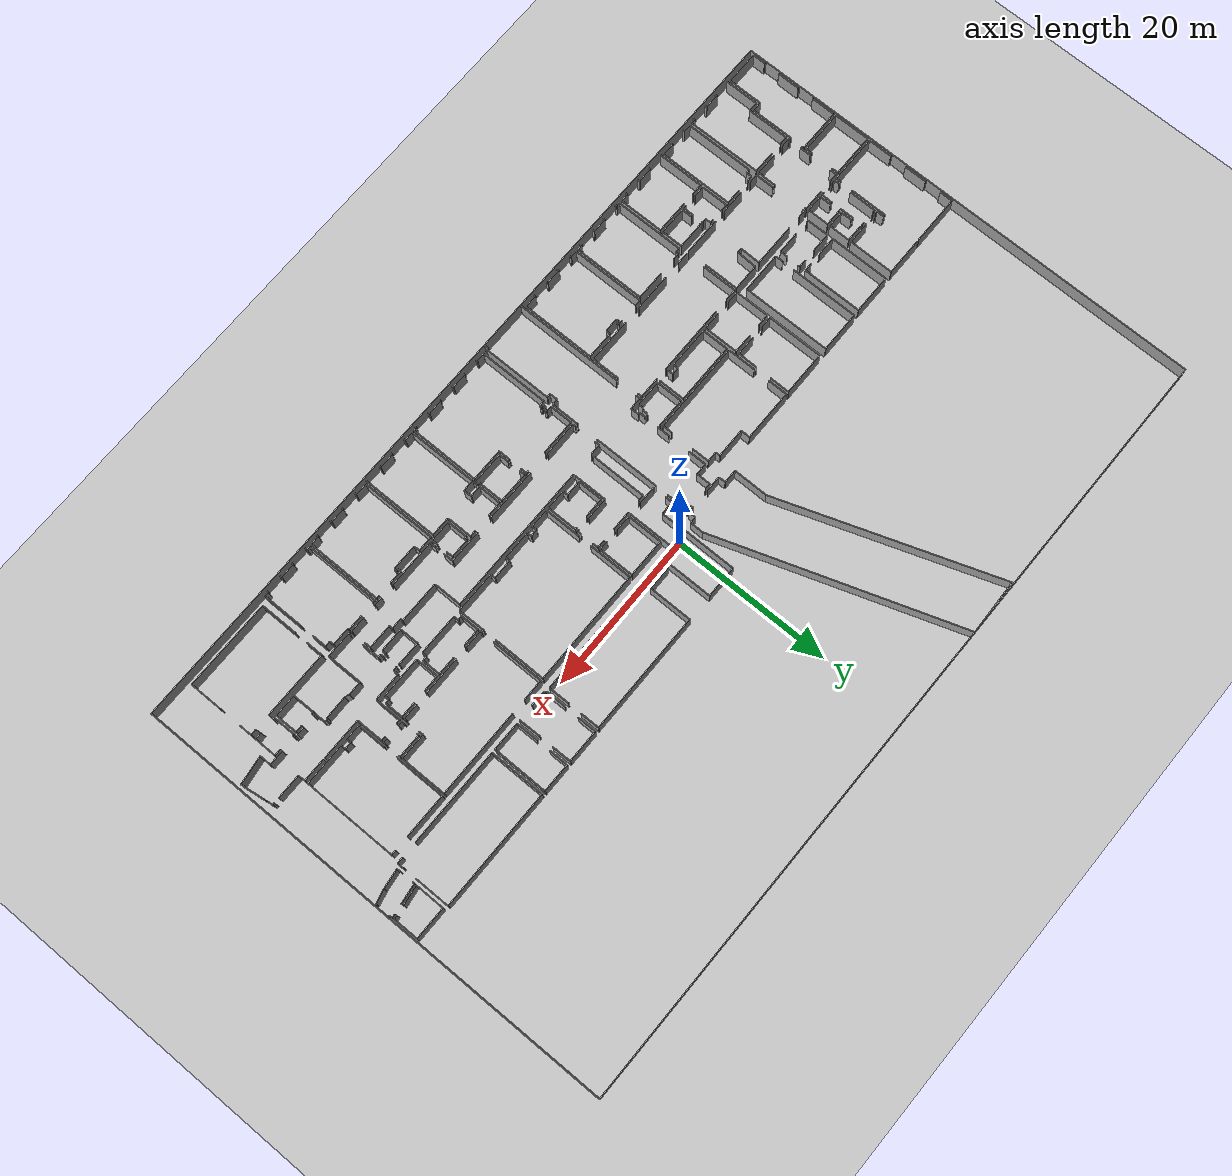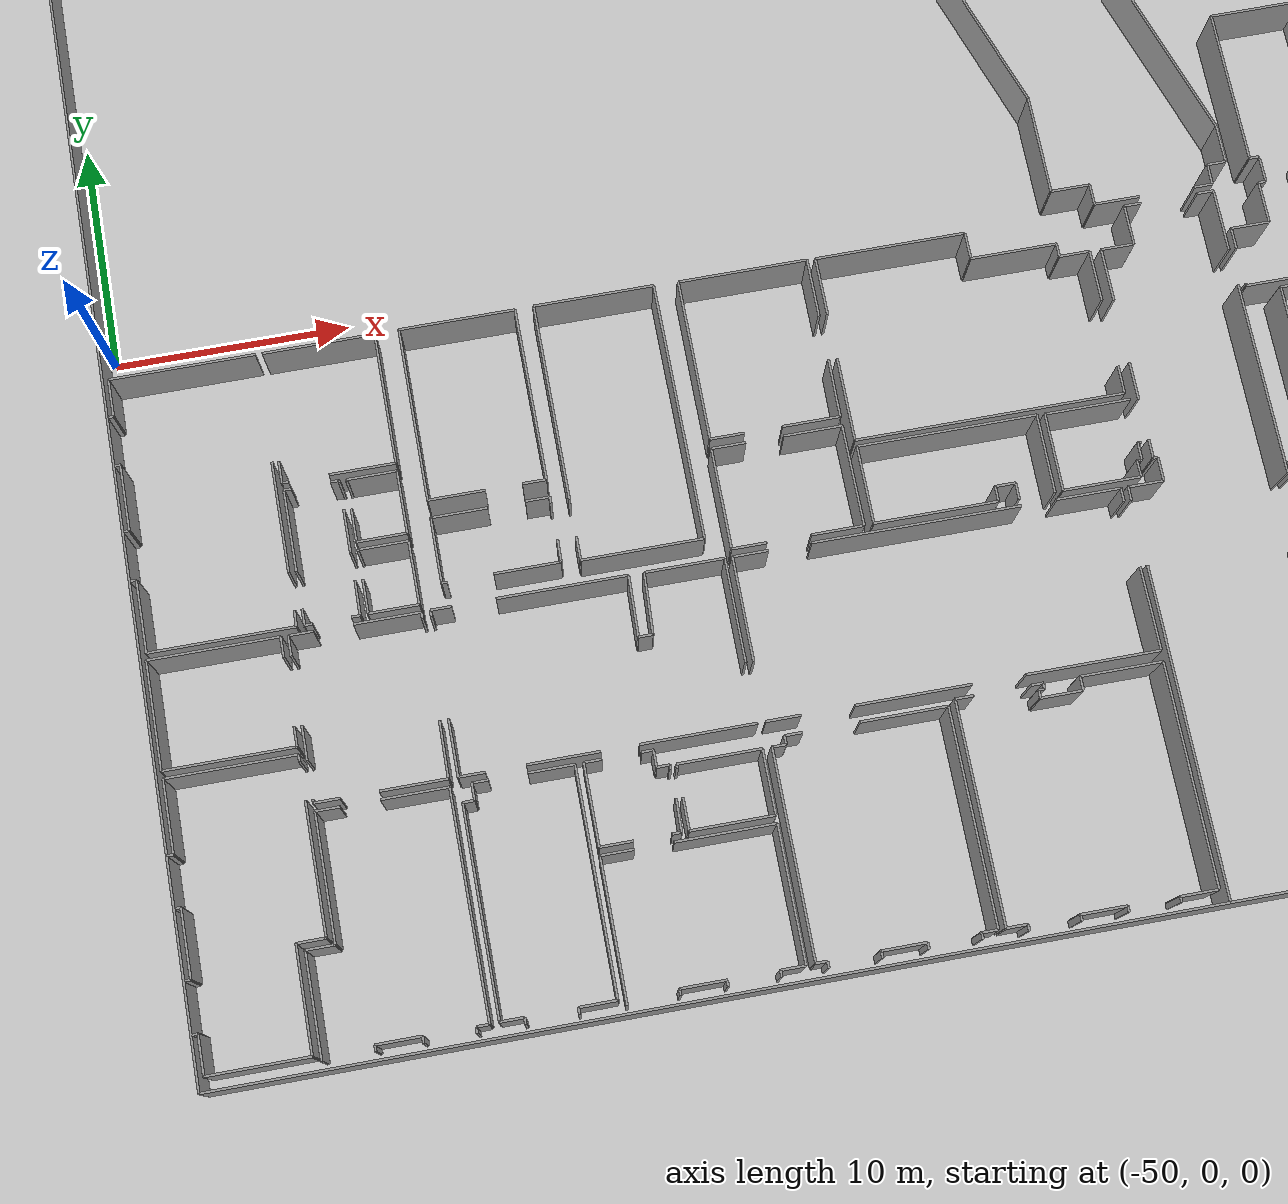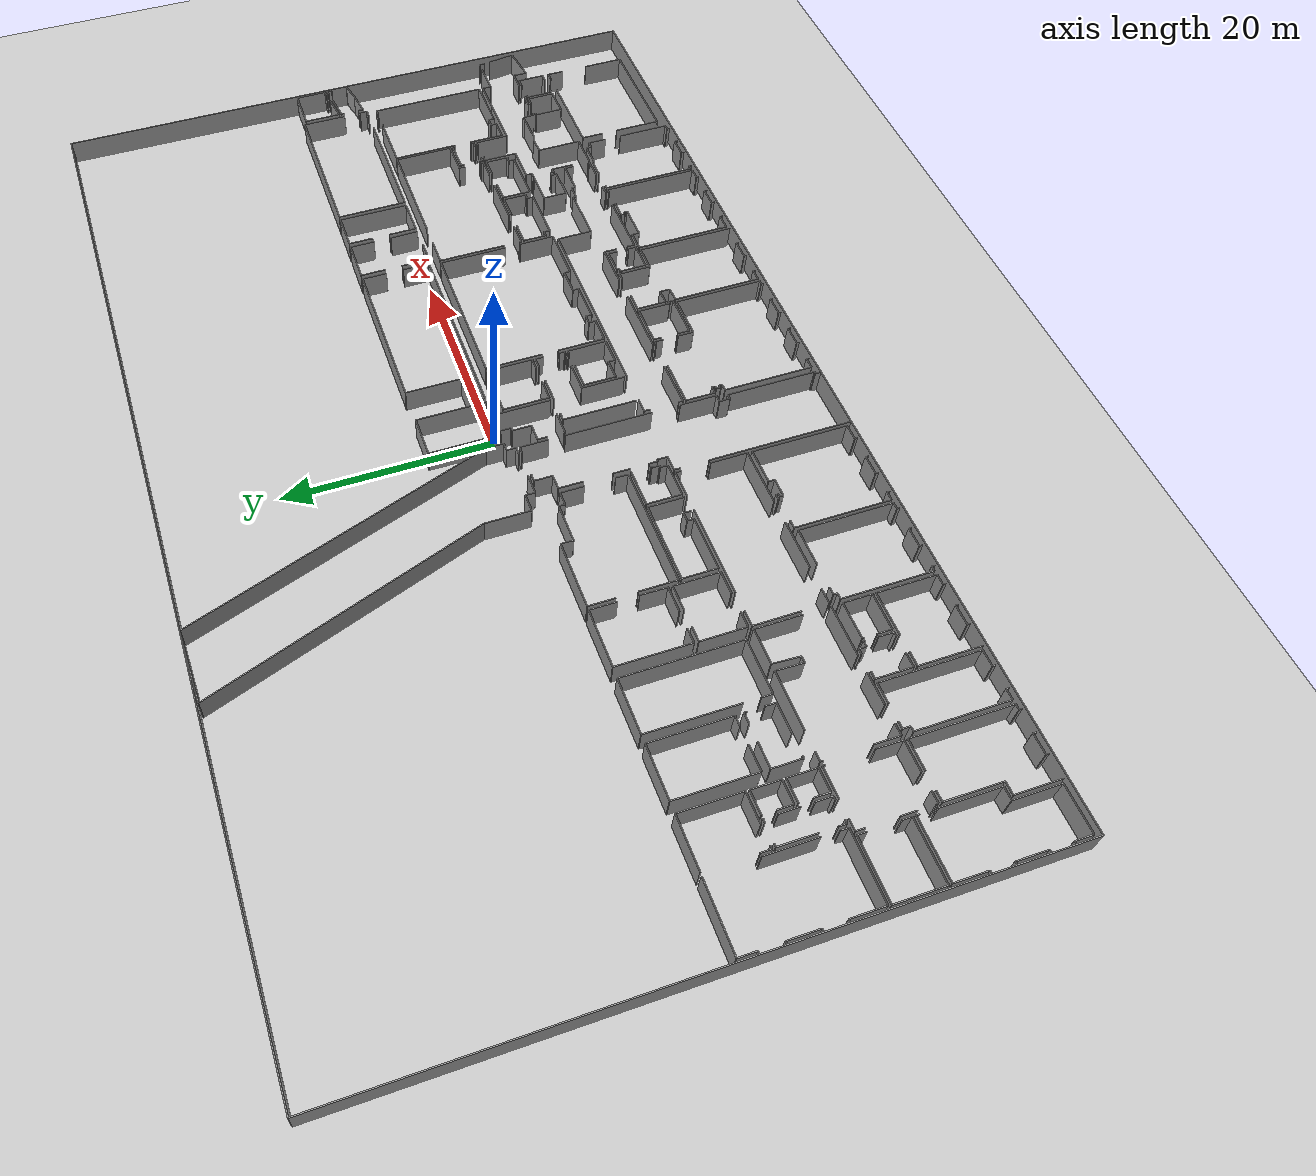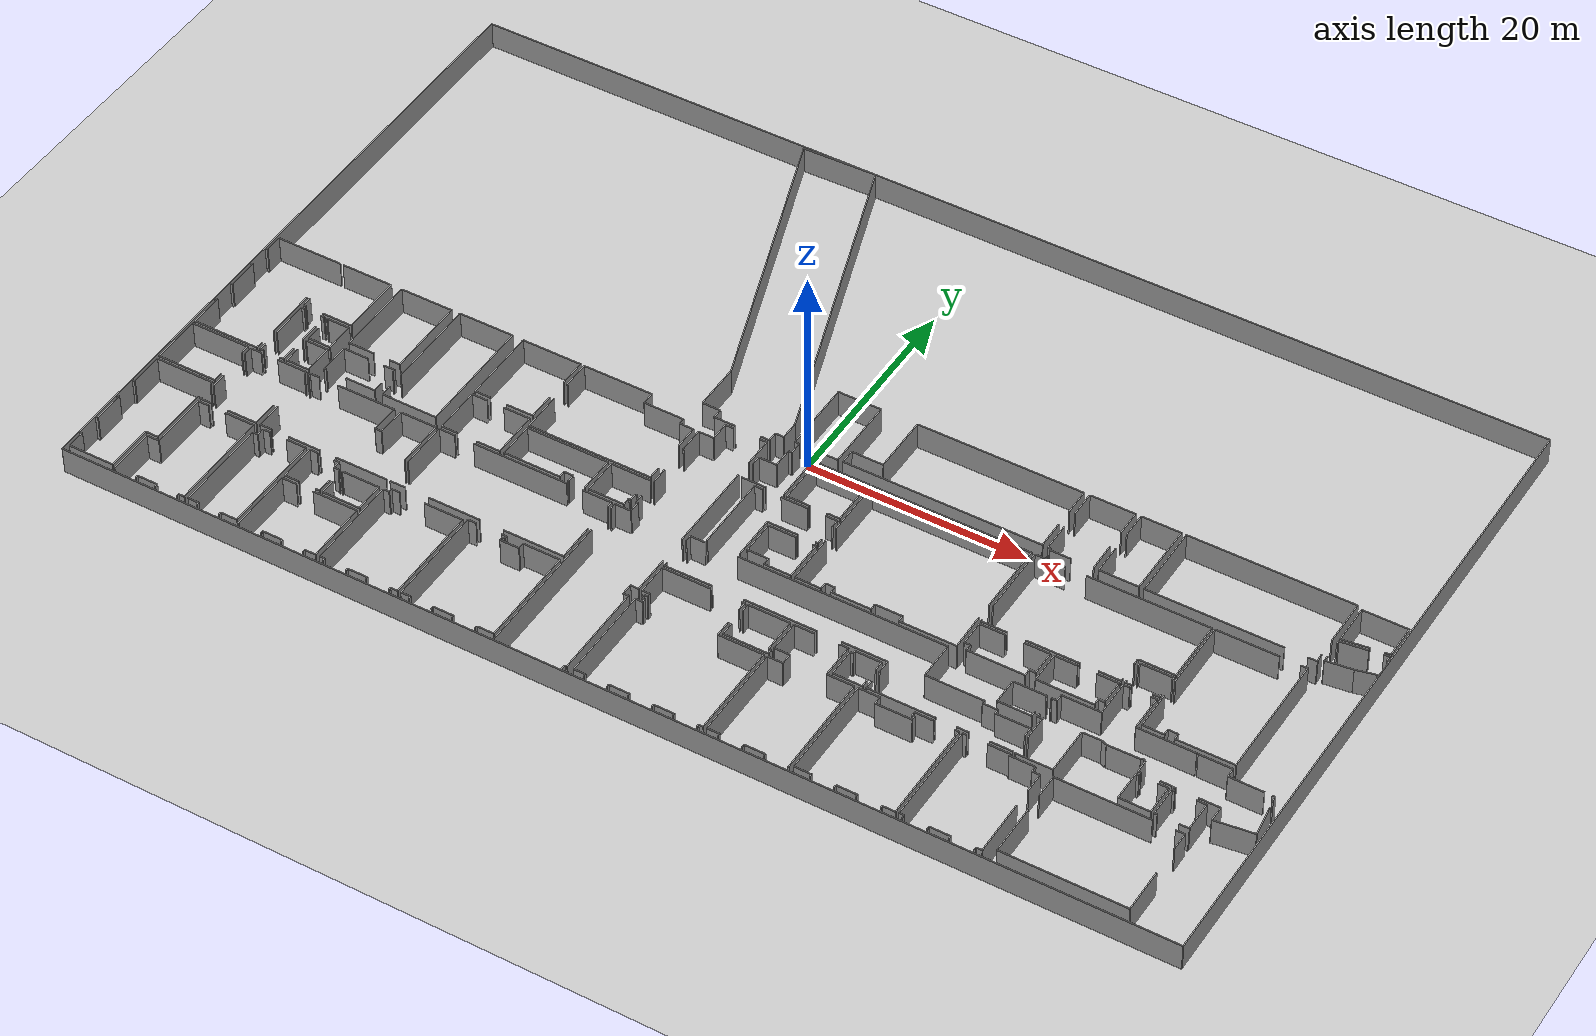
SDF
<sdf version="1.6">
  <world name="default">
    <light name="sun" type="directional">
      <cast_shadows>1</cast_shadows>
      <pose frame="">0 0 10 0 -0 0</pose>
      <diffuse>0.8 0.8 0.8 1</diffuse>
      <specular>0.1 0.1 0.1 1</specular>
      <attenuation>
        <range>1000</range>
        <constant>0.9</constant>
        <linear>0.01</linear>
        <quadratic>0.001</quadratic>
      </attenuation>
      <direction>-0.5 0.5 -1</direction>
    </light>
    <model name="ground_plane">
      <static>1</static>
      <link name="link">
        <collision name="collision">
          <geometry>
            <plane>
              <normal>0 0 1</normal>
              <size>100 100</size>
            </plane>
          </geometry>
          <surface>
            <friction>
              <ode>
                <mu>100</mu>
                <mu2>50</mu2>
              </ode>
              <torsional>
                <ode />
              </torsional>
            </friction>
            <contact>
              <ode />
            </contact>
            <bounce />
          </surface>
          <max_contacts>10</max_contacts>
        </collision>
        <visual name="visual">
          <cast_shadows>0</cast_shadows>
          <geometry>
            <plane>
              <normal>0 0 1</normal>
              <size>100 100</size>
            </plane>
          </geometry>
          <material>
            <script>
              <uri>file://media/materials/scripts/gazebo.material</uri>
              <name>Gazebo/Grey</name>
            </script>
          </material>
        </visual>
        <self_collide>0</self_collide>
        <kinematic>0</kinematic>
        <gravity>1</gravity>
      </link>
    </model>
    <gravity>0 0 -9.8</gravity>
    <magnetic_field>6e-06 2.3e-05 -4.2e-05</magnetic_field>
    <atmosphere type="adiabatic" />
    <physics default="0" name="default_physics" type="ode">
      <max_step_size>0.001</max_step_size>
      <real_time_factor>1</real_time_factor>
      <real_time_update_rate>1000</real_time_update_rate>
    </physics>
    <scene>
      <ambient>0.4 0.4 0.4 1</ambient>
      <background>0.7 0.7 0.7 1</background>
      <shadows>1</shadows>
    </scene>
    <spherical_coordinates>
      <surface_model>EARTH_WGS84</surface_model>
      <latitude_deg>0</latitude_deg>
      <longitude_deg>0</longitude_deg>
      <elevation>0</elevation>
      <heading_deg>0</heading_deg>
    </spherical_coordinates>
  <model name="0510032260_A_40_1_102">
		<static>1</static>
		<link name="Wall_0">
			<collision name="Wall_0_Collision">
				<geometry>
					<box>
						<size>6.1017788129 0.1 2.5</size>
					</box>
				</geometry>
				<pose frame="">3.05088940645 0 1.25 0 0 0</pose>
			</collision>
			<visual name="Wall_0_Visual">
				<pose frame="">3.05088940645 0 1.25 0 0 0</pose>
				<geometry>
					<box>
						<size>6.1017788129 0.1 2.5</size>
					</box>
				</geometry>
				<material>
					<script>
						<uri>file://media/materials/scripts/gazebo.material</uri>
						<name>Gazebo/Grey</name>
					</script>
					<ambient>1 1 1 1</ambient>
				</material>
			</visual>
			<pose frame="">6.38659195187 -44.0144183479 0 0 0 3.14159265359</pose>
		</link>
		<link name="Wall_1">
			<collision name="Wall_1_Collision">
				<geometry>
					<box>
						<size>3.08204877615 0.1 2.5</size>
					</box>
				</geometry>
				<pose frame="">1.54102438808 0 1.25 0 0 0</pose>
			</collision>
			<visual name="Wall_1_Visual">
				<pose frame="">1.54102438808 0 1.25 0 0 0</pose>
				<geometry>
					<box>
						<size>3.08204877615 0.1 2.5</size>
					</box>
				</geometry>
				<material>
					<script>
						<uri>file://media/materials/scripts/gazebo.material</uri>
						<name>Gazebo/Grey</name>
					</script>
					<ambient>1 1 1 1</ambient>
				</material>
			</visual>
			<pose frame="">0.284813138973 -44.0144183479 0 0 0 1.57079632679</pose>
		</link>
		<link name="Wall_2">
			<collision name="Wall_2_Collision">
				<geometry>
					<box>
						<size>0.251178788783 0.1 2.5</size>
					</box>
				</geometry>
				<pose frame="">0.125589394391 0 1.25 0 0 0</pose>
			</collision>
			<visual name="Wall_2_Visual">
				<pose frame="">0.125589394391 0 1.25 0 0 0</pose>
				<geometry>
					<box>
						<size>0.251178788783 0.1 2.5</size>
					</box>
				</geometry>
				<material>
					<script>
						<uri>file://media/materials/scripts/gazebo.material</uri>
						<name>Gazebo/Grey</name>
					</script>
					<ambient>1 1 1 1</ambient>
				</material>
			</visual>
			<pose frame="">0.284813138973 -40.9323695717 0 0 0 3.14159265359</pose>
		</link>
		<link name="Wall_3">
			<collision name="Wall_3_Collision">
				<geometry>
					<box>
						<size>0.238486581163 0.1 2.5</size>
					</box>
				</geometry>
				<pose frame="">0.119243290582 0 1.25 0 0 0</pose>
			</collision>
			<visual name="Wall_3_Visual">
				<pose frame="">0.119243290582 0 1.25 0 0 0</pose>
				<geometry>
					<box>
						<size>0.238486581163 0.1 2.5</size>
					</box>
				</geometry>
				<material>
					<script>
						<uri>file://media/materials/scripts/gazebo.material</uri>
						<name>Gazebo/Grey</name>
					</script>
					<ambient>1 1 1 1</ambient>
				</material>
			</visual>
			<pose frame="">0.0336343501907 -38.808963237 0 0 0 0.0</pose>
		</link>
		<link name="Wall_4">
			<collision name="Wall_4_Collision">
				<geometry>
					<box>
						<size>2.84368911707 0.1 2.5</size>
					</box>
				</geometry>
				<pose frame="">1.42184455853 0 1.25 0 0 0</pose>
			</collision>
			<visual name="Wall_4_Visual">
				<pose frame="">1.42184455853 0 1.25 0 0 0</pose>
				<geometry>
					<box>
						<size>2.84368911707 0.1 2.5</size>
					</box>
				</geometry>
				<material>
					<script>
						<uri>file://media/materials/scripts/gazebo.material</uri>
						<name>Gazebo/Grey</name>
					</script>
					<ambient>1 1 1 1</ambient>
				</material>
			</visual>
			<pose frame="">0.272120931354 -38.808963237 0 0 0 1.57079632679</pose>
		</link>
		<link name="Wall_5">
			<collision name="Wall_5_Collision">
				<geometry>
					<box>
						<size>0.257651814668 0.1 2.5</size>
					</box>
				</geometry>
				<pose frame="">0.128825907334 0 1.25 0 0 0</pose>
			</collision>
			<visual name="Wall_5_Visual">
				<pose frame="">0.128825907334 0 1.25 0 0 0</pose>
				<geometry>
					<box>
						<size>0.257651814668 0.1 2.5</size>
					</box>
				</geometry>
				<material>
					<script>
						<uri>file://media/materials/scripts/gazebo.material</uri>
						<name>Gazebo/Grey</name>
					</script>
					<ambient>1 1 1 1</ambient>
				</material>
			</visual>
			<pose frame="">0.272120931354 -35.96527412 0 0 0 3.14159265359</pose>
		</link>
		<link name="Wall_6">
			<collision name="Wall_6_Collision">
				<geometry>
					<box>
						<size>0.248132658954 0.1 2.5</size>
					</box>
				</geometry>
				<pose frame="">0.124066329477 0 1.25 0 0 0</pose>
			</collision>
			<visual name="Wall_6_Visual">
				<pose frame="">0.124066329477 0 1.25 0 0 0</pose>
				<geometry>
					<box>
						<size>0.248132658954 0.1 2.5</size>
					</box>
				</geometry>
				<material>
					<script>
						<uri>file://media/materials/scripts/gazebo.material</uri>
						<name>Gazebo/Grey</name>
					</script>
					<ambient>1 1 1 1</ambient>
				</material>
			</visual>
			<pose frame="">0.0144691166858 -33.8371716685 0 0 0 0.0</pose>
		</link>
		<link name="Wall_7">
			<collision name="Wall_7_Collision">
				<geometry>
					<box>
						<size>1.63666017249 0.1 2.5</size>
					</box>
				</geometry>
				<pose frame="">0.818330086244 0 1.25 0 0 0</pose>
			</collision>
			<visual name="Wall_7_Visual">
				<pose frame="">0.818330086244 0 1.25 0 0 0</pose>
				<geometry>
					<box>
						<size>1.63666017249 0.1 2.5</size>
					</box>
				</geometry>
				<material>
					<script>
						<uri>file://media/materials/scripts/gazebo.material</uri>
						<name>Gazebo/Grey</name>
					</script>
					<ambient>1 1 1 1</ambient>
				</material>
			</visual>
			<pose frame="">0.26260177564 -33.8371716685 0 0 0 1.57079632679</pose>
		</link>
		<link name="Wall_8">
			<collision name="Wall_8_Collision">
				<geometry>
					<box>
						<size>6.15368994206 0.1 2.5</size>
					</box>
				</geometry>
				<pose frame="">3.07684497103 0 1.25 0 0 0</pose>
			</collision>
			<visual name="Wall_8_Visual">
				<pose frame="">3.07684497103 0 1.25 0 0 0</pose>
				<geometry>
					<box>
						<size>6.15368994206 0.1 2.5</size>
					</box>
				</geometry>
				<material>
					<script>
						<uri>file://media/materials/scripts/gazebo.material</uri>
						<name>Gazebo/Grey</name>
					</script>
					<ambient>1 1 1 1</ambient>
				</material>
			</visual>
			<pose frame="">0.26260177564 -32.200511496 0 0 0 0.0</pose>
		</link>
		<link name="Wall_9">
			<collision name="Wall_9_Collision">
				<geometry>
					<box>
						<size>4.78039307767 0.1 2.5</size>
					</box>
				</geometry>
				<pose frame="">2.39019653883 0 1.25 0 0 0</pose>
			</collision>
			<visual name="Wall_9_Visual">
				<pose frame="">2.39019653883 0 1.25 0 0 0</pose>
				<geometry>
					<box>
						<size>4.78039307767 0.1 2.5</size>
					</box>
				</geometry>
				<material>
					<script>
						<uri>file://media/materials/scripts/gazebo.material</uri>
						<name>Gazebo/Grey</name>
					</script>
					<ambient>1 1 1 1</ambient>
				</material>
			</visual>
			<pose frame="">6.4162917177 -36.9579316778 0 0 0 -1.57079632679</pose>
		</link>
		<link name="Wall_10">
			<collision name="Wall_10_Collision">
				<geometry>
					<box>
						<size>0.699463773333 0.1 2.5</size>
					</box>
				</geometry>
				<pose frame="">0.349731886667 0 1.25 0 0 0</pose>
			</collision>
			<visual name="Wall_10_Visual">
				<pose frame="">0.349731886667 0 1.25 0 0 0</pose>
				<geometry>
					<box>
						<size>0.699463773333 0.1 2.5</size>
					</box>
				</geometry>
				<material>
					<script>
						<uri>file://media/materials/scripts/gazebo.material</uri>
						<name>Gazebo/Grey</name>
					</script>
					<ambient>1 1 1 1</ambient>
				</material>
			</visual>
			<pose frame="">6.4162917177 -43.3155853963 0 0 0 -1.61326985949</pose>
		</link>
		<link name="Wall_11">
			<collision name="Wall_11_Collision">
				<geometry>
					<box>
						<size>2.78124345558 0.1 2.5</size>
					</box>
				</geometry>
				<pose frame="">1.39062172779 0 1.25 0 0 0</pose>
			</collision>
			<visual name="Wall_11_Visual">
				<pose frame="">1.39062172779 0 1.25 0 0 0</pose>
				<geometry>
					<box>
						<size>2.78124345558 0.1 2.5</size>
					</box>
				</geometry>
				<material>
					<script>
						<uri>file://media/materials/scripts/gazebo.material</uri>
						<name>Gazebo/Grey</name>
					</script>
					<ambient>1 1 1 1</ambient>
				</material>
			</visual>
			<pose frame="">11.4279368182 -37.9172087297 0 0 0 3.14159265359</pose>
		</link>
		<link name="Wall_12">
			<collision name="Wall_12_Collision">
				<geometry>
					<box>
						<size>0.275420905335 0.1 2.5</size>
					</box>
				</geometry>
				<pose frame="">0.137710452668 0 1.25 0 0 0</pose>
			</collision>
			<visual name="Wall_12_Visual">
				<pose frame="">0.137710452668 0 1.25 0 0 0</pose>
				<geometry>
					<box>
						<size>0.275420905335 0.1 2.5</size>
					</box>
				</geometry>
				<material>
					<script>
						<uri>file://media/materials/scripts/gazebo.material</uri>
						<name>Gazebo/Grey</name>
					</script>
					<ambient>1 1 1 1</ambient>
				</material>
			</visual>
			<pose frame="">6.97132195688 -37.9172087297 0 0 0 3.14159265359</pose>
		</link>
		<link name="Wall_13">
			<collision name="Wall_13_Collision">
				<geometry>
					<box>
						<size>0.944173324787 0.1 2.5</size>
					</box>
				</geometry>
				<pose frame="">0.472086662394 0 1.25 0 0 0</pose>
			</collision>
			<visual name="Wall_13_Visual">
				<pose frame="">0.472086662394 0 1.25 0 0 0</pose>
				<geometry>
					<box>
						<size>0.944173324787 0.1 2.5</size>
					</box>
				</geometry>
				<material>
					<script>
						<uri>file://media/materials/scripts/gazebo.material</uri>
						<name>Gazebo/Grey</name>
					</script>
					<ambient>1 1 1 1</ambient>
				</material>
			</visual>
			<pose frame="">6.69590105155 -37.9172087297 0 0 0 1.57079632679</pose>
		</link>
		<link name="Wall_14">
			<collision name="Wall_14_Collision">
				<geometry>
					<box>
						<size>4.74015877952 0.1 2.5</size>
					</box>
				</geometry>
				<pose frame="">2.37007938976 0 1.25 0 0 0</pose>
			</collision>
			<visual name="Wall_14_Visual">
				<pose frame="">2.37007938976 0 1.25 0 0 0</pose>
				<geometry>
					<box>
						<size>4.74015877952 0.1 2.5</size>
					</box>
				</geometry>
				<material>
					<script>
						<uri>file://media/materials/scripts/gazebo.material</uri>
						<name>Gazebo/Grey</name>
					</script>
					<ambient>1 1 1 1</ambient>
				</material>
			</visual>
			<pose frame="">6.69590105155 -32.2078729764 0 0 0 0.0</pose>
		</link>
		<link name="Wall_15">
			<collision name="Wall_15_Collision">
				<geometry>
					<box>
						<size>5.70934153186 0.1 2.5</size>
					</box>
				</geometry>
				<pose frame="">2.85467076593 0 1.25 0 0 0</pose>
			</collision>
			<visual name="Wall_15_Visual">
				<pose frame="">2.85467076593 0 1.25 0 0 0</pose>
				<geometry>
					<box>
						<size>5.70934153186 0.1 2.5</size>
					</box>
				</geometry>
				<material>
					<script>
						<uri>file://media/materials/scripts/gazebo.material</uri>
						<name>Gazebo/Grey</name>
					</script>
					<ambient>1 1 1 1</ambient>
				</material>
			</visual>
			<pose frame="">11.4360598311 -32.2078729764 0 0 0 -1.57221908554</pose>
		</link>
		<link name="Wall_16">
			<collision name="Wall_16_Collision">
				<geometry>
					<box>
						<size>0.355508735412 0.1 2.5</size>
					</box>
				</geometry>
				<pose frame="">0.177754367706 0 1.25 0 0 0</pose>
			</collision>
			<visual name="Wall_16_Visual">
				<pose frame="">0.177754367706 0 1.25 0 0 0</pose>
				<geometry>
					<box>
						<size>0.355508735412 0.1 2.5</size>
					</box>
				</geometry>
				<material>
					<script>
						<uri>file://media/materials/scripts/gazebo.material</uri>
						<name>Gazebo/Grey</name>
					</script>
					<ambient>1 1 1 1</ambient>
				</material>
			</visual>
			<pose frame="">8.99623676044 -44.0216529062 0 0 0 3.14159265359</pose>
		</link>
		<link name="Wall_17">
			<collision name="Wall_17_Collision">
				<geometry>
					<box>
						<size>0.331139696783 0.1 2.5</size>
					</box>
				</geometry>
				<pose frame="">0.165569848392 0 1.25 0 0 0</pose>
			</collision>
			<visual name="Wall_17_Visual">
				<pose frame="">0.165569848392 0 1.25 0 0 0</pose>
				<geometry>
					<box>
						<size>0.331139696783 0.1 2.5</size>
					</box>
				</geometry>
				<material>
					<script>
						<uri>file://media/materials/scripts/gazebo.material</uri>
						<name>Gazebo/Grey</name>
					</script>
					<ambient>1 1 1 1</ambient>
				</material>
			</visual>
			<pose frame="">7.05737512454 -44.0216529062 0 0 0 3.14159265359</pose>
		</link>
		<link name="Wall_18">
			<collision name="Wall_18_Collision">
				<geometry>
					<box>
						<size>0.696548354138 0.1 2.5</size>
					</box>
				</geometry>
				<pose frame="">0.348274177069 0 1.25 0 0 0</pose>
			</collision>
			<visual name="Wall_18_Visual">
				<pose frame="">0.348274177069 0 1.25 0 0 0</pose>
				<geometry>
					<box>
						<size>0.696548354138 0.1 2.5</size>
					</box>
				</geometry>
				<material>
					<script>
						<uri>file://media/materials/scripts/gazebo.material</uri>
						<name>Gazebo/Grey</name>
					</script>
					<ambient>1 1 1 1</ambient>
				</material>
			</visual>
			<pose frame="">6.72623542776 -44.0216529062 0 0 0 1.57079632679</pose>
		</link>
		<link name="Wall_19">
			<collision name="Wall_19_Collision">
				<geometry>
					<box>
						<size>3.49771857568 0.1 2.5</size>
					</box>
				</geometry>
				<pose frame="">1.74885928784 0 1.25 0 0 0</pose>
			</collision>
			<visual name="Wall_19_Visual">
				<pose frame="">1.74885928784 0 1.25 0 0 0</pose>
				<geometry>
					<box>
						<size>3.49771857568 0.1 2.5</size>
					</box>
				</geometry>
				<material>
					<script>
						<uri>file://media/materials/scripts/gazebo.material</uri>
						<name>Gazebo/Grey</name>
					</script>
					<ambient>1 1 1 1</ambient>
				</material>
			</visual>
			<pose frame="">6.72623542776 -41.7286786777 0 0 0 1.57079632679</pose>
		</link>
		<link name="Wall_20">
			<collision name="Wall_20_Collision">
				<geometry>
					<box>
						<size>0.302328385488 0.1 2.5</size>
					</box>
				</geometry>
				<pose frame="">0.151164192744 0 1.25 0 0 0</pose>
			</collision>
			<visual name="Wall_20_Visual">
				<pose frame="">0.151164192744 0 1.25 0 0 0</pose>
				<geometry>
					<box>
						<size>0.302328385488 0.1 2.5</size>
					</box>
				</geometry>
				<material>
					<script>
						<uri>file://media/materials/scripts/gazebo.material</uri>
						<name>Gazebo/Grey</name>
					</script>
					<ambient>1 1 1 1</ambient>
				</material>
			</visual>
			<pose frame="">6.72623542776 -38.230960102 0 0 0 0.0</pose>
		</link>
		<link name="Wall_21">
			<collision name="Wall_21_Collision">
				<geometry>
					<box>
						<size>0.367185566421 0.1 2.5</size>
					</box>
				</geometry>
				<pose frame="">0.183592783211 0 1.25 0 0 0</pose>
			</collision>
			<visual name="Wall_21_Visual">
				<pose frame="">0.183592783211 0 1.25 0 0 0</pose>
				<geometry>
					<box>
						<size>0.367185566421 0.1 2.5</size>
					</box>
				</geometry>
				<material>
					<script>
						<uri>file://media/materials/scripts/gazebo.material</uri>
						<name>Gazebo/Grey</name>
					</script>
					<ambient>1 1 1 1</ambient>
				</material>
			</visual>
			<pose frame="">8.64872411583 -38.230960102 0 0 0 0.0</pose>
		</link>
		<link name="Wall_22">
			<collision name="Wall_22_Collision">
				<geometry>
					<box>
						<size>0.0856724014291 0.1 2.5</size>
					</box>
				</geometry>
				<pose frame="">0.0428362007146 0 1.25 0 0 0</pose>
			</collision>
			<visual name="Wall_22_Visual">
				<pose frame="">0.0428362007146 0 1.25 0 0 0</pose>
				<geometry>
					<box>
						<size>0.0856724014291 0.1 2.5</size>
					</box>
				</geometry>
				<material>
					<script>
						<uri>file://media/materials/scripts/gazebo.material</uri>
						<name>Gazebo/Grey</name>
					</script>
					<ambient>1 1 1 1</ambient>
				</material>
			</visual>
			<pose frame="">9.01590968225 -38.230960102 0 0 0 -1.57079632679</pose>
		</link>
		<link name="Wall_23">
			<collision name="Wall_23_Collision">
				<geometry>
					<box>
						<size>1.86803911738 0.1 2.5</size>
					</box>
				</geometry>
				<pose frame="">0.934019558692 0 1.25 0 0 0</pose>
			</collision>
			<visual name="Wall_23_Visual">
				<pose frame="">0.934019558692 0 1.25 0 0 0</pose>
				<geometry>
					<box>
						<size>1.86803911738 0.1 2.5</size>
					</box>
				</geometry>
				<material>
					<script>
						<uri>file://media/materials/scripts/gazebo.material</uri>
						<name>Gazebo/Grey</name>
					</script>
					<ambient>1 1 1 1</ambient>
				</material>
			</visual>
			<pose frame="">9.01590968225 -39.4925655394 0 0 0 -1.57079632679</pose>
		</link>
		<link name="Wall_24">
			<collision name="Wall_24_Collision">
				<geometry>
					<box>
						<size>1.48232655759 0.1 2.5</size>
					</box>
				</geometry>
				<pose frame="">0.741163278797 0 1.25 0 0 0</pose>
			</collision>
			<visual name="Wall_24_Visual">
				<pose frame="">0.741163278797 0 1.25 0 0 0</pose>
				<geometry>
					<box>
						<size>1.48232655759 0.1 2.5</size>
					</box>
				</geometry>
				<material>
					<script>
						<uri>file://media/materials/scripts/gazebo.material</uri>
						<name>Gazebo/Grey</name>
					</script>
					<ambient>1 1 1 1</ambient>
				</material>
			</visual>
			<pose frame="">9.01590968225 -42.5394569004 0 0 0 -1.58406836815</pose>
		</link>
		<link name="Wall_25">
			<collision name="Wall_25_Collision">
				<geometry>
					<box>
						<size>2.09497578961 0.1 2.5</size>
					</box>
				</geometry>
				<pose frame="">1.04748789481 0 1.25 0 0 0</pose>
			</collision>
			<visual name="Wall_25_Visual">
				<pose frame="">1.04748789481 0 1.25 0 0 0</pose>
				<geometry>
					<box>
						<size>2.09497578961 0.1 2.5</size>
					</box>
				</geometry>
				<material>
					<script>
						<uri>file://media/materials/scripts/gazebo.material</uri>
						<name>Gazebo/Grey</name>
					</script>
					<ambient>1 1 1 1</ambient>
				</material>
			</visual>
			<pose frame="">11.4215907144 -40.9482348312 0 0 0 3.14159265359</pose>
		</link>
		<link name="Wall_26">
			<collision name="Wall_26_Collision">
				<geometry>
					<box>
						<size>1.42584260393 0.1 2.5</size>
					</box>
				</geometry>
				<pose frame="">0.712921301967 0 1.25 0 0 0</pose>
			</collision>
			<visual name="Wall_26_Visual">
				<pose frame="">0.712921301967 0 1.25 0 0 0</pose>
				<geometry>
					<box>
						<size>1.42584260393 0.1 2.5</size>
					</box>
				</geometry>
				<material>
					<script>
						<uri>file://media/materials/scripts/gazebo.material</uri>
						<name>Gazebo/Grey</name>
					</script>
					<ambient>1 1 1 1</ambient>
				</material>
			</visual>
			<pose frame="">9.32661492477 -40.9482348312 0 0 0 1.57079632679</pose>
		</link>
		<link name="Wall_27">
			<collision name="Wall_27_Collision">
				<geometry>
					<box>
						<size>0.0767878560958 0.1 2.5</size>
					</box>
				</geometry>
				<pose frame="">0.0383939280479 0 1.25 0 0 0</pose>
			</collision>
			<visual name="Wall_27_Visual">
				<pose frame="">0.0383939280479 0 1.25 0 0 0</pose>
				<geometry>
					<box>
						<size>0.0767878560958 0.1 2.5</size>
					</box>
				</geometry>
				<material>
					<script>
						<uri>file://media/materials/scripts/gazebo.material</uri>
						<name>Gazebo/Grey</name>
					</script>
					<ambient>1 1 1 1</ambient>
				</material>
			</visual>
			<pose frame="">9.32661492477 -38.3297054773 0 0 0 1.57079632679</pose>
		</link>
		<link name="Wall_28">
			<collision name="Wall_28_Collision">
				<geometry>
					<box>
						<size>2.09167581563 0.1 2.5</size>
					</box>
				</geometry>
				<pose frame="">1.04583790782 0 1.25 0 0 0</pose>
			</collision>
			<visual name="Wall_28_Visual">
				<pose frame="">1.04583790782 0 1.25 0 0 0</pose>
				<geometry>
					<box>
						<size>2.09167581563 0.1 2.5</size>
					</box>
				</geometry>
				<material>
					<script>
						<uri>file://media/materials/scripts/gazebo.material</uri>
						<name>Gazebo/Grey</name>
					</script>
					<ambient>1 1 1 1</ambient>
				</material>
			</visual>
			<pose frame="">9.32661492477 -38.2529176212 0 0 0 0.0</pose>
		</link>
		<link name="Wall_29">
			<collision name="Wall_29_Collision">
				<geometry>
					<box>
						<size>2.69531923014 0.1 2.5</size>
					</box>
				</geometry>
				<pose frame="">1.34765961507 0 1.25 0 0 0</pose>
			</collision>
			<visual name="Wall_29_Visual">
				<pose frame="">1.34765961507 0 1.25 0 0 0</pose>
				<geometry>
					<box>
						<size>2.69531923014 0.1 2.5</size>
					</box>
				</geometry>
				<material>
					<script>
						<uri>file://media/materials/scripts/gazebo.material</uri>
						<name>Gazebo/Grey</name>
					</script>
					<ambient>1 1 1 1</ambient>
				</material>
			</visual>
			<pose frame="">11.4182907404 -38.2529176212 0 0 0 -1.56957199137</pose>
		</link>
		<link name="Wall_30">
			<collision name="Wall_30_Collision">
				<geometry>
					<box>
						<size>2.09624501038 0.1 2.5</size>
					</box>
				</geometry>
				<pose frame="">1.04812250519 0 1.25 0 0 0</pose>
			</collision>
			<visual name="Wall_30_Visual">
				<pose frame="">1.04812250519 0 1.25 0 0 0</pose>
				<geometry>
					<box>
						<size>2.09624501038 0.1 2.5</size>
					</box>
				</geometry>
				<material>
					<script>
						<uri>file://media/materials/scripts/gazebo.material</uri>
						<name>Gazebo/Grey</name>
					</script>
					<ambient>1 1 1 1</ambient>
				</material>
			</visual>
			<pose frame="">11.4252714546 -43.9977915559 0 0 0 3.14159265359</pose>
		</link>
		<link name="Wall_31">
			<collision name="Wall_31_Collision">
				<geometry>
					<box>
						<size>1.46379230471 0.1 2.5</size>
					</box>
				</geometry>
				<pose frame="">0.731896152357 0 1.25 0 0 0</pose>
			</collision>
			<visual name="Wall_31_Visual">
				<pose frame="">0.731896152357 0 1.25 0 0 0</pose>
				<geometry>
					<box>
						<size>1.46379230471 0.1 2.5</size>
					</box>
				</geometry>
				<material>
					<script>
						<uri>file://media/materials/scripts/gazebo.material</uri>
						<name>Gazebo/Grey</name>
					</script>
					<ambient>1 1 1 1</ambient>
				</material>
			</visual>
			<pose frame="">9.32902644421 -43.9977915559 0 0 0 1.57079632679</pose>
		</link>
		<link name="Wall_32">
			<collision name="Wall_32_Collision">
				<geometry>
					<box>
						<size>0.0798339859243 0.1 2.5</size>
					</box>
				</geometry>
				<pose frame="">0.0399169929622 0 1.25 0 0 0</pose>
			</collision>
			<visual name="Wall_32_Visual">
				<pose frame="">0.0399169929622 0 1.25 0 0 0</pose>
				<geometry>
					<box>
						<size>0.0798339859243 0.1 2.5</size>
					</box>
				</geometry>
				<material>
					<script>
						<uri>file://media/materials/scripts/gazebo.material</uri>
						<name>Gazebo/Grey</name>
					</script>
					<ambient>1 1 1 1</ambient>
				</material>
			</visual>
			<pose frame="">9.32902644421 -41.3583200594 0 0 0 1.57079632679</pose>
		</link>
		<link name="Wall_33">
			<collision name="Wall_33_Collision">
				<geometry>
					<box>
						<size>2.09104120525 0.1 2.5</size>
					</box>
				</geometry>
				<pose frame="">1.04552060263 0 1.25 0 0 0</pose>
			</collision>
			<visual name="Wall_33_Visual">
				<pose frame="">1.04552060263 0 1.25 0 0 0</pose>
				<geometry>
					<box>
						<size>2.09104120525 0.1 2.5</size>
					</box>
				</geometry>
				<material>
					<script>
						<uri>file://media/materials/scripts/gazebo.material</uri>
						<name>Gazebo/Grey</name>
					</script>
					<ambient>1 1 1 1</ambient>
				</material>
			</visual>
			<pose frame="">9.32902644421 -41.2784860735 0 0 0 0.0</pose>
		</link>
		<link name="Wall_34">
			<collision name="Wall_34_Collision">
				<geometry>
					<box>
						<size>2.71931046153 0.1 2.5</size>
					</box>
				</geometry>
				<pose frame="">1.35965523077 0 1.25 0 0 0</pose>
			</collision>
			<visual name="Wall_34_Visual">
				<pose frame="">1.35965523077 0 1.25 0 0 0</pose>
				<geometry>
					<box>
						<size>2.71931046153 0.1 2.5</size>
					</box>
				</geometry>
				<material>
					<script>
						<uri>file://media/materials/scripts/gazebo.material</uri>
						<name>Gazebo/Grey</name>
					</script>
					<ambient>1 1 1 1</ambient>
				</material>
			</visual>
			<pose frame="">11.4200676495 -41.2784860735 0 0 0 -1.56888267686</pose>
		</link>
		<link name="Wall_35">
			<collision name="Wall_35_Collision">
				<geometry>
					<box>
						<size>5.4631069255 0.1 2.5</size>
					</box>
				</geometry>
				<pose frame="">2.73155346275 0 1.25 0 0 0</pose>
			</collision>
			<visual name="Wall_35_Visual">
				<pose frame="">2.73155346275 0 1.25 0 0 0</pose>
				<geometry>
					<box>
						<size>5.4631069255 0.1 2.5</size>
					</box>
				</geometry>
				<material>
					<script>
						<uri>file://media/materials/scripts/gazebo.material</uri>
						<name>Gazebo/Grey</name>
					</script>
					<ambient>1 1 1 1</ambient>
				</material>
			</visual>
			<pose frame="">5.6998165976 -48.8875914632 0 0 0 3.14159265359</pose>
		</link>
		<link name="Wall_36">
			<collision name="Wall_36_Collision">
				<geometry>
					<box>
						<size>4.57896774275 0.1 2.5</size>
					</box>
				</geometry>
				<pose frame="">2.28948387138 0 1.25 0 0 0</pose>
			</collision>
			<visual name="Wall_36_Visual">
				<pose frame="">2.28948387138 0 1.25 0 0 0</pose>
				<geometry>
					<box>
						<size>4.57896774275 0.1 2.5</size>
					</box>
				</geometry>
				<material>
					<script>
						<uri>file://media/materials/scripts/gazebo.material</uri>
						<name>Gazebo/Grey</name>
					</script>
					<ambient>1 1 1 1</ambient>
				</material>
			</visual>
			<pose frame="">0.236709672097 -48.8875914632 0 0 0 1.57079632679</pose>
		</link>
		<link name="Wall_37">
			<collision name="Wall_37_Collision">
				<geometry>
					<box>
						<size>5.46602613326 0.1 2.5</size>
					</box>
				</geometry>
				<pose frame="">2.73301306663 0 1.25 0 0 0</pose>
			</collision>
			<visual name="Wall_37_Visual">
				<pose frame="">2.73301306663 0 1.25 0 0 0</pose>
				<geometry>
					<box>
						<size>5.46602613326 0.1 2.5</size>
					</box>
				</geometry>
				<material>
					<script>
						<uri>file://media/materials/scripts/gazebo.material</uri>
						<name>Gazebo/Grey</name>
					</script>
					<ambient>1 1 1 1</ambient>
				</material>
			</visual>
			<pose frame="">0.236709672097 -44.3086237205 0 0 0 0.0</pose>
		</link>
		<link name="Wall_38">
			<collision name="Wall_38_Collision">
				<geometry>
					<box>
						<size>0.859516299968 0.1 2.5</size>
					</box>
				</geometry>
				<pose frame="">0.429758149984 0 1.25 0 0 0</pose>
			</collision>
			<visual name="Wall_38_Visual">
				<pose frame="">0.429758149984 0 1.25 0 0 0</pose>
				<geometry>
					<box>
						<size>0.859516299968 0.1 2.5</size>
					</box>
				</geometry>
				<material>
					<script>
						<uri>file://media/materials/scripts/gazebo.material</uri>
						<name>Gazebo/Grey</name>
					</script>
					<ambient>1 1 1 1</ambient>
				</material>
			</visual>
			<pose frame="">5.70273580535 -44.3086237205 0 0 0 -1.57079632679</pose>
		</link>
		<link name="Wall_39">
			<collision name="Wall_39_Collision">
				<geometry>
					<box>
						<size>0.840229215503 0.1 2.5</size>
					</box>
				</geometry>
				<pose frame="">0.420114607751 0 1.25 0 0 0</pose>
			</collision>
			<visual name="Wall_39_Visual">
				<pose frame="">0.420114607751 0 1.25 0 0 0</pose>
				<geometry>
					<box>
						<size>0.840229215503 0.1 2.5</size>
					</box>
				</geometry>
				<material>
					<script>
						<uri>file://media/materials/scripts/gazebo.material</uri>
						<name>Gazebo/Grey</name>
					</script>
					<ambient>1 1 1 1</ambient>
				</material>
			</visual>
			<pose frame="">5.70273580535 -48.0473673188 0 0 0 -1.57427063306</pose>
		</link>
		<link name="Wall_40">
			<collision name="Wall_40_Collision">
				<geometry>
					<box>
						<size>2.78314728672 0.1 2.5</size>
					</box>
				</geometry>
				<pose frame="">1.39157364336 0 1.25 0 0 0</pose>
			</collision>
			<visual name="Wall_40_Visual">
				<pose frame="">1.39157364336 0 1.25 0 0 0</pose>
				<geometry>
					<box>
						<size>2.78314728672 0.1 2.5</size>
					</box>
				</geometry>
				<material>
					<script>
						<uri>file://media/materials/scripts/gazebo.material</uri>
						<name>Gazebo/Grey</name>
					</script>
					<ambient>1 1 1 1</ambient>
				</material>
			</visual>
			<pose frame="">11.426032987 -51.239457535 0 0 0 3.14159265359</pose>
		</link>
		<link name="Wall_41">
			<collision name="Wall_41_Collision">
				<geometry>
					<box>
						<size>1.07058771267 0.1 2.5</size>
					</box>
				</geometry>
				<pose frame="">0.535293856337 0 1.25 0 0 0</pose>
			</collision>
			<visual name="Wall_41_Visual">
				<pose frame="">0.535293856337 0 1.25 0 0 0</pose>
				<geometry>
					<box>
						<size>1.07058771267 0.1 2.5</size>
					</box>
				</geometry>
				<material>
					<script>
						<uri>file://media/materials/scripts/gazebo.material</uri>
						<name>Gazebo/Grey</name>
					</script>
					<ambient>1 1 1 1</ambient>
				</material>
			</visual>
			<pose frame="">7.0794595658 -51.239457535 0 0 0 3.14159265359</pose>
		</link>
		<link name="Wall_42">
			<collision name="Wall_42_Collision">
				<geometry>
					<box>
						<size>0.153575712191 0.1 2.5</size>
					</box>
				</geometry>
				<pose frame="">0.0767878560957 0 1.25 0 0 0</pose>
			</collision>
			<visual name="Wall_42_Visual">
				<pose frame="">0.0767878560957 0 1.25 0 0 0</pose>
				<geometry>
					<box>
						<size>0.153575712191 0.1 2.5</size>
					</box>
				</geometry>
				<material>
					<script>
						<uri>file://media/materials/scripts/gazebo.material</uri>
						<name>Gazebo/Grey</name>
					</script>
					<ambient>1 1 1 1</ambient>
				</material>
			</visual>
			<pose frame="">6.00887185313 -51.239457535 0 0 0 1.57079632679</pose>
		</link>
		<link name="Wall_43">
			<collision name="Wall_43_Collision">
				<geometry>
					<box>
						<size>1.43003103245 0.1 2.5</size>
					</box>
				</geometry>
				<pose frame="">0.715015516224 0 1.25 0 0 0</pose>
			</collision>
			<visual name="Wall_43_Visual">
				<pose frame="">0.715015516224 0 1.25 0 0 0</pose>
				<geometry>
					<box>
						<size>1.43003103245 0.1 2.5</size>
					</box>
				</geometry>
				<material>
					<script>
						<uri>file://media/materials/scripts/gazebo.material</uri>
						<name>Gazebo/Grey</name>
					</script>
					<ambient>1 1 1 1</ambient>
				</material>
			</visual>
			<pose frame="">6.00887185313 -49.4927559225 0 0 0 1.57079632679</pose>
		</link>
		<link name="Wall_44">
			<collision name="Wall_44_Collision">
				<geometry>
					<box>
						<size>0.851139442939 0.1 2.5</size>
					</box>
				</geometry>
				<pose frame="">0.42556972147 0 1.25 0 0 0</pose>
			</collision>
			<visual name="Wall_44_Visual">
				<pose frame="">0.42556972147 0 1.25 0 0 0</pose>
				<geometry>
					<box>
						<size>0.851139442939 0.1 2.5</size>
					</box>
				</geometry>
				<material>
					<script>
						<uri>file://media/materials/scripts/gazebo.material</uri>
						<name>Gazebo/Grey</name>
					</script>
					<ambient>1 1 1 1</ambient>
				</material>
			</visual>
			<pose frame="">6.00887185313 -45.1765168775 0 0 0 1.57079632679</pose>
		</link>
		<link name="Wall_45">
			<collision name="Wall_45_Collision">
				<geometry>
					<box>
						<size>1.03746105079 0.1 2.5</size>
					</box>
				</geometry>
				<pose frame="">0.518730525394 0 1.25 0 0 0</pose>
			</collision>
			<visual name="Wall_45_Visual">
				<pose frame="">0.518730525394 0 1.25 0 0 0</pose>
				<geometry>
					<box>
						<size>1.03746105079 0.1 2.5</size>
					</box>
				</geometry>
				<material>
					<script>
						<uri>file://media/materials/scripts/gazebo.material</uri>
						<name>Gazebo/Grey</name>
					</script>
					<ambient>1 1 1 1</ambient>
				</material>
			</visual>
			<pose frame="">6.00887185313 -44.3253774345 0 0 0 0.0</pose>
		</link>
		<link name="Wall_46">
			<collision name="Wall_46_Collision">
				<geometry>
					<box>
						<size>2.79279336451 0.1 2.5</size>
					</box>
				</geometry>
				<pose frame="">1.39639668226 0 1.25 0 0 0</pose>
			</collision>
			<visual name="Wall_46_Visual">
				<pose frame="">1.39639668226 0 1.25 0 0 0</pose>
				<geometry>
					<box>
						<size>2.79279336451 0.1 2.5</size>
					</box>
				</geometry>
				<material>
					<script>
						<uri>file://media/materials/scripts/gazebo.material</uri>
						<name>Gazebo/Grey</name>
					</script>
					<ambient>1 1 1 1</ambient>
				</material>
			</visual>
			<pose frame="">8.66205093383 -44.3253774345 0 0 0 0.0</pose>
		</link>
		<link name="Wall_47">
			<collision name="Wall_47_Collision">
				<geometry>
					<box>
						<size>0.263236386021 0.1 2.5</size>
					</box>
				</geometry>
				<pose frame="">0.13161819301 0 1.25 0 0 0</pose>
			</collision>
			<visual name="Wall_47_Visual">
				<pose frame="">0.13161819301 0 1.25 0 0 0</pose>
				<geometry>
					<box>
						<size>0.263236386021 0.1 2.5</size>
					</box>
				</geometry>
				<material>
					<script>
						<uri>file://media/materials/scripts/gazebo.material</uri>
						<name>Gazebo/Grey</name>
					</script>
					<ambient>1 1 1 1</ambient>
				</material>
			</visual>
			<pose frame="">11.4548442983 -44.3253774345 0 0 0 -1.57079632679</pose>
		</link>
		<link name="Wall_48">
			<collision name="Wall_48_Collision">
				<geometry>
					<box>
						<size>2.39557360553 0.1 2.5</size>
					</box>
				</geometry>
				<pose frame="">1.19778680276 0 1.25 0 0 0</pose>
			</collision>
			<visual name="Wall_48_Visual">
				<pose frame="">1.19778680276 0 1.25 0 0 0</pose>
				<geometry>
					<box>
						<size>2.39557360553 0.1 2.5</size>
					</box>
				</geometry>
				<material>
					<script>
						<uri>file://media/materials/scripts/gazebo.material</uri>
						<name>Gazebo/Grey</name>
					</script>
					<ambient>1 1 1 1</ambient>
				</material>
			</visual>
			<pose frame="">11.4548442983 -48.8440571911 0 0 0 -1.58282351137</pose>
		</link>
		<link name="Wall_49">
			<collision name="Wall_49_Collision">
				<geometry>
					<box>
						<size>4.22320516319 0.1 2.5</size>
					</box>
				</geometry>
				<pose frame="">2.1116025816 0 1.25 0 0 0</pose>
			</collision>
			<visual name="Wall_49_Visual">
				<pose frame="">2.1116025816 0 1.25 0 0 0</pose>
				<geometry>
					<box>
						<size>4.22320516319 0.1 2.5</size>
					</box>
				</geometry>
				<material>
					<script>
						<uri>file://media/materials/scripts/gazebo.material</uri>
						<name>Gazebo/Grey</name>
					</script>
					<ambient>1 1 1 1</ambient>
				</material>
			</visual>
			<pose frame="">4.49684915946 -60.9838999346 0 0 0 3.14159265359</pose>
		</link>
		<link name="Wall_50">
			<collision name="Wall_50_Collision">
				<geometry>
					<box>
						<size>1.64313319837 0.1 2.5</size>
					</box>
				</geometry>
				<pose frame="">0.821566599186 0 1.25 0 0 0</pose>
			</collision>
			<visual name="Wall_50_Visual">
				<pose frame="">0.821566599186 0 1.25 0 0 0</pose>
				<geometry>
					<box>
						<size>1.64313319837 0.1 2.5</size>
					</box>
				</geometry>
				<material>
					<script>
						<uri>file://media/materials/scripts/gazebo.material</uri>
						<name>Gazebo/Grey</name>
					</script>
					<ambient>1 1 1 1</ambient>
				</material>
			</visual>
			<pose frame="">0.273643996268 -60.9838999346 0 0 0 1.57079632679</pose>
		</link>
		<link name="Wall_51">
			<collision name="Wall_51_Collision">
				<geometry>
					<box>
						<size>0.254097996535 0.1 2.5</size>
					</box>
				</geometry>
				<pose frame="">0.127048998268 0 1.25 0 0 0</pose>
			</collision>
			<visual name="Wall_51_Visual">
				<pose frame="">0.127048998268 0 1.25 0 0 0</pose>
				<geometry>
					<box>
						<size>0.254097996535 0.1 2.5</size>
					</box>
				</geometry>
				<material>
					<script>
						<uri>file://media/materials/scripts/gazebo.material</uri>
						<name>Gazebo/Grey</name>
					</script>
					<ambient>1 1 1 1</ambient>
				</material>
			</visual>
			<pose frame="">0.273643996268 -59.3407667363 0 0 0 3.14159265359</pose>
		</link>
		<link name="Wall_52">
			<collision name="Wall_52_Collision">
				<geometry>
					<box>
						<size>0.262221009411 0.1 2.5</size>
					</box>
				</geometry>
				<pose frame="">0.131110504706 0 1.25 0 0 0</pose>
			</collision>
			<visual name="Wall_52_Visual">
				<pose frame="">0.131110504706 0 1.25 0 0 0</pose>
				<geometry>
					<box>
						<size>0.262221009411 0.1 2.5</size>
					</box>
				</geometry>
				<material>
					<script>
						<uri>file://media/materials/scripts/gazebo.material</uri>
						<name>Gazebo/Grey</name>
					</script>
					<ambient>1 1 1 1</ambient>
				</material>
			</visual>
			<pose frame="">0.0195459997335 -57.236398713 0 0 0 0.0</pose>
		</link>
		<link name="Wall_53">
			<collision name="Wall_53_Collision">
				<geometry>
					<box>
						<size>2.84736985728 0.1 2.5</size>
					</box>
				</geometry>
				<pose frame="">1.42368492864 0 1.25 0 0 0</pose>
			</collision>
			<visual name="Wall_53_Visual">
				<pose frame="">1.42368492864 0 1.25 0 0 0</pose>
				<geometry>
					<box>
						<size>2.84736985728 0.1 2.5</size>
					</box>
				</geometry>
				<material>
					<script>
						<uri>file://media/materials/scripts/gazebo.material</uri>
						<name>Gazebo/Grey</name>
					</script>
					<ambient>1 1 1 1</ambient>
				</material>
			</visual>
			<pose frame="">0.281767009145 -57.236398713 0 0 0 1.57079632679</pose>
		</link>
		<link name="Wall_54">
			<collision name="Wall_54_Collision">
				<geometry>
					<box>
						<size>0.281767009145 0.1 2.5</size>
					</box>
				</geometry>
				<pose frame="">0.140883504572 0 1.25 0 0 0</pose>
			</collision>
			<visual name="Wall_54_Visual">
				<pose frame="">0.140883504572 0 1.25 0 0 0</pose>
				<geometry>
					<box>
						<size>0.281767009145 0.1 2.5</size>
					</box>
				</geometry>
				<material>
					<script>
						<uri>file://media/materials/scripts/gazebo.material</uri>
						<name>Gazebo/Grey</name>
					</script>
					<ambient>1 1 1 1</ambient>
				</material>
			</visual>
			<pose frame="">0.281767009145 -54.3890288557 0 0 0 3.14159265359</pose>
		</link>
		<link name="Wall_55">
			<collision name="Wall_55_Collision">
				<geometry>
					<box>
						<size>0.268313269068 0.1 2.5</size>
					</box>
				</geometry>
				<pose frame="">0.134156634534 0 1.25 0 0 0</pose>
			</collision>
			<visual name="Wall_55_Visual">
				<pose frame="">0.134156634534 0 1.25 0 0 0</pose>
				<geometry>
					<box>
						<size>0.268313269068 0.1 2.5</size>
					</box>
				</geometry>
				<material>
					<script>
						<uri>file://media/materials/scripts/gazebo.material</uri>
						<name>Gazebo/Grey</name>
					</script>
					<ambient>1 1 1 1</ambient>
				</material>
			</visual>
			<pose frame="">0.0 -52.2781878066 0 0 0 0.0</pose>
		</link>
		<link name="Wall_56">
			<collision name="Wall_56_Collision">
				<geometry>
					<box>
						<size>3.07621036065 0.1 2.5</size>
					</box>
				</geometry>
				<pose frame="">1.53810518032 0 1.25 0 0 0</pose>
			</collision>
			<visual name="Wall_56_Visual">
				<pose frame="">1.53810518032 0 1.25 0 0 0</pose>
				<geometry>
					<box>
						<size>3.07621036065 0.1 2.5</size>
					</box>
				</geometry>
				<material>
					<script>
						<uri>file://media/materials/scripts/gazebo.material</uri>
						<name>Gazebo/Grey</name>
					</script>
					<ambient>1 1 1 1</ambient>
				</material>
			</visual>
			<pose frame="">0.268313269068 -52.2781878066 0 0 0 1.57079632679</pose>
		</link>
		<link name="Wall_57">
			<collision name="Wall_57_Collision">
				<geometry>
					<box>
						<size>5.4386109648 0.1 2.5</size>
					</box>
				</geometry>
				<pose frame="">2.7193054824 0 1.25 0 0 0</pose>
			</collision>
			<visual name="Wall_57_Visual">
				<pose frame="">2.7193054824 0 1.25 0 0 0</pose>
				<geometry>
					<box>
						<size>5.4386109648 0.1 2.5</size>
					</box>
				</geometry>
				<material>
					<script>
						<uri>file://media/materials/scripts/gazebo.material</uri>
						<name>Gazebo/Grey</name>
					</script>
					<ambient>1 1 1 1</ambient>
				</material>
			</visual>
			<pose frame="">0.268313269068 -49.2019774459 0 0 0 0.0</pose>
		</link>
		<link name="Wall_58">
			<collision name="Wall_58_Collision">
				<geometry>
					<box>
						<size>0.290397710326 0.1 2.5</size>
					</box>
				</geometry>
				<pose frame="">0.145198855163 0 1.25 0 0 0</pose>
			</collision>
			<visual name="Wall_58_Visual">
				<pose frame="">0.145198855163 0 1.25 0 0 0</pose>
				<geometry>
					<box>
						<size>0.290397710326 0.1 2.5</size>
					</box>
				</geometry>
				<material>
					<script>
						<uri>file://media/materials/scripts/gazebo.material</uri>
						<name>Gazebo/Grey</name>
					</script>
					<ambient>1 1 1 1</ambient>
				</material>
			</visual>
			<pose frame="">5.70692423387 -49.2019774459 0 0 0 -1.57079632679</pose>
		</link>
		<link name="Wall_59">
			<collision name="Wall_59_Collision">
				<geometry>
					<box>
						<size>5.51704880788 0.1 2.5</size>
					</box>
				</geometry>
				<pose frame="">2.75852440394 0 1.25 0 0 0</pose>
			</collision>
			<visual name="Wall_59_Visual">
				<pose frame="">2.75852440394 0 1.25 0 0 0</pose>
				<geometry>
					<box>
						<size>5.51704880788 0.1 2.5</size>
					</box>
				</geometry>
				<material>
					<script>
						<uri>file://media/materials/scripts/gazebo.material</uri>
						<name>Gazebo/Grey</name>
					</script>
					<ambient>1 1 1 1</ambient>
				</material>
			</visual>
			<pose frame="">5.70692423387 -51.0679858101 0 0 0 -1.57079632679</pose>
		</link>
		<link name="Wall_60">
			<collision name="Wall_60_Collision">
				<geometry>
					<box>
						<size>1.19509826942 0.1 2.5</size>
					</box>
				</geometry>
				<pose frame="">0.597549134709 0 1.25 0 0 0</pose>
			</collision>
			<visual name="Wall_60_Visual">
				<pose frame="">0.597549134709 0 1.25 0 0 0</pose>
				<geometry>
					<box>
						<size>1.19509826942 0.1 2.5</size>
					</box>
				</geometry>
				<material>
					<script>
						<uri>file://media/materials/scripts/gazebo.material</uri>
						<name>Gazebo/Grey</name>
					</script>
					<ambient>1 1 1 1</ambient>
				</material>
			</visual>
			<pose frame="">5.70692423387 -56.585034618 0 0 0 3.14159265359</pose>
		</link>
		<link name="Wall_61">
			<collision name="Wall_61_Collision">
				<geometry>
					<box>
						<size>4.39889081231 0.1 2.5</size>
					</box>
				</geometry>
				<pose frame="">2.19944540615 0 1.25 0 0 0</pose>
			</collision>
			<visual name="Wall_61_Visual">
				<pose frame="">2.19944540615 0 1.25 0 0 0</pose>
				<geometry>
					<box>
						<size>4.39889081231 0.1 2.5</size>
					</box>
				</geometry>
				<material>
					<script>
						<uri>file://media/materials/scripts/gazebo.material</uri>
						<name>Gazebo/Grey</name>
					</script>
					<ambient>1 1 1 1</ambient>
				</material>
			</visual>
			<pose frame="">4.51182596445 -56.585034618 0 0 0 -1.57420101097</pose>
		</link>
		<link name="Wall_62">
			<collision name="Wall_62_Collision">
				<geometry>
					<box>
						<size>0.529772746023 0.1 2.5</size>
					</box>
				</geometry>
				<pose frame="">0.264886373011 0 1.25 0 0 0</pose>
			</collision>
			<visual name="Wall_62_Visual">
				<pose frame="">0.264886373011 0 1.25 0 0 0</pose>
				<geometry>
					<box>
						<size>0.529772746023 0.1 2.5</size>
					</box>
				</geometry>
				<material>
					<script>
						<uri>file://media/materials/scripts/gazebo.material</uri>
						<name>Gazebo/Grey</name>
					</script>
					<ambient>1 1 1 1</ambient>
				</material>
			</visual>
			<pose frame="">11.4389790388 -61.0059843759 0 0 0 3.14159265359</pose>
		</link>
		<link name="Wall_63">
			<collision name="Wall_63_Collision">
				<geometry>
					<box>
						<size>0.253844152383 0.1 2.5</size>
					</box>
				</geometry>
				<pose frame="">0.126922076191 0 1.25 0 0 0</pose>
			</collision>
			<visual name="Wall_63_Visual">
				<pose frame="">0.126922076191 0 1.25 0 0 0</pose>
				<geometry>
					<box>
						<size>0.253844152383 0.1 2.5</size>
					</box>
				</geometry>
				<material>
					<script>
						<uri>file://media/materials/scripts/gazebo.material</uri>
						<name>Gazebo/Grey</name>
					</script>
					<ambient>1 1 1 1</ambient>
				</material>
			</visual>
			<pose frame="">10.9092062928 -61.0059843759 0 0 0 -1.57079632679</pose>
		</link>
		<link name="Wall_64">
			<collision name="Wall_64_Collision">
				<geometry>
					<box>
						<size>0.277197814402 0.1 2.5</size>
					</box>
				</geometry>
				<pose frame="">0.138598907201 0 1.25 0 0 0</pose>
			</collision>
			<visual name="Wall_64_Visual">
				<pose frame="">0.138598907201 0 1.25 0 0 0</pose>
				<geometry>
					<box>
						<size>0.277197814402 0.1 2.5</size>
					</box>
				</geometry>
				<material>
					<script>
						<uri>file://media/materials/scripts/gazebo.material</uri>
						<name>Gazebo/Grey</name>
					</script>
					<ambient>1 1 1 1</ambient>
				</material>
			</visual>
			<pose frame="">8.80724978899 -61.2598285283 0 0 0 1.57079632679</pose>
		</link>
		<link name="Wall_65">
			<collision name="Wall_65_Collision">
				<geometry>
					<box>
						<size>1.86588144209 0.1 2.5</size>
					</box>
				</geometry>
				<pose frame="">0.932940721044 0 1.25 0 0 0</pose>
			</collision>
			<visual name="Wall_65_Visual">
				<pose frame="">0.932940721044 0 1.25 0 0 0</pose>
				<geometry>
					<box>
						<size>1.86588144209 0.1 2.5</size>
					</box>
				</geometry>
				<material>
					<script>
						<uri>file://media/materials/scripts/gazebo.material</uri>
						<name>Gazebo/Grey</name>
					</script>
					<ambient>1 1 1 1</ambient>
				</material>
			</visual>
			<pose frame="">8.80724978899 -60.9826307139 0 0 0 3.14159265359</pose>
		</link>
		<link name="Wall_66">
			<collision name="Wall_66_Collision">
				<geometry>
					<box>
						<size>0.259428723735 0.1 2.5</size>
					</box>
				</geometry>
				<pose frame="">0.129714361868 0 1.25 0 0 0</pose>
			</collision>
			<visual name="Wall_66_Visual">
				<pose frame="">0.129714361868 0 1.25 0 0 0</pose>
				<geometry>
					<box>
						<size>0.259428723735 0.1 2.5</size>
					</box>
				</geometry>
				<material>
					<script>
						<uri>file://media/materials/scripts/gazebo.material</uri>
						<name>Gazebo/Grey</name>
					</script>
					<ambient>1 1 1 1</ambient>
				</material>
			</visual>
			<pose frame="">6.9413683469 -60.9826307139 0 0 0 -1.57079632679</pose>
		</link>
		<link name="Wall_67">
			<collision name="Wall_67_Collision">
				<geometry>
					<box>
						<size>4.33959270706 0.1 2.5</size>
					</box>
				</geometry>
				<pose frame="">2.16979635353 0 1.25 0 0 0</pose>
			</collision>
			<visual name="Wall_67_Visual">
				<pose frame="">2.16979635353 0 1.25 0 0 0</pose>
				<geometry>
					<box>
						<size>4.33959270706 0.1 2.5</size>
					</box>
				</geometry>
				<material>
					<script>
						<uri>file://media/materials/scripts/gazebo.material</uri>
						<name>Gazebo/Grey</name>
					</script>
					<ambient>1 1 1 1</ambient>
				</material>
			</visual>
			<pose frame="">4.82735424586 -61.2420594376 0 0 0 1.57079632679</pose>
		</link>
		<link name="Wall_68">
			<collision name="Wall_68_Collision">
				<geometry>
					<box>
						<size>1.18634064616 0.1 2.5</size>
					</box>
				</geometry>
				<pose frame="">0.59317032308 0 1.25 0 0 0</pose>
			</collision>
			<visual name="Wall_68_Visual">
				<pose frame="">0.59317032308 0 1.25 0 0 0</pose>
				<geometry>
					<box>
						<size>1.18634064616 0.1 2.5</size>
					</box>
				</geometry>
				<material>
					<script>
						<uri>file://media/materials/scripts/gazebo.material</uri>
						<name>Gazebo/Grey</name>
					</script>
					<ambient>1 1 1 1</ambient>
				</material>
			</visual>
			<pose frame="">4.82735424586 -56.9024667306 0 0 0 0.0</pose>
		</link>
		<link name="Wall_69">
			<collision name="Wall_69_Collision">
				<geometry>
					<box>
						<size>5.32971182343 0.1 2.5</size>
					</box>
				</geometry>
				<pose frame="">2.66485591171 0 1.25 0 0 0</pose>
			</collision>
			<visual name="Wall_69_Visual">
				<pose frame="">2.66485591171 0 1.25 0 0 0</pose>
				<geometry>
					<box>
						<size>5.32971182343 0.1 2.5</size>
					</box>
				</geometry>
				<material>
					<script>
						<uri>file://media/materials/scripts/gazebo.material</uri>
						<name>Gazebo/Grey</name>
					</script>
					<ambient>1 1 1 1</ambient>
				</material>
			</visual>
			<pose frame="">6.01369489202 -56.9024667306 0 0 0 1.57079632679</pose>
		</link>
		<link name="Wall_70">
			<collision name="Wall_70_Collision">
				<geometry>
					<box>
						<size>1.00534976551 0.1 2.5</size>
					</box>
				</geometry>
				<pose frame="">0.502674882756 0 1.25 0 0 0</pose>
			</collision>
			<visual name="Wall_70_Visual">
				<pose frame="">0.502674882756 0 1.25 0 0 0</pose>
				<geometry>
					<box>
						<size>1.00534976551 0.1 2.5</size>
					</box>
				</geometry>
				<material>
					<script>
						<uri>file://media/materials/scripts/gazebo.material</uri>
						<name>Gazebo/Grey</name>
					</script>
					<ambient>1 1 1 1</ambient>
				</material>
			</visual>
			<pose frame="">6.01369489202 -51.5727549071 0 0 0 0.0</pose>
		</link>
		<link name="Wall_71">
			<collision name="Wall_71_Collision">
				<geometry>
					<box>
						<size>2.78175114389 0.1 2.5</size>
					</box>
				</geometry>
				<pose frame="">1.39087557194 0 1.25 0 0 0</pose>
			</collision>
			<visual name="Wall_71_Visual">
				<pose frame="">1.39087557194 0 1.25 0 0 0</pose>
				<geometry>
					<box>
						<size>2.78175114389 0.1 2.5</size>
					</box>
				</geometry>
				<material>
					<script>
						<uri>file://media/materials/scripts/gazebo.material</uri>
						<name>Gazebo/Grey</name>
					</script>
					<ambient>1 1 1 1</ambient>
				</material>
			</visual>
			<pose frame="">8.63653959651 -51.5727549071 0 0 0 0.0</pose>
		</link>
		<link name="Wall_72">
			<collision name="Wall_72_Collision">
				<geometry>
					<box>
						<size>9.4332521548 0.1 2.5</size>
					</box>
				</geometry>
				<pose frame="">4.7166260774 0 1.25 0 0 0</pose>
			</collision>
			<visual name="Wall_72_Visual">
				<pose frame="">4.7166260774 0 1.25 0 0 0</pose>
				<geometry>
					<box>
						<size>9.4332521548 0.1 2.5</size>
					</box>
				</geometry>
				<material>
					<script>
						<uri>file://media/materials/scripts/gazebo.material</uri>
						<name>Gazebo/Grey</name>
					</script>
					<ambient>1 1 1 1</ambient>
				</material>
			</visual>
			<pose frame="">11.4182907404 -51.5727549071 0 0 0 -1.56860320032</pose>
		</link>
		<link name="Wall_73">
			<collision name="Wall_73_Collision">
				<geometry>
					<box>
						<size>4.82164275243 0.1 2.5</size>
					</box>
				</geometry>
				<pose frame="">2.41082137622 0 1.25 0 0 0</pose>
			</collision>
			<visual name="Wall_73_Visual">
				<pose frame="">2.41082137622 0 1.25 0 0 0</pose>
				<geometry>
					<box>
						<size>4.82164275243 0.1 2.5</size>
					</box>
				</geometry>
				<material>
					<script>
						<uri>file://media/materials/scripts/gazebo.material</uri>
						<name>Gazebo/Grey</name>
					</script>
					<ambient>1 1 1 1</ambient>
				</material>
			</visual>
			<pose frame="">23.9586995564 -51.2428844311 0 0 0 3.14159265359</pose>
		</link>
		<link name="Wall_74">
			<collision name="Wall_74_Collision">
				<geometry>
					<box>
						<size>3.01554160823 0.1 2.5</size>
					</box>
				</geometry>
				<pose frame="">1.50777080411 0 1.25 0 0 0</pose>
			</collision>
			<visual name="Wall_74_Visual">
				<pose frame="">1.50777080411 0 1.25 0 0 0</pose>
				<geometry>
					<box>
						<size>3.01554160823 0.1 2.5</size>
					</box>
				</geometry>
				<material>
					<script>
						<uri>file://media/materials/scripts/gazebo.material</uri>
						<name>Gazebo/Grey</name>
					</script>
					<ambient>1 1 1 1</ambient>
				</material>
			</visual>
			<pose frame="">17.577819098 -51.2428844311 0 0 0 3.14159265359</pose>
		</link>
		<link name="Wall_75">
			<collision name="Wall_75_Collision">
				<geometry>
					<box>
						<size>1.09800288113 0.1 2.5</size>
					</box>
				</geometry>
				<pose frame="">0.549001440566 0 1.25 0 0 0</pose>
			</collision>
			<visual name="Wall_75_Visual">
				<pose frame="">0.549001440566 0 1.25 0 0 0</pose>
				<geometry>
					<box>
						<size>1.09800288113 0.1 2.5</size>
					</box>
				</geometry>
				<material>
					<script>
						<uri>file://media/materials/scripts/gazebo.material</uri>
						<name>Gazebo/Grey</name>
					</script>
					<ambient>1 1 1 1</ambient>
				</material>
			</visual>
			<pose frame="">12.9178750706 -51.2428844311 0 0 0 3.14159265359</pose>
		</link>
		<link name="Wall_76">
			<collision name="Wall_76_Collision">
				<geometry>
					<box>
						<size>2.39438496735 0.1 2.5</size>
					</box>
				</geometry>
				<pose frame="">1.19719248367 0 1.25 0 0 0</pose>
			</collision>
			<visual name="Wall_76_Visual">
				<pose frame="">1.19719248367 0 1.25 0 0 0</pose>
				<geometry>
					<box>
						<size>2.39438496735 0.1 2.5</size>
					</box>
				</geometry>
				<material>
					<script>
						<uri>file://media/materials/scripts/gazebo.material</uri>
						<name>Gazebo/Grey</name>
					</script>
					<ambient>1 1 1 1</ambient>
				</material>
			</visual>
			<pose frame="">11.8198721895 -51.2428844311 0 0 0 1.57079632679</pose>
		</link>
		<link name="Wall_77">
			<collision name="Wall_77_Collision">
				<geometry>
					<box>
						<size>0.278340113088 0.1 2.5</size>
					</box>
				</geometry>
				<pose frame="">0.139170056544 0 1.25 0 0 0</pose>
			</collision>
			<visual name="Wall_77_Visual">
				<pose frame="">0.139170056544 0 1.25 0 0 0</pose>
				<geometry>
					<box>
						<size>0.278340113088 0.1 2.5</size>
					</box>
				</geometry>
				<material>
					<script>
						<uri>file://media/materials/scripts/gazebo.material</uri>
						<name>Gazebo/Grey</name>
					</script>
					<ambient>1 1 1 1</ambient>
				</material>
			</visual>
			<pose frame="">11.8198721895 -44.5886138205 0 0 0 1.57079632679</pose>
		</link>
		<link name="Wall_78">
			<collision name="Wall_78_Collision">
				<geometry>
					<box>
						<size>0.882489195758 0.1 2.5</size>
					</box>
				</geometry>
				<pose frame="">0.441244597879 0 1.25 0 0 0</pose>
			</collision>
			<visual name="Wall_78_Visual">
				<pose frame="">0.441244597879 0 1.25 0 0 0</pose>
				<geometry>
					<box>
						<size>0.882489195758 0.1 2.5</size>
					</box>
				</geometry>
				<material>
					<script>
						<uri>file://media/materials/scripts/gazebo.material</uri>
						<name>Gazebo/Grey</name>
					</script>
					<ambient>1 1 1 1</ambient>
				</material>
			</visual>
			<pose frame="">11.8198721895 -44.3102737075 0 0 0 0.0</pose>
		</link>
		<link name="Wall_79">
			<collision name="Wall_79_Collision">
				<geometry>
					<box>
						<size>5.45650697754 0.1 2.5</size>
					</box>
				</geometry>
				<pose frame="">2.72825348877 0 1.25 0 0 0</pose>
			</collision>
			<visual name="Wall_79_Visual">
				<pose frame="">2.72825348877 0 1.25 0 0 0</pose>
				<geometry>
					<box>
						<size>5.45650697754 0.1 2.5</size>
					</box>
				</geometry>
				<material>
					<script>
						<uri>file://media/materials/scripts/gazebo.material</uri>
						<name>Gazebo/Grey</name>
					</script>
					<ambient>1 1 1 1</ambient>
				</material>
			</visual>
			<pose frame="">14.5182355293 -44.3102737075 0 0 0 0.0</pose>
		</link>
		<link name="Wall_80">
			<collision name="Wall_80_Collision">
				<geometry>
					<box>
						<size>2.60568098498 0.1 2.5</size>
					</box>
				</geometry>
				<pose frame="">1.30284049249 0 1.25 0 0 0</pose>
			</collision>
			<visual name="Wall_80_Visual">
				<pose frame="">1.30284049249 0 1.25 0 0 0</pose>
				<geometry>
					<box>
						<size>2.60568098498 0.1 2.5</size>
					</box>
				</geometry>
				<material>
					<script>
						<uri>file://media/materials/scripts/gazebo.material</uri>
						<name>Gazebo/Grey</name>
					</script>
					<ambient>1 1 1 1</ambient>
				</material>
			</visual>
			<pose frame="">19.9747425068 -44.3102737075 0 0 0 -1.60002634051</pose>
		</link>
		<link name="Wall_81">
			<collision name="Wall_81_Collision">
				<geometry>
					<box>
						<size>0.596533758099 0.1 2.5</size>
					</box>
				</geometry>
				<pose frame="">0.29826687905 0 1.25 0 0 0</pose>
			</collision>
			<visual name="Wall_81_Visual">
				<pose frame="">0.29826687905 0 1.25 0 0 0</pose>
				<geometry>
					<box>
						<size>0.596533758099 0.1 2.5</size>
					</box>
				</geometry>
				<material>
					<script>
						<uri>file://media/materials/scripts/gazebo.material</uri>
						<name>Gazebo/Grey</name>
					</script>
					<ambient>1 1 1 1</ambient>
				</material>
			</visual>
			<pose frame="">19.8985892611 -46.914841633 0 0 0 0.0</pose>
		</link>
		<link name="Wall_82">
			<collision name="Wall_82_Collision">
				<geometry>
					<box>
						<size>2.60499638295 0.1 2.5</size>
					</box>
				</geometry>
				<pose frame="">1.30249819147 0 1.25 0 0 0</pose>
			</collision>
			<visual name="Wall_82_Visual">
				<pose frame="">1.30249819147 0 1.25 0 0 0</pose>
				<geometry>
					<box>
						<size>2.60499638295 0.1 2.5</size>
					</box>
				</geometry>
				<material>
					<script>
						<uri>file://media/materials/scripts/gazebo.material</uri>
						<name>Gazebo/Grey</name>
					</script>
					<ambient>1 1 1 1</ambient>
				</material>
			</visual>
			<pose frame="">20.4951230192 -46.914841633 0 0 0 1.52205447548</pose>
		</link>
		<link name="Wall_83">
			<collision name="Wall_83_Collision">
				<geometry>
					<box>
						<size>3.33805060383 0.1 2.5</size>
					</box>
				</geometry>
				<pose frame="">1.66902530192 0 1.25 0 0 0</pose>
			</collision>
			<visual name="Wall_83_Visual">
				<pose frame="">1.66902530192 0 1.25 0 0 0</pose>
				<geometry>
					<box>
						<size>3.33805060383 0.1 2.5</size>
					</box>
				</geometry>
				<material>
					<script>
						<uri>file://media/materials/scripts/gazebo.material</uri>
						<name>Gazebo/Grey</name>
					</script>
					<ambient>1 1 1 1</ambient>
				</material>
			</visual>
			<pose frame="">20.6220450954 -44.3129390711 0 0 0 0.0</pose>
		</link>
		<link name="Wall_84">
			<collision name="Wall_84_Collision">
				<geometry>
					<box>
						<size>4.42107690042 0.1 2.5</size>
					</box>
				</geometry>
				<pose frame="">2.21053845021 0 1.25 0 0 0</pose>
			</collision>
			<visual name="Wall_84_Visual">
				<pose frame="">2.21053845021 0 1.25 0 0 0</pose>
				<geometry>
					<box>
						<size>4.42107690042 0.1 2.5</size>
					</box>
				</geometry>
				<material>
					<script>
						<uri>file://media/materials/scripts/gazebo.material</uri>
						<name>Gazebo/Grey</name>
					</script>
					<ambient>1 1 1 1</ambient>
				</material>
			</visual>
			<pose frame="">23.9600956992 -44.3129390711 0 0 0 -1.57111211928</pose>
		</link>
		<link name="Wall_85">
			<collision name="Wall_85_Collision">
				<geometry>
					<box>
						<size>1.55479543334 0.1 2.5</size>
					</box>
				</geometry>
				<pose frame="">0.777397716672 0 1.25 0 0 0</pose>
			</collision>
			<visual name="Wall_85_Visual">
				<pose frame="">0.777397716672 0 1.25 0 0 0</pose>
				<geometry>
					<box>
						<size>1.55479543334 0.1 2.5</size>
					</box>
				</geometry>
				<material>
					<script>
						<uri>file://media/materials/scripts/gazebo.material</uri>
						<name>Gazebo/Grey</name>
					</script>
					<ambient>1 1 1 1</ambient>
				</material>
			</visual>
			<pose frame="">16.4837508012 -60.9901191164 0 0 0 3.14159265359</pose>
		</link>
		<link name="Wall_86">
			<collision name="Wall_86_Collision">
				<geometry>
					<box>
						<size>0.278340113088 0.1 2.5</size>
					</box>
				</geometry>
				<pose frame="">0.139170056544 0 1.25 0 0 0</pose>
			</collision>
			<visual name="Wall_86_Visual">
				<pose frame="">0.139170056544 0 1.25 0 0 0</pose>
				<geometry>
					<box>
						<size>0.278340113088 0.1 2.5</size>
					</box>
				</geometry>
				<material>
					<script>
						<uri>file://media/materials/scripts/gazebo.material</uri>
						<name>Gazebo/Grey</name>
					</script>
					<ambient>1 1 1 1</ambient>
				</material>
			</visual>
			<pose frame="">14.9289553679 -60.9901191164 0 0 0 -1.57079632679</pose>
		</link>
		<link name="Wall_87">
			<collision name="Wall_87_Collision">
				<geometry>
					<box>
						<size>0.280370866307 0.1 2.5</size>
					</box>
				</geometry>
				<pose frame="">0.140185433153 0 1.25 0 0 0</pose>
			</collision>
			<visual name="Wall_87_Visual">
				<pose frame="">0.140185433153 0 1.25 0 0 0</pose>
				<geometry>
					<box>
						<size>0.280370866307 0.1 2.5</size>
					</box>
				</geometry>
				<material>
					<script>
						<uri>file://media/materials/scripts/gazebo.material</uri>
						<name>Gazebo/Grey</name>
					</script>
					<ambient>1 1 1 1</ambient>
				</material>
			</visual>
			<pose frame="">12.8134182019 -61.2684592295 0 0 0 1.57079632679</pose>
		</link>
		<link name="Wall_88">
			<collision name="Wall_88_Collision">
				<geometry>
					<box>
						<size>0.986946064464 0.1 2.5</size>
					</box>
				</geometry>
				<pose frame="">0.493473032232 0 1.25 0 0 0</pose>
			</collision>
			<visual name="Wall_88_Visual">
				<pose frame="">0.493473032232 0 1.25 0 0 0</pose>
				<geometry>
					<box>
						<size>0.986946064464 0.1 2.5</size>
					</box>
				</geometry>
				<material>
					<script>
						<uri>file://media/materials/scripts/gazebo.material</uri>
						<name>Gazebo/Grey</name>
					</script>
					<ambient>1 1 1 1</ambient>
				</material>
			</visual>
			<pose frame="">12.8134182019 -60.9880883631 0 0 0 3.14159265359</pose>
		</link>
		<link name="Wall_89">
			<collision name="Wall_89_Collision">
				<geometry>
					<box>
						<size>8.70444290728 0.1 2.5</size>
					</box>
				</geometry>
				<pose frame="">4.35222145364 0 1.25 0 0 0</pose>
			</collision>
			<visual name="Wall_89_Visual">
				<pose frame="">4.35222145364 0 1.25 0 0 0</pose>
				<geometry>
					<box>
						<size>8.70444290728 0.1 2.5</size>
					</box>
				</geometry>
				<material>
					<script>
						<uri>file://media/materials/scripts/gazebo.material</uri>
						<name>Gazebo/Grey</name>
					</script>
					<ambient>1 1 1 1</ambient>
				</material>
			</visual>
			<pose frame="">11.8264721374 -60.9880883631 0 0 0 1.57079632679</pose>
		</link>
		<link name="Wall_90">
			<collision name="Wall_90_Collision">
				<geometry>
					<box>
						<size>0.480780824613 0.1 2.5</size>
					</box>
				</geometry>
				<pose frame="">0.240390412306 0 1.25 0 0 0</pose>
			</collision>
			<visual name="Wall_90_Visual">
				<pose frame="">0.240390412306 0 1.25 0 0 0</pose>
				<geometry>
					<box>
						<size>0.480780824613 0.1 2.5</size>
					</box>
				</geometry>
				<material>
					<script>
						<uri>file://media/materials/scripts/gazebo.material</uri>
						<name>Gazebo/Grey</name>
					</script>
					<ambient>1 1 1 1</ambient>
				</material>
			</visual>
			<pose frame="">11.8264721374 -52.2836454559 0 0 0 0.0</pose>
		</link>
		<link name="Wall_91">
			<collision name="Wall_91_Collision">
				<geometry>
					<box>
						<size>0.713302068195 0.1 2.5</size>
					</box>
				</geometry>
				<pose frame="">0.356651034098 0 1.25 0 0 0</pose>
			</collision>
			<visual name="Wall_91_Visual">
				<pose frame="">0.356651034098 0 1.25 0 0 0</pose>
				<geometry>
					<box>
						<size>0.713302068195 0.1 2.5</size>
					</box>
				</geometry>
				<material>
					<script>
						<uri>file://media/materials/scripts/gazebo.material</uri>
						<name>Gazebo/Grey</name>
					</script>
					<ambient>1 1 1 1</ambient>
				</material>
			</visual>
			<pose frame="">12.307252962 -52.2836454559 0 0 0 1.57079632679</pose>
		</link>
		<link name="Wall_92">
			<collision name="Wall_92_Collision">
				<geometry>
					<box>
						<size>0.674971601185 0.1 2.5</size>
					</box>
				</geometry>
				<pose frame="">0.337485800593 0 1.25 0 0 0</pose>
			</collision>
			<visual name="Wall_92_Visual">
				<pose frame="">0.337485800593 0 1.25 0 0 0</pose>
				<geometry>
					<box>
						<size>0.674971601185 0.1 2.5</size>
					</box>
				</geometry>
				<material>
					<script>
						<uri>file://media/materials/scripts/gazebo.material</uri>
						<name>Gazebo/Grey</name>
					</script>
					<ambient>1 1 1 1</ambient>
				</material>
			</visual>
			<pose frame="">12.307252962 -51.5703433877 0 0 0 0.0</pose>
		</link>
		<link name="Wall_93">
			<collision name="Wall_93_Collision">
				<geometry>
					<box>
						<size>1.91106570121 0.1 2.5</size>
					</box>
				</geometry>
				<pose frame="">0.955532850606 0 1.25 0 0 0</pose>
			</collision>
			<visual name="Wall_93_Visual">
				<pose frame="">0.955532850606 0 1.25 0 0 0</pose>
				<geometry>
					<box>
						<size>1.91106570121 0.1 2.5</size>
					</box>
				</geometry>
				<material>
					<script>
						<uri>file://media/materials/scripts/gazebo.material</uri>
						<name>Gazebo/Grey</name>
					</script>
					<ambient>1 1 1 1</ambient>
				</material>
			</visual>
			<pose frame="">14.5655774637 -51.5703433877 0 0 0 0.0</pose>
		</link>
		<link name="Wall_94">
			<collision name="Wall_94_Collision">
				<geometry>
					<box>
						<size>9.4197784102 0.1 2.5</size>
					</box>
				</geometry>
				<pose frame="">4.7098892051 0 1.25 0 0 0</pose>
			</collision>
			<visual name="Wall_94_Visual">
				<pose frame="">4.7098892051 0 1.25 0 0 0</pose>
				<geometry>
					<box>
						<size>9.4197784102 0.1 2.5</size>
					</box>
				</geometry>
				<material>
					<script>
						<uri>file://media/materials/scripts/gazebo.material</uri>
						<name>Gazebo/Grey</name>
					</script>
					<ambient>1 1 1 1</ambient>
				</material>
			</visual>
			<pose frame="">16.4766431649 -51.5703433877 0 0 0 -1.57004178283</pose>
		</link>
		<link name="Wall_95">
			<collision name="Wall_95_Collision">
				<geometry>
					<box>
						<size>0.380766228574 0.1 2.5</size>
					</box>
				</geometry>
				<pose frame="">0.190383114287 0 1.25 0 0 0</pose>
			</collision>
			<visual name="Wall_95_Visual">
				<pose frame="">0.190383114287 0 1.25 0 0 0</pose>
				<geometry>
					<box>
						<size>0.380766228574 0.1 2.5</size>
					</box>
				</geometry>
				<material>
					<script>
						<uri>file://media/materials/scripts/gazebo.material</uri>
						<name>Gazebo/Grey</name>
					</script>
					<ambient>1 1 1 1</ambient>
				</material>
			</visual>
			<pose frame="">20.1397412059 -54.9997778864 0 0 0 3.14159265359</pose>
		</link>
		<link name="Wall_96">
			<collision name="Wall_96_Collision">
				<geometry>
					<box>
						<size>1.37228148778 0.1 2.5</size>
					</box>
				</geometry>
				<pose frame="">0.68614074389 0 1.25 0 0 0</pose>
			</collision>
			<visual name="Wall_96_Visual">
				<pose frame="">0.68614074389 0 1.25 0 0 0</pose>
				<geometry>
					<box>
						<size>1.37228148778 0.1 2.5</size>
					</box>
				</geometry>
				<material>
					<script>
						<uri>file://media/materials/scripts/gazebo.material</uri>
						<name>Gazebo/Grey</name>
					</script>
					<ambient>1 1 1 1</ambient>
				</material>
			</visual>
			<pose frame="">18.2015141804 -54.9997778864 0 0 0 3.14159265359</pose>
		</link>
		<link name="Wall_97">
			<collision name="Wall_97_Collision">
				<geometry>
					<box>
						<size>3.43768443364 0.1 2.5</size>
					</box>
				</geometry>
				<pose frame="">1.71884221682 0 1.25 0 0 0</pose>
			</collision>
			<visual name="Wall_97_Visual">
				<pose frame="">1.71884221682 0 1.25 0 0 0</pose>
				<geometry>
					<box>
						<size>3.43768443364 0.1 2.5</size>
					</box>
				</geometry>
				<material>
					<script>
						<uri>file://media/materials/scripts/gazebo.material</uri>
						<name>Gazebo/Grey</name>
					</script>
					<ambient>1 1 1 1</ambient>
				</material>
			</visual>
			<pose frame="">16.8292326926 -54.9997778864 0 0 0 1.57079632679</pose>
		</link>
		<link name="Wall_98">
			<collision name="Wall_98_Collision">
				<geometry>
					<box>
						<size>0.732340379624 0.1 2.5</size>
					</box>
				</geometry>
				<pose frame="">0.366170189812 0 1.25 0 0 0</pose>
			</collision>
			<visual name="Wall_98_Visual">
				<pose frame="">0.366170189812 0 1.25 0 0 0</pose>
				<geometry>
					<box>
						<size>0.732340379624 0.1 2.5</size>
					</box>
				</geometry>
				<material>
					<script>
						<uri>file://media/materials/scripts/gazebo.material</uri>
						<name>Gazebo/Grey</name>
					</script>
					<ambient>1 1 1 1</ambient>
				</material>
			</visual>
			<pose frame="">16.8292326926 -51.5620934527 0 0 0 0.0</pose>
		</link>
		<link name="Wall_99">
			<collision name="Wall_99_Collision">
				<geometry>
					<box>
						<size>0.492330733546 0.1 2.5</size>
					</box>
				</geometry>
				<pose frame="">0.246165366773 0 1.25 0 0 0</pose>
			</collision>
			<visual name="Wall_99_Visual">
				<pose frame="">0.246165366773 0 1.25 0 0 0</pose>
				<geometry>
					<box>
						<size>0.492330733546 0.1 2.5</size>
					</box>
				</geometry>
				<material>
					<script>
						<uri>file://media/materials/scripts/gazebo.material</uri>
						<name>Gazebo/Grey</name>
					</script>
					<ambient>1 1 1 1</ambient>
				</material>
			</visual>
			<pose frame="">19.155460505 -51.5620934527 0 0 0 0.0</pose>
		</link>
		<link name="Wall_100">
			<collision name="Wall_100_Collision">
				<geometry>
					<box>
						<size>0.707971340995 0.1 2.5</size>
					</box>
				</geometry>
				<pose frame="">0.353985670498 0 1.25 0 0 0</pose>
			</collision>
			<visual name="Wall_100_Visual">
				<pose frame="">0.353985670498 0 1.25 0 0 0</pose>
				<geometry>
					<box>
						<size>0.707971340995 0.1 2.5</size>
					</box>
				</geometry>
				<material>
					<script>
						<uri>file://media/materials/scripts/gazebo.material</uri>
						<name>Gazebo/Grey</name>
					</script>
					<ambient>1 1 1 1</ambient>
				</material>
			</visual>
			<pose frame="">19.6477912386 -51.5620934527 0 0 0 -1.57079632679</pose>
		</link>
		<link name="Wall_101">
			<collision name="Wall_101_Collision">
				<geometry>
					<box>
						<size>0.534088096613 0.1 2.5</size>
					</box>
				</geometry>
				<pose frame="">0.267044048307 0 1.25 0 0 0</pose>
			</collision>
			<visual name="Wall_101_Visual">
				<pose frame="">0.267044048307 0 1.25 0 0 0</pose>
				<geometry>
					<box>
						<size>0.534088096613 0.1 2.5</size>
					</box>
				</geometry>
				<material>
					<script>
						<uri>file://media/materials/scripts/gazebo.material</uri>
						<name>Gazebo/Grey</name>
					</script>
					<ambient>1 1 1 1</ambient>
				</material>
			</visual>
			<pose frame="">19.6477912386 -52.2700647937 0 0 0 0.0</pose>
		</link>
		<link name="Wall_102">
			<collision name="Wall_102_Collision">
				<geometry>
					<box>
						<size>0.166902530192 0.1 2.5</size>
					</box>
				</geometry>
				<pose frame="">0.0834512650958 0 1.25 0 0 0</pose>
			</collision>
			<visual name="Wall_102_Visual">
				<pose frame="">0.0834512650958 0 1.25 0 0 0</pose>
				<geometry>
					<box>
						<size>0.166902530192 0.1 2.5</size>
					</box>
				</geometry>
				<material>
					<script>
						<uri>file://media/materials/scripts/gazebo.material</uri>
						<name>Gazebo/Grey</name>
					</script>
					<ambient>1 1 1 1</ambient>
				</material>
			</visual>
			<pose frame="">20.1818793352 -52.2700647937 0 0 0 -1.57079632679</pose>
		</link>
		<link name="Wall_103">
			<collision name="Wall_103_Collision">
				<geometry>
					<box>
						<size>1.37838338343 0.1 2.5</size>
					</box>
				</geometry>
				<pose frame="">0.689191691715 0 1.25 0 0 0</pose>
			</collision>
			<visual name="Wall_103_Visual">
				<pose frame="">0.689191691715 0 1.25 0 0 0</pose>
				<geometry>
					<box>
						<size>1.37838338343 0.1 2.5</size>
					</box>
				</geometry>
				<material>
					<script>
						<uri>file://media/materials/scripts/gazebo.material</uri>
						<name>Gazebo/Grey</name>
					</script>
					<ambient>1 1 1 1</ambient>
				</material>
			</visual>
			<pose frame="">20.1818793352 -53.6220387493 0 0 0 -1.6013717792</pose>
		</link>
		<link name="Wall_104">
			<collision name="Wall_104_Collision">
				<geometry>
					<box>
						<size>1.01537660953 0.1 2.5</size>
					</box>
				</geometry>
				<pose frame="">0.507688304765 0 1.25 0 0 0</pose>
			</collision>
			<visual name="Wall_104_Visual">
				<pose frame="">0.507688304765 0 1.25 0 0 0</pose>
				<geometry>
					<box>
						<size>1.01537660953 0.1 2.5</size>
					</box>
				</geometry>
				<material>
					<script>
						<uri>file://media/materials/scripts/gazebo.material</uri>
						<name>Gazebo/Grey</name>
					</script>
					<ambient>1 1 1 1</ambient>
				</material>
			</visual>
			<pose frame="">23.9435958293 -60.9949421553 0 0 0 3.14159265359</pose>
		</link>
		<link name="Wall_105">
			<collision name="Wall_105_Collision">
				<geometry>
					<box>
						<size>0.263109463945 0.1 2.5</size>
					</box>
				</geometry>
				<pose frame="">0.131554731972 0 1.25 0 0 0</pose>
			</collision>
			<visual name="Wall_105_Visual">
				<pose frame="">0.131554731972 0 1.25 0 0 0</pose>
				<geometry>
					<box>
						<size>0.263109463945 0.1 2.5</size>
					</box>
				</geometry>
				<material>
					<script>
						<uri>file://media/materials/scripts/gazebo.material</uri>
						<name>Gazebo/Grey</name>
					</script>
					<ambient>1 1 1 1</ambient>
				</material>
			</visual>
			<pose frame="">22.9282192198 -60.9949421553 0 0 0 -1.57079632679</pose>
		</link>
		<link name="Wall_106">
			<collision name="Wall_106_Collision">
				<geometry>
					<box>
						<size>0.267044048307 0.1 2.5</size>
					</box>
				</geometry>
				<pose frame="">0.133522024153 0 1.25 0 0 0</pose>
			</collision>
			<visual name="Wall_106_Visual">
				<pose frame="">0.133522024153 0 1.25 0 0 0</pose>
				<geometry>
					<box>
						<size>0.267044048307 0.1 2.5</size>
					</box>
				</geometry>
				<material>
					<script>
						<uri>file://media/materials/scripts/gazebo.material</uri>
						<name>Gazebo/Grey</name>
					</script>
					<ambient>1 1 1 1</ambient>
				</material>
			</visual>
			<pose frame="">20.807859015 -61.2580516192 0 0 0 1.57079632679</pose>
		</link>
		<link name="Wall_107">
			<collision name="Wall_107_Collision">
				<geometry>
					<box>
						<size>1.8860620522 0.1 2.5</size>
					</box>
				</geometry>
				<pose frame="">0.943031026102 0 1.25 0 0 0</pose>
			</collision>
			<visual name="Wall_107_Visual">
				<pose frame="">0.943031026102 0 1.25 0 0 0</pose>
				<geometry>
					<box>
						<size>1.8860620522 0.1 2.5</size>
					</box>
				</geometry>
				<material>
					<script>
						<uri>file://media/materials/scripts/gazebo.material</uri>
						<name>Gazebo/Grey</name>
					</script>
					<ambient>1 1 1 1</ambient>
				</material>
			</visual>
			<pose frame="">20.807859015 -60.9910075709 0 0 0 3.14159265359</pose>
		</link>
		<link name="Wall_108">
			<collision name="Wall_108_Collision">
				<geometry>
					<box>
						<size>0.267044048307 0.1 2.5</size>
					</box>
				</geometry>
				<pose frame="">0.133522024153 0 1.25 0 0 0</pose>
			</collision>
			<visual name="Wall_108_Visual">
				<pose frame="">0.133522024153 0 1.25 0 0 0</pose>
				<geometry>
					<box>
						<size>0.267044048307 0.1 2.5</size>
					</box>
				</geometry>
				<material>
					<script>
						<uri>file://media/materials/scripts/gazebo.material</uri>
						<name>Gazebo/Grey</name>
					</script>
					<ambient>1 1 1 1</ambient>
				</material>
			</visual>
			<pose frame="">18.9217969628 -60.9910075709 0 0 0 -1.57079632679</pose>
		</link>
		<link name="Wall_109">
			<collision name="Wall_109_Collision">
				<geometry>
					<box>
						<size>5.93030708796 0.1 2.5</size>
					</box>
				</geometry>
				<pose frame="">2.96515354398 0 1.25 0 0 0</pose>
			</collision>
			<visual name="Wall_109_Visual">
				<pose frame="">2.96515354398 0 1.25 0 0 0</pose>
				<geometry>
					<box>
						<size>5.93030708796 0.1 2.5</size>
					</box>
				</geometry>
				<material>
					<script>
						<uri>file://media/materials/scripts/gazebo.material</uri>
						<name>Gazebo/Grey</name>
					</script>
					<ambient>1 1 1 1</ambient>
				</material>
			</visual>
			<pose frame="">16.8042290436 -61.2580516192 0 0 0 1.57079632679</pose>
		</link>
		<link name="Wall_110">
			<collision name="Wall_110_Collision">
				<geometry>
					<box>
						<size>1.36466616321 0.1 2.5</size>
					</box>
				</geometry>
				<pose frame="">0.682333081605 0 1.25 0 0 0</pose>
			</collision>
			<visual name="Wall_110_Visual">
				<pose frame="">0.682333081605 0 1.25 0 0 0</pose>
				<geometry>
					<box>
						<size>1.36466616321 0.1 2.5</size>
					</box>
				</geometry>
				<material>
					<script>
						<uri>file://media/materials/scripts/gazebo.material</uri>
						<name>Gazebo/Grey</name>
					</script>
					<ambient>1 1 1 1</ambient>
				</material>
			</visual>
			<pose frame="">16.8042290436 -55.3277445312 0 0 0 0.0</pose>
		</link>
		<link name="Wall_111">
			<collision name="Wall_111_Collision">
				<geometry>
					<box>
						<size>4.16532869645 0.1 2.5</size>
					</box>
				</geometry>
				<pose frame="">2.08266434822 0 1.25 0 0 0</pose>
			</collision>
			<visual name="Wall_111_Visual">
				<pose frame="">2.08266434822 0 1.25 0 0 0</pose>
				<geometry>
					<box>
						<size>4.16532869645 0.1 2.5</size>
					</box>
				</geometry>
				<material>
					<script>
						<uri>file://media/materials/scripts/gazebo.material</uri>
						<name>Gazebo/Grey</name>
					</script>
					<ambient>1 1 1 1</ambient>
				</material>
			</visual>
			<pose frame="">19.7726825615 -55.3277445312 0 0 0 0.0</pose>
		</link>
		<link name="Wall_112">
			<collision name="Wall_112_Collision">
				<geometry>
					<box>
						<size>5.66720037559 0.1 2.5</size>
					</box>
				</geometry>
				<pose frame="">2.8336001878 0 1.25 0 0 0</pose>
			</collision>
			<visual name="Wall_112_Visual">
				<pose frame="">2.8336001878 0 1.25 0 0 0</pose>
				<geometry>
					<box>
						<size>5.66720037559 0.1 2.5</size>
					</box>
				</geometry>
				<material>
					<script>
						<uri>file://media/materials/scripts/gazebo.material</uri>
						<name>Gazebo/Grey</name>
					</script>
					<ambient>1 1 1 1</ambient>
				</material>
			</visual>
			<pose frame="">23.938011258 -55.3277445312 0 0 0 -1.56981090685</pose>
		</link>
		<link name="Wall_113">
			<collision name="Wall_113_Collision">
				<geometry>
					<box>
						<size>3.49314938094 0.1 2.5</size>
					</box>
				</geometry>
				<pose frame="">1.74657469047 0 1.25 0 0 0</pose>
			</collision>
			<visual name="Wall_113_Visual">
				<pose frame="">1.74657469047 0 1.25 0 0 0</pose>
				<geometry>
					<box>
						<size>3.49314938094 0.1 2.5</size>
					</box>
				</geometry>
				<material>
					<script>
						<uri>file://media/materials/scripts/gazebo.material</uri>
						<name>Gazebo/Grey</name>
					</script>
					<ambient>1 1 1 1</ambient>
				</material>
			</visual>
			<pose frame="">23.9406766216 -55.0015547954 0 0 0 3.14159265359</pose>
		</link>
		<link name="Wall_114">
			<collision name="Wall_114_Collision">
				<geometry>
					<box>
						<size>1.35743160487 0.1 2.5</size>
					</box>
				</geometry>
				<pose frame="">0.678715802433 0 1.25 0 0 0</pose>
			</collision>
			<visual name="Wall_114_Visual">
				<pose frame="">0.678715802433 0 1.25 0 0 0</pose>
				<geometry>
					<box>
						<size>1.35743160487 0.1 2.5</size>
					</box>
				</geometry>
				<material>
					<script>
						<uri>file://media/materials/scripts/gazebo.material</uri>
						<name>Gazebo/Grey</name>
					</script>
					<ambient>1 1 1 1</ambient>
				</material>
			</visual>
			<pose frame="">20.4475272407 -55.0015547954 0 0 0 1.57079632679</pose>
		</link>
		<link name="Wall_115">
			<collision name="Wall_115_Collision">
				<geometry>
					<box>
						<size>0.176802452135 0.1 2.5</size>
					</box>
				</geometry>
				<pose frame="">0.0884012260673 0 1.25 0 0 0</pose>
			</collision>
			<visual name="Wall_115_Visual">
				<pose frame="">0.0884012260673 0 1.25 0 0 0</pose>
				<geometry>
					<box>
						<size>0.176802452135 0.1 2.5</size>
					</box>
				</geometry>
				<material>
					<script>
						<uri>file://media/materials/scripts/gazebo.material</uri>
						<name>Gazebo/Grey</name>
					</script>
					<ambient>1 1 1 1</ambient>
				</material>
			</visual>
			<pose frame="">20.4475272407 -52.4645094144 0 0 0 1.57079632679</pose>
		</link>
		<link name="Wall_116">
			<collision name="Wall_116_Collision">
				<geometry>
					<box>
						<size>3.48731096543 0.1 2.5</size>
					</box>
				</geometry>
				<pose frame="">1.74365548272 0 1.25 0 0 0</pose>
			</collision>
			<visual name="Wall_116_Visual">
				<pose frame="">1.74365548272 0 1.25 0 0 0</pose>
				<geometry>
					<box>
						<size>3.48731096543 0.1 2.5</size>
					</box>
				</geometry>
				<material>
					<script>
						<uri>file://media/materials/scripts/gazebo.material</uri>
						<name>Gazebo/Grey</name>
					</script>
					<ambient>1 1 1 1</ambient>
				</material>
			</visual>
			<pose frame="">20.4475272407 -52.2877069623 0 0 0 0.0</pose>
		</link>
		<link name="Wall_117">
			<collision name="Wall_117_Collision">
				<geometry>
					<box>
						<size>2.71385411333 0.1 2.5</size>
					</box>
				</geometry>
				<pose frame="">1.35692705667 0 1.25 0 0 0</pose>
			</collision>
			<visual name="Wall_117_Visual">
				<pose frame="">1.35692705667 0 1.25 0 0 0</pose>
				<geometry>
					<box>
						<size>2.71385411333 0.1 2.5</size>
					</box>
				</geometry>
				<material>
					<script>
						<uri>file://media/materials/scripts/gazebo.material</uri>
						<name>Gazebo/Grey</name>
					</script>
					<ambient>1 1 1 1</ambient>
				</material>
			</visual>
			<pose frame="">23.9348382061 -52.2877069623 0 0 0 -1.56864498786</pose>
		</link>
		<link name="Wall_118">
			<collision name="Wall_118_Collision">
				<geometry>
					<box>
						<size>2.78124345558 0.1 2.5</size>
					</box>
				</geometry>
				<pose frame="">1.39062172779 0 1.25 0 0 0</pose>
			</collision>
			<visual name="Wall_118_Visual">
				<pose frame="">1.39062172779 0 1.25 0 0 0</pose>
				<geometry>
					<box>
						<size>2.78124345558 0.1 2.5</size>
					</box>
				</geometry>
				<material>
					<script>
						<uri>file://media/materials/scripts/gazebo.material</uri>
						<name>Gazebo/Grey</name>
					</script>
					<ambient>1 1 1 1</ambient>
				</material>
			</visual>
			<pose frame="">17.3766476072 -43.270020371 0 0 0 3.14159265359</pose>
		</link>
		<link name="Wall_119">
			<collision name="Wall_119_Collision">
				<geometry>
					<box>
						<size>0.218305971049 0.1 2.5</size>
					</box>
				</geometry>
				<pose frame="">0.109152985525 0 1.25 0 0 0</pose>
			</collision>
			<visual name="Wall_119_Visual">
				<pose frame="">0.109152985525 0 1.25 0 0 0</pose>
				<geometry>
					<box>
						<size>0.218305971049 0.1 2.5</size>
					</box>
				</geometry>
				<material>
					<script>
						<uri>file://media/materials/scripts/gazebo.material</uri>
						<name>Gazebo/Grey</name>
					</script>
					<ambient>1 1 1 1</ambient>
				</material>
			</visual>
			<pose frame="">12.6788808011 -43.270020371 0 0 0 3.14159265359</pose>
		</link>
		<link name="Wall_120">
			<collision name="Wall_120_Collision">
				<geometry>
					<box>
						<size>2.79190490998 0.1 2.5</size>
					</box>
				</geometry>
				<pose frame="">1.39595245499 0 1.25 0 0 0</pose>
			</collision>
			<visual name="Wall_120_Visual">
				<pose frame="">1.39595245499 0 1.25 0 0 0</pose>
				<geometry>
					<box>
						<size>2.79190490998 0.1 2.5</size>
					</box>
				</geometry>
				<material>
					<script>
						<uri>file://media/materials/scripts/gazebo.material</uri>
						<name>Gazebo/Grey</name>
					</script>
					<ambient>1 1 1 1</ambient>
				</material>
			</visual>
			<pose frame="">12.4605748301 -43.270020371 0 0 0 1.57079632679</pose>
		</link>
		<link name="Wall_121">
			<collision name="Wall_121_Collision">
				<geometry>
					<box>
						<size>2.36366982491 0.1 2.5</size>
					</box>
				</geometry>
				<pose frame="">1.18183491246 0 1.25 0 0 0</pose>
			</collision>
			<visual name="Wall_121_Visual">
				<pose frame="">1.18183491246 0 1.25 0 0 0</pose>
				<geometry>
					<box>
						<size>2.36366982491 0.1 2.5</size>
					</box>
				</geometry>
				<material>
					<script>
						<uri>file://media/materials/scripts/gazebo.material</uri>
						<name>Gazebo/Grey</name>
					</script>
					<ambient>1 1 1 1</ambient>
				</material>
			</visual>
			<pose frame="">12.4605748301 -40.478115461 0 0 0 0.0</pose>
		</link>
		<link name="Wall_122">
			<collision name="Wall_122_Collision">
				<geometry>
					<box>
						<size>1.01537660953 0.1 2.5</size>
					</box>
				</geometry>
				<pose frame="">0.507688304765 0 1.25 0 0 0</pose>
			</collision>
			<visual name="Wall_122_Visual">
				<pose frame="">0.507688304765 0 1.25 0 0 0</pose>
				<geometry>
					<box>
						<size>1.01537660953 0.1 2.5</size>
					</box>
				</geometry>
				<material>
					<script>
						<uri>file://media/materials/scripts/gazebo.material</uri>
						<name>Gazebo/Grey</name>
					</script>
					<ambient>1 1 1 1</ambient>
				</material>
			</visual>
			<pose frame="">16.3833554389 -40.478115461 0 0 0 0.0</pose>
		</link>
		<link name="Wall_123">
			<collision name="Wall_123_Collision">
				<geometry>
					<box>
						<size>0.264505606783 0.1 2.5</size>
					</box>
				</geometry>
				<pose frame="">0.132252803391 0 1.25 0 0 0</pose>
			</collision>
			<visual name="Wall_123_Visual">
				<pose frame="">0.132252803391 0 1.25 0 0 0</pose>
				<geometry>
					<box>
						<size>0.264505606783 0.1 2.5</size>
					</box>
				</geometry>
				<material>
					<script>
						<uri>file://media/materials/scripts/gazebo.material</uri>
						<name>Gazebo/Grey</name>
					</script>
					<ambient>1 1 1 1</ambient>
				</material>
			</visual>
			<pose frame="">17.3987320485 -40.478115461 0 0 0 -1.57079632679</pose>
		</link>
		<link name="Wall_124">
			<collision name="Wall_124_Collision">
				<geometry>
					<box>
						<size>0.975392356944 0.1 2.5</size>
					</box>
				</geometry>
				<pose frame="">0.487696178472 0 1.25 0 0 0</pose>
			</collision>
			<visual name="Wall_124_Visual">
				<pose frame="">0.487696178472 0 1.25 0 0 0</pose>
				<geometry>
					<box>
						<size>0.975392356944 0.1 2.5</size>
					</box>
				</geometry>
				<material>
					<script>
						<uri>file://media/materials/scripts/gazebo.material</uri>
						<name>Gazebo/Grey</name>
					</script>
					<ambient>1 1 1 1</ambient>
				</material>
			</visual>
			<pose frame="">17.3987320485 -42.2948780596 0 0 0 -1.59343985936</pose>
		</link>
		<link name="Wall_125">
			<collision name="Wall_125_Collision">
				<geometry>
					<box>
						<size>1.00001903831 0.1 2.5</size>
					</box>
				</geometry>
				<pose frame="">0.500009519156 0 1.25 0 0 0</pose>
			</collision>
			<visual name="Wall_125_Visual">
				<pose frame="">0.500009519156 0 1.25 0 0 0</pose>
				<geometry>
					<box>
						<size>1.00001903831 0.1 2.5</size>
					</box>
				</geometry>
				<material>
					<script>
						<uri>file://media/materials/scripts/gazebo.material</uri>
						<name>Gazebo/Grey</name>
					</script>
					<ambient>1 1 1 1</ambient>
				</material>
			</visual>
			<pose frame="">17.3955589966 -39.720136822 0 0 0 3.14159265359</pose>
		</link>
		<link name="Wall_126">
			<collision name="Wall_126_Collision">
				<geometry>
					<box>
						<size>2.38968885053 0.1 2.5</size>
					</box>
				</geometry>
				<pose frame="">1.19484442527 0 1.25 0 0 0</pose>
			</collision>
			<visual name="Wall_126_Visual">
				<pose frame="">1.19484442527 0 1.25 0 0 0</pose>
				<geometry>
					<box>
						<size>2.38968885053 0.1 2.5</size>
					</box>
				</geometry>
				<material>
					<script>
						<uri>file://media/materials/scripts/gazebo.material</uri>
						<name>Gazebo/Grey</name>
					</script>
					<ambient>1 1 1 1</ambient>
				</material>
			</visual>
			<pose frame="">14.8521675118 -39.720136822 0 0 0 3.14159265359</pose>
		</link>
		<link name="Wall_127">
			<collision name="Wall_127_Collision">
				<geometry>
					<box>
						<size>7.52889063759 0.1 2.5</size>
					</box>
				</geometry>
				<pose frame="">3.7644453188 0 1.25 0 0 0</pose>
			</collision>
			<visual name="Wall_127_Visual">
				<pose frame="">3.7644453188 0 1.25 0 0 0</pose>
				<geometry>
					<box>
						<size>7.52889063759 0.1 2.5</size>
					</box>
				</geometry>
				<material>
					<script>
						<uri>file://media/materials/scripts/gazebo.material</uri>
						<name>Gazebo/Grey</name>
					</script>
					<ambient>1 1 1 1</ambient>
				</material>
			</visual>
			<pose frame="">12.4624786612 -39.720136822 0 0 0 1.57079632679</pose>
		</link>
		<link name="Wall_128">
			<collision name="Wall_128_Collision">
				<geometry>
					<box>
						<size>4.91543816674 0.1 2.5</size>
					</box>
				</geometry>
				<pose frame="">2.45771908337 0 1.25 0 0 0</pose>
			</collision>
			<visual name="Wall_128_Visual">
				<pose frame="">2.45771908337 0 1.25 0 0 0</pose>
				<geometry>
					<box>
						<size>4.91543816674 0.1 2.5</size>
					</box>
				</geometry>
				<material>
					<script>
						<uri>file://media/materials/scripts/gazebo.material</uri>
						<name>Gazebo/Grey</name>
					</script>
					<ambient>1 1 1 1</ambient>
				</material>
			</visual>
			<pose frame="">12.4624786612 -32.1912461844 0 0 0 0.0</pose>
		</link>
		<link name="Wall_129">
			<collision name="Wall_129_Collision">
				<geometry>
					<box>
						<size>7.52891130768 0.1 2.5</size>
					</box>
				</geometry>
				<pose frame="">3.76445565384 0 1.25 0 0 0</pose>
			</collision>
			<visual name="Wall_129_Visual">
				<pose frame="">3.76445565384 0 1.25 0 0 0</pose>
				<geometry>
					<box>
						<size>7.52891130768 0.1 2.5</size>
					</box>
				</geometry>
				<material>
					<script>
						<uri>file://media/materials/scripts/gazebo.material</uri>
						<name>Gazebo/Grey</name>
					</script>
					<ambient>1 1 1 1</ambient>
				</material>
			</visual>
			<pose frame="">17.377916828 -32.1912461844 0 0 0 -1.56845306839</pose>
		</link>
		<link name="Wall_130">
			<collision name="Wall_130_Collision">
				<geometry>
					<box>
						<size>5.13158646249 0.1 2.5</size>
					</box>
				</geometry>
				<pose frame="">2.56579323125 0 1.25 0 0 0</pose>
			</collision>
			<visual name="Wall_130_Visual">
				<pose frame="">2.56579323125 0 1.25 0 0 0</pose>
				<geometry>
					<box>
						<size>5.13158646249 0.1 2.5</size>
					</box>
				</geometry>
				<material>
					<script>
						<uri>file://media/materials/scripts/gazebo.material</uri>
						<name>Gazebo/Grey</name>
					</script>
					<ambient>1 1 1 1</ambient>
				</material>
			</visual>
			<pose frame="">23.3040354874 -43.3457928505 0 0 0 3.14159265359</pose>
		</link>
		<link name="Wall_131">
			<collision name="Wall_131_Collision">
				<geometry>
					<box>
						<size>1.02553037563 0.1 2.5</size>
					</box>
				</geometry>
				<pose frame="">0.512765187813 0 1.25 0 0 0</pose>
			</collision>
			<visual name="Wall_131_Visual">
				<pose frame="">0.512765187813 0 1.25 0 0 0</pose>
				<geometry>
					<box>
						<size>1.02553037563 0.1 2.5</size>
					</box>
				</geometry>
				<material>
					<script>
						<uri>file://media/materials/scripts/gazebo.material</uri>
						<name>Gazebo/Grey</name>
					</script>
					<ambient>1 1 1 1</ambient>
				</material>
			</visual>
			<pose frame="">18.1724490249 -43.3457928505 0 0 0 1.57079632679</pose>
		</link>
		<link name="Wall_132">
			<collision name="Wall_132_Collision">
				<geometry>
					<box>
						<size>8.57980542846 0.1 2.5</size>
					</box>
				</geometry>
				<pose frame="">4.28990271423 0 1.25 0 0 0</pose>
			</collision>
			<visual name="Wall_132_Visual">
				<pose frame="">4.28990271423 0 1.25 0 0 0</pose>
				<geometry>
					<box>
						<size>8.57980542846 0.1 2.5</size>
					</box>
				</geometry>
				<material>
					<script>
						<uri>file://media/materials/scripts/gazebo.material</uri>
						<name>Gazebo/Grey</name>
					</script>
					<ambient>1 1 1 1</ambient>
				</material>
			</visual>
			<pose frame="">18.1724490249 -40.7497287041 0 0 0 1.57079632679</pose>
		</link>
		<link name="Wall_133">
			<collision name="Wall_133_Collision">
				<geometry>
					<box>
						<size>5.1059482031 0.1 2.5</size>
					</box>
				</geometry>
				<pose frame="">2.55297410155 0 1.25 0 0 0</pose>
			</collision>
			<visual name="Wall_133_Visual">
				<pose frame="">2.55297410155 0 1.25 0 0 0</pose>
				<geometry>
					<box>
						<size>5.1059482031 0.1 2.5</size>
					</box>
				</geometry>
				<material>
					<script>
						<uri>file://media/materials/scripts/gazebo.material</uri>
						<name>Gazebo/Grey</name>
					</script>
					<ambient>1 1 1 1</ambient>
				</material>
			</visual>
			<pose frame="">18.1724490249 -32.1699232756 0 0 0 0.0</pose>
		</link>
		<link name="Wall_134">
			<collision name="Wall_134_Collision">
				<geometry>
					<box>
						<size>11.1758989829 0.1 2.5</size>
					</box>
				</geometry>
				<pose frame="">5.58794949143 0 1.25 0 0 0</pose>
			</collision>
			<visual name="Wall_134_Visual">
				<pose frame="">5.58794949143 0 1.25 0 0 0</pose>
				<geometry>
					<box>
						<size>11.1758989829 0.1 2.5</size>
					</box>
				</geometry>
				<material>
					<script>
						<uri>file://media/materials/scripts/gazebo.material</uri>
						<name>Gazebo/Grey</name>
					</script>
					<ambient>1 1 1 1</ambient>
				</material>
			</visual>
			<pose frame="">23.278397228 -32.1699232756 0 0 0 -1.56850225793</pose>
		</link>
		<link name="Wall_135">
			<collision name="Wall_135_Collision">
				<geometry>
					<box>
						<size>5.58952131339 0.1 2.5</size>
					</box>
				</geometry>
				<pose frame="">2.79476065669 0 1.25 0 0 0</pose>
			</collision>
			<visual name="Wall_135_Visual">
				<pose frame="">2.79476065669 0 1.25 0 0 0</pose>
				<geometry>
					<box>
						<size>5.58952131339 0.1 2.5</size>
					</box>
				</geometry>
				<material>
					<script>
						<uri>file://media/materials/scripts/gazebo.material</uri>
						<name>Gazebo/Grey</name>
					</script>
					<ambient>1 1 1 1</ambient>
				</material>
			</visual>
			<pose frame="">40.5258381617 -51.2350152624 0 0 0 3.14159265359</pose>
		</link>
		<link name="Wall_136">
			<collision name="Wall_136_Collision">
				<geometry>
					<box>
						<size>4.79118145415 0.1 2.5</size>
					</box>
				</geometry>
				<pose frame="">2.39559072707 0 1.25 0 0 0</pose>
			</collision>
			<visual name="Wall_136_Visual">
				<pose frame="">2.39559072707 0 1.25 0 0 0</pose>
				<geometry>
					<box>
						<size>4.79118145415 0.1 2.5</size>
					</box>
				</geometry>
				<material>
					<script>
						<uri>file://media/materials/scripts/gazebo.material</uri>
						<name>Gazebo/Grey</name>
					</script>
					<ambient>1 1 1 1</ambient>
				</material>
			</visual>
			<pose frame="">32.7189881772 -51.2350152624 0 0 0 3.14159265359</pose>
		</link>
		<link name="Wall_137">
			<collision name="Wall_137_Collision">
				<geometry>
					<box>
						<size>1.43967711024 0.1 2.5</size>
					</box>
				</geometry>
				<pose frame="">0.719838555119 0 1.25 0 0 0</pose>
			</collision>
			<visual name="Wall_137_Visual">
				<pose frame="">0.719838555119 0 1.25 0 0 0</pose>
				<geometry>
					<box>
						<size>1.43967711024 0.1 2.5</size>
					</box>
				</geometry>
				<material>
					<script>
						<uri>file://media/materials/scripts/gazebo.material</uri>
						<name>Gazebo/Grey</name>
					</script>
					<ambient>1 1 1 1</ambient>
				</material>
			</visual>
			<pose frame="">25.7161895454 -51.2350152624 0 0 0 3.14159265359</pose>
		</link>
		<link name="Wall_138">
			<collision name="Wall_138_Collision">
				<geometry>
					<box>
						<size>4.44658801729 0.1 2.5</size>
					</box>
				</geometry>
				<pose frame="">2.22329400864 0 1.25 0 0 0</pose>
			</collision>
			<visual name="Wall_138_Visual">
				<pose frame="">2.22329400864 0 1.25 0 0 0</pose>
				<geometry>
					<box>
						<size>4.44658801729 0.1 2.5</size>
					</box>
				</geometry>
				<material>
					<script>
						<uri>file://media/materials/scripts/gazebo.material</uri>
						<name>Gazebo/Grey</name>
					</script>
					<ambient>1 1 1 1</ambient>
				</material>
			</visual>
			<pose frame="">24.2765124352 -48.7552117378 0 0 0 1.57079632679</pose>
		</link>
		<link name="Wall_139">
			<collision name="Wall_139_Collision">
				<geometry>
					<box>
						<size>1.4884151875 0.1 2.5</size>
					</box>
				</geometry>
				<pose frame="">0.744207593748 0 1.25 0 0 0</pose>
			</collision>
			<visual name="Wall_139_Visual">
				<pose frame="">0.744207593748 0 1.25 0 0 0</pose>
				<geometry>
					<box>
						<size>1.4884151875 0.1 2.5</size>
					</box>
				</geometry>
				<material>
					<script>
						<uri>file://media/materials/scripts/gazebo.material</uri>
						<name>Gazebo/Grey</name>
					</script>
					<ambient>1 1 1 1</ambient>
				</material>
			</visual>
			<pose frame="">24.2765124352 -44.3086237205 0 0 0 0.0</pose>
		</link>
		<link name="Wall_140">
			<collision name="Wall_140_Collision">
				<geometry>
					<box>
						<size>8.76219245194 0.1 2.5</size>
					</box>
				</geometry>
				<pose frame="">4.38109622597 0 1.25 0 0 0</pose>
			</collision>
			<visual name="Wall_140_Visual">
				<pose frame="">4.38109622597 0 1.25 0 0 0</pose>
				<geometry>
					<box>
						<size>8.76219245194 0.1 2.5</size>
					</box>
				</geometry>
				<material>
					<script>
						<uri>file://media/materials/scripts/gazebo.material</uri>
						<name>Gazebo/Grey</name>
					</script>
					<ambient>1 1 1 1</ambient>
				</material>
			</visual>
			<pose frame="">27.5683634033 -44.3086237205 0 0 0 0.0</pose>
		</link>
		<link name="Wall_141">
			<collision name="Wall_141_Collision">
				<geometry>
					<box>
						<size>2.70344022288 0.1 2.5</size>
					</box>
				</geometry>
				<pose frame="">1.35172011144 0 1.25 0 0 0</pose>
			</collision>
			<visual name="Wall_141_Visual">
				<pose frame="">1.35172011144 0 1.25 0 0 0</pose>
				<geometry>
					<box>
						<size>2.70344022288 0.1 2.5</size>
					</box>
				</geometry>
				<material>
					<script>
						<uri>file://media/materials/scripts/gazebo.material</uri>
						<name>Gazebo/Grey</name>
					</script>
					<ambient>1 1 1 1</ambient>
				</material>
			</visual>
			<pose frame="">37.7946020041 -44.3086237205 0 0 0 0.0</pose>
		</link>
		<link name="Wall_142">
			<collision name="Wall_142_Collision">
				<geometry>
					<box>
						<size>0.575464693451 0.1 2.5</size>
					</box>
				</geometry>
				<pose frame="">0.287732346726 0 1.25 0 0 0</pose>
			</collision>
			<visual name="Wall_142_Visual">
				<pose frame="">0.287732346726 0 1.25 0 0 0</pose>
				<geometry>
					<box>
						<size>0.575464693451 0.1 2.5</size>
					</box>
				</geometry>
				<material>
					<script>
						<uri>file://media/materials/scripts/gazebo.material</uri>
						<name>Gazebo/Grey</name>
					</script>
					<ambient>1 1 1 1</ambient>
				</material>
			</visual>
			<pose frame="">40.498042227 -44.3086237205 0 0 0 -1.57079632679</pose>
		</link>
		<link name="Wall_143">
			<collision name="Wall_143_Collision">
				<geometry>
					<box>
						<size>3.52841628227 0.1 2.5</size>
					</box>
				</geometry>
				<pose frame="">1.76420814113 0 1.25 0 0 0</pose>
			</collision>
			<visual name="Wall_143_Visual">
				<pose frame="">1.76420814113 0 1.25 0 0 0</pose>
				<geometry>
					<box>
						<size>3.52841628227 0.1 2.5</size>
					</box>
				</geometry>
				<material>
					<script>
						<uri>file://media/materials/scripts/gazebo.material</uri>
						<name>Gazebo/Grey</name>
					</script>
					<ambient>1 1 1 1</ambient>
				</material>
			</visual>
			<pose frame="">40.498042227 -47.7067084663 0 0 0 -1.56291850854</pose>
		</link>
		<link name="Wall_144">
			<collision name="Wall_144_Collision">
				<geometry>
					<box>
						<size>0.671417783052 0.1 2.5</size>
					</box>
				</geometry>
				<pose frame="">0.335708891526 0 1.25 0 0 0</pose>
			</collision>
			<visual name="Wall_144_Visual">
				<pose frame="">0.335708891526 0 1.25 0 0 0</pose>
				<geometry>
					<box>
						<size>0.671417783052 0.1 2.5</size>
					</box>
				</geometry>
				<material>
					<script>
						<uri>file://media/materials/scripts/gazebo.material</uri>
						<name>Gazebo/Grey</name>
					</script>
					<ambient>1 1 1 1</ambient>
				</material>
			</visual>
			<pose frame="">31.6179391662 -60.9822499476 0 0 0 3.14159265359</pose>
		</link>
		<link name="Wall_145">
			<collision name="Wall_145_Collision">
				<geometry>
					<box>
						<size>0.257397970516 0.1 2.5</size>
					</box>
				</geometry>
				<pose frame="">0.128698985258 0 1.25 0 0 0</pose>
			</collision>
			<visual name="Wall_145_Visual">
				<pose frame="">0.128698985258 0 1.25 0 0 0</pose>
				<geometry>
					<box>
						<size>0.257397970516 0.1 2.5</size>
					</box>
				</geometry>
				<material>
					<script>
						<uri>file://media/materials/scripts/gazebo.material</uri>
						<name>Gazebo/Grey</name>
					</script>
					<ambient>1 1 1 1</ambient>
				</material>
			</visual>
			<pose frame="">30.9465213832 -60.9822499476 0 0 0 -1.57079632679</pose>
		</link>
		<link name="Wall_146">
			<collision name="Wall_146_Collision">
				<geometry>
					<box>
						<size>0.268694035297 0.1 2.5</size>
					</box>
				</geometry>
				<pose frame="">0.134347017649 0 1.25 0 0 0</pose>
			</collision>
			<visual name="Wall_146_Visual">
				<pose frame="">0.134347017649 0 1.25 0 0 0</pose>
				<geometry>
					<box>
						<size>0.268694035297 0.1 2.5</size>
					</box>
				</geometry>
				<material>
					<script>
						<uri>file://media/materials/scripts/gazebo.material</uri>
						<name>Gazebo/Grey</name>
					</script>
					<ambient>1 1 1 1</ambient>
				</material>
			</visual>
			<pose frame="">28.787196101 -61.2396479182 0 0 0 1.57079632679</pose>
		</link>
		<link name="Wall_147">
			<collision name="Wall_147_Collision">
				<geometry>
					<box>
						<size>1.85217385786 0.1 2.5</size>
					</box>
				</geometry>
				<pose frame="">0.92608692893 0 1.25 0 0 0</pose>
			</collision>
			<visual name="Wall_147_Visual">
				<pose frame="">0.92608692893 0 1.25 0 0 0</pose>
				<geometry>
					<box>
						<size>1.85217385786 0.1 2.5</size>
					</box>
				</geometry>
				<material>
					<script>
						<uri>file://media/materials/scripts/gazebo.material</uri>
						<name>Gazebo/Grey</name>
					</script>
					<ambient>1 1 1 1</ambient>
				</material>
			</visual>
			<pose frame="">28.787196101 -60.9709538829 0 0 0 3.14159265359</pose>
		</link>
		<link name="Wall_148">
			<collision name="Wall_148_Collision">
				<geometry>
					<box>
						<size>0.287859268802 0.1 2.5</size>
					</box>
				</geometry>
				<pose frame="">0.143929634401 0 1.25 0 0 0</pose>
			</collision>
			<visual name="Wall_148_Visual">
				<pose frame="">0.143929634401 0 1.25 0 0 0</pose>
				<geometry>
					<box>
						<size>0.287859268802 0.1 2.5</size>
					</box>
				</geometry>
				<material>
					<script>
						<uri>file://media/materials/scripts/gazebo.material</uri>
						<name>Gazebo/Grey</name>
					</script>
					<ambient>1 1 1 1</ambient>
				</material>
			</visual>
			<pose frame="">26.9350222431 -60.9709538829 0 0 0 -1.57079632679</pose>
		</link>
		<link name="Wall_149">
			<collision name="Wall_149_Collision">
				<geometry>
					<box>
						<size>0.278340113088 0.1 2.5</size>
					</box>
				</geometry>
				<pose frame="">0.139170056544 0 1.25 0 0 0</pose>
			</collision>
			<visual name="Wall_149_Visual">
				<pose frame="">0.139170056544 0 1.25 0 0 0</pose>
				<geometry>
					<box>
						<size>0.278340113088 0.1 2.5</size>
					</box>
				</geometry>
				<material>
					<script>
						<uri>file://media/materials/scripts/gazebo.material</uri>
						<name>Gazebo/Grey</name>
					</script>
					<ambient>1 1 1 1</ambient>
				</material>
			</visual>
			<pose frame="">24.7948621944 -61.2588131517 0 0 0 1.57079632679</pose>
		</link>
		<link name="Wall_150">
			<collision name="Wall_150_Collision">
				<geometry>
					<box>
						<size>0.470373214365 0.1 2.5</size>
					</box>
				</geometry>
				<pose frame="">0.235186607183 0 1.25 0 0 0</pose>
			</collision>
			<visual name="Wall_150_Visual">
				<pose frame="">0.235186607183 0 1.25 0 0 0</pose>
				<geometry>
					<box>
						<size>0.470373214365 0.1 2.5</size>
					</box>
				</geometry>
				<material>
					<script>
						<uri>file://media/materials/scripts/gazebo.material</uri>
						<name>Gazebo/Grey</name>
					</script>
					<ambient>1 1 1 1</ambient>
				</material>
			</visual>
			<pose frame="">24.7948621944 -60.9804730386 0 0 0 3.14159265359</pose>
		</link>
		<link name="Wall_151">
			<collision name="Wall_151_Collision">
				<geometry>
					<box>
						<size>8.68603920623 0.1 2.5</size>
					</box>
				</geometry>
				<pose frame="">4.34301960311 0 1.25 0 0 0</pose>
			</collision>
			<visual name="Wall_151_Visual">
				<pose frame="">4.34301960311 0 1.25 0 0 0</pose>
				<geometry>
					<box>
						<size>8.68603920623 0.1 2.5</size>
					</box>
				</geometry>
				<material>
					<script>
						<uri>file://media/materials/scripts/gazebo.material</uri>
						<name>Gazebo/Grey</name>
					</script>
					<ambient>1 1 1 1</ambient>
				</material>
			</visual>
			<pose frame="">24.32448898 -60.9804730386 0 0 0 1.57079632679</pose>
		</link>
		<link name="Wall_152">
			<collision name="Wall_152_Collision">
				<geometry>
					<box>
						<size>0.578764667432 0.1 2.5</size>
					</box>
				</geometry>
				<pose frame="">0.289382333716 0 1.25 0 0 0</pose>
			</collision>
			<visual name="Wall_152_Visual">
				<pose frame="">0.289382333716 0 1.25 0 0 0</pose>
				<geometry>
					<box>
						<size>0.578764667432 0.1 2.5</size>
					</box>
				</geometry>
				<material>
					<script>
						<uri>file://media/materials/scripts/gazebo.material</uri>
						<name>Gazebo/Grey</name>
					</script>
					<ambient>1 1 1 1</ambient>
				</material>
			</visual>
			<pose frame="">24.32448898 -52.2944338323 0 0 0 0.0</pose>
		</link>
		<link name="Wall_153">
			<collision name="Wall_153_Collision">
				<geometry>
					<box>
						<size>0.362870215831 0.1 2.5</size>
					</box>
				</geometry>
				<pose frame="">0.181435107915 0 1.25 0 0 0</pose>
			</collision>
			<visual name="Wall_153_Visual">
				<pose frame="">0.181435107915 0 1.25 0 0 0</pose>
				<geometry>
					<box>
						<size>0.362870215831 0.1 2.5</size>
					</box>
				</geometry>
				<material>
					<script>
						<uri>file://media/materials/scripts/gazebo.material</uri>
						<name>Gazebo/Grey</name>
					</script>
					<ambient>1 1 1 1</ambient>
				</material>
			</visual>
			<pose frame="">24.9032536474 -52.2944338323 0 0 0 1.57079632679</pose>
		</link>
		<link name="Wall_154">
			<collision name="Wall_154_Collision">
				<geometry>
					<box>
						<size>0.740082626272 0.1 2.5</size>
					</box>
				</geometry>
				<pose frame="">0.370041313136 0 1.25 0 0 0</pose>
			</collision>
			<visual name="Wall_154_Visual">
				<pose frame="">0.370041313136 0 1.25 0 0 0</pose>
				<geometry>
					<box>
						<size>0.740082626272 0.1 2.5</size>
					</box>
				</geometry>
				<material>
					<script>
						<uri>file://media/materials/scripts/gazebo.material</uri>
						<name>Gazebo/Grey</name>
					</script>
					<ambient>1 1 1 1</ambient>
				</material>
			</visual>
			<pose frame="">24.9032536474 -51.9315636165 0 0 0 0.0</pose>
		</link>
		<link name="Wall_155">
			<collision name="Wall_155_Collision">
				<geometry>
					<box>
						<size>3.61727917145 0.1 2.5</size>
					</box>
				</geometry>
				<pose frame="">1.80863958573 0 1.25 0 0 0</pose>
			</collision>
			<visual name="Wall_155_Visual">
				<pose frame="">1.80863958573 0 1.25 0 0 0</pose>
				<geometry>
					<box>
						<size>3.61727917145 0.1 2.5</size>
					</box>
				</geometry>
				<material>
					<script>
						<uri>file://media/materials/scripts/gazebo.material</uri>
						<name>Gazebo/Grey</name>
					</script>
					<ambient>1 1 1 1</ambient>
				</material>
			</visual>
			<pose frame="">27.9835255145 -51.9315636165 0 0 0 0.0</pose>
		</link>
		<link name="Wall_156">
			<collision name="Wall_156_Collision">
				<geometry>
					<box>
						<size>9.05070255035 0.1 2.5</size>
					</box>
				</geometry>
				<pose frame="">4.52535127517 0 1.25 0 0 0</pose>
			</collision>
			<visual name="Wall_156_Visual">
				<pose frame="">4.52535127517 0 1.25 0 0 0</pose>
				<geometry>
					<box>
						<size>9.05070255035 0.1 2.5</size>
					</box>
				</geometry>
				<material>
					<script>
						<uri>file://media/materials/scripts/gazebo.material</uri>
						<name>Gazebo/Grey</name>
					</script>
					<ambient>1 1 1 1</ambient>
				</material>
			</visual>
			<pose frame="">31.600804686 -51.9315636165 0 0 0 -1.56890315989</pose>
		</link>
		<link name="Wall_157">
			<collision name="Wall_157_Collision">
				<geometry>
					<box>
						<size>1.57256452401 0.1 2.5</size>
					</box>
				</geometry>
				<pose frame="">0.786282262005 0 1.25 0 0 0</pose>
			</collision>
			<visual name="Wall_157_Visual">
				<pose frame="">0.786282262005 0 1.25 0 0 0</pose>
				<geometry>
					<box>
						<size>1.57256452401 0.1 2.5</size>
					</box>
				</geometry>
				<material>
					<script>
						<uri>file://media/materials/scripts/gazebo.material</uri>
						<name>Gazebo/Grey</name>
					</script>
					<ambient>1 1 1 1</ambient>
				</material>
			</visual>
			<pose frame="">40.498042227 -61.0031920902 0 0 0 3.14159265359</pose>
		</link>
		<link name="Wall_158">
			<collision name="Wall_158_Collision">
				<geometry>
					<box>
						<size>0.238105814935 0.1 2.5</size>
					</box>
				</geometry>
				<pose frame="">0.119052907467 0 1.25 0 0 0</pose>
			</collision>
			<visual name="Wall_158_Visual">
				<pose frame="">0.119052907467 0 1.25 0 0 0</pose>
				<geometry>
					<box>
						<size>0.238105814935 0.1 2.5</size>
					</box>
				</geometry>
				<material>
					<script>
						<uri>file://media/materials/scripts/gazebo.material</uri>
						<name>Gazebo/Grey</name>
					</script>
					<ambient>1 1 1 1</ambient>
				</material>
			</visual>
			<pose frame="">38.925477703 -61.0031920902 0 0 0 -1.57079632679</pose>
		</link>
		<link name="Wall_159">
			<collision name="Wall_159_Collision">
				<geometry>
					<box>
						<size>0.254986451068 0.1 2.5</size>
					</box>
				</geometry>
				<pose frame="">0.127493225534 0 1.25 0 0 0</pose>
			</collision>
			<visual name="Wall_159_Visual">
				<pose frame="">0.127493225534 0 1.25 0 0 0</pose>
				<geometry>
					<box>
						<size>0.254986451068 0.1 2.5</size>
					</box>
				</geometry>
				<material>
					<script>
						<uri>file://media/materials/scripts/gazebo.material</uri>
						<name>Gazebo/Grey</name>
					</script>
					<ambient>1 1 1 1</ambient>
				</material>
			</visual>
			<pose frame="">36.8075290176 -61.2412979052 0 0 0 1.57079632679</pose>
		</link>
		<link name="Wall_160">
			<collision name="Wall_160_Collision">
				<geometry>
					<box>
						<size>1.89304276639 0.1 2.5</size>
					</box>
				</geometry>
				<pose frame="">0.946521383197 0 1.25 0 0 0</pose>
			</collision>
			<visual name="Wall_160_Visual">
				<pose frame="">0.946521383197 0 1.25 0 0 0</pose>
				<geometry>
					<box>
						<size>1.89304276639 0.1 2.5</size>
					</box>
				</geometry>
				<material>
					<script>
						<uri>file://media/materials/scripts/gazebo.material</uri>
						<name>Gazebo/Grey</name>
					</script>
					<ambient>1 1 1 1</ambient>
				</material>
			</visual>
			<pose frame="">36.8075290176 -60.9863114541 0 0 0 3.14159265359</pose>
		</link>
		<link name="Wall_161">
			<collision name="Wall_161_Collision">
				<geometry>
					<box>
						<size>0.268947879449 0.1 2.5</size>
					</box>
				</geometry>
				<pose frame="">0.134473939725 0 1.25 0 0 0</pose>
			</collision>
			<visual name="Wall_161_Visual">
				<pose frame="">0.134473939725 0 1.25 0 0 0</pose>
				<geometry>
					<box>
						<size>0.268947879449 0.1 2.5</size>
					</box>
				</geometry>
				<material>
					<script>
						<uri>file://media/materials/scripts/gazebo.material</uri>
						<name>Gazebo/Grey</name>
					</script>
					<ambient>1 1 1 1</ambient>
				</material>
			</visual>
			<pose frame="">34.9144862512 -60.9863114541 0 0 0 -1.57079632679</pose>
		</link>
		<link name="Wall_162">
			<collision name="Wall_162_Collision">
				<geometry>
					<box>
						<size>0.268947879449 0.1 2.5</size>
					</box>
				</geometry>
				<pose frame="">0.134473939725 0 1.25 0 0 0</pose>
			</collision>
			<visual name="Wall_162_Visual">
				<pose frame="">0.134473939725 0 1.25 0 0 0</pose>
				<geometry>
					<box>
						<size>0.268947879449 0.1 2.5</size>
					</box>
				</geometry>
				<material>
					<script>
						<uri>file://media/materials/scripts/gazebo.material</uri>
						<name>Gazebo/Grey</name>
					</script>
					<ambient>1 1 1 1</ambient>
				</material>
			</visual>
			<pose frame="">32.801868293 -61.2552593335 0 0 0 1.57079632679</pose>
		</link>
		<link name="Wall_163">
			<collision name="Wall_163_Collision">
				<geometry>
					<box>
						<size>0.877920001015 0.1 2.5</size>
					</box>
				</geometry>
				<pose frame="">0.438960000508 0 1.25 0 0 0</pose>
			</collision>
			<visual name="Wall_163_Visual">
				<pose frame="">0.438960000508 0 1.25 0 0 0</pose>
				<geometry>
					<box>
						<size>0.877920001015 0.1 2.5</size>
					</box>
				</geometry>
				<material>
					<script>
						<uri>file://media/materials/scripts/gazebo.material</uri>
						<name>Gazebo/Grey</name>
					</script>
					<ambient>1 1 1 1</ambient>
				</material>
			</visual>
			<pose frame="">32.801868293 -60.9863114541 0 0 0 3.14159265359</pose>
		</link>
		<link name="Wall_164">
			<collision name="Wall_164_Collision">
				<geometry>
					<box>
						<size>9.28980752267 0.1 2.5</size>
					</box>
				</geometry>
				<pose frame="">4.64490376134 0 1.25 0 0 0</pose>
			</collision>
			<visual name="Wall_164_Visual">
				<pose frame="">4.64490376134 0 1.25 0 0 0</pose>
				<geometry>
					<box>
						<size>9.28980752267 0.1 2.5</size>
					</box>
				</geometry>
				<material>
					<script>
						<uri>file://media/materials/scripts/gazebo.material</uri>
						<name>Gazebo/Grey</name>
					</script>
					<ambient>1 1 1 1</ambient>
				</material>
			</visual>
			<pose frame="">31.9239482919 -60.9863114541 0 0 0 1.57079632679</pose>
		</link>
		<link name="Wall_165">
			<collision name="Wall_165_Collision">
				<geometry>
					<box>
						<size>0.768259327186 0.1 2.5</size>
					</box>
				</geometry>
				<pose frame="">0.384129663593 0 1.25 0 0 0</pose>
			</collision>
			<visual name="Wall_165_Visual">
				<pose frame="">0.384129663593 0 1.25 0 0 0</pose>
				<geometry>
					<box>
						<size>0.768259327186 0.1 2.5</size>
					</box>
				</geometry>
				<material>
					<script>
						<uri>file://media/materials/scripts/gazebo.material</uri>
						<name>Gazebo/Grey</name>
					</script>
					<ambient>1 1 1 1</ambient>
				</material>
			</visual>
			<pose frame="">31.9239482919 -51.6965039314 0 0 0 0.0</pose>
		</link>
		<link name="Wall_166">
			<collision name="Wall_166_Collision">
				<geometry>
					<box>
						<size>0.49486917507 0.1 2.5</size>
					</box>
				</geometry>
				<pose frame="">0.247434587535 0 1.25 0 0 0</pose>
			</collision>
			<visual name="Wall_166_Visual">
				<pose frame="">0.247434587535 0 1.25 0 0 0</pose>
				<geometry>
					<box>
						<size>0.49486917507 0.1 2.5</size>
					</box>
				</geometry>
				<material>
					<script>
						<uri>file://media/materials/scripts/gazebo.material</uri>
						<name>Gazebo/Grey</name>
					</script>
					<ambient>1 1 1 1</ambient>
				</material>
			</visual>
			<pose frame="">35.0445813793 -51.6965039314 0 0 0 0.0</pose>
		</link>
		<link name="Wall_167">
			<collision name="Wall_167_Collision">
				<geometry>
					<box>
						<size>0.250544178402 0.1 2.5</size>
					</box>
				</geometry>
				<pose frame="">0.125272089201 0 1.25 0 0 0</pose>
			</collision>
			<visual name="Wall_167_Visual">
				<pose frame="">0.125272089201 0 1.25 0 0 0</pose>
				<geometry>
					<box>
						<size>0.250544178402 0.1 2.5</size>
					</box>
				</geometry>
				<material>
					<script>
						<uri>file://media/materials/scripts/gazebo.material</uri>
						<name>Gazebo/Grey</name>
					</script>
					<ambient>1 1 1 1</ambient>
				</material>
			</visual>
			<pose frame="">35.5394505543 -51.6965039314 0 0 0 -1.57079632679</pose>
		</link>
		<link name="Wall_168">
			<collision name="Wall_168_Collision">
				<geometry>
					<box>
						<size>0.239755801925 0.1 2.5</size>
					</box>
				</geometry>
				<pose frame="">0.119877900963 0 1.25 0 0 0</pose>
			</collision>
			<visual name="Wall_168_Visual">
				<pose frame="">0.119877900963 0 1.25 0 0 0</pose>
				<geometry>
					<box>
						<size>0.239755801925 0.1 2.5</size>
					</box>
				</geometry>
				<material>
					<script>
						<uri>file://media/materials/scripts/gazebo.material</uri>
						<name>Gazebo/Grey</name>
					</script>
					<ambient>1 1 1 1</ambient>
				</material>
			</visual>
			<pose frame="">35.5394505543 -51.9470481098 0 0 0 3.14159265359</pose>
		</link>
		<link name="Wall_169">
			<collision name="Wall_169_Collision">
				<geometry>
					<box>
						<size>0.328093566955 0.1 2.5</size>
					</box>
				</geometry>
				<pose frame="">0.164046783477 0 1.25 0 0 0</pose>
			</collision>
			<visual name="Wall_169_Visual">
				<pose frame="">0.164046783477 0 1.25 0 0 0</pose>
				<geometry>
					<box>
						<size>0.328093566955 0.1 2.5</size>
					</box>
				</geometry>
				<material>
					<script>
						<uri>file://media/materials/scripts/gazebo.material</uri>
						<name>Gazebo/Grey</name>
					</script>
					<ambient>1 1 1 1</ambient>
				</material>
			</visual>
			<pose frame="">35.2996947524 -51.9470481098 0 0 0 -1.57079632679</pose>
		</link>
		<link name="Wall_170">
			<collision name="Wall_170_Collision">
				<geometry>
					<box>
						<size>1.76053611885 0.1 2.5</size>
					</box>
				</geometry>
				<pose frame="">0.880268059425 0 1.25 0 0 0</pose>
			</collision>
			<visual name="Wall_170_Visual">
				<pose frame="">0.880268059425 0 1.25 0 0 0</pose>
				<geometry>
					<box>
						<size>1.76053611885 0.1 2.5</size>
					</box>
				</geometry>
				<material>
					<script>
						<uri>file://media/materials/scripts/gazebo.material</uri>
						<name>Gazebo/Grey</name>
					</script>
					<ambient>1 1 1 1</ambient>
				</material>
			</visual>
			<pose frame="">35.2996947524 -52.2751416768 0 0 0 0.0</pose>
		</link>
		<link name="Wall_171">
			<collision name="Wall_171_Collision">
				<geometry>
					<box>
						<size>0.580541576499 0.1 2.5</size>
					</box>
				</geometry>
				<pose frame="">0.29027078825 0 1.25 0 0 0</pose>
			</collision>
			<visual name="Wall_171_Visual">
				<pose frame="">0.29027078825 0 1.25 0 0 0</pose>
				<geometry>
					<box>
						<size>0.580541576499 0.1 2.5</size>
					</box>
				</geometry>
				<material>
					<script>
						<uri>file://media/materials/scripts/gazebo.material</uri>
						<name>Gazebo/Grey</name>
					</script>
					<ambient>1 1 1 1</ambient>
				</material>
			</visual>
			<pose frame="">37.0602308713 -52.2751416768 0 0 0 1.57079632679</pose>
		</link>
		<link name="Wall_172">
			<collision name="Wall_172_Collision">
				<geometry>
					<box>
						<size>3.43831904402 0.1 2.5</size>
					</box>
				</geometry>
				<pose frame="">1.71915952201 0 1.25 0 0 0</pose>
			</collision>
			<visual name="Wall_172_Visual">
				<pose frame="">1.71915952201 0 1.25 0 0 0</pose>
				<geometry>
					<box>
						<size>3.43831904402 0.1 2.5</size>
					</box>
				</geometry>
				<material>
					<script>
						<uri>file://media/materials/scripts/gazebo.material</uri>
						<name>Gazebo/Grey</name>
					</script>
					<ambient>1 1 1 1</ambient>
				</material>
			</visual>
			<pose frame="">37.0602308713 -51.6946001003 0 0 0 0.0</pose>
		</link>
		<link name="Wall_173">
			<collision name="Wall_173_Collision">
				<geometry>
					<box>
						<size>9.30859200379 0.1 2.5</size>
					</box>
				</geometry>
				<pose frame="">4.6542960019 0 1.25 0 0 0</pose>
			</collision>
			<visual name="Wall_173_Visual">
				<pose frame="">4.6542960019 0 1.25 0 0 0</pose>
				<geometry>
					<box>
						<size>9.30859200379 0.1 2.5</size>
					</box>
				</geometry>
				<material>
					<script>
						<uri>file://media/materials/scripts/gazebo.material</uri>
						<name>Gazebo/Grey</name>
					</script>
					<ambient>1 1 1 1</ambient>
				</material>
			</visual>
			<pose frame="">40.4985499153 -51.6946001003 0 0 0 -1.57085086655</pose>
		</link>
		<link name="Wall_174">
			<collision name="Wall_174_Collision">
				<geometry>
					<box>
						<size>2.20400185306 0.1 2.5</size>
					</box>
				</geometry>
				<pose frame="">1.10200092653 0 1.25 0 0 0</pose>
			</collision>
			<visual name="Wall_174_Visual">
				<pose frame="">1.10200092653 0 1.25 0 0 0</pose>
				<geometry>
					<box>
						<size>2.20400185306 0.1 2.5</size>
					</box>
				</geometry>
				<material>
					<script>
						<uri>file://media/materials/scripts/gazebo.material</uri>
						<name>Gazebo/Grey</name>
					</script>
					<ambient>1 1 1 1</ambient>
				</material>
			</visual>
			<pose frame="">29.8226263985 -43.9778647899 0 0 0 3.14159265359</pose>
		</link>
		<link name="Wall_175">
			<collision name="Wall_175_Collision">
				<geometry>
					<box>
						<size>1.4670922787 0.1 2.5</size>
					</box>
				</geometry>
				<pose frame="">0.733546139348 0 1.25 0 0 0</pose>
			</collision>
			<visual name="Wall_175_Visual">
				<pose frame="">0.733546139348 0 1.25 0 0 0</pose>
				<geometry>
					<box>
						<size>1.4670922787 0.1 2.5</size>
					</box>
				</geometry>
				<material>
					<script>
						<uri>file://media/materials/scripts/gazebo.material</uri>
						<name>Gazebo/Grey</name>
					</script>
					<ambient>1 1 1 1</ambient>
				</material>
			</visual>
			<pose frame="">25.7698775837 -43.9778647899 0 0 0 3.14159265359</pose>
		</link>
		<link name="Wall_176">
			<collision name="Wall_176_Collision">
				<geometry>
					<box>
						<size>4.34961955108 0.1 2.5</size>
					</box>
				</geometry>
				<pose frame="">2.17480977554 0 1.25 0 0 0</pose>
			</collision>
			<visual name="Wall_176_Visual">
				<pose frame="">2.17480977554 0 1.25 0 0 0</pose>
				<geometry>
					<box>
						<size>4.34961955108 0.1 2.5</size>
					</box>
				</geometry>
				<material>
					<script>
						<uri>file://media/materials/scripts/gazebo.material</uri>
						<name>Gazebo/Grey</name>
					</script>
					<ambient>1 1 1 1</ambient>
				</material>
			</visual>
			<pose frame="">24.302785305 -43.9778647899 0 0 0 1.57079632679</pose>
		</link>
		<link name="Wall_177">
			<collision name="Wall_177_Collision">
				<geometry>
					<box>
						<size>1.44754627896 0.1 2.5</size>
					</box>
				</geometry>
				<pose frame="">0.723773139481 0 1.25 0 0 0</pose>
			</collision>
			<visual name="Wall_177_Visual">
				<pose frame="">0.723773139481 0 1.25 0 0 0</pose>
				<geometry>
					<box>
						<size>1.44754627896 0.1 2.5</size>
					</box>
				</geometry>
				<material>
					<script>
						<uri>file://media/materials/scripts/gazebo.material</uri>
						<name>Gazebo/Grey</name>
					</script>
					<ambient>1 1 1 1</ambient>
				</material>
			</visual>
			<pose frame="">24.302785305 -39.6282452388 0 0 0 0.0</pose>
		</link>
		<link name="Wall_178">
			<collision name="Wall_178_Collision">
				<geometry>
					<box>
						<size>2.46114597943 0.1 2.5</size>
					</box>
				</geometry>
				<pose frame="">1.23057298971 0 1.25 0 0 0</pose>
			</collision>
			<visual name="Wall_178_Visual">
				<pose frame="">1.23057298971 0 1.25 0 0 0</pose>
				<geometry>
					<box>
						<size>2.46114597943 0.1 2.5</size>
					</box>
				</geometry>
				<material>
					<script>
						<uri>file://media/materials/scripts/gazebo.material</uri>
						<name>Gazebo/Grey</name>
					</script>
					<ambient>1 1 1 1</ambient>
				</material>
			</visual>
			<pose frame="">27.3428228739 -39.6282452388 0 0 0 0.0</pose>
		</link>
		<link name="Wall_179">
			<collision name="Wall_179_Collision">
				<geometry>
					<box>
						<size>4.34965956635 0.1 2.5</size>
					</box>
				</geometry>
				<pose frame="">2.17482978317 0 1.25 0 0 0</pose>
			</collision>
			<visual name="Wall_179_Visual">
				<pose frame="">2.17482978317 0 1.25 0 0 0</pose>
				<geometry>
					<box>
						<size>4.34965956635 0.1 2.5</size>
					</box>
				</geometry>
				<material>
					<script>
						<uri>file://media/materials/scripts/gazebo.material</uri>
						<name>Gazebo/Grey</name>
					</script>
					<ambient>1 1 1 1</ambient>
				</material>
			</visual>
			<pose frame="">29.8039688533 -39.6282452388 0 0 0 -1.5665068871</pose>
		</link>
		<link name="Wall_180">
			<collision name="Wall_180_Collision">
				<geometry>
					<box>
						<size>0.706067509852 0.1 2.5</size>
					</box>
				</geometry>
				<pose frame="">0.353033754926 0 1.25 0 0 0</pose>
			</collision>
			<visual name="Wall_180_Visual">
				<pose frame="">0.353033754926 0 1.25 0 0 0</pose>
				<geometry>
					<box>
						<size>0.706067509852 0.1 2.5</size>
					</box>
				</geometry>
				<material>
					<script>
						<uri>file://media/materials/scripts/gazebo.material</uri>
						<name>Gazebo/Grey</name>
					</script>
					<ambient>1 1 1 1</ambient>
				</material>
			</visual>
			<pose frame="">36.296794583 -44.0216529062 0 0 0 1.57079632679</pose>
		</link>
		<link name="Wall_181">
			<collision name="Wall_181_Collision">
				<geometry>
					<box>
						<size>0.851266365015 0.1 2.5</size>
					</box>
				</geometry>
				<pose frame="">0.425633182508 0 1.25 0 0 0</pose>
			</collision>
			<visual name="Wall_181_Visual">
				<pose frame="">0.425633182508 0 1.25 0 0 0</pose>
				<geometry>
					<box>
						<size>0.851266365015 0.1 2.5</size>
					</box>
				</geometry>
				<material>
					<script>
						<uri>file://media/materials/scripts/gazebo.material</uri>
						<name>Gazebo/Grey</name>
					</script>
					<ambient>1 1 1 1</ambient>
				</material>
			</visual>
			<pose frame="">36.296794583 -43.3155853963 0 0 0 3.14159265359</pose>
		</link>
		<link name="Wall_182">
			<collision name="Wall_182_Collision">
				<geometry>
					<box>
						<size>0.64247954968 0.1 2.5</size>
					</box>
				</geometry>
				<pose frame="">0.32123977484 0 1.25 0 0 0</pose>
			</collision>
			<visual name="Wall_182_Visual">
				<pose frame="">0.32123977484 0 1.25 0 0 0</pose>
				<geometry>
					<box>
						<size>0.64247954968 0.1 2.5</size>
					</box>
				</geometry>
				<material>
					<script>
						<uri>file://media/materials/scripts/gazebo.material</uri>
						<name>Gazebo/Grey</name>
					</script>
					<ambient>1 1 1 1</ambient>
				</material>
			</visual>
			<pose frame="">35.445528218 -43.3155853963 0 0 0 -1.57079632679</pose>
		</link>
		<link name="Wall_183">
			<collision name="Wall_183_Collision">
				<geometry>
					<box>
						<size>5.22411265603 0.1 2.5</size>
					</box>
				</geometry>
				<pose frame="">2.61205632802 0 1.25 0 0 0</pose>
			</collision>
			<visual name="Wall_183_Visual">
				<pose frame="">2.61205632802 0 1.25 0 0 0</pose>
				<geometry>
					<box>
						<size>5.22411265603 0.1 2.5</size>
					</box>
				</geometry>
				<material>
					<script>
						<uri>file://media/materials/scripts/gazebo.material</uri>
						<name>Gazebo/Grey</name>
					</script>
					<ambient>1 1 1 1</ambient>
				</material>
			</visual>
			<pose frame="">35.445528218 -43.958064946 0 0 0 3.14159265359</pose>
		</link>
		<link name="Wall_184">
			<collision name="Wall_184_Collision">
				<geometry>
					<box>
						<size>3.34642746086 0.1 2.5</size>
					</box>
				</geometry>
				<pose frame="">1.67321373043 0 1.25 0 0 0</pose>
			</collision>
			<visual name="Wall_184_Visual">
				<pose frame="">1.67321373043 0 1.25 0 0 0</pose>
				<geometry>
					<box>
						<size>3.34642746086 0.1 2.5</size>
					</box>
				</geometry>
				<material>
					<script>
						<uri>file://media/materials/scripts/gazebo.material</uri>
						<name>Gazebo/Grey</name>
					</script>
					<ambient>1 1 1 1</ambient>
				</material>
			</visual>
			<pose frame="">30.2214155619 -43.958064946 0 0 0 1.57079632679</pose>
		</link>
		<link name="Wall_185">
			<collision name="Wall_185_Collision">
				<geometry>
					<box>
						<size>7.59425550683 0.1 2.5</size>
					</box>
				</geometry>
				<pose frame="">3.79712775342 0 1.25 0 0 0</pose>
			</collision>
			<visual name="Wall_185_Visual">
				<pose frame="">3.79712775342 0 1.25 0 0 0</pose>
				<geometry>
					<box>
						<size>7.59425550683 0.1 2.5</size>
					</box>
				</geometry>
				<material>
					<script>
						<uri>file://media/materials/scripts/gazebo.material</uri>
						<name>Gazebo/Grey</name>
					</script>
					<ambient>1 1 1 1</ambient>
				</material>
			</visual>
			<pose frame="">30.2214155619 -40.6116374852 0 0 0 0.0</pose>
		</link>
		<link name="Wall_186">
			<collision name="Wall_186_Collision">
				<geometry>
					<box>
						<size>3.41002979168 0.1 2.5</size>
					</box>
				</geometry>
				<pose frame="">1.70501489584 0 1.25 0 0 0</pose>
			</collision>
			<visual name="Wall_186_Visual">
				<pose frame="">1.70501489584 0 1.25 0 0 0</pose>
				<geometry>
					<box>
						<size>3.41002979168 0.1 2.5</size>
					</box>
				</geometry>
				<material>
					<script>
						<uri>file://media/materials/scripts/gazebo.material</uri>
						<name>Gazebo/Grey</name>
					</script>
					<ambient>1 1 1 1</ambient>
				</material>
			</visual>
			<pose frame="">37.8156710687 -40.6116374852 0 0 0 -1.57369950843</pose>
		</link>
		<link name="Wall_187">
			<collision name="Wall_187_Collision">
				<geometry>
					<box>
						<size>2.44312304461 0.1 2.5</size>
					</box>
				</geometry>
				<pose frame="">1.2215615223 0 1.25 0 0 0</pose>
			</collision>
			<visual name="Wall_187_Visual">
				<pose frame="">1.2215615223 0 1.25 0 0 0</pose>
				<geometry>
					<box>
						<size>2.44312304461 0.1 2.5</size>
					</box>
				</geometry>
				<material>
					<script>
						<uri>file://media/materials/scripts/gazebo.material</uri>
						<name>Gazebo/Grey</name>
					</script>
					<ambient>1 1 1 1</ambient>
				</material>
			</visual>
			<pose frame="">29.8080303598 -39.2195561535 0 0 0 3.14159265359</pose>
		</link>
		<link name="Wall_188">
			<collision name="Wall_188_Collision">
				<geometry>
					<box>
						<size>1.43967711024 0.1 2.5</size>
					</box>
				</geometry>
				<pose frame="">0.719838555119 0 1.25 0 0 0</pose>
			</collision>
			<visual name="Wall_188_Visual">
				<pose frame="">0.719838555119 0 1.25 0 0 0</pose>
				<geometry>
					<box>
						<size>1.43967711024 0.1 2.5</size>
					</box>
				</geometry>
				<material>
					<script>
						<uri>file://media/materials/scripts/gazebo.material</uri>
						<name>Gazebo/Grey</name>
					</script>
					<ambient>1 1 1 1</ambient>
				</material>
			</visual>
			<pose frame="">25.7641660902 -39.2195561535 0 0 0 3.14159265359</pose>
		</link>
		<link name="Wall_189">
			<collision name="Wall_189_Collision">
				<geometry>
					<box>
						<size>7.0208215666 0.1 2.5</size>
					</box>
				</geometry>
				<pose frame="">3.5104107833 0 1.25 0 0 0</pose>
			</collision>
			<visual name="Wall_189_Visual">
				<pose frame="">3.5104107833 0 1.25 0 0 0</pose>
				<geometry>
					<box>
						<size>7.0208215666 0.1 2.5</size>
					</box>
				</geometry>
				<material>
					<script>
						<uri>file://media/materials/scripts/gazebo.material</uri>
						<name>Gazebo/Grey</name>
					</script>
					<ambient>1 1 1 1</ambient>
				</material>
			</visual>
			<pose frame="">24.32448898 -39.2195561535 0 0 0 1.57079632679</pose>
		</link>
		<link name="Wall_190">
			<collision name="Wall_190_Collision">
				<geometry>
					<box>
						<size>5.50879887293 0.1 2.5</size>
					</box>
				</geometry>
				<pose frame="">2.75439943647 0 1.25 0 0 0</pose>
			</collision>
			<visual name="Wall_190_Visual">
				<pose frame="">2.75439943647 0 1.25 0 0 0</pose>
				<geometry>
					<box>
						<size>5.50879887293 0.1 2.5</size>
					</box>
				</geometry>
				<material>
					<script>
						<uri>file://media/materials/scripts/gazebo.material</uri>
						<name>Gazebo/Grey</name>
					</script>
					<ambient>1 1 1 1</ambient>
				</material>
			</visual>
			<pose frame="">24.32448898 -32.1987345869 0 0 0 0.0</pose>
		</link>
		<link name="Wall_191">
			<collision name="Wall_191_Collision">
				<geometry>
					<box>
						<size>2.54326456272 0.1 2.5</size>
					</box>
				</geometry>
				<pose frame="">1.27163228136 0 1.25 0 0 0</pose>
			</collision>
			<visual name="Wall_191_Visual">
				<pose frame="">1.27163228136 0 1.25 0 0 0</pose>
				<geometry>
					<box>
						<size>2.54326456272 0.1 2.5</size>
					</box>
				</geometry>
				<material>
					<script>
						<uri>file://media/materials/scripts/gazebo.material</uri>
						<name>Gazebo/Grey</name>
					</script>
					<ambient>1 1 1 1</ambient>
				</material>
			</visual>
			<pose frame="">29.8332878529 -32.1987345869 0 0 0 -1.57079632679</pose>
		</link>
		<link name="Wall_192">
			<collision name="Wall_192_Collision">
				<geometry>
					<box>
						<size>2.51369169333 0.1 2.5</size>
					</box>
				</geometry>
				<pose frame="">1.25684584667 0 1.25 0 0 0</pose>
			</collision>
			<visual name="Wall_192_Visual">
				<pose frame="">1.25684584667 0 1.25 0 0 0</pose>
				<geometry>
					<box>
						<size>2.51369169333 0.1 2.5</size>
					</box>
				</geometry>
				<material>
					<script>
						<uri>file://media/materials/scripts/gazebo.material</uri>
						<name>Gazebo/Grey</name>
					</script>
					<ambient>1 1 1 1</ambient>
				</material>
			</visual>
			<pose frame="">29.8332878529 -36.7059913566 0 0 0 -1.58084446367</pose>
		</link>
		<link name="Wall_193">
			<collision name="Wall_193_Collision">
				<geometry>
					<box>
						<size>11.4081369743 0.1 2.5</size>
					</box>
				</geometry>
				<pose frame="">5.70406848715 0 1.25 0 0 0</pose>
			</collision>
			<visual name="Wall_193_Visual">
				<pose frame="">5.70406848715 0 1.25 0 0 0</pose>
				<geometry>
					<box>
						<size>11.4081369743 0.1 2.5</size>
					</box>
				</geometry>
				<material>
					<script>
						<uri>file://media/materials/scripts/gazebo.material</uri>
						<name>Gazebo/Grey</name>
					</script>
					<ambient>1 1 1 1</ambient>
				</material>
			</visual>
			<pose frame="">41.6001066145 -40.3412934629 0 0 0 3.14159265359</pose>
		</link>
		<link name="Wall_194">
			<collision name="Wall_194_Collision">
				<geometry>
					<box>
						<size>3.61829454806 0.1 2.5</size>
					</box>
				</geometry>
				<pose frame="">1.80914727403 0 1.25 0 0 0</pose>
			</collision>
			<visual name="Wall_194_Visual">
				<pose frame="">1.80914727403 0 1.25 0 0 0</pose>
				<geometry>
					<box>
						<size>3.61829454806 0.1 2.5</size>
					</box>
				</geometry>
				<material>
					<script>
						<uri>file://media/materials/scripts/gazebo.material</uri>
						<name>Gazebo/Grey</name>
					</script>
					<ambient>1 1 1 1</ambient>
				</material>
			</visual>
			<pose frame="">30.1919696402 -40.3412934629 0 0 0 1.57079632679</pose>
		</link>
		<link name="Wall_195">
			<collision name="Wall_195_Collision">
				<geometry>
					<box>
						<size>2.51635708257 0.1 2.5</size>
					</box>
				</geometry>
				<pose frame="">1.25817854128 0 1.25 0 0 0</pose>
			</collision>
			<visual name="Wall_195_Visual">
				<pose frame="">1.25817854128 0 1.25 0 0 0</pose>
				<geometry>
					<box>
						<size>2.51635708257 0.1 2.5</size>
					</box>
				</geometry>
				<material>
					<script>
						<uri>file://media/materials/scripts/gazebo.material</uri>
						<name>Gazebo/Grey</name>
					</script>
					<ambient>1 1 1 1</ambient>
				</material>
			</visual>
			<pose frame="">30.1919696402 -34.7275300329 0 0 0 1.57079632679</pose>
		</link>
		<link name="Wall_196">
			<collision name="Wall_196_Collision">
				<geometry>
					<box>
						<size>6.43025314608 0.1 2.5</size>
					</box>
				</geometry>
				<pose frame="">3.21512657304 0 1.25 0 0 0</pose>
			</collision>
			<visual name="Wall_196_Visual">
				<pose frame="">3.21512657304 0 1.25 0 0 0</pose>
				<geometry>
					<box>
						<size>6.43025314608 0.1 2.5</size>
					</box>
				</geometry>
				<material>
					<script>
						<uri>file://media/materials/scripts/gazebo.material</uri>
						<name>Gazebo/Grey</name>
					</script>
					<ambient>1 1 1 1</ambient>
				</material>
			</visual>
			<pose frame="">30.1919696402 -32.2111729504 0 0 0 0.0</pose>
		</link>
		<link name="Wall_197">
			<collision name="Wall_197_Collision">
				<geometry>
					<box>
						<size>1.16501773736 0.1 2.5</size>
					</box>
				</geometry>
				<pose frame="">0.58250886868 0 1.25 0 0 0</pose>
			</collision>
			<visual name="Wall_197_Visual">
				<pose frame="">0.58250886868 0 1.25 0 0 0</pose>
				<geometry>
					<box>
						<size>1.16501773736 0.1 2.5</size>
					</box>
				</geometry>
				<material>
					<script>
						<uri>file://media/materials/scripts/gazebo.material</uri>
						<name>Gazebo/Grey</name>
					</script>
					<ambient>1 1 1 1</ambient>
				</material>
			</visual>
			<pose frame="">36.6222227863 -32.2111729504 0 0 0 -1.57079632679</pose>
		</link>
		<link name="Wall_198">
			<collision name="Wall_198_Collision">
				<geometry>
					<box>
						<size>3.68860937827 0.1 2.5</size>
					</box>
				</geometry>
				<pose frame="">1.84430468914 0 1.25 0 0 0</pose>
			</collision>
			<visual name="Wall_198_Visual">
				<pose frame="">1.84430468914 0 1.25 0 0 0</pose>
				<geometry>
					<box>
						<size>3.68860937827 0.1 2.5</size>
					</box>
				</geometry>
				<material>
					<script>
						<uri>file://media/materials/scripts/gazebo.material</uri>
						<name>Gazebo/Grey</name>
					</script>
					<ambient>1 1 1 1</ambient>
				</material>
			</visual>
			<pose frame="">36.6222227863 -33.3761906877 0 0 0 0.0</pose>
		</link>
		<link name="Wall_199">
			<collision name="Wall_199_Collision">
				<geometry>
					<box>
						<size>0.57584545968 0.1 2.5</size>
					</box>
				</geometry>
				<pose frame="">0.28792272984 0 1.25 0 0 0</pose>
			</collision>
			<visual name="Wall_199_Visual">
				<pose frame="">0.28792272984 0 1.25 0 0 0</pose>
				<geometry>
					<box>
						<size>0.57584545968 0.1 2.5</size>
					</box>
				</geometry>
				<material>
					<script>
						<uri>file://media/materials/scripts/gazebo.material</uri>
						<name>Gazebo/Grey</name>
					</script>
					<ambient>1 1 1 1</ambient>
				</material>
			</visual>
			<pose frame="">40.3108321646 -33.3761906877 0 0 0 -1.57079632679</pose>
		</link>
		<link name="Wall_200">
			<collision name="Wall_200_Collision">
				<geometry>
					<box>
						<size>1.30196665757 0.1 2.5</size>
					</box>
				</geometry>
				<pose frame="">0.650983328785 0 1.25 0 0 0</pose>
			</collision>
			<visual name="Wall_200_Visual">
				<pose frame="">0.650983328785 0 1.25 0 0 0</pose>
				<geometry>
					<box>
						<size>1.30196665757 0.1 2.5</size>
					</box>
				</geometry>
				<material>
					<script>
						<uri>file://media/materials/scripts/gazebo.material</uri>
						<name>Gazebo/Grey</name>
					</script>
					<ambient>1 1 1 1</ambient>
				</material>
			</visual>
			<pose frame="">40.3108321646 -33.9520361474 0 0 0 0.0</pose>
		</link>
		<link name="Wall_201">
			<collision name="Wall_201_Collision">
				<geometry>
					<box>
						<size>2.24867842388 0.1 2.5</size>
					</box>
				</geometry>
				<pose frame="">1.12433921194 0 1.25 0 0 0</pose>
			</collision>
			<visual name="Wall_201_Visual">
				<pose frame="">1.12433921194 0 1.25 0 0 0</pose>
				<geometry>
					<box>
						<size>2.24867842388 0.1 2.5</size>
					</box>
				</geometry>
				<material>
					<script>
						<uri>file://media/materials/scripts/gazebo.material</uri>
						<name>Gazebo/Grey</name>
					</script>
					<ambient>1 1 1 1</ambient>
				</material>
			</visual>
			<pose frame="">41.6127988222 -33.9520361474 0 0 0 -1.57079632679</pose>
		</link>
		<link name="Wall_202">
			<collision name="Wall_202_Collision">
				<geometry>
					<box>
						<size>1.20684184347 0.1 2.5</size>
					</box>
				</geometry>
				<pose frame="">0.603420921734 0 1.25 0 0 0</pose>
			</collision>
			<visual name="Wall_202_Visual">
				<pose frame="">0.603420921734 0 1.25 0 0 0</pose>
				<geometry>
					<box>
						<size>1.20684184347 0.1 2.5</size>
					</box>
				</geometry>
				<material>
					<script>
						<uri>file://media/materials/scripts/gazebo.material</uri>
						<name>Gazebo/Grey</name>
					</script>
					<ambient>1 1 1 1</ambient>
				</material>
			</visual>
			<pose frame="">41.6127988222 -39.1345183625 0 0 0 -1.581313398</pose>
		</link>
		<link name="Wall_203">
			<collision name="Wall_203_Collision">
				<geometry>
					<box>
						<size>13.8982211871 0.1 2.5</size>
					</box>
				</geometry>
				<pose frame="">6.94911059355 0 1.25 0 0 0</pose>
			</collision>
			<visual name="Wall_203_Visual">
				<pose frame="">6.94911059355 0 1.25 0 0 0</pose>
				<geometry>
					<box>
						<size>13.8982211871 0.1 2.5</size>
					</box>
				</geometry>
				<material>
					<script>
						<uri>file://media/materials/scripts/gazebo.material</uri>
						<name>Gazebo/Grey</name>
					</script>
					<ambient>1 1 1 1</ambient>
				</material>
			</visual>
			<pose frame="">40.8032898202 -61.5834798226 0 0 0 1.57079632679</pose>
		</link>
		<link name="Wall_204">
			<collision name="Wall_204_Collision">
				<geometry>
					<box>
						<size>0.598437589242 0.1 2.5</size>
					</box>
				</geometry>
				<pose frame="">0.299218794621 0 1.25 0 0 0</pose>
			</collision>
			<visual name="Wall_204_Visual">
				<pose frame="">0.299218794621 0 1.25 0 0 0</pose>
				<geometry>
					<box>
						<size>0.598437589242 0.1 2.5</size>
					</box>
				</geometry>
				<material>
					<script>
						<uri>file://media/materials/scripts/gazebo.material</uri>
						<name>Gazebo/Grey</name>
					</script>
					<ambient>1 1 1 1</ambient>
				</material>
			</visual>
			<pose frame="">40.8032898202 -44.9120112707 0 0 0 1.57079632679</pose>
		</link>
		<link name="Wall_205">
			<collision name="Wall_205_Collision">
				<geometry>
					<box>
						<size>1.49894971982 0.1 2.5</size>
					</box>
				</geometry>
				<pose frame="">0.74947485991 0 1.25 0 0 0</pose>
			</collision>
			<visual name="Wall_205_Visual">
				<pose frame="">0.74947485991 0 1.25 0 0 0</pose>
				<geometry>
					<box>
						<size>1.49894971982 0.1 2.5</size>
					</box>
				</geometry>
				<material>
					<script>
						<uri>file://media/materials/scripts/gazebo.material</uri>
						<name>Gazebo/Grey</name>
					</script>
					<ambient>1 1 1 1</ambient>
				</material>
			</visual>
			<pose frame="">40.8032898202 -44.3135736814 0 0 0 0.0</pose>
		</link>
		<link name="Wall_206">
			<collision name="Wall_206_Collision">
				<geometry>
					<box>
						<size>1.02058041465 0.1 2.5</size>
					</box>
				</geometry>
				<pose frame="">0.510290207327 0 1.25 0 0 0</pose>
			</collision>
			<visual name="Wall_206_Visual">
				<pose frame="">0.510290207327 0 1.25 0 0 0</pose>
				<geometry>
					<box>
						<size>1.02058041465 0.1 2.5</size>
					</box>
				</geometry>
				<material>
					<script>
						<uri>file://media/materials/scripts/gazebo.material</uri>
						<name>Gazebo/Grey</name>
					</script>
					<ambient>1 1 1 1</ambient>
				</material>
			</visual>
			<pose frame="">42.30223954 -44.3135736814 0 0 0 1.57079632679</pose>
		</link>
		<link name="Wall_207">
			<collision name="Wall_207_Collision">
				<geometry>
					<box>
						<size>0.194190776573 0.1 2.5</size>
					</box>
				</geometry>
				<pose frame="">0.0970953882864 0 1.25 0 0 0</pose>
			</collision>
			<visual name="Wall_207_Visual">
				<pose frame="">0.0970953882864 0 1.25 0 0 0</pose>
				<geometry>
					<box>
						<size>0.194190776573 0.1 2.5</size>
					</box>
				</geometry>
				<material>
					<script>
						<uri>file://media/materials/scripts/gazebo.material</uri>
						<name>Gazebo/Grey</name>
					</script>
					<ambient>1 1 1 1</ambient>
				</material>
			</visual>
			<pose frame="">42.30223954 -43.2929932668 0 0 0 3.14159265359</pose>
		</link>
		<link name="Wall_208">
			<collision name="Wall_208_Collision">
				<geometry>
					<box>
						<size>0.806209027967 0.1 2.5</size>
					</box>
				</geometry>
				<pose frame="">0.403104513984 0 1.25 0 0 0</pose>
			</collision>
			<visual name="Wall_208_Visual">
				<pose frame="">0.403104513984 0 1.25 0 0 0</pose>
				<geometry>
					<box>
						<size>0.806209027967 0.1 2.5</size>
					</box>
				</geometry>
				<material>
					<script>
						<uri>file://media/materials/scripts/gazebo.material</uri>
						<name>Gazebo/Grey</name>
					</script>
					<ambient>1 1 1 1</ambient>
				</material>
			</visual>
			<pose frame="">42.1080487635 -43.2929932668 0 0 0 1.57079632679</pose>
		</link>
		<link name="Wall_209">
			<collision name="Wall_209_Collision">
				<geometry>
					<box>
						<size>1.62244489995 0.1 2.5</size>
					</box>
				</geometry>
				<pose frame="">0.811222449977 0 1.25 0 0 0</pose>
			</collision>
			<visual name="Wall_209_Visual">
				<pose frame="">0.811222449977 0 1.25 0 0 0</pose>
				<geometry>
					<box>
						<size>1.62244489995 0.1 2.5</size>
					</box>
				</geometry>
				<material>
					<script>
						<uri>file://media/materials/scripts/gazebo.material</uri>
						<name>Gazebo/Grey</name>
					</script>
					<ambient>1 1 1 1</ambient>
				</material>
			</visual>
			<pose frame="">42.1080487635 -40.6984521853 0 0 0 1.57079632679</pose>
		</link>
		<link name="Wall_210">
			<collision name="Wall_210_Collision">
				<geometry>
					<box>
						<size>2.3066818127 0.1 2.5</size>
					</box>
				</geometry>
				<pose frame="">1.15334090635 0 1.25 0 0 0</pose>
			</collision>
			<visual name="Wall_210_Visual">
				<pose frame="">1.15334090635 0 1.25 0 0 0</pose>
				<geometry>
					<box>
						<size>2.3066818127 0.1 2.5</size>
					</box>
				</geometry>
				<material>
					<script>
						<uri>file://media/materials/scripts/gazebo.material</uri>
						<name>Gazebo/Grey</name>
					</script>
					<ambient>1 1 1 1</ambient>
				</material>
			</visual>
			<pose frame="">42.1080487635 -36.2726793885 0 0 0 1.57079632679</pose>
		</link>
		<link name="Wall_211">
			<collision name="Wall_211_Collision">
				<geometry>
					<box>
						<size>1.41454653915 0.1 2.5</size>
					</box>
				</geometry>
				<pose frame="">0.707273269576 0 1.25 0 0 0</pose>
			</collision>
			<visual name="Wall_211_Visual">
				<pose frame="">0.707273269576 0 1.25 0 0 0</pose>
				<geometry>
					<box>
						<size>1.41454653915 0.1 2.5</size>
					</box>
				</geometry>
				<material>
					<script>
						<uri>file://media/materials/scripts/gazebo.material</uri>
						<name>Gazebo/Grey</name>
					</script>
					<ambient>1 1 1 1</ambient>
				</material>
			</visual>
			<pose frame="">42.1080487635 -33.9659975758 0 0 0 0.0</pose>
		</link>
		<link name="Wall_212">
			<collision name="Wall_212_Collision">
				<geometry>
					<box>
						<size>1.74809775538 0.1 2.5</size>
					</box>
				</geometry>
				<pose frame="">0.874048877692 0 1.25 0 0 0</pose>
			</collision>
			<visual name="Wall_212_Visual">
				<pose frame="">0.874048877692 0 1.25 0 0 0</pose>
				<geometry>
					<box>
						<size>1.74809775538 0.1 2.5</size>
					</box>
				</geometry>
				<material>
					<script>
						<uri>file://media/materials/scripts/gazebo.material</uri>
						<name>Gazebo/Grey</name>
					</script>
					<ambient>1 1 1 1</ambient>
				</material>
			</visual>
			<pose frame="">43.5225953026 -33.9659975758 0 0 0 1.57079632679</pose>
		</link>
		<link name="Wall_213">
			<collision name="Wall_213_Collision">
				<geometry>
					<box>
						<size>0.725613509586 0.1 2.5</size>
					</box>
				</geometry>
				<pose frame="">0.362806754793 0 1.25 0 0 0</pose>
			</collision>
			<visual name="Wall_213_Visual">
				<pose frame="">0.362806754793 0 1.25 0 0 0</pose>
				<geometry>
					<box>
						<size>0.725613509586 0.1 2.5</size>
					</box>
				</geometry>
				<material>
					<script>
						<uri>file://media/materials/scripts/gazebo.material</uri>
						<name>Gazebo/Grey</name>
					</script>
					<ambient>1 1 1 1</ambient>
				</material>
			</visual>
			<pose frame="">43.5225953026 -32.2178998204 0 0 0 0.0</pose>
		</link>
		<link name="Wall_214">
			<collision name="Wall_214_Collision">
				<geometry>
					<box>
						<size>0.71012901629 0.1 2.5</size>
					</box>
				</geometry>
				<pose frame="">0.355064508145 0 1.25 0 0 0</pose>
			</collision>
			<visual name="Wall_214_Visual">
				<pose frame="">0.355064508145 0 1.25 0 0 0</pose>
				<geometry>
					<box>
						<size>0.71012901629 0.1 2.5</size>
					</box>
				</geometry>
				<material>
					<script>
						<uri>file://media/materials/scripts/gazebo.material</uri>
						<name>Gazebo/Grey</name>
					</script>
					<ambient>1 1 1 1</ambient>
				</material>
			</visual>
			<pose frame="">46.6861280517 -32.2178998204 0 0 0 0.0</pose>
		</link>
		<link name="Wall_215">
			<collision name="Wall_215_Collision">
				<geometry>
					<box>
						<size>2.72819002773 0.1 2.5</size>
					</box>
				</geometry>
				<pose frame="">1.36409501387 0 1.25 0 0 0</pose>
			</collision>
			<visual name="Wall_215_Visual">
				<pose frame="">1.36409501387 0 1.25 0 0 0</pose>
				<geometry>
					<box>
						<size>2.72819002773 0.1 2.5</size>
					</box>
				</geometry>
				<material>
					<script>
						<uri>file://media/materials/scripts/gazebo.material</uri>
						<name>Gazebo/Grey</name>
					</script>
					<ambient>1 1 1 1</ambient>
				</material>
			</visual>
			<pose frame="">47.396257068 -32.2178998204 0 0 0 -1.57079632679</pose>
		</link>
		<link name="Wall_216">
			<collision name="Wall_216_Collision">
				<geometry>
					<box>
						<size>8.36936862613 0.1 2.5</size>
					</box>
				</geometry>
				<pose frame="">4.18468431307 0 1.25 0 0 0</pose>
			</collision>
			<visual name="Wall_216_Visual">
				<pose frame="">4.18468431307 0 1.25 0 0 0</pose>
				<geometry>
					<box>
						<size>8.36936862613 0.1 2.5</size>
					</box>
				</geometry>
				<material>
					<script>
						<uri>file://media/materials/scripts/gazebo.material</uri>
						<name>Gazebo/Grey</name>
					</script>
					<ambient>1 1 1 1</ambient>
				</material>
			</visual>
			<pose frame="">47.396257068 -36.5375657615 0 0 0 -1.57079632679</pose>
		</link>
		<link name="Wall_217">
			<collision name="Wall_217_Collision">
				<geometry>
					<box>
						<size>3.55483350997 0.1 2.5</size>
					</box>
				</geometry>
				<pose frame="">1.77741675498 0 1.25 0 0 0</pose>
			</collision>
			<visual name="Wall_217_Visual">
				<pose frame="">1.77741675498 0 1.25 0 0 0</pose>
				<geometry>
					<box>
						<size>3.55483350997 0.1 2.5</size>
					</box>
				</geometry>
				<material>
					<script>
						<uri>file://media/materials/scripts/gazebo.material</uri>
						<name>Gazebo/Grey</name>
					</script>
					<ambient>1 1 1 1</ambient>
				</material>
			</visual>
			<pose frame="">47.396257068 -47.6846240251 0 0 0 -1.57079632679</pose>
		</link>
		<link name="Wall_218">
			<collision name="Wall_218_Collision">
				<geometry>
					<box>
						<size>0.739194171738 0.1 2.5</size>
					</box>
				</geometry>
				<pose frame="">0.369597085869 0 1.25 0 0 0</pose>
			</collision>
			<visual name="Wall_218_Visual">
				<pose frame="">0.369597085869 0 1.25 0 0 0</pose>
				<geometry>
					<box>
						<size>0.739194171738 0.1 2.5</size>
					</box>
				</geometry>
				<material>
					<script>
						<uri>file://media/materials/scripts/gazebo.material</uri>
						<name>Gazebo/Grey</name>
					</script>
					<ambient>1 1 1 1</ambient>
				</material>
			</visual>
			<pose frame="">47.396257068 -51.239457535 0 0 0 3.14159265359</pose>
		</link>
		<link name="Wall_219">
			<collision name="Wall_219_Collision">
				<geometry>
					<box>
						<size>1.02692651846 0.1 2.5</size>
					</box>
				</geometry>
				<pose frame="">0.513463259232 0 1.25 0 0 0</pose>
			</collision>
			<visual name="Wall_219_Visual">
				<pose frame="">0.513463259232 0 1.25 0 0 0</pose>
				<geometry>
					<box>
						<size>1.02692651846 0.1 2.5</size>
					</box>
				</geometry>
				<material>
					<script>
						<uri>file://media/materials/scripts/gazebo.material</uri>
						<name>Gazebo/Grey</name>
					</script>
					<ambient>1 1 1 1</ambient>
				</material>
			</visual>
			<pose frame="">46.6570628962 -51.239457535 0 0 0 -1.57079632679</pose>
		</link>
		<link name="Wall_220">
			<collision name="Wall_220_Collision">
				<geometry>
					<box>
						<size>0.489411525794 0.1 2.5</size>
					</box>
				</geometry>
				<pose frame="">0.244705762897 0 1.25 0 0 0</pose>
			</collision>
			<visual name="Wall_220_Visual">
				<pose frame="">0.244705762897 0 1.25 0 0 0</pose>
				<geometry>
					<box>
						<size>0.489411525794 0.1 2.5</size>
					</box>
				</geometry>
				<material>
					<script>
						<uri>file://media/materials/scripts/gazebo.material</uri>
						<name>Gazebo/Grey</name>
					</script>
					<ambient>1 1 1 1</ambient>
				</material>
			</visual>
			<pose frame="">46.6570628962 -52.2663840535 0 0 0 0.0</pose>
		</link>
		<link name="Wall_221">
			<collision name="Wall_221_Collision">
				<geometry>
					<box>
						<size>8.73287345234 0.1 2.5</size>
					</box>
				</geometry>
				<pose frame="">4.36643672617 0 1.25 0 0 0</pose>
			</collision>
			<visual name="Wall_221_Visual">
				<pose frame="">4.36643672617 0 1.25 0 0 0</pose>
				<geometry>
					<box>
						<size>8.73287345234 0.1 2.5</size>
					</box>
				</geometry>
				<material>
					<script>
						<uri>file://media/materials/scripts/gazebo.material</uri>
						<name>Gazebo/Grey</name>
					</script>
					<ambient>1 1 1 1</ambient>
				</material>
			</visual>
			<pose frame="">47.146474422 -52.2663840535 0 0 0 -1.57079632679</pose>
		</link>
		<link name="Wall_222">
			<collision name="Wall_222_Collision">
				<geometry>
					<box>
						<size>0.201044568687 0.1 2.5</size>
					</box>
				</geometry>
				<pose frame="">0.100522284344 0 1.25 0 0 0</pose>
			</collision>
			<visual name="Wall_222_Visual">
				<pose frame="">0.100522284344 0 1.25 0 0 0</pose>
				<geometry>
					<box>
						<size>0.201044568687 0.1 2.5</size>
					</box>
				</geometry>
				<material>
					<script>
						<uri>file://media/materials/scripts/gazebo.material</uri>
						<name>Gazebo/Grey</name>
					</script>
					<ambient>1 1 1 1</ambient>
				</material>
			</visual>
			<pose frame="">47.146474422 -60.9992575059 0 0 0 3.14159265359</pose>
		</link>
		<link name="Wall_223">
			<collision name="Wall_223_Collision">
				<geometry>
					<box>
						<size>0.584757127194 0.1 2.5</size>
					</box>
				</geometry>
				<pose frame="">0.292378563597 0 1.25 0 0 0</pose>
			</collision>
			<visual name="Wall_223_Visual">
				<pose frame="">0.292378563597 0 1.25 0 0 0</pose>
				<geometry>
					<box>
						<size>0.584757127194 0.1 2.5</size>
					</box>
				</geometry>
				<material>
					<script>
						<uri>file://media/materials/scripts/gazebo.material</uri>
						<name>Gazebo/Grey</name>
					</script>
					<ambient>1 1 1 1</ambient>
				</material>
			</visual>
			<pose frame="">46.9454298533 -60.9992575059 0 0 0 -1.61356839967</pose>
		</link>
		<link name="Wall_224">
			<collision name="Wall_224_Collision">
				<geometry>
					<box>
						<size>3.29667400699 0.1 2.5</size>
					</box>
				</geometry>
				<pose frame="">1.6483370035 0 1.25 0 0 0</pose>
			</collision>
			<visual name="Wall_224_Visual">
				<pose frame="">1.6483370035 0 1.25 0 0 0</pose>
				<geometry>
					<box>
						<size>3.29667400699 0.1 2.5</size>
					</box>
				</geometry>
				<material>
					<script>
						<uri>file://media/materials/scripts/gazebo.material</uri>
						<name>Gazebo/Grey</name>
					</script>
					<ambient>1 1 1 1</ambient>
				</material>
			</visual>
			<pose frame="">41.4410732531 -43.9778647899 0 0 0 3.14159265359</pose>
		</link>
		<link name="Wall_225">
			<collision name="Wall_225_Collision">
				<geometry>
					<box>
						<size>3.33792368176 0.1 2.5</size>
					</box>
				</geometry>
				<pose frame="">1.66896184088 0 1.25 0 0 0</pose>
			</collision>
			<visual name="Wall_225_Visual">
				<pose frame="">1.66896184088 0 1.25 0 0 0</pose>
				<geometry>
					<box>
						<size>3.33792368176 0.1 2.5</size>
					</box>
				</geometry>
				<material>
					<script>
						<uri>file://media/materials/scripts/gazebo.material</uri>
						<name>Gazebo/Grey</name>
					</script>
					<ambient>1 1 1 1</ambient>
				</material>
			</visual>
			<pose frame="">38.1443992461 -43.9778647899 0 0 0 1.57079632679</pose>
		</link>
		<link name="Wall_226">
			<collision name="Wall_226_Collision">
				<geometry>
					<box>
						<size>3.63809439195 0.1 2.5</size>
					</box>
				</geometry>
				<pose frame="">1.81904719597 0 1.25 0 0 0</pose>
			</collision>
			<visual name="Wall_226_Visual">
				<pose frame="">1.81904719597 0 1.25 0 0 0</pose>
				<geometry>
					<box>
						<size>3.63809439195 0.1 2.5</size>
					</box>
				</geometry>
				<material>
					<script>
						<uri>file://media/materials/scripts/gazebo.material</uri>
						<name>Gazebo/Grey</name>
					</script>
					<ambient>1 1 1 1</ambient>
				</material>
			</visual>
			<pose frame="">38.1443992461 -40.6399411082 0 0 0 0.0</pose>
		</link>
		<link name="Wall_227">
			<collision name="Wall_227_Collision">
				<geometry>
					<box>
						<size>0.153068023887 0.1 2.5</size>
					</box>
				</geometry>
				<pose frame="">0.0765340119434 0 1.25 0 0 0</pose>
			</collision>
			<visual name="Wall_227_Visual">
				<pose frame="">0.0765340119434 0 1.25 0 0 0</pose>
				<geometry>
					<box>
						<size>0.153068023887 0.1 2.5</size>
					</box>
				</geometry>
				<material>
					<script>
						<uri>file://media/materials/scripts/gazebo.material</uri>
						<name>Gazebo/Grey</name>
					</script>
					<ambient>1 1 1 1</ambient>
				</material>
			</visual>
			<pose frame="">41.782493638 -42.5477068354 0 0 0 3.14159265359</pose>
		</link>
		<link name="Wall_228">
			<collision name="Wall_228_Collision">
				<geometry>
					<box>
						<size>0.734498054919 0.1 2.5</size>
					</box>
				</geometry>
				<pose frame="">0.36724902746 0 1.25 0 0 0</pose>
			</collision>
			<visual name="Wall_228_Visual">
				<pose frame="">0.36724902746 0 1.25 0 0 0</pose>
				<geometry>
					<box>
						<size>0.734498054919 0.1 2.5</size>
					</box>
				</geometry>
				<material>
					<script>
						<uri>file://media/materials/scripts/gazebo.material</uri>
						<name>Gazebo/Grey</name>
					</script>
					<ambient>1 1 1 1</ambient>
				</material>
			</visual>
			<pose frame="">41.6294256141 -42.5477068354 0 0 0 -1.57079632679</pose>
		</link>
		<link name="Wall_229">
			<collision name="Wall_229_Collision">
				<geometry>
					<box>
						<size>0.20028303623 0.1 2.5</size>
					</box>
				</geometry>
				<pose frame="">0.100141518115 0 1.25 0 0 0</pose>
			</collision>
			<visual name="Wall_229_Visual">
				<pose frame="">0.100141518115 0 1.25 0 0 0</pose>
				<geometry>
					<box>
						<size>0.20028303623 0.1 2.5</size>
					</box>
				</geometry>
				<material>
					<script>
						<uri>file://media/materials/scripts/gazebo.material</uri>
						<name>Gazebo/Grey</name>
					</script>
					<ambient>1 1 1 1</ambient>
				</material>
			</visual>
			<pose frame="">41.6294256141 -43.2822048903 0 0 0 3.14159265359</pose>
		</link>
		<link name="Wall_230">
			<collision name="Wall_230_Collision">
				<geometry>
					<box>
						<size>0.695762198548 0.1 2.5</size>
					</box>
				</geometry>
				<pose frame="">0.347881099274 0 1.25 0 0 0</pose>
			</collision>
			<visual name="Wall_230_Visual">
				<pose frame="">0.347881099274 0 1.25 0 0 0</pose>
				<geometry>
					<box>
						<size>0.695762198548 0.1 2.5</size>
					</box>
				</geometry>
				<material>
					<script>
						<uri>file://media/materials/scripts/gazebo.material</uri>
						<name>Gazebo/Grey</name>
					</script>
					<ambient>1 1 1 1</ambient>
				</material>
			</visual>
			<pose frame="">41.4291425779 -43.2822048903 0 0 0 -1.55364785286</pose>
		</link>
		<link name="Wall_231">
			<collision name="Wall_231_Collision">
				<geometry>
					<box>
						<size>0.780570768577 0.1 2.5</size>
					</box>
				</geometry>
				<pose frame="">0.390285384288 0 1.25 0 0 0</pose>
			</collision>
			<visual name="Wall_231_Visual">
				<pose frame="">0.390285384288 0 1.25 0 0 0</pose>
				<geometry>
					<box>
						<size>0.780570768577 0.1 2.5</size>
					</box>
				</geometry>
				<material>
					<script>
						<uri>file://media/materials/scripts/gazebo.material</uri>
						<name>Gazebo/Grey</name>
					</script>
					<ambient>1 1 1 1</ambient>
				</material>
			</visual>
			<pose frame="">47.427987587 -31.9126522272 0 0 0 3.14159265359</pose>
		</link>
		<link name="Wall_232">
			<collision name="Wall_232_Collision">
				<geometry>
					<box>
						<size>1.95459997335 0.1 2.5</size>
					</box>
				</geometry>
				<pose frame="">0.977299986673 0 1.25 0 0 0</pose>
			</collision>
			<visual name="Wall_232_Visual">
				<pose frame="">0.977299986673 0 1.25 0 0 0</pose>
				<geometry>
					<box>
						<size>1.95459997335 0.1 2.5</size>
					</box>
				</geometry>
				<material>
					<script>
						<uri>file://media/materials/scripts/gazebo.material</uri>
						<name>Gazebo/Grey</name>
					</script>
					<ambient>1 1 1 1</ambient>
				</material>
			</visual>
			<pose frame="">44.2549356822 -31.9126522272 0 0 0 3.14159265359</pose>
		</link>
		<link name="Wall_233">
			<collision name="Wall_233_Collision">
				<geometry>
					<box>
						<size>0.901146740958 0.1 2.5</size>
					</box>
				</geometry>
				<pose frame="">0.450573370479 0 1.25 0 0 0</pose>
			</collision>
			<visual name="Wall_233_Visual">
				<pose frame="">0.450573370479 0 1.25 0 0 0</pose>
				<geometry>
					<box>
						<size>0.901146740958 0.1 2.5</size>
					</box>
				</geometry>
				<material>
					<script>
						<uri>file://media/materials/scripts/gazebo.material</uri>
						<name>Gazebo/Grey</name>
					</script>
					<ambient>1 1 1 1</ambient>
				</material>
			</visual>
			<pose frame="">42.3003357089 -31.9126522272 0 0 0 1.57079632679</pose>
		</link>
		<link name="Wall_234">
			<collision name="Wall_234_Collision">
				<geometry>
					<box>
						<size>1.67981367839 0.1 2.5</size>
					</box>
				</geometry>
				<pose frame="">0.839906839196 0 1.25 0 0 0</pose>
			</collision>
			<visual name="Wall_234_Visual">
				<pose frame="">0.839906839196 0 1.25 0 0 0</pose>
				<geometry>
					<box>
						<size>1.67981367839 0.1 2.5</size>
					</box>
				</geometry>
				<material>
					<script>
						<uri>file://media/materials/scripts/gazebo.material</uri>
						<name>Gazebo/Grey</name>
					</script>
					<ambient>1 1 1 1</ambient>
				</material>
			</visual>
			<pose frame="">42.3003357089 -31.0115054862 0 0 0 3.14159265359</pose>
		</link>
		<link name="Wall_235">
			<collision name="Wall_235_Collision">
				<geometry>
					<box>
						<size>4.34073500574 0.1 2.5</size>
					</box>
				</geometry>
				<pose frame="">2.17036750287 0 1.25 0 0 0</pose>
			</collision>
			<visual name="Wall_235_Visual">
				<pose frame="">2.17036750287 0 1.25 0 0 0</pose>
				<geometry>
					<box>
						<size>4.34073500574 0.1 2.5</size>
					</box>
				</geometry>
				<material>
					<script>
						<uri>file://media/materials/scripts/gazebo.material</uri>
						<name>Gazebo/Grey</name>
					</script>
					<ambient>1 1 1 1</ambient>
				</material>
			</visual>
			<pose frame="">40.6205220305 -31.0115054862 0 0 0 1.57079632679</pose>
		</link>
		<link name="Wall_236">
			<collision name="Wall_236_Collision">
				<geometry>
					<box>
						<size>27.9934683053 0.1 2.5</size>
					</box>
				</geometry>
				<pose frame="">13.9967341527 0 1.25 0 0 0</pose>
			</collision>
			<visual name="Wall_236_Visual">
				<pose frame="">13.9967341527 0 1.25 0 0 0</pose>
				<geometry>
					<box>
						<size>27.9934683053 0.1 2.5</size>
					</box>
				</geometry>
				<material>
					<script>
						<uri>file://media/materials/scripts/gazebo.material</uri>
						<name>Gazebo/Grey</name>
					</script>
					<ambient>1 1 1 1</ambient>
				</material>
			</visual>
			<pose frame="">40.6205220305 -26.6707704805 0 0 0 1.90261930823</pose>
		</link>
		<link name="Wall_237">
			<collision name="Wall_237_Collision">
				<geometry>
					<box>
						<size>6.87777055412 0.1 2.5</size>
					</box>
				</geometry>
				<pose frame="">3.43888527706 0 1.25 0 0 0</pose>
			</collision>
			<visual name="Wall_237_Visual">
				<pose frame="">3.43888527706 0 1.25 0 0 0</pose>
				<geometry>
					<box>
						<size>6.87777055412 0.1 2.5</size>
					</box>
				</geometry>
				<material>
					<script>
						<uri>file://media/materials/scripts/gazebo.material</uri>
						<name>Gazebo/Grey</name>
					</script>
					<ambient>1 1 1 1</ambient>
				</material>
			</visual>
			<pose frame="">31.5011708562 -0.204344542668 0 0 0 0.0297152422742</pose>
		</link>
		<link name="Wall_238">
			<collision name="Wall_238_Collision">
				<geometry>
					<box>
						<size>30.9537952456 0.1 2.5</size>
					</box>
				</geometry>
				<pose frame="">15.4768976228 0 1.25 0 0 0</pose>
			</collision>
			<visual name="Wall_238_Visual">
				<pose frame="">15.4768976228 0 1.25 0 0 0</pose>
				<geometry>
					<box>
						<size>30.9537952456 0.1 2.5</size>
					</box>
				</geometry>
				<material>
					<script>
						<uri>file://media/materials/scripts/gazebo.material</uri>
						<name>Gazebo/Grey</name>
					</script>
					<ambient>1 1 1 1</ambient>
				</material>
			</visual>
			<pose frame="">38.3759051131 -0.0 0 0 0 -1.24662751502</pose>
		</link>
		<link name="Wall_239">
			<collision name="Wall_239_Collision">
				<geometry>
					<box>
						<size>1.66851761361 0.1 2.5</size>
					</box>
				</geometry>
				<pose frame="">0.834258806806 0 1.25 0 0 0</pose>
			</collision>
			<visual name="Wall_239_Visual">
				<pose frame="">0.834258806806 0 1.25 0 0 0</pose>
				<geometry>
					<box>
						<size>1.66851761361 0.1 2.5</size>
					</box>
				</geometry>
				<material>
					<script>
						<uri>file://media/materials/scripts/gazebo.material</uri>
						<name>Gazebo/Grey</name>
					</script>
					<ambient>1 1 1 1</ambient>
				</material>
			</visual>
			<pose frame="">48.2353389137 -29.3415917298 0 0 0 -1.57079632679</pose>
		</link>
		<link name="Wall_240">
			<collision name="Wall_240_Collision">
				<geometry>
					<box>
						<size>0.792501443739 0.1 2.5</size>
					</box>
				</geometry>
				<pose frame="">0.396250721869 0 1.25 0 0 0</pose>
			</collision>
			<visual name="Wall_240_Visual">
				<pose frame="">0.396250721869 0 1.25 0 0 0</pose>
				<geometry>
					<box>
						<size>0.792501443739 0.1 2.5</size>
					</box>
				</geometry>
				<material>
					<script>
						<uri>file://media/materials/scripts/gazebo.material</uri>
						<name>Gazebo/Grey</name>
					</script>
					<ambient>1 1 1 1</ambient>
				</material>
			</visual>
			<pose frame="">48.2353389137 -31.0101093434 0 0 0 3.14159265359</pose>
		</link>
		<link name="Wall_241">
			<collision name="Wall_241_Collision">
				<geometry>
					<box>
						<size>0.902665040928 0.1 2.5</size>
					</box>
				</geometry>
				<pose frame="">0.451332520464 0 1.25 0 0 0</pose>
			</collision>
			<visual name="Wall_241_Visual">
				<pose frame="">0.451332520464 0 1.25 0 0 0</pose>
				<geometry>
					<box>
						<size>0.902665040928 0.1 2.5</size>
					</box>
				</geometry>
				<material>
					<script>
						<uri>file://media/materials/scripts/gazebo.material</uri>
						<name>Gazebo/Grey</name>
					</script>
					<ambient>1 1 1 1</ambient>
				</material>
			</visual>
			<pose frame="">47.4428374699 -31.0101093434 0 0 0 -1.5872482244</pose>
		</link>
		<link name="Wall_242">
			<collision name="Wall_242_Collision">
				<geometry>
					<box>
						<size>2.2720320859 0.1 2.5</size>
					</box>
				</geometry>
				<pose frame="">1.13601604295 0 1.25 0 0 0</pose>
			</collision>
			<visual name="Wall_242_Visual">
				<pose frame="">1.13601604295 0 1.25 0 0 0</pose>
				<geometry>
					<box>
						<size>2.2720320859 0.1 2.5</size>
					</box>
				</geometry>
				<material>
					<script>
						<uri>file://media/materials/scripts/gazebo.material</uri>
						<name>Gazebo/Grey</name>
					</script>
					<ambient>1 1 1 1</ambient>
				</material>
			</visual>
			<pose frame="">49.9943519676 -36.6326303966 0 0 0 3.14159265359</pose>
		</link>
		<link name="Wall_243">
			<collision name="Wall_243_Collision">
				<geometry>
					<box>
						<size>0.0864339338863 0.1 2.5</size>
					</box>
				</geometry>
				<pose frame="">0.0432169669431 0 1.25 0 0 0</pose>
			</collision>
			<visual name="Wall_243_Visual">
				<pose frame="">0.0432169669431 0 1.25 0 0 0</pose>
				<geometry>
					<box>
						<size>0.0864339338863 0.1 2.5</size>
					</box>
				</geometry>
				<material>
					<script>
						<uri>file://media/materials/scripts/gazebo.material</uri>
						<name>Gazebo/Grey</name>
					</script>
					<ambient>1 1 1 1</ambient>
				</material>
			</visual>
			<pose frame="">47.7223198817 -36.6326303966 0 0 0 1.57079632679</pose>
		</link>
		<link name="Wall_244">
			<collision name="Wall_244_Collision">
				<geometry>
					<box>
						<size>0.929450363949 0.1 2.5</size>
					</box>
				</geometry>
				<pose frame="">0.464725181975 0 1.25 0 0 0</pose>
			</collision>
			<visual name="Wall_244_Visual">
				<pose frame="">0.464725181975 0 1.25 0 0 0</pose>
				<geometry>
					<box>
						<size>0.929450363949 0.1 2.5</size>
					</box>
				</geometry>
				<material>
					<script>
						<uri>file://media/materials/scripts/gazebo.material</uri>
						<name>Gazebo/Grey</name>
					</script>
					<ambient>1 1 1 1</ambient>
				</material>
			</visual>
			<pose frame="">47.7223198817 -34.9482475234 0 0 0 1.57079632679</pose>
		</link>
		<link name="Wall_245">
			<collision name="Wall_245_Collision">
				<geometry>
					<box>
						<size>1.65163697748 0.1 2.5</size>
					</box>
				</geometry>
				<pose frame="">0.825818488739 0 1.25 0 0 0</pose>
			</collision>
			<visual name="Wall_245_Visual">
				<pose frame="">0.825818488739 0 1.25 0 0 0</pose>
				<geometry>
					<box>
						<size>1.65163697748 0.1 2.5</size>
					</box>
				</geometry>
				<material>
					<script>
						<uri>file://media/materials/scripts/gazebo.material</uri>
						<name>Gazebo/Grey</name>
					</script>
					<ambient>1 1 1 1</ambient>
				</material>
			</visual>
			<pose frame="">47.7223198817 -34.0187971595 0 0 0 0.0</pose>
		</link>
		<link name="Wall_246">
			<collision name="Wall_246_Collision">
				<geometry>
					<box>
						<size>1.81930104013 0.1 2.5</size>
					</box>
				</geometry>
				<pose frame="">0.909650520063 0 1.25 0 0 0</pose>
			</collision>
			<visual name="Wall_246_Visual">
				<pose frame="">0.909650520063 0 1.25 0 0 0</pose>
				<geometry>
					<box>
						<size>1.81930104013 0.1 2.5</size>
					</box>
				</geometry>
				<material>
					<script>
						<uri>file://media/materials/scripts/gazebo.material</uri>
						<name>Gazebo/Grey</name>
					</script>
					<ambient>1 1 1 1</ambient>
				</material>
			</visual>
			<pose frame="">49.3739568592 -34.0187971595 0 0 0 1.57079632679</pose>
		</link>
		<link name="Wall_247">
			<collision name="Wall_247_Collision">
				<geometry>
					<box>
						<size>0.313116761964 0.1 2.5</size>
					</box>
				</geometry>
				<pose frame="">0.156558380982 0 1.25 0 0 0</pose>
			</collision>
			<visual name="Wall_247_Visual">
				<pose frame="">0.156558380982 0 1.25 0 0 0</pose>
				<geometry>
					<box>
						<size>0.313116761964 0.1 2.5</size>
					</box>
				</geometry>
				<material>
					<script>
						<uri>file://media/materials/scripts/gazebo.material</uri>
						<name>Gazebo/Grey</name>
					</script>
					<ambient>1 1 1 1</ambient>
				</material>
			</visual>
			<pose frame="">49.3739568592 -32.1994961194 0 0 0 0.0</pose>
		</link>
		<link name="Wall_248">
			<collision name="Wall_248_Collision">
				<geometry>
					<box>
						<size>1.067795427 0.1 2.5</size>
					</box>
				</geometry>
				<pose frame="">0.533897713499 0 1.25 0 0 0</pose>
			</collision>
			<visual name="Wall_248_Visual">
				<pose frame="">0.533897713499 0 1.25 0 0 0</pose>
				<geometry>
					<box>
						<size>1.067795427 0.1 2.5</size>
					</box>
				</geometry>
				<material>
					<script>
						<uri>file://media/materials/scripts/gazebo.material</uri>
						<name>Gazebo/Grey</name>
					</script>
					<ambient>1 1 1 1</ambient>
				</material>
			</visual>
			<pose frame="">49.6870736212 -32.1994961194 0 0 0 1.57079632679</pose>
		</link>
		<link name="Wall_249">
			<collision name="Wall_249_Collision">
				<geometry>
					<box>
						<size>5.50095678647 0.1 2.5</size>
					</box>
				</geometry>
				<pose frame="">2.75047839324 0 1.25 0 0 0</pose>
			</collision>
			<visual name="Wall_249_Visual">
				<pose frame="">2.75047839324 0 1.25 0 0 0</pose>
				<geometry>
					<box>
						<size>5.50095678647 0.1 2.5</size>
					</box>
				</geometry>
				<material>
					<script>
						<uri>file://media/materials/scripts/gazebo.material</uri>
						<name>Gazebo/Grey</name>
					</script>
					<ambient>1 1 1 1</ambient>
				</material>
			</visual>
			<pose frame="">51.6015662184 -31.1317006924 0 0 0 -1.56765843072</pose>
		</link>
		<link name="Wall_250">
			<collision name="Wall_250_Collision">
				<geometry>
					<box>
						<size>1.58652595239 0.1 2.5</size>
					</box>
				</geometry>
				<pose frame="">0.793262976196 0 1.25 0 0 0</pose>
			</collision>
			<visual name="Wall_250_Visual">
				<pose frame="">0.793262976196 0 1.25 0 0 0</pose>
				<geometry>
					<box>
						<size>1.58652595239 0.1 2.5</size>
					</box>
				</geometry>
				<material>
					<script>
						<uri>file://media/materials/scripts/gazebo.material</uri>
						<name>Gazebo/Grey</name>
					</script>
					<ambient>1 1 1 1</ambient>
				</material>
			</visual>
			<pose frame="">53.228326469 -31.0495821091 0 0 0 3.14159265359</pose>
		</link>
		<link name="Wall_251">
			<collision name="Wall_251_Collision">
				<geometry>
					<box>
						<size>0.418842851431 0.1 2.5</size>
					</box>
				</geometry>
				<pose frame="">0.209421425716 0 1.25 0 0 0</pose>
			</collision>
			<visual name="Wall_251_Visual">
				<pose frame="">0.209421425716 0 1.25 0 0 0</pose>
				<geometry>
					<box>
						<size>0.418842851431 0.1 2.5</size>
					</box>
				</geometry>
				<material>
					<script>
						<uri>file://media/materials/scripts/gazebo.material</uri>
						<name>Gazebo/Grey</name>
					</script>
					<ambient>1 1 1 1</ambient>
				</material>
			</visual>
			<pose frame="">49.6872005432 -31.0495821091 0 0 0 3.14159265359</pose>
		</link>
		<link name="Wall_252">
			<collision name="Wall_252_Collision">
				<geometry>
					<box>
						<size>6.75225445338 0.1 2.5</size>
					</box>
				</geometry>
				<pose frame="">3.37612722669 0 1.25 0 0 0</pose>
			</collision>
			<visual name="Wall_252_Visual">
				<pose frame="">3.37612722669 0 1.25 0 0 0</pose>
				<geometry>
					<box>
						<size>6.75225445338 0.1 2.5</size>
					</box>
				</geometry>
				<material>
					<script>
						<uri>file://media/materials/scripts/gazebo.material</uri>
						<name>Gazebo/Grey</name>
					</script>
					<ambient>1 1 1 1</ambient>
				</material>
			</visual>
			<pose frame="">49.2683576918 -31.0495821091 0 0 0 1.57079632679</pose>
		</link>
		<link name="Wall_253">
			<collision name="Wall_253_Collision">
				<geometry>
					<box>
						<size>3.9555265045 0.1 2.5</size>
					</box>
				</geometry>
				<pose frame="">1.97776325225 0 1.25 0 0 0</pose>
			</collision>
			<visual name="Wall_253_Visual">
				<pose frame="">1.97776325225 0 1.25 0 0 0</pose>
				<geometry>
					<box>
						<size>3.9555265045 0.1 2.5</size>
					</box>
				</geometry>
				<material>
					<script>
						<uri>file://media/materials/scripts/gazebo.material</uri>
						<name>Gazebo/Grey</name>
					</script>
					<ambient>1 1 1 1</ambient>
				</material>
			</visual>
			<pose frame="">49.2683576918 -24.2973276557 0 0 0 0.0</pose>
		</link>
		<link name="Wall_254">
			<collision name="Wall_254_Collision">
				<geometry>
					<box>
						<size>6.75225591465 0.1 2.5</size>
					</box>
				</geometry>
				<pose frame="">3.37612795733 0 1.25 0 0 0</pose>
			</collision>
			<visual name="Wall_254_Visual">
				<pose frame="">3.37612795733 0 1.25 0 0 0</pose>
				<geometry>
					<box>
						<size>6.75225591465 0.1 2.5</size>
					</box>
				</geometry>
				<material>
					<script>
						<uri>file://media/materials/scripts/gazebo.material</uri>
						<name>Gazebo/Grey</name>
					</script>
					<ambient>1 1 1 1</ambient>
				</material>
			</visual>
			<pose frame="">53.2238841963 -24.2973276557 0 0 0 -1.57013843215</pose>
		</link>
		<link name="Wall_255">
			<collision name="Wall_255_Collision">
				<geometry>
					<box>
						<size>7.07476344898 0.1 2.5</size>
					</box>
				</geometry>
				<pose frame="">3.53738172449 0 1.25 0 0 0</pose>
			</collision>
			<visual name="Wall_255_Visual">
				<pose frame="">3.53738172449 0 1.25 0 0 0</pose>
				<geometry>
					<box>
						<size>7.07476344898 0.1 2.5</size>
					</box>
				</geometry>
				<material>
					<script>
						<uri>file://media/materials/scripts/gazebo.material</uri>
						<name>Gazebo/Grey</name>
					</script>
					<ambient>1 1 1 1</ambient>
				</material>
			</visual>
			<pose frame="">49.128743408 -44.0210182958 0 0 0 1.57079632679</pose>
		</link>
		<link name="Wall_256">
			<collision name="Wall_256_Collision">
				<geometry>
					<box>
						<size>0.774224664767 0.1 2.5</size>
					</box>
				</geometry>
				<pose frame="">0.387112332384 0 1.25 0 0 0</pose>
			</collision>
			<visual name="Wall_256_Visual">
				<pose frame="">0.387112332384 0 1.25 0 0 0</pose>
				<geometry>
					<box>
						<size>0.774224664767 0.1 2.5</size>
					</box>
				</geometry>
				<material>
					<script>
						<uri>file://media/materials/scripts/gazebo.material</uri>
						<name>Gazebo/Grey</name>
					</script>
					<ambient>1 1 1 1</ambient>
				</material>
			</visual>
			<pose frame="">49.128743408 -36.9462548468 0 0 0 0.0</pose>
		</link>
		<link name="Wall_257">
			<collision name="Wall_257_Collision">
				<geometry>
					<box>
						<size>2.42801931754 0.1 2.5</size>
					</box>
				</geometry>
				<pose frame="">1.21400965877 0 1.25 0 0 0</pose>
			</collision>
			<visual name="Wall_257_Visual">
				<pose frame="">1.21400965877 0 1.25 0 0 0</pose>
				<geometry>
					<box>
						<size>2.42801931754 0.1 2.5</size>
					</box>
				</geometry>
				<material>
					<script>
						<uri>file://media/materials/scripts/gazebo.material</uri>
						<name>Gazebo/Grey</name>
					</script>
					<ambient>1 1 1 1</ambient>
				</material>
			</visual>
			<pose frame="">51.570851076 -36.9462548468 0 0 0 0.0</pose>
		</link>
		<link name="Wall_258">
			<collision name="Wall_258_Collision">
				<geometry>
					<box>
						<size>1.05345323239 0.1 2.5</size>
					</box>
				</geometry>
				<pose frame="">0.526726616194 0 1.25 0 0 0</pose>
			</collision>
			<visual name="Wall_258_Visual">
				<pose frame="">0.526726616194 0 1.25 0 0 0</pose>
				<geometry>
					<box>
						<size>1.05345323239 0.1 2.5</size>
					</box>
				</geometry>
				<material>
					<script>
						<uri>file://media/materials/scripts/gazebo.material</uri>
						<name>Gazebo/Grey</name>
					</script>
					<ambient>1 1 1 1</ambient>
				</material>
			</visual>
			<pose frame="">55.6398459166 -36.9462548468 0 0 0 0.0</pose>
		</link>
		<link name="Wall_259">
			<collision name="Wall_259_Collision">
				<geometry>
					<box>
						<size>0.754044054653 0.1 2.5</size>
					</box>
				</geometry>
				<pose frame="">0.377022027326 0 1.25 0 0 0</pose>
			</collision>
			<visual name="Wall_259_Visual">
				<pose frame="">0.377022027326 0 1.25 0 0 0</pose>
				<geometry>
					<box>
						<size>0.754044054653 0.1 2.5</size>
					</box>
				</geometry>
				<material>
					<script>
						<uri>file://media/materials/scripts/gazebo.material</uri>
						<name>Gazebo/Grey</name>
					</script>
					<ambient>1 1 1 1</ambient>
				</material>
			</visual>
			<pose frame="">56.693299149 -36.9462548468 0 0 0 -1.57079632679</pose>
		</link>
		<link name="Wall_260">
			<collision name="Wall_260_Collision">
				<geometry>
					<box>
						<size>0.508069070994 0.1 2.5</size>
					</box>
				</geometry>
				<pose frame="">0.254034535497 0 1.25 0 0 0</pose>
			</collision>
			<visual name="Wall_260_Visual">
				<pose frame="">0.254034535497 0 1.25 0 0 0</pose>
				<geometry>
					<box>
						<size>0.508069070994 0.1 2.5</size>
					</box>
				</geometry>
				<material>
					<script>
						<uri>file://media/materials/scripts/gazebo.material</uri>
						<name>Gazebo/Grey</name>
					</script>
					<ambient>1 1 1 1</ambient>
				</material>
			</visual>
			<pose frame="">56.693299149 -39.3408936583 0 0 0 -1.57079632679</pose>
		</link>
		<link name="Wall_261">
			<collision name="Wall_261_Collision">
				<geometry>
					<box>
						<size>0.237471204554 0.1 2.5</size>
					</box>
				</geometry>
				<pose frame="">0.118735602277 0 1.25 0 0 0</pose>
			</collision>
			<visual name="Wall_261_Visual">
				<pose frame="">0.118735602277 0 1.25 0 0 0</pose>
				<geometry>
					<box>
						<size>0.237471204554 0.1 2.5</size>
					</box>
				</geometry>
				<material>
					<script>
						<uri>file://media/materials/scripts/gazebo.material</uri>
						<name>Gazebo/Grey</name>
					</script>
					<ambient>1 1 1 1</ambient>
				</material>
			</visual>
			<pose frame="">56.693299149 -39.8489627293 0 0 0 3.14159265359</pose>
		</link>
		<link name="Wall_262">
			<collision name="Wall_262_Collision">
				<geometry>
					<box>
						<size>2.77680118291 0.1 2.5</size>
					</box>
				</geometry>
				<pose frame="">1.38840059146 0 1.25 0 0 0</pose>
			</collision>
			<visual name="Wall_262_Visual">
				<pose frame="">1.38840059146 0 1.25 0 0 0</pose>
				<geometry>
					<box>
						<size>2.77680118291 0.1 2.5</size>
					</box>
				</geometry>
				<material>
					<script>
						<uri>file://media/materials/scripts/gazebo.material</uri>
						<name>Gazebo/Grey</name>
					</script>
					<ambient>1 1 1 1</ambient>
				</material>
			</visual>
			<pose frame="">54.8567367065 -39.8489627293 0 0 0 3.14159265359</pose>
		</link>
		<link name="Wall_263">
			<collision name="Wall_263_Collision">
				<geometry>
					<box>
						<size>4.1720600146 0.1 2.5</size>
					</box>
				</geometry>
				<pose frame="">2.0860300073 0 1.25 0 0 0</pose>
			</collision>
			<visual name="Wall_263_Visual">
				<pose frame="">2.0860300073 0 1.25 0 0 0</pose>
				<geometry>
					<box>
						<size>4.1720600146 0.1 2.5</size>
					</box>
				</geometry>
				<material>
					<script>
						<uri>file://media/materials/scripts/gazebo.material</uri>
						<name>Gazebo/Grey</name>
					</script>
					<ambient>1 1 1 1</ambient>
				</material>
			</visual>
			<pose frame="">52.0799355236 -39.8489627293 0 0 0 -1.56933607411</pose>
		</link>
		<link name="Wall_264">
			<collision name="Wall_264_Collision">
				<geometry>
					<box>
						<size>0.406150643812 0.1 2.5</size>
					</box>
				</geometry>
				<pose frame="">0.203075321906 0 1.25 0 0 0</pose>
			</collision>
			<visual name="Wall_264_Visual">
				<pose frame="">0.203075321906 0 1.25 0 0 0</pose>
				<geometry>
					<box>
						<size>0.406150643812 0.1 2.5</size>
					</box>
				</geometry>
				<material>
					<script>
						<uri>file://media/materials/scripts/gazebo.material</uri>
						<name>Gazebo/Grey</name>
					</script>
					<ambient>1 1 1 1</ambient>
				</material>
			</visual>
			<pose frame="">47.7579849851 -48.0825247339 0 0 0 1.57079632679</pose>
		</link>
		<link name="Wall_265">
			<collision name="Wall_265_Collision">
				<geometry>
					<box>
						<size>0.606941368347 0.1 2.5</size>
					</box>
				</geometry>
				<pose frame="">0.303470684173 0 1.25 0 0 0</pose>
			</collision>
			<visual name="Wall_265_Visual">
				<pose frame="">0.303470684173 0 1.25 0 0 0</pose>
				<geometry>
					<box>
						<size>0.606941368347 0.1 2.5</size>
					</box>
				</geometry>
				<material>
					<script>
						<uri>file://media/materials/scripts/gazebo.material</uri>
						<name>Gazebo/Grey</name>
					</script>
					<ambient>1 1 1 1</ambient>
				</material>
			</visual>
			<pose frame="">47.7579849851 -44.9033805695 0 0 0 1.57079632679</pose>
		</link>
		<link name="Wall_266">
			<collision name="Wall_266_Collision">
				<geometry>
					<box>
						<size>1.37126611117 0.1 2.5</size>
					</box>
				</geometry>
				<pose frame="">0.685633055586 0 1.25 0 0 0</pose>
			</collision>
			<visual name="Wall_266_Visual">
				<pose frame="">0.685633055586 0 1.25 0 0 0</pose>
				<geometry>
					<box>
						<size>1.37126611117 0.1 2.5</size>
					</box>
				</geometry>
				<material>
					<script>
						<uri>file://media/materials/scripts/gazebo.material</uri>
						<name>Gazebo/Grey</name>
					</script>
					<ambient>1 1 1 1</ambient>
				</material>
			</visual>
			<pose frame="">47.7579849851 -44.2964392012 0 0 0 0.0</pose>
		</link>
		<link name="Wall_267">
			<collision name="Wall_267_Collision">
				<geometry>
					<box>
						<size>18.8203862239 0.1 2.5</size>
					</box>
				</geometry>
				<pose frame="">9.41019311194 0 1.25 0 0 0</pose>
			</collision>
			<visual name="Wall_267_Visual">
				<pose frame="">9.41019311194 0 1.25 0 0 0</pose>
				<geometry>
					<box>
						<size>18.8203862239 0.1 2.5</size>
					</box>
				</geometry>
				<material>
					<script>
						<uri>file://media/materials/scripts/gazebo.material</uri>
						<name>Gazebo/Grey</name>
					</script>
					<ambient>1 1 1 1</ambient>
				</material>
			</visual>
			<pose frame="">52.0733355756 -44.2964392012 0 0 0 0.0</pose>
		</link>
		<link name="Wall_268">
			<collision name="Wall_268_Collision">
				<geometry>
					<box>
						<size>3.50964925084 0.1 2.5</size>
					</box>
				</geometry>
				<pose frame="">1.75482462542 0 1.25 0 0 0</pose>
			</collision>
			<visual name="Wall_268_Visual">
				<pose frame="">1.75482462542 0 1.25 0 0 0</pose>
				<geometry>
					<box>
						<size>3.50964925084 0.1 2.5</size>
					</box>
				</geometry>
				<material>
					<script>
						<uri>file://media/materials/scripts/gazebo.material</uri>
						<name>Gazebo/Grey</name>
					</script>
					<ambient>1 1 1 1</ambient>
				</material>
			</visual>
			<pose frame="">70.8937217995 -44.2964392012 0 0 0 -1.57079632679</pose>
		</link>
		<link name="Wall_269">
			<collision name="Wall_269_Collision">
				<geometry>
					<box>
						<size>5.19771286419 0.1 2.5</size>
					</box>
				</geometry>
				<pose frame="">2.59885643209 0 1.25 0 0 0</pose>
			</collision>
			<visual name="Wall_269_Visual">
				<pose frame="">2.59885643209 0 1.25 0 0 0</pose>
				<geometry>
					<box>
						<size>5.19771286419 0.1 2.5</size>
					</box>
				</geometry>
				<material>
					<script>
						<uri>file://media/materials/scripts/gazebo.material</uri>
						<name>Gazebo/Grey</name>
					</script>
					<ambient>1 1 1 1</ambient>
				</material>
			</visual>
			<pose frame="">70.8937217995 -47.806088452 0 0 0 0.0</pose>
		</link>
		<link name="Wall_270">
			<collision name="Wall_270_Collision">
				<geometry>
					<box>
						<size>0.295093827145 0.1 2.5</size>
					</box>
				</geometry>
				<pose frame="">0.147546913572 0 1.25 0 0 0</pose>
			</collision>
			<visual name="Wall_270_Visual">
				<pose frame="">0.147546913572 0 1.25 0 0 0</pose>
				<geometry>
					<box>
						<size>0.295093827145 0.1 2.5</size>
					</box>
				</geometry>
				<material>
					<script>
						<uri>file://media/materials/scripts/gazebo.material</uri>
						<name>Gazebo/Grey</name>
					</script>
					<ambient>1 1 1 1</ambient>
				</material>
			</visual>
			<pose frame="">76.0914346637 -47.806088452 0 0 0 -1.57079632679</pose>
		</link>
		<link name="Wall_271">
			<collision name="Wall_271_Collision">
				<geometry>
					<box>
						<size>1.33407794285 0.1 2.5</size>
					</box>
				</geometry>
				<pose frame="">0.667038971423 0 1.25 0 0 0</pose>
			</collision>
			<visual name="Wall_271_Visual">
				<pose frame="">0.667038971423 0 1.25 0 0 0</pose>
				<geometry>
					<box>
						<size>1.33407794285 0.1 2.5</size>
					</box>
				</geometry>
				<material>
					<script>
						<uri>file://media/materials/scripts/gazebo.material</uri>
						<name>Gazebo/Grey</name>
					</script>
					<ambient>1 1 1 1</ambient>
				</material>
			</visual>
			<pose frame="">76.0914346637 -48.1011822791 0 0 0 0.0</pose>
		</link>
		<link name="Wall_272">
			<collision name="Wall_272_Collision">
				<geometry>
					<box>
						<size>0.412623669698 0.1 2.5</size>
					</box>
				</geometry>
				<pose frame="">0.206311834849 0 1.25 0 0 0</pose>
			</collision>
			<visual name="Wall_272_Visual">
				<pose frame="">0.206311834849 0 1.25 0 0 0</pose>
				<geometry>
					<box>
						<size>0.412623669698 0.1 2.5</size>
					</box>
				</geometry>
				<material>
					<script>
						<uri>file://media/materials/scripts/gazebo.material</uri>
						<name>Gazebo/Grey</name>
					</script>
					<ambient>1 1 1 1</ambient>
				</material>
			</visual>
			<pose frame="">77.4255126065 -48.1011822791 0 0 0 -1.57079632679</pose>
		</link>
		<link name="Wall_273">
			<collision name="Wall_273_Collision">
				<geometry>
					<box>
						<size>3.04232216631 0.1 2.5</size>
					</box>
				</geometry>
				<pose frame="">1.52116108315 0 1.25 0 0 0</pose>
			</collision>
			<visual name="Wall_273_Visual">
				<pose frame="">1.52116108315 0 1.25 0 0 0</pose>
				<geometry>
					<box>
						<size>3.04232216631 0.1 2.5</size>
					</box>
				</geometry>
				<material>
					<script>
						<uri>file://media/materials/scripts/gazebo.material</uri>
						<name>Gazebo/Grey</name>
					</script>
					<ambient>1 1 1 1</ambient>
				</material>
			</visual>
			<pose frame="">77.4255126065 -48.5138059488 0 0 0 0.0</pose>
		</link>
		<link name="Wall_274">
			<collision name="Wall_274_Collision">
				<geometry>
					<box>
						<size>0.892516039777 0.1 2.5</size>
					</box>
				</geometry>
				<pose frame="">0.446258019889 0 1.25 0 0 0</pose>
			</collision>
			<visual name="Wall_274_Visual">
				<pose frame="">0.446258019889 0 1.25 0 0 0</pose>
				<geometry>
					<box>
						<size>0.892516039777 0.1 2.5</size>
					</box>
				</geometry>
				<material>
					<script>
						<uri>file://media/materials/scripts/gazebo.material</uri>
						<name>Gazebo/Grey</name>
					</script>
					<ambient>1 1 1 1</ambient>
				</material>
			</visual>
			<pose frame="">80.4678347728 -48.5138059488 0 0 0 -1.57079632679</pose>
		</link>
		<link name="Wall_275">
			<collision name="Wall_275_Collision">
				<geometry>
					<box>
						<size>0.0751378691053 0.1 2.5</size>
					</box>
				</geometry>
				<pose frame="">0.0375689345526 0 1.25 0 0 0</pose>
			</collision>
			<visual name="Wall_275_Visual">
				<pose frame="">0.0375689345526 0 1.25 0 0 0</pose>
				<geometry>
					<box>
						<size>0.0751378691053 0.1 2.5</size>
					</box>
				</geometry>
				<material>
					<script>
						<uri>file://media/materials/scripts/gazebo.material</uri>
						<name>Gazebo/Grey</name>
					</script>
					<ambient>1 1 1 1</ambient>
				</material>
			</visual>
			<pose frame="">80.4678347728 -51.1601312374 0 0 0 -1.57079632679</pose>
		</link>
		<link name="Wall_276">
			<collision name="Wall_276_Collision">
				<geometry>
					<box>
						<size>1.9686883238 0.1 2.5</size>
					</box>
				</geometry>
				<pose frame="">0.984344161902 0 1.25 0 0 0</pose>
			</collision>
			<visual name="Wall_276_Visual">
				<pose frame="">0.984344161902 0 1.25 0 0 0</pose>
				<geometry>
					<box>
						<size>1.9686883238 0.1 2.5</size>
					</box>
				</geometry>
				<material>
					<script>
						<uri>file://media/materials/scripts/gazebo.material</uri>
						<name>Gazebo/Grey</name>
					</script>
					<ambient>1 1 1 1</ambient>
				</material>
			</visual>
			<pose frame="">80.4678347728 -51.2352691065 0 0 0 3.14159265359</pose>
		</link>
		<link name="Wall_277">
			<collision name="Wall_277_Collision">
				<geometry>
					<box>
						<size>1.03746105079 0.1 2.5</size>
					</box>
				</geometry>
				<pose frame="">0.518730525394 0 1.25 0 0 0</pose>
			</collision>
			<visual name="Wall_277_Visual">
				<pose frame="">0.518730525394 0 1.25 0 0 0</pose>
				<geometry>
					<box>
						<size>1.03746105079 0.1 2.5</size>
					</box>
				</geometry>
				<material>
					<script>
						<uri>file://media/materials/scripts/gazebo.material</uri>
						<name>Gazebo/Grey</name>
					</script>
					<ambient>1 1 1 1</ambient>
				</material>
			</visual>
			<pose frame="">76.6879684218 -51.2352691065 0 0 0 3.14159265359</pose>
		</link>
		<link name="Wall_278">
			<collision name="Wall_278_Collision">
				<geometry>
					<box>
						<size>6.05392919017 0.1 2.5</size>
					</box>
				</geometry>
				<pose frame="">3.02696459509 0 1.25 0 0 0</pose>
			</collision>
			<visual name="Wall_278_Visual">
				<pose frame="">3.02696459509 0 1.25 0 0 0</pose>
				<geometry>
					<box>
						<size>6.05392919017 0.1 2.5</size>
					</box>
				</geometry>
				<material>
					<script>
						<uri>file://media/materials/scripts/gazebo.material</uri>
						<name>Gazebo/Grey</name>
					</script>
					<ambient>1 1 1 1</ambient>
				</material>
			</visual>
			<pose frame="">73.8150872272 -51.2352691065 0 0 0 3.14159265359</pose>
		</link>
		<link name="Wall_279">
			<collision name="Wall_279_Collision">
				<geometry>
					<box>
						<size>0.754044054653 0.1 2.5</size>
					</box>
				</geometry>
				<pose frame="">0.377022027326 0 1.25 0 0 0</pose>
			</collision>
			<visual name="Wall_279_Visual">
				<pose frame="">0.377022027326 0 1.25 0 0 0</pose>
				<geometry>
					<box>
						<size>0.754044054653 0.1 2.5</size>
					</box>
				</geometry>
				<material>
					<script>
						<uri>file://media/materials/scripts/gazebo.material</uri>
						<name>Gazebo/Grey</name>
					</script>
					<ambient>1 1 1 1</ambient>
				</material>
			</visual>
			<pose frame="">67.761158037 -51.2352691065 0 0 0 1.57079632679</pose>
		</link>
		<link name="Wall_280">
			<collision name="Wall_280_Collision">
				<geometry>
					<box>
						<size>1.24764400896 0.1 2.5</size>
					</box>
				</geometry>
				<pose frame="">0.62382200448 0 1.25 0 0 0</pose>
			</collision>
			<visual name="Wall_280_Visual">
				<pose frame="">0.62382200448 0 1.25 0 0 0</pose>
				<geometry>
					<box>
						<size>1.24764400896 0.1 2.5</size>
					</box>
				</geometry>
				<material>
					<script>
						<uri>file://media/materials/scripts/gazebo.material</uri>
						<name>Gazebo/Grey</name>
					</script>
					<ambient>1 1 1 1</ambient>
				</material>
			</visual>
			<pose frame="">67.761158037 -49.2912036655 0 0 0 1.57079632679</pose>
		</link>
		<link name="Wall_281">
			<collision name="Wall_281_Collision">
				<geometry>
					<box>
						<size>4.09793307399 0.1 2.5</size>
					</box>
				</geometry>
				<pose frame="">2.04896653699 0 1.25 0 0 0</pose>
			</collision>
			<visual name="Wall_281_Visual">
				<pose frame="">2.04896653699 0 1.25 0 0 0</pose>
				<geometry>
					<box>
						<size>4.09793307399 0.1 2.5</size>
					</box>
				</geometry>
				<material>
					<script>
						<uri>file://media/materials/scripts/gazebo.material</uri>
						<name>Gazebo/Grey</name>
					</script>
					<ambient>1 1 1 1</ambient>
				</material>
			</visual>
			<pose frame="">67.761158037 -48.0435596565 0 0 0 3.14159265359</pose>
		</link>
		<link name="Wall_282">
			<collision name="Wall_282_Collision">
				<geometry>
					<box>
						<size>6.55933289757 0.1 2.5</size>
					</box>
				</geometry>
				<pose frame="">3.27966644878 0 1.25 0 0 0</pose>
			</collision>
			<visual name="Wall_282_Visual">
				<pose frame="">3.27966644878 0 1.25 0 0 0</pose>
				<geometry>
					<box>
						<size>6.55933289757 0.1 2.5</size>
					</box>
				</geometry>
				<material>
					<script>
						<uri>file://media/materials/scripts/gazebo.material</uri>
						<name>Gazebo/Grey</name>
					</script>
					<ambient>1 1 1 1</ambient>
				</material>
			</visual>
			<pose frame="">61.4745806812 -48.0435596565 0 0 0 3.14159265359</pose>
		</link>
		<link name="Wall_283">
			<collision name="Wall_283_Collision">
				<geometry>
					<box>
						<size>4.33837155014 0.1 2.5</size>
					</box>
				</geometry>
				<pose frame="">2.16918577507 0 1.25 0 0 0</pose>
			</collision>
			<visual name="Wall_283_Visual">
				<pose frame="">2.16918577507 0 1.25 0 0 0</pose>
				<geometry>
					<box>
						<size>4.33837155014 0.1 2.5</size>
					</box>
				</geometry>
				<material>
					<script>
						<uri>file://media/materials/scripts/gazebo.material</uri>
						<name>Gazebo/Grey</name>
					</script>
					<ambient>1 1 1 1</ambient>
				</material>
			</visual>
			<pose frame="">52.0961815493 -48.0435596565 0 0 0 -3.13261103437</pose>
		</link>
		<link name="Wall_284">
			<collision name="Wall_284_Collision">
				<geometry>
					<box>
						<size>0.402342981526 0.1 2.5</size>
					</box>
				</geometry>
				<pose frame="">0.201171490763 0 1.25 0 0 0</pose>
			</collision>
			<visual name="Wall_284_Visual">
				<pose frame="">0.201171490763 0 1.25 0 0 0</pose>
				<geometry>
					<box>
						<size>0.402342981526 0.1 2.5</size>
					</box>
				</geometry>
				<material>
					<script>
						<uri>file://media/materials/scripts/gazebo.material</uri>
						<name>Gazebo/Grey</name>
					</script>
					<ambient>1 1 1 1</ambient>
				</material>
			</visual>
			<pose frame="">59.3212207365 -61.0260380639 0 0 0 3.14159265359</pose>
		</link>
		<link name="Wall_285">
			<collision name="Wall_285_Collision">
				<geometry>
					<box>
						<size>0.222748243716 0.1 2.5</size>
					</box>
				</geometry>
				<pose frame="">0.111374121858 0 1.25 0 0 0</pose>
			</collision>
			<visual name="Wall_285_Visual">
				<pose frame="">0.111374121858 0 1.25 0 0 0</pose>
				<geometry>
					<box>
						<size>0.222748243716 0.1 2.5</size>
					</box>
				</geometry>
				<material>
					<script>
						<uri>file://media/materials/scripts/gazebo.material</uri>
						<name>Gazebo/Grey</name>
					</script>
					<ambient>1 1 1 1</ambient>
				</material>
			</visual>
			<pose frame="">58.918877755 -61.0260380639 0 0 0 -1.57079632679</pose>
		</link>
		<link name="Wall_286">
			<collision name="Wall_286_Collision">
				<geometry>
					<box>
						<size>0.238994269468 0.1 2.5</size>
					</box>
				</geometry>
				<pose frame="">0.119497134734 0 1.25 0 0 0</pose>
			</collision>
			<visual name="Wall_286_Visual">
				<pose frame="">0.119497134734 0 1.25 0 0 0</pose>
				<geometry>
					<box>
						<size>0.238994269468 0.1 2.5</size>
					</box>
				</geometry>
				<material>
					<script>
						<uri>file://media/materials/scripts/gazebo.material</uri>
						<name>Gazebo/Grey</name>
					</script>
					<ambient>1 1 1 1</ambient>
				</material>
			</visual>
			<pose frame="">56.7751638881 -61.2487863076 0 0 0 1.57079632679</pose>
		</link>
		<link name="Wall_287">
			<collision name="Wall_287_Collision">
				<geometry>
					<box>
						<size>1.85052387087 0.1 2.5</size>
					</box>
				</geometry>
				<pose frame="">0.925261935435 0 1.25 0 0 0</pose>
			</collision>
			<visual name="Wall_287_Visual">
				<pose frame="">0.925261935435 0 1.25 0 0 0</pose>
				<geometry>
					<box>
						<size>1.85052387087 0.1 2.5</size>
					</box>
				</geometry>
				<material>
					<script>
						<uri>file://media/materials/scripts/gazebo.material</uri>
						<name>Gazebo/Grey</name>
					</script>
					<ambient>1 1 1 1</ambient>
				</material>
			</visual>
			<pose frame="">56.7751638881 -61.0097920382 0 0 0 3.14159265359</pose>
		</link>
		<link name="Wall_288">
			<collision name="Wall_288_Collision">
				<geometry>
					<box>
						<size>0.23226739943 0.1 2.5</size>
					</box>
				</geometry>
				<pose frame="">0.116133699715 0 1.25 0 0 0</pose>
			</collision>
			<visual name="Wall_288_Visual">
				<pose frame="">0.116133699715 0 1.25 0 0 0</pose>
				<geometry>
					<box>
						<size>0.23226739943 0.1 2.5</size>
					</box>
				</geometry>
				<material>
					<script>
						<uri>file://media/materials/scripts/gazebo.material</uri>
						<name>Gazebo/Grey</name>
					</script>
					<ambient>1 1 1 1</ambient>
				</material>
			</visual>
			<pose frame="">54.9246400173 -61.0097920382 0 0 0 -1.57079632679</pose>
		</link>
		<link name="Wall_289">
			<collision name="Wall_289_Collision">
				<geometry>
					<box>
						<size>0.246736516116 0.1 2.5</size>
					</box>
				</geometry>
				<pose frame="">0.123368258058 0 1.25 0 0 0</pose>
			</collision>
			<visual name="Wall_289_Visual">
				<pose frame="">0.123368258058 0 1.25 0 0 0</pose>
				<geometry>
					<box>
						<size>0.246736516116 0.1 2.5</size>
					</box>
				</geometry>
				<material>
					<script>
						<uri>file://media/materials/scripts/gazebo.material</uri>
						<name>Gazebo/Grey</name>
					</script>
					<ambient>1 1 1 1</ambient>
				</material>
			</visual>
			<pose frame="">52.7838453581 -61.2420594376 0 0 0 1.57079632679</pose>
		</link>
		<link name="Wall_290">
			<collision name="Wall_290_Collision">
				<geometry>
					<box>
						<size>1.87946210424 0.1 2.5</size>
					</box>
				</geometry>
				<pose frame="">0.939731052121 0 1.25 0 0 0</pose>
			</collision>
			<visual name="Wall_290_Visual">
				<pose frame="">0.939731052121 0 1.25 0 0 0</pose>
				<geometry>
					<box>
						<size>1.87946210424 0.1 2.5</size>
					</box>
				</geometry>
				<material>
					<script>
						<uri>file://media/materials/scripts/gazebo.material</uri>
						<name>Gazebo/Grey</name>
					</script>
					<ambient>1 1 1 1</ambient>
				</material>
			</visual>
			<pose frame="">52.7838453581 -60.9953229215 0 0 0 3.14159265359</pose>
		</link>
		<link name="Wall_291">
			<collision name="Wall_291_Collision">
				<geometry>
					<box>
						<size>0.246736516116 0.1 2.5</size>
					</box>
				</geometry>
				<pose frame="">0.123368258058 0 1.25 0 0 0</pose>
			</collision>
			<visual name="Wall_291_Visual">
				<pose frame="">0.123368258058 0 1.25 0 0 0</pose>
				<geometry>
					<box>
						<size>0.246736516116 0.1 2.5</size>
					</box>
				</geometry>
				<material>
					<script>
						<uri>file://media/materials/scripts/gazebo.material</uri>
						<name>Gazebo/Grey</name>
					</script>
					<ambient>1 1 1 1</ambient>
				</material>
			</visual>
			<pose frame="">50.9043832539 -60.9953229215 0 0 0 -1.57079632679</pose>
		</link>
		<link name="Wall_292">
			<collision name="Wall_292_Collision">
				<geometry>
					<box>
						<size>0.239501957773 0.1 2.5</size>
					</box>
				</geometry>
				<pose frame="">0.119750978887 0 1.25 0 0 0</pose>
			</collision>
			<visual name="Wall_292_Visual">
				<pose frame="">0.119750978887 0 1.25 0 0 0</pose>
				<geometry>
					<box>
						<size>0.239501957773 0.1 2.5</size>
					</box>
				</geometry>
				<material>
					<script>
						<uri>file://media/materials/scripts/gazebo.material</uri>
						<name>Gazebo/Grey</name>
					</script>
					<ambient>1 1 1 1</ambient>
				</material>
			</visual>
			<pose frame="">48.7926537502 -61.2420594376 0 0 0 1.57079632679</pose>
		</link>
		<link name="Wall_293">
			<collision name="Wall_293_Collision">
				<geometry>
					<box>
						<size>1.0523109337 0.1 2.5</size>
					</box>
				</geometry>
				<pose frame="">0.526155466851 0 1.25 0 0 0</pose>
			</collision>
			<visual name="Wall_293_Visual">
				<pose frame="">0.526155466851 0 1.25 0 0 0</pose>
				<geometry>
					<box>
						<size>1.0523109337 0.1 2.5</size>
					</box>
				</geometry>
				<material>
					<script>
						<uri>file://media/materials/scripts/gazebo.material</uri>
						<name>Gazebo/Grey</name>
					</script>
					<ambient>1 1 1 1</ambient>
				</material>
			</visual>
			<pose frame="">48.7926537502 -61.0025574798 0 0 0 3.14159265359</pose>
		</link>
		<link name="Wall_294">
			<collision name="Wall_294_Collision">
				<geometry>
					<box>
						<size>8.74442336128 0.1 2.5</size>
					</box>
				</geometry>
				<pose frame="">4.37221168064 0 1.25 0 0 0</pose>
			</collision>
			<visual name="Wall_294_Visual">
				<pose frame="">4.37221168064 0 1.25 0 0 0</pose>
				<geometry>
					<box>
						<size>8.74442336128 0.1 2.5</size>
					</box>
				</geometry>
				<material>
					<script>
						<uri>file://media/materials/scripts/gazebo.material</uri>
						<name>Gazebo/Grey</name>
					</script>
					<ambient>1 1 1 1</ambient>
				</material>
			</visual>
			<pose frame="">47.7403428165 -61.0025574798 0 0 0 1.57079632679</pose>
		</link>
		<link name="Wall_295">
			<collision name="Wall_295_Collision">
				<geometry>
					<box>
						<size>0.660375562423 0.1 2.5</size>
					</box>
				</geometry>
				<pose frame="">0.330187781212 0 1.25 0 0 0</pose>
			</collision>
			<visual name="Wall_295_Visual">
				<pose frame="">0.330187781212 0 1.25 0 0 0</pose>
				<geometry>
					<box>
						<size>0.660375562423 0.1 2.5</size>
					</box>
				</geometry>
				<material>
					<script>
						<uri>file://media/materials/scripts/gazebo.material</uri>
						<name>Gazebo/Grey</name>
					</script>
					<ambient>1 1 1 1</ambient>
				</material>
			</visual>
			<pose frame="">47.7403428165 -52.2581341186 0 0 0 0.0</pose>
		</link>
		<link name="Wall_296">
			<collision name="Wall_296_Collision">
				<geometry>
					<box>
						<size>0.283036229907 0.1 2.5</size>
					</box>
				</geometry>
				<pose frame="">0.141518114953 0 1.25 0 0 0</pose>
			</collision>
			<visual name="Wall_296_Visual">
				<pose frame="">0.141518114953 0 1.25 0 0 0</pose>
				<geometry>
					<box>
						<size>0.283036229907 0.1 2.5</size>
					</box>
				</geometry>
				<material>
					<script>
						<uri>file://media/materials/scripts/gazebo.material</uri>
						<name>Gazebo/Grey</name>
					</script>
					<ambient>1 1 1 1</ambient>
				</material>
			</visual>
			<pose frame="">48.400718379 -52.2581341186 0 0 0 1.57079632679</pose>
		</link>
		<link name="Wall_297">
			<collision name="Wall_297_Collision">
				<geometry>
					<box>
						<size>0.253971074459 0.1 2.5</size>
					</box>
				</geometry>
				<pose frame="">0.126985537229 0 1.25 0 0 0</pose>
			</collision>
			<visual name="Wall_297_Visual">
				<pose frame="">0.126985537229 0 1.25 0 0 0</pose>
				<geometry>
					<box>
						<size>0.253971074459 0.1 2.5</size>
					</box>
				</geometry>
				<material>
					<script>
						<uri>file://media/materials/scripts/gazebo.material</uri>
						<name>Gazebo/Grey</name>
					</script>
					<ambient>1 1 1 1</ambient>
				</material>
			</visual>
			<pose frame="">48.400718379 -51.9750978887 0 0 0 3.14159265359</pose>
		</link>
		<link name="Wall_298">
			<collision name="Wall_298_Collision">
				<geometry>
					<box>
						<size>0.406404487965 0.1 2.5</size>
					</box>
				</geometry>
				<pose frame="">0.203202243982 0 1.25 0 0 0</pose>
			</collision>
			<visual name="Wall_298_Visual">
				<pose frame="">0.203202243982 0 1.25 0 0 0</pose>
				<geometry>
					<box>
						<size>0.406404487965 0.1 2.5</size>
					</box>
				</geometry>
				<material>
					<script>
						<uri>file://media/materials/scripts/gazebo.material</uri>
						<name>Gazebo/Grey</name>
					</script>
					<ambient>1 1 1 1</ambient>
				</material>
			</visual>
			<pose frame="">48.1467473045 -51.9750978887 0 0 0 1.57079632679</pose>
		</link>
		<link name="Wall_299">
			<collision name="Wall_299_Collision">
				<geometry>
					<box>
						<size>0.268567113221 0.1 2.5</size>
					</box>
				</geometry>
				<pose frame="">0.13428355661 0 1.25 0 0 0</pose>
			</collision>
			<visual name="Wall_299_Visual">
				<pose frame="">0.13428355661 0 1.25 0 0 0</pose>
				<geometry>
					<box>
						<size>0.268567113221 0.1 2.5</size>
					</box>
				</geometry>
				<material>
					<script>
						<uri>file://media/materials/scripts/gazebo.material</uri>
						<name>Gazebo/Grey</name>
					</script>
					<ambient>1 1 1 1</ambient>
				</material>
			</visual>
			<pose frame="">48.1467473045 -51.5686934007 0 0 0 0.0</pose>
		</link>
		<link name="Wall_300">
			<collision name="Wall_300_Collision">
				<geometry>
					<box>
						<size>0.319335943697 0.1 2.5</size>
					</box>
				</geometry>
				<pose frame="">0.159667971849 0 1.25 0 0 0</pose>
			</collision>
			<visual name="Wall_300_Visual">
				<pose frame="">0.159667971849 0 1.25 0 0 0</pose>
				<geometry>
					<box>
						<size>0.319335943697 0.1 2.5</size>
					</box>
				</geometry>
				<material>
					<script>
						<uri>file://media/materials/scripts/gazebo.material</uri>
						<name>Gazebo/Grey</name>
					</script>
					<ambient>1 1 1 1</ambient>
				</material>
			</visual>
			<pose frame="">48.4153144177 -51.5686934007 0 0 0 1.57079632679</pose>
		</link>
		<link name="Wall_301">
			<collision name="Wall_301_Collision">
				<geometry>
					<box>
						<size>0.696675276214 0.1 2.5</size>
					</box>
				</geometry>
				<pose frame="">0.348337638107 0 1.25 0 0 0</pose>
			</collision>
			<visual name="Wall_301_Visual">
				<pose frame="">0.348337638107 0 1.25 0 0 0</pose>
				<geometry>
					<box>
						<size>0.696675276214 0.1 2.5</size>
					</box>
				</geometry>
				<material>
					<script>
						<uri>file://media/materials/scripts/gazebo.material</uri>
						<name>Gazebo/Grey</name>
					</script>
					<ambient>1 1 1 1</ambient>
				</material>
			</visual>
			<pose frame="">48.4153144177 -51.249357457 0 0 0 3.14159265359</pose>
		</link>
		<link name="Wall_302">
			<collision name="Wall_302_Collision">
				<geometry>
					<box>
						<size>2.88912722034 0.1 2.5</size>
					</box>
				</geometry>
				<pose frame="">1.44456361017 0 1.25 0 0 0</pose>
			</collision>
			<visual name="Wall_302_Visual">
				<pose frame="">1.44456361017 0 1.25 0 0 0</pose>
				<geometry>
					<box>
						<size>2.88912722034 0.1 2.5</size>
					</box>
				</geometry>
				<material>
					<script>
						<uri>file://media/materials/scripts/gazebo.material</uri>
						<name>Gazebo/Grey</name>
					</script>
					<ambient>1 1 1 1</ambient>
				</material>
			</visual>
			<pose frame="">47.7186391415 -51.249357457 0 0 0 1.57079632679</pose>
		</link>
		<link name="Wall_303">
			<collision name="Wall_303_Collision">
				<geometry>
					<box>
						<size>4.40483065422 0.1 2.5</size>
					</box>
				</geometry>
				<pose frame="">2.20241532711 0 1.25 0 0 0</pose>
			</collision>
			<visual name="Wall_303_Visual">
				<pose frame="">2.20241532711 0 1.25 0 0 0</pose>
				<geometry>
					<box>
						<size>4.40483065422 0.1 2.5</size>
					</box>
				</geometry>
				<material>
					<script>
						<uri>file://media/materials/scripts/gazebo.material</uri>
						<name>Gazebo/Grey</name>
					</script>
					<ambient>1 1 1 1</ambient>
				</material>
			</visual>
			<pose frame="">47.7186391415 -48.3602302366 0 0 0 0.0</pose>
		</link>
		<link name="Wall_304">
			<collision name="Wall_304_Collision">
				<geometry>
					<box>
						<size>0.30892833345 0.1 2.5</size>
					</box>
				</geometry>
				<pose frame="">0.154464166725 0 1.25 0 0 0</pose>
			</collision>
			<visual name="Wall_304_Visual">
				<pose frame="">0.154464166725 0 1.25 0 0 0</pose>
				<geometry>
					<box>
						<size>0.30892833345 0.1 2.5</size>
					</box>
				</geometry>
				<material>
					<script>
						<uri>file://media/materials/scripts/gazebo.material</uri>
						<name>Gazebo/Grey</name>
					</script>
					<ambient>1 1 1 1</ambient>
				</material>
			</visual>
			<pose frame="">54.9015401994 -48.3602302366 0 0 0 0.0</pose>
		</link>
		<link name="Wall_305">
			<collision name="Wall_305_Collision">
				<geometry>
					<box>
						<size>0.803289820215 0.1 2.5</size>
					</box>
				</geometry>
				<pose frame="">0.401644910107 0 1.25 0 0 0</pose>
			</collision>
			<visual name="Wall_305_Visual">
				<pose frame="">0.401644910107 0 1.25 0 0 0</pose>
				<geometry>
					<box>
						<size>0.803289820215 0.1 2.5</size>
					</box>
				</geometry>
				<material>
					<script>
						<uri>file://media/materials/scripts/gazebo.material</uri>
						<name>Gazebo/Grey</name>
					</script>
					<ambient>1 1 1 1</ambient>
				</material>
			</visual>
			<pose frame="">55.2104685328 -48.3602302366 0 0 0 -1.57079632679</pose>
		</link>
		<link name="Wall_306">
			<collision name="Wall_306_Collision">
				<geometry>
					<box>
						<size>1.53258407001 0.1 2.5</size>
					</box>
				</geometry>
				<pose frame="">0.766292035005 0 1.25 0 0 0</pose>
			</collision>
			<visual name="Wall_306_Visual">
				<pose frame="">0.766292035005 0 1.25 0 0 0</pose>
				<geometry>
					<box>
						<size>1.53258407001 0.1 2.5</size>
					</box>
				</geometry>
				<material>
					<script>
						<uri>file://media/materials/scripts/gazebo.material</uri>
						<name>Gazebo/Grey</name>
					</script>
					<ambient>1 1 1 1</ambient>
				</material>
			</visual>
			<pose frame="">55.2104685328 -50.7358307367 0 0 0 -1.57079632679</pose>
		</link>
		<link name="Wall_307">
			<collision name="Wall_307_Collision">
				<geometry>
					<box>
						<size>4.09615616492 0.1 2.5</size>
					</box>
				</geometry>
				<pose frame="">2.04807808246 0 1.25 0 0 0</pose>
			</collision>
			<visual name="Wall_307_Visual">
				<pose frame="">2.04807808246 0 1.25 0 0 0</pose>
				<geometry>
					<box>
						<size>4.09615616492 0.1 2.5</size>
					</box>
				</geometry>
				<material>
					<script>
						<uri>file://media/materials/scripts/gazebo.material</uri>
						<name>Gazebo/Grey</name>
					</script>
					<ambient>1 1 1 1</ambient>
				</material>
			</visual>
			<pose frame="">55.2104685328 -52.2684148067 0 0 0 0.0</pose>
		</link>
		<link name="Wall_308">
			<collision name="Wall_308_Collision">
				<geometry>
					<box>
						<size>8.75763542056 0.1 2.5</size>
					</box>
				</geometry>
				<pose frame="">4.37881771028 0 1.25 0 0 0</pose>
			</collision>
			<visual name="Wall_308_Visual">
				<pose frame="">4.37881771028 0 1.25 0 0 0</pose>
				<geometry>
					<box>
						<size>8.75763542056 0.1 2.5</size>
					</box>
				</geometry>
				<material>
					<script>
						<uri>file://media/materials/scripts/gazebo.material</uri>
						<name>Gazebo/Grey</name>
					</script>
					<ambient>1 1 1 1</ambient>
				</material>
			</visual>
			<pose frame="">59.3066246978 -52.2684148067 0 0 0 -1.56912966167</pose>
		</link>
		<link name="Wall_309">
			<collision name="Wall_309_Collision">
				<geometry>
					<box>
						<size>4.04995652919 0.1 2.5</size>
					</box>
				</geometry>
				<pose frame="">2.02497826459 0 1.25 0 0 0</pose>
			</collision>
			<visual name="Wall_309_Visual">
				<pose frame="">2.02497826459 0 1.25 0 0 0</pose>
				<geometry>
					<box>
						<size>4.04995652919 0.1 2.5</size>
					</box>
				</geometry>
				<material>
					<script>
						<uri>file://media/materials/scripts/gazebo.material</uri>
						<name>Gazebo/Grey</name>
					</script>
					<ambient>1 1 1 1</ambient>
				</material>
			</visual>
			<pose frame="">59.5459997335 -51.9880439404 0 0 0 3.14159265359</pose>
		</link>
		<link name="Wall_310">
			<collision name="Wall_310_Collision">
				<geometry>
					<box>
						<size>1.21883269767 0.1 2.5</size>
					</box>
				</geometry>
				<pose frame="">0.609416348833 0 1.25 0 0 0</pose>
			</collision>
			<visual name="Wall_310_Visual">
				<pose frame="">0.609416348833 0 1.25 0 0 0</pose>
				<geometry>
					<box>
						<size>1.21883269767 0.1 2.5</size>
					</box>
				</geometry>
				<material>
					<script>
						<uri>file://media/materials/scripts/gazebo.material</uri>
						<name>Gazebo/Grey</name>
					</script>
					<ambient>1 1 1 1</ambient>
				</material>
			</visual>
			<pose frame="">55.4960432043 -51.9880439404 0 0 0 1.57079632679</pose>
		</link>
		<link name="Wall_311">
			<collision name="Wall_311_Collision">
				<geometry>
					<box>
						<size>0.786916872386 0.1 2.5</size>
					</box>
				</geometry>
				<pose frame="">0.393458436193 0 1.25 0 0 0</pose>
			</collision>
			<visual name="Wall_311_Visual">
				<pose frame="">0.393458436193 0 1.25 0 0 0</pose>
				<geometry>
					<box>
						<size>0.786916872386 0.1 2.5</size>
					</box>
				</geometry>
				<material>
					<script>
						<uri>file://media/materials/scripts/gazebo.material</uri>
						<name>Gazebo/Grey</name>
					</script>
					<ambient>1 1 1 1</ambient>
				</material>
			</visual>
			<pose frame="">55.4960432043 -49.1486701739 0 0 0 1.57079632679</pose>
		</link>
		<link name="Wall_312">
			<collision name="Wall_312_Collision">
				<geometry>
					<box>
						<size>3.81185071425 0.1 2.5</size>
					</box>
				</geometry>
				<pose frame="">1.90592535713 0 1.25 0 0 0</pose>
			</collision>
			<visual name="Wall_312_Visual">
				<pose frame="">1.90592535713 0 1.25 0 0 0</pose>
				<geometry>
					<box>
						<size>3.81185071425 0.1 2.5</size>
					</box>
				</geometry>
				<material>
					<script>
						<uri>file://media/materials/scripts/gazebo.material</uri>
						<name>Gazebo/Grey</name>
					</script>
					<ambient>1 1 1 1</ambient>
				</material>
			</visual>
			<pose frame="">55.4960432043 -48.3617533016 0 0 0 0.0</pose>
		</link>
		<link name="Wall_313">
			<collision name="Wall_313_Collision">
				<geometry>
					<box>
						<size>3.19247098244 0.1 2.5</size>
					</box>
				</geometry>
				<pose frame="">1.59623549122 0 1.25 0 0 0</pose>
			</collision>
			<visual name="Wall_313_Visual">
				<pose frame="">1.59623549122 0 1.25 0 0 0</pose>
				<geometry>
					<box>
						<size>3.19247098244 0.1 2.5</size>
					</box>
				</geometry>
				<material>
					<script>
						<uri>file://media/materials/scripts/gazebo.material</uri>
						<name>Gazebo/Grey</name>
					</script>
					<ambient>1 1 1 1</ambient>
				</material>
			</visual>
			<pose frame="">59.3078939185 -48.3617533016 0 0 0 -1.57079632679</pose>
		</link>
		<link name="Wall_314">
			<collision name="Wall_314_Collision">
				<geometry>
					<box>
						<size>0.239375035697 0.1 2.5</size>
					</box>
				</geometry>
				<pose frame="">0.119687517848 0 1.25 0 0 0</pose>
			</collision>
			<visual name="Wall_314_Visual">
				<pose frame="">0.119687517848 0 1.25 0 0 0</pose>
				<geometry>
					<box>
						<size>0.239375035697 0.1 2.5</size>
					</box>
				</geometry>
				<material>
					<script>
						<uri>file://media/materials/scripts/gazebo.material</uri>
						<name>Gazebo/Grey</name>
					</script>
					<ambient>1 1 1 1</ambient>
				</material>
			</visual>
			<pose frame="">59.3078939185 -51.554224284 0 0 0 0.0</pose>
		</link>
		<link name="Wall_315">
			<collision name="Wall_315_Collision">
				<geometry>
					<box>
						<size>0.43382151309 0.1 2.5</size>
					</box>
				</geometry>
				<pose frame="">0.216910756545 0 1.25 0 0 0</pose>
			</collision>
			<visual name="Wall_315_Visual">
				<pose frame="">0.216910756545 0 1.25 0 0 0</pose>
				<geometry>
					<box>
						<size>0.43382151309 0.1 2.5</size>
					</box>
				</geometry>
				<material>
					<script>
						<uri>file://media/materials/scripts/gazebo.material</uri>
						<name>Gazebo/Grey</name>
					</script>
					<ambient>1 1 1 1</ambient>
				</material>
			</visual>
			<pose frame="">59.5472689542 -51.554224284 0 0 0 -1.57372200598</pose>
		</link>
		<link name="Wall_316">
			<collision name="Wall_316_Collision">
				<geometry>
					<box>
						<size>1.15689472448 0.1 2.5</size>
					</box>
				</geometry>
				<pose frame="">0.578447362242 0 1.25 0 0 0</pose>
			</collision>
			<visual name="Wall_316_Visual">
				<pose frame="">0.578447362242 0 1.25 0 0 0</pose>
				<geometry>
					<box>
						<size>1.15689472448 0.1 2.5</size>
					</box>
				</geometry>
				<material>
					<script>
						<uri>file://media/materials/scripts/gazebo.material</uri>
						<name>Gazebo/Grey</name>
					</script>
					<ambient>1 1 1 1</ambient>
				</material>
			</visual>
			<pose frame="">56.7313757718 -36.6341534615 0 0 0 3.14159265359</pose>
		</link>
		<link name="Wall_317">
			<collision name="Wall_317_Collision">
				<geometry>
					<box>
						<size>2.05385303693 0.1 2.5</size>
					</box>
				</geometry>
				<pose frame="">1.02692651846 0 1.25 0 0 0</pose>
			</collision>
			<visual name="Wall_317_Visual">
				<pose frame="">1.02692651846 0 1.25 0 0 0</pose>
				<geometry>
					<box>
						<size>2.05385303693 0.1 2.5</size>
					</box>
				</geometry>
				<material>
					<script>
						<uri>file://media/materials/scripts/gazebo.material</uri>
						<name>Gazebo/Grey</name>
					</script>
					<ambient>1 1 1 1</ambient>
				</material>
			</visual>
			<pose frame="">53.97970516 -36.6341534615 0 0 0 3.14159265359</pose>
		</link>
		<link name="Wall_318">
			<collision name="Wall_318_Collision">
				<geometry>
					<box>
						<size>4.45458410809 0.1 2.5</size>
					</box>
				</geometry>
				<pose frame="">2.22729205404 0 1.25 0 0 0</pose>
			</collision>
			<visual name="Wall_318_Visual">
				<pose frame="">2.22729205404 0 1.25 0 0 0</pose>
				<geometry>
					<box>
						<size>4.45458410809 0.1 2.5</size>
					</box>
				</geometry>
				<material>
					<script>
						<uri>file://media/materials/scripts/gazebo.material</uri>
						<name>Gazebo/Grey</name>
					</script>
					<ambient>1 1 1 1</ambient>
				</material>
			</visual>
			<pose frame="">51.9258521231 -36.6341534615 0 0 0 1.57079632679</pose>
		</link>
		<link name="Wall_319">
			<collision name="Wall_319_Collision">
				<geometry>
					<box>
						<size>4.79866985664 0.1 2.5</size>
					</box>
				</geometry>
				<pose frame="">2.39933492832 0 1.25 0 0 0</pose>
			</collision>
			<visual name="Wall_319_Visual">
				<pose frame="">2.39933492832 0 1.25 0 0 0</pose>
				<geometry>
					<box>
						<size>4.79866985664 0.1 2.5</size>
					</box>
				</geometry>
				<material>
					<script>
						<uri>file://media/materials/scripts/gazebo.material</uri>
						<name>Gazebo/Grey</name>
					</script>
					<ambient>1 1 1 1</ambient>
				</material>
			</visual>
			<pose frame="">51.9258521231 -32.1795693534 0 0 0 0.0</pose>
		</link>
		<link name="Wall_320">
			<collision name="Wall_320_Collision">
				<geometry>
					<box>
						<size>4.45458938068 0.1 2.5</size>
					</box>
				</geometry>
				<pose frame="">2.22729469034 0 1.25 0 0 0</pose>
			</collision>
			<visual name="Wall_320_Visual">
				<pose frame="">2.22729469034 0 1.25 0 0 0</pose>
				<geometry>
					<box>
						<size>4.45458938068 0.1 2.5</size>
					</box>
				</geometry>
				<material>
					<script>
						<uri>file://media/materials/scripts/gazebo.material</uri>
						<name>Gazebo/Grey</name>
					</script>
					<ambient>1 1 1 1</ambient>
				</material>
			</visual>
			<pose frame="">56.7245219797 -32.1795693534 0 0 0 -1.56925773497</pose>
		</link>
		<link name="Wall_321">
			<collision name="Wall_321_Collision">
				<geometry>
					<box>
						<size>2.43906153817 0.1 2.5</size>
					</box>
				</geometry>
				<pose frame="">1.21953076908 0 1.25 0 0 0</pose>
			</collision>
			<visual name="Wall_321_Visual">
				<pose frame="">1.21953076908 0 1.25 0 0 0</pose>
				<geometry>
					<box>
						<size>2.43906153817 0.1 2.5</size>
					</box>
				</geometry>
				<material>
					<script>
						<uri>file://media/materials/scripts/gazebo.material</uri>
						<name>Gazebo/Grey</name>
					</script>
					<ambient>1 1 1 1</ambient>
				</material>
			</visual>
			<pose frame="">56.7114490059 -43.9542572837 0 0 0 3.14159265359</pose>
		</link>
		<link name="Wall_322">
			<collision name="Wall_322_Collision">
				<geometry>
					<box>
						<size>0.66215247149 0.1 2.5</size>
					</box>
				</geometry>
				<pose frame="">0.331076235745 0 1.25 0 0 0</pose>
			</collision>
			<visual name="Wall_322_Visual">
				<pose frame="">0.331076235745 0 1.25 0 0 0</pose>
				<geometry>
					<box>
						<size>0.66215247149 0.1 2.5</size>
					</box>
				</geometry>
				<material>
					<script>
						<uri>file://media/materials/scripts/gazebo.material</uri>
						<name>Gazebo/Grey</name>
					</script>
					<ambient>1 1 1 1</ambient>
				</material>
			</visual>
			<pose frame="">54.2723874677 -43.9542572837 0 0 0 1.57079632679</pose>
		</link>
		<link name="Wall_323">
			<collision name="Wall_323_Collision">
				<geometry>
					<box>
						<size>1.92033101277 0.1 2.5</size>
					</box>
				</geometry>
				<pose frame="">0.960165506387 0 1.25 0 0 0</pose>
			</collision>
			<visual name="Wall_323_Visual">
				<pose frame="">0.960165506387 0 1.25 0 0 0</pose>
				<geometry>
					<box>
						<size>1.92033101277 0.1 2.5</size>
					</box>
				</geometry>
				<material>
					<script>
						<uri>file://media/materials/scripts/gazebo.material</uri>
						<name>Gazebo/Grey</name>
					</script>
					<ambient>1 1 1 1</ambient>
				</material>
			</visual>
			<pose frame="">54.2723874677 -43.2921048123 0 0 0 3.14159265359</pose>
		</link>
		<link name="Wall_324">
			<collision name="Wall_324_Collision">
				<geometry>
					<box>
						<size>3.13116761964 0.1 2.5</size>
					</box>
				</geometry>
				<pose frame="">1.56558380982 0 1.25 0 0 0</pose>
			</collision>
			<visual name="Wall_324_Visual">
				<pose frame="">1.56558380982 0 1.25 0 0 0</pose>
				<geometry>
					<box>
						<size>3.13116761964 0.1 2.5</size>
					</box>
				</geometry>
				<material>
					<script>
						<uri>file://media/materials/scripts/gazebo.material</uri>
						<name>Gazebo/Grey</name>
					</script>
					<ambient>1 1 1 1</ambient>
				</material>
			</visual>
			<pose frame="">52.3520564549 -43.2921048123 0 0 0 1.57079632679</pose>
		</link>
		<link name="Wall_325">
			<collision name="Wall_325_Collision">
				<geometry>
					<box>
						<size>2.49998413474 0.1 2.5</size>
					</box>
				</geometry>
				<pose frame="">1.24999206737 0 1.25 0 0 0</pose>
			</collision>
			<visual name="Wall_325_Visual">
				<pose frame="">1.24999206737 0 1.25 0 0 0</pose>
				<geometry>
					<box>
						<size>2.49998413474 0.1 2.5</size>
					</box>
				</geometry>
				<material>
					<script>
						<uri>file://media/materials/scripts/gazebo.material</uri>
						<name>Gazebo/Grey</name>
					</script>
					<ambient>1 1 1 1</ambient>
				</material>
			</visual>
			<pose frame="">52.3520564549 -40.1609371926 0 0 0 0.0</pose>
		</link>
		<link name="Wall_326">
			<collision name="Wall_326_Collision">
				<geometry>
					<box>
						<size>0.279228567621 0.1 2.5</size>
					</box>
				</geometry>
				<pose frame="">0.13961428381 0 1.25 0 0 0</pose>
			</collision>
			<visual name="Wall_326_Visual">
				<pose frame="">0.13961428381 0 1.25 0 0 0</pose>
				<geometry>
					<box>
						<size>0.279228567621 0.1 2.5</size>
					</box>
				</geometry>
				<material>
					<script>
						<uri>file://media/materials/scripts/gazebo.material</uri>
						<name>Gazebo/Grey</name>
					</script>
					<ambient>1 1 1 1</ambient>
				</material>
			</visual>
			<pose frame="">56.426762789 -40.1609371926 0 0 0 0.0</pose>
		</link>
		<link name="Wall_327">
			<collision name="Wall_327_Collision">
				<geometry>
					<box>
						<size>3.79332401723 0.1 2.5</size>
					</box>
				</geometry>
				<pose frame="">1.89666200862 0 1.25 0 0 0</pose>
			</collision>
			<visual name="Wall_327_Visual">
				<pose frame="">1.89666200862 0 1.25 0 0 0</pose>
				<geometry>
					<box>
						<size>3.79332401723 0.1 2.5</size>
					</box>
				</geometry>
				<material>
					<script>
						<uri>file://media/materials/scripts/gazebo.material</uri>
						<name>Gazebo/Grey</name>
					</script>
					<ambient>1 1 1 1</ambient>
				</material>
			</visual>
			<pose frame="">56.7059913566 -40.1609371926 0 0 0 -1.56935757515</pose>
		</link>
		<link name="Wall_328">
			<collision name="Wall_328_Collision">
				<geometry>
					<box>
						<size>5.14339021558 0.1 2.5</size>
					</box>
				</geometry>
				<pose frame="">2.57169510779 0 1.25 0 0 0</pose>
			</collision>
			<visual name="Wall_328_Visual">
				<pose frame="">2.57169510779 0 1.25 0 0 0</pose>
				<geometry>
					<box>
						<size>5.14339021558 0.1 2.5</size>
					</box>
				</geometry>
				<material>
					<script>
						<uri>file://media/materials/scripts/gazebo.material</uri>
						<name>Gazebo/Grey</name>
					</script>
					<ambient>1 1 1 1</ambient>
				</material>
			</visual>
			<pose frame="">71.4446905322 -43.8998077131 0 0 0 3.14159265359</pose>
		</link>
		<link name="Wall_329">
			<collision name="Wall_329_Collision">
				<geometry>
					<box>
						<size>0.602245251528 0.1 2.5</size>
					</box>
				</geometry>
				<pose frame="">0.301122625764 0 1.25 0 0 0</pose>
			</collision>
			<visual name="Wall_329_Visual">
				<pose frame="">0.301122625764 0 1.25 0 0 0</pose>
				<geometry>
					<box>
						<size>0.602245251528 0.1 2.5</size>
					</box>
				</geometry>
				<material>
					<script>
						<uri>file://media/materials/scripts/gazebo.material</uri>
						<name>Gazebo/Grey</name>
					</script>
					<ambient>1 1 1 1</ambient>
				</material>
			</visual>
			<pose frame="">66.3013003167 -43.8998077131 0 0 0 1.57079632679</pose>
		</link>
		<link name="Wall_330">
			<collision name="Wall_330_Collision">
				<geometry>
					<box>
						<size>2.44959607049 0.1 2.5</size>
					</box>
				</geometry>
				<pose frame="">1.22479803525 0 1.25 0 0 0</pose>
			</collision>
			<visual name="Wall_330_Visual">
				<pose frame="">1.22479803525 0 1.25 0 0 0</pose>
				<geometry>
					<box>
						<size>2.44959607049 0.1 2.5</size>
					</box>
				</geometry>
				<material>
					<script>
						<uri>file://media/materials/scripts/gazebo.material</uri>
						<name>Gazebo/Grey</name>
					</script>
					<ambient>1 1 1 1</ambient>
				</material>
			</visual>
			<pose frame="">66.3013003167 -43.2975624615 0 0 0 3.14159265359</pose>
		</link>
		<link name="Wall_331">
			<collision name="Wall_331_Collision">
				<geometry>
					<box>
						<size>0.596533758099 0.1 2.5</size>
					</box>
				</geometry>
				<pose frame="">0.29826687905 0 1.25 0 0 0</pose>
			</collision>
			<visual name="Wall_331_Visual">
				<pose frame="">0.29826687905 0 1.25 0 0 0</pose>
				<geometry>
					<box>
						<size>0.596533758099 0.1 2.5</size>
					</box>
				</geometry>
				<material>
					<script>
						<uri>file://media/materials/scripts/gazebo.material</uri>
						<name>Gazebo/Grey</name>
					</script>
					<ambient>1 1 1 1</ambient>
				</material>
			</visual>
			<pose frame="">63.8517042462 -43.2975624615 0 0 0 -1.57079632679</pose>
		</link>
		<link name="Wall_332">
			<collision name="Wall_332_Collision">
				<geometry>
					<box>
						<size>3.5792025486 0.1 2.5</size>
					</box>
				</geometry>
				<pose frame="">1.7896012743 0 1.25 0 0 0</pose>
			</collision>
			<visual name="Wall_332_Visual">
				<pose frame="">1.7896012743 0 1.25 0 0 0</pose>
				<geometry>
					<box>
						<size>3.5792025486 0.1 2.5</size>
					</box>
				</geometry>
				<material>
					<script>
						<uri>file://media/materials/scripts/gazebo.material</uri>
						<name>Gazebo/Grey</name>
					</script>
					<ambient>1 1 1 1</ambient>
				</material>
			</visual>
			<pose frame="">63.8517042462 -43.8940962196 0 0 0 3.14159265359</pose>
		</link>
		<link name="Wall_333">
			<collision name="Wall_333_Collision">
				<geometry>
					<box>
						<size>0.58384155048 0.1 2.5</size>
					</box>
				</geometry>
				<pose frame="">0.29192077524 0 1.25 0 0 0</pose>
			</collision>
			<visual name="Wall_333_Visual">
				<pose frame="">0.29192077524 0 1.25 0 0 0</pose>
				<geometry>
					<box>
						<size>0.58384155048 0.1 2.5</size>
					</box>
				</geometry>
				<material>
					<script>
						<uri>file://media/materials/scripts/gazebo.material</uri>
						<name>Gazebo/Grey</name>
					</script>
					<ambient>1 1 1 1</ambient>
				</material>
			</visual>
			<pose frame="">60.2725016976 -43.8940962196 0 0 0 1.57079632679</pose>
		</link>
		<link name="Wall_334">
			<collision name="Wall_334_Collision">
				<geometry>
					<box>
						<size>0.850377910482 0.1 2.5</size>
					</box>
				</geometry>
				<pose frame="">0.425188955241 0 1.25 0 0 0</pose>
			</collision>
			<visual name="Wall_334_Visual">
				<pose frame="">0.425188955241 0 1.25 0 0 0</pose>
				<geometry>
					<box>
						<size>0.850377910482 0.1 2.5</size>
					</box>
				</geometry>
				<material>
					<script>
						<uri>file://media/materials/scripts/gazebo.material</uri>
						<name>Gazebo/Grey</name>
					</script>
					<ambient>1 1 1 1</ambient>
				</material>
			</visual>
			<pose frame="">60.2725016976 -43.3102546691 0 0 0 3.14159265359</pose>
		</link>
		<link name="Wall_335">
			<collision name="Wall_335_Collision">
				<geometry>
					<box>
						<size>0.647302588576 0.1 2.5</size>
					</box>
				</geometry>
				<pose frame="">0.323651294288 0 1.25 0 0 0</pose>
			</collision>
			<visual name="Wall_335_Visual">
				<pose frame="">0.323651294288 0 1.25 0 0 0</pose>
				<geometry>
					<box>
						<size>0.647302588576 0.1 2.5</size>
					</box>
				</geometry>
				<material>
					<script>
						<uri>file://media/materials/scripts/gazebo.material</uri>
						<name>Gazebo/Grey</name>
					</script>
					<ambient>1 1 1 1</ambient>
				</material>
			</visual>
			<pose frame="">59.4221237871 -43.3102546691 0 0 0 -1.57079632679</pose>
		</link>
		<link name="Wall_336">
			<collision name="Wall_336_Collision">
				<geometry>
					<box>
						<size>2.37344282478 0.1 2.5</size>
					</box>
				</geometry>
				<pose frame="">1.18672141239 0 1.25 0 0 0</pose>
			</collision>
			<visual name="Wall_336_Visual">
				<pose frame="">1.18672141239 0 1.25 0 0 0</pose>
				<geometry>
					<box>
						<size>2.37344282478 0.1 2.5</size>
					</box>
				</geometry>
				<material>
					<script>
						<uri>file://media/materials/scripts/gazebo.material</uri>
						<name>Gazebo/Grey</name>
					</script>
					<ambient>1 1 1 1</ambient>
				</material>
			</visual>
			<pose frame="">59.4221237871 -43.9575572577 0 0 0 3.14159265359</pose>
		</link>
		<link name="Wall_337">
			<collision name="Wall_337_Collision">
				<geometry>
					<box>
						<size>4.63265578098 0.1 2.5</size>
					</box>
				</geometry>
				<pose frame="">2.31632789049 0 1.25 0 0 0</pose>
			</collision>
			<visual name="Wall_337_Visual">
				<pose frame="">2.31632789049 0 1.25 0 0 0</pose>
				<geometry>
					<box>
						<size>4.63265578098 0.1 2.5</size>
					</box>
				</geometry>
				<material>
					<script>
						<uri>file://media/materials/scripts/gazebo.material</uri>
						<name>Gazebo/Grey</name>
					</script>
					<ambient>1 1 1 1</ambient>
				</material>
			</visual>
			<pose frame="">57.0486809623 -43.9575572577 0 0 0 1.57079632679</pose>
		</link>
		<link name="Wall_338">
			<collision name="Wall_338_Collision">
				<geometry>
					<box>
						<size>5.50270661327 0.1 2.5</size>
					</box>
				</geometry>
				<pose frame="">2.75135330664 0 1.25 0 0 0</pose>
			</collision>
			<visual name="Wall_338_Visual">
				<pose frame="">2.75135330664 0 1.25 0 0 0</pose>
				<geometry>
					<box>
						<size>5.50270661327 0.1 2.5</size>
					</box>
				</geometry>
				<material>
					<script>
						<uri>file://media/materials/scripts/gazebo.material</uri>
						<name>Gazebo/Grey</name>
					</script>
					<ambient>1 1 1 1</ambient>
				</material>
			</visual>
			<pose frame="">57.0486809623 -37.7015681223 0 0 0 1.57079632679</pose>
		</link>
		<link name="Wall_339">
			<collision name="Wall_339_Collision">
				<geometry>
					<box>
						<size>14.3434638304 0.1 2.5</size>
					</box>
				</geometry>
				<pose frame="">7.17173191519 0 1.25 0 0 0</pose>
			</collision>
			<visual name="Wall_339_Visual">
				<pose frame="">7.17173191519 0 1.25 0 0 0</pose>
				<geometry>
					<box>
						<size>14.3434638304 0.1 2.5</size>
					</box>
				</geometry>
				<material>
					<script>
						<uri>file://media/materials/scripts/gazebo.material</uri>
						<name>Gazebo/Grey</name>
					</script>
					<ambient>1 1 1 1</ambient>
				</material>
			</visual>
			<pose frame="">57.0486809623 -32.198861509 0 0 0 0.0</pose>
		</link>
		<link name="Wall_340">
			<collision name="Wall_340_Collision">
				<geometry>
					<box>
						<size>6.68092424656 0.1 2.5</size>
					</box>
				</geometry>
				<pose frame="">3.34046212328 0 1.25 0 0 0</pose>
			</collision>
			<visual name="Wall_340_Visual">
				<pose frame="">3.34046212328 0 1.25 0 0 0</pose>
				<geometry>
					<box>
						<size>6.68092424656 0.1 2.5</size>
					</box>
				</geometry>
				<material>
					<script>
						<uri>file://media/materials/scripts/gazebo.material</uri>
						<name>Gazebo/Grey</name>
					</script>
					<ambient>1 1 1 1</ambient>
				</material>
			</visual>
			<pose frame="">71.3921447927 -32.198861509 0 0 0 -1.57079632679</pose>
		</link>
		<link name="Wall_341">
			<collision name="Wall_341_Collision">
				<geometry>
					<box>
						<size>3.45559920773 0.1 2.5</size>
					</box>
				</geometry>
				<pose frame="">1.72779960387 0 1.25 0 0 0</pose>
			</collision>
			<visual name="Wall_341_Visual">
				<pose frame="">1.72779960387 0 1.25 0 0 0</pose>
				<geometry>
					<box>
						<size>3.45559920773 0.1 2.5</size>
					</box>
				</geometry>
				<material>
					<script>
						<uri>file://media/materials/scripts/gazebo.material</uri>
						<name>Gazebo/Grey</name>
					</script>
					<ambient>1 1 1 1</ambient>
				</material>
			</visual>
			<pose frame="">71.3921447927 -40.4446080329 0 0 0 -1.55558977026</pose>
		</link>
		<link name="Wall_342">
			<collision name="Wall_342_Collision">
				<geometry>
					<box>
						<size>3.28410872145 0.1 2.5</size>
					</box>
				</geometry>
				<pose frame="">1.64205436073 0 1.25 0 0 0</pose>
			</collision>
			<visual name="Wall_342_Visual">
				<pose frame="">1.64205436073 0 1.25 0 0 0</pose>
				<geometry>
					<box>
						<size>3.28410872145 0.1 2.5</size>
					</box>
				</geometry>
				<material>
					<script>
						<uri>file://media/materials/scripts/gazebo.material</uri>
						<name>Gazebo/Grey</name>
					</script>
					<ambient>1 1 1 1</ambient>
				</material>
			</visual>
			<pose frame="">87.2288468495 -38.022680975 0 0 0 3.14159265359</pose>
		</link>
		<link name="Wall_343">
			<collision name="Wall_343_Collision">
				<geometry>
					<box>
						<size>0.58384155048 0.1 2.5</size>
					</box>
				</geometry>
				<pose frame="">0.29192077524 0 1.25 0 0 0</pose>
			</collision>
			<visual name="Wall_343_Visual">
				<pose frame="">0.29192077524 0 1.25 0 0 0</pose>
				<geometry>
					<box>
						<size>0.58384155048 0.1 2.5</size>
					</box>
				</geometry>
				<material>
					<script>
						<uri>file://media/materials/scripts/gazebo.material</uri>
						<name>Gazebo/Grey</name>
					</script>
					<ambient>1 1 1 1</ambient>
				</material>
			</visual>
			<pose frame="">83.944738128 -38.022680975 0 0 0 -1.57079632679</pose>
		</link>
		<link name="Wall_344">
			<collision name="Wall_344_Collision">
				<geometry>
					<box>
						<size>0.29192077524 0.1 2.5</size>
					</box>
				</geometry>
				<pose frame="">0.14596038762 0 1.25 0 0 0</pose>
			</collision>
			<visual name="Wall_344_Visual">
				<pose frame="">0.14596038762 0 1.25 0 0 0</pose>
				<geometry>
					<box>
						<size>0.29192077524 0.1 2.5</size>
					</box>
				</geometry>
				<material>
					<script>
						<uri>file://media/materials/scripts/gazebo.material</uri>
						<name>Gazebo/Grey</name>
					</script>
					<ambient>1 1 1 1</ambient>
				</material>
			</visual>
			<pose frame="">83.944738128 -40.3783547091 0 0 0 -1.57079632679</pose>
		</link>
		<link name="Wall_345">
			<collision name="Wall_345_Collision">
				<geometry>
					<box>
						<size>1.98125360935 0.1 2.5</size>
					</box>
				</geometry>
				<pose frame="">0.990626804673 0 1.25 0 0 0</pose>
			</collision>
			<visual name="Wall_345_Visual">
				<pose frame="">0.990626804673 0 1.25 0 0 0</pose>
				<geometry>
					<box>
						<size>1.98125360935 0.1 2.5</size>
					</box>
				</geometry>
				<material>
					<script>
						<uri>file://media/materials/scripts/gazebo.material</uri>
						<name>Gazebo/Grey</name>
					</script>
					<ambient>1 1 1 1</ambient>
				</material>
			</visual>
			<pose frame="">83.944738128 -40.6702754844 0 0 0 3.14159265359</pose>
		</link>
		<link name="Wall_346">
			<collision name="Wall_346_Collision">
				<geometry>
					<box>
						<size>4.72365890961 0.1 2.5</size>
					</box>
				</geometry>
				<pose frame="">2.36182945481 0 1.25 0 0 0</pose>
			</collision>
			<visual name="Wall_346_Visual">
				<pose frame="">2.36182945481 0 1.25 0 0 0</pose>
				<geometry>
					<box>
						<size>4.72365890961 0.1 2.5</size>
					</box>
				</geometry>
				<material>
					<script>
						<uri>file://media/materials/scripts/gazebo.material</uri>
						<name>Gazebo/Grey</name>
					</script>
					<ambient>1 1 1 1</ambient>
				</material>
			</visual>
			<pose frame="">80.36312406 -40.6702754844 0 0 0 3.14159265359</pose>
		</link>
		<link name="Wall_347">
			<collision name="Wall_347_Collision">
				<geometry>
					<box>
						<size>2.32876625396 0.1 2.5</size>
					</box>
				</geometry>
				<pose frame="">1.16438312698 0 1.25 0 0 0</pose>
			</collision>
			<visual name="Wall_347_Visual">
				<pose frame="">1.16438312698 0 1.25 0 0 0</pose>
				<geometry>
					<box>
						<size>2.32876625396 0.1 2.5</size>
					</box>
				</geometry>
				<material>
					<script>
						<uri>file://media/materials/scripts/gazebo.material</uri>
						<name>Gazebo/Grey</name>
					</script>
					<ambient>1 1 1 1</ambient>
				</material>
			</visual>
			<pose frame="">74.028062471 -40.6702754844 0 0 0 3.14159265359</pose>
		</link>
		<link name="Wall_348">
			<collision name="Wall_348_Collision">
				<geometry>
					<box>
						<size>0.21462523084 0.1 2.5</size>
					</box>
				</geometry>
				<pose frame="">0.10731261542 0 1.25 0 0 0</pose>
			</collision>
			<visual name="Wall_348_Visual">
				<pose frame="">0.10731261542 0 1.25 0 0 0</pose>
				<geometry>
					<box>
						<size>0.21462523084 0.1 2.5</size>
					</box>
				</geometry>
				<material>
					<script>
						<uri>file://media/materials/scripts/gazebo.material</uri>
						<name>Gazebo/Grey</name>
					</script>
					<ambient>1 1 1 1</ambient>
				</material>
			</visual>
			<pose frame="">71.6992962171 -40.6702754844 0 0 0 1.57079632679</pose>
		</link>
		<link name="Wall_349">
			<collision name="Wall_349_Collision">
				<geometry>
					<box>
						<size>6.61695552016 0.1 2.5</size>
					</box>
				</geometry>
				<pose frame="">3.30847776008 0 1.25 0 0 0</pose>
			</collision>
			<visual name="Wall_349_Visual">
				<pose frame="">3.30847776008 0 1.25 0 0 0</pose>
				<geometry>
					<box>
						<size>6.61695552016 0.1 2.5</size>
					</box>
				</geometry>
				<material>
					<script>
						<uri>file://media/materials/scripts/gazebo.material</uri>
						<name>Gazebo/Grey</name>
					</script>
					<ambient>1 1 1 1</ambient>
				</material>
			</visual>
			<pose frame="">71.6992962171 -38.8332053536 0 0 0 1.57079632679</pose>
		</link>
		<link name="Wall_350">
			<collision name="Wall_350_Collision">
				<geometry>
					<box>
						<size>2.70229792419 0.1 2.5</size>
					</box>
				</geometry>
				<pose frame="">1.35114896209 0 1.25 0 0 0</pose>
			</collision>
			<visual name="Wall_350_Visual">
				<pose frame="">1.35114896209 0 1.25 0 0 0</pose>
				<geometry>
					<box>
						<size>2.70229792419 0.1 2.5</size>
					</box>
				</geometry>
				<material>
					<script>
						<uri>file://media/materials/scripts/gazebo.material</uri>
						<name>Gazebo/Grey</name>
					</script>
					<ambient>1 1 1 1</ambient>
				</material>
			</visual>
			<pose frame="">71.6992962171 -32.2162498334 0 0 0 0.0</pose>
		</link>
		<link name="Wall_351">
			<collision name="Wall_351_Collision">
				<geometry>
					<box>
						<size>10.9660673829 0.1 2.5</size>
					</box>
				</geometry>
				<pose frame="">5.48303369147 0 1.25 0 0 0</pose>
			</collision>
			<visual name="Wall_351_Visual">
				<pose frame="">5.48303369147 0 1.25 0 0 0</pose>
				<geometry>
					<box>
						<size>10.9660673829 0.1 2.5</size>
					</box>
				</geometry>
				<material>
					<script>
						<uri>file://media/materials/scripts/gazebo.material</uri>
						<name>Gazebo/Grey</name>
					</script>
					<ambient>1 1 1 1</ambient>
				</material>
			</visual>
			<pose frame="">76.2519910901 -32.2162498334 0 0 0 0.0</pose>
		</link>
		<link name="Wall_352">
			<collision name="Wall_352_Collision">
				<geometry>
					<box>
						<size>5.80644116402 0.1 2.5</size>
					</box>
				</geometry>
				<pose frame="">2.90322058201 0 1.25 0 0 0</pose>
			</collision>
			<visual name="Wall_352_Visual">
				<pose frame="">2.90322058201 0 1.25 0 0 0</pose>
				<geometry>
					<box>
						<size>5.80644116402 0.1 2.5</size>
					</box>
				</geometry>
				<material>
					<script>
						<uri>file://media/materials/scripts/gazebo.material</uri>
						<name>Gazebo/Grey</name>
					</script>
					<ambient>1 1 1 1</ambient>
				</material>
			</visual>
			<pose frame="">87.218058473 -32.2162498334 0 0 0 -1.56893832421</pose>
		</link>
		<link name="Wall_353">
			<collision name="Wall_353_Collision">
				<geometry>
					<box>
						<size>5.12765187813 0.1 2.5</size>
					</box>
				</geometry>
				<pose frame="">2.56382593906 0 1.25 0 0 0</pose>
			</collision>
			<visual name="Wall_353_Visual">
				<pose frame="">2.56382593906 0 1.25 0 0 0</pose>
				<geometry>
					<box>
						<size>5.12765187813 0.1 2.5</size>
					</box>
				</geometry>
				<material>
					<script>
						<uri>file://media/materials/scripts/gazebo.material</uri>
						<name>Gazebo/Grey</name>
					</script>
					<ambient>1 1 1 1</ambient>
				</material>
			</visual>
			<pose frame="">77.4069819834 -43.8940962196 0 0 0 3.14159265359</pose>
		</link>
		<link name="Wall_354">
			<collision name="Wall_354_Collision">
				<geometry>
					<box>
						<size>0.609225965718 0.1 2.5</size>
					</box>
				</geometry>
				<pose frame="">0.304612982859 0 1.25 0 0 0</pose>
			</collision>
			<visual name="Wall_354_Visual">
				<pose frame="">0.304612982859 0 1.25 0 0 0</pose>
				<geometry>
					<box>
						<size>0.609225965718 0.1 2.5</size>
					</box>
				</geometry>
				<material>
					<script>
						<uri>file://media/materials/scripts/gazebo.material</uri>
						<name>Gazebo/Grey</name>
					</script>
					<ambient>1 1 1 1</ambient>
				</material>
			</visual>
			<pose frame="">72.2793301053 -43.8940962196 0 0 0 1.57079632679</pose>
		</link>
		<link name="Wall_355">
			<collision name="Wall_355_Collision">
				<geometry>
					<box>
						<size>0.533072720004 0.1 2.5</size>
					</box>
				</geometry>
				<pose frame="">0.266536360002 0 1.25 0 0 0</pose>
			</collision>
			<visual name="Wall_355_Visual">
				<pose frame="">0.266536360002 0 1.25 0 0 0</pose>
				<geometry>
					<box>
						<size>0.533072720004 0.1 2.5</size>
					</box>
				</geometry>
				<material>
					<script>
						<uri>file://media/materials/scripts/gazebo.material</uri>
						<name>Gazebo/Grey</name>
					</script>
					<ambient>1 1 1 1</ambient>
				</material>
			</visual>
			<pose frame="">72.2793301053 -43.2848702539 0 0 0 3.14159265359</pose>
		</link>
		<link name="Wall_356">
			<collision name="Wall_356_Collision">
				<geometry>
					<box>
						<size>2.31442405935 0.1 2.5</size>
					</box>
				</geometry>
				<pose frame="">1.15721202967 0 1.25 0 0 0</pose>
			</collision>
			<visual name="Wall_356_Visual">
				<pose frame="">1.15721202967 0 1.25 0 0 0</pose>
				<geometry>
					<box>
						<size>2.31442405935 0.1 2.5</size>
					</box>
				</geometry>
				<material>
					<script>
						<uri>file://media/materials/scripts/gazebo.material</uri>
						<name>Gazebo/Grey</name>
					</script>
					<ambient>1 1 1 1</ambient>
				</material>
			</visual>
			<pose frame="">71.7462573853 -43.2848702539 0 0 0 1.57079632679</pose>
		</link>
		<link name="Wall_357">
			<collision name="Wall_357_Collision">
				<geometry>
					<box>
						<size>2.26302061849 0.1 2.5</size>
					</box>
				</geometry>
				<pose frame="">1.13151030925 0 1.25 0 0 0</pose>
			</collision>
			<visual name="Wall_357_Visual">
				<pose frame="">1.13151030925 0 1.25 0 0 0</pose>
				<geometry>
					<box>
						<size>2.26302061849 0.1 2.5</size>
					</box>
				</geometry>
				<material>
					<script>
						<uri>file://media/materials/scripts/gazebo.material</uri>
						<name>Gazebo/Grey</name>
					</script>
					<ambient>1 1 1 1</ambient>
				</material>
			</visual>
			<pose frame="">71.7462573853 -40.9704461946 0 0 0 0.0</pose>
		</link>
		<link name="Wall_358">
			<collision name="Wall_358_Collision">
				<geometry>
					<box>
						<size>2.30338183872 0.1 2.5</size>
					</box>
				</geometry>
				<pose frame="">1.15169091936 0 1.25 0 0 0</pose>
			</collision>
			<visual name="Wall_358_Visual">
				<pose frame="">1.15169091936 0 1.25 0 0 0</pose>
				<geometry>
					<box>
						<size>2.30338183872 0.1 2.5</size>
					</box>
				</geometry>
				<material>
					<script>
						<uri>file://media/materials/scripts/gazebo.material</uri>
						<name>Gazebo/Grey</name>
					</script>
					<ambient>1 1 1 1</ambient>
				</material>
			</visual>
			<pose frame="">75.6691649162 -40.9704461946 0 0 0 0.0</pose>
		</link>
		<link name="Wall_359">
			<collision name="Wall_359_Collision">
				<geometry>
					<box>
						<size>2.29995494266 0.1 2.5</size>
					</box>
				</geometry>
				<pose frame="">1.14997747133 0 1.25 0 0 0</pose>
			</collision>
			<visual name="Wall_359_Visual">
				<pose frame="">1.14997747133 0 1.25 0 0 0</pose>
				<geometry>
					<box>
						<size>2.29995494266 0.1 2.5</size>
					</box>
				</geometry>
				<material>
					<script>
						<uri>file://media/materials/scripts/gazebo.material</uri>
						<name>Gazebo/Grey</name>
					</script>
					<ambient>1 1 1 1</ambient>
				</material>
			</visual>
			<pose frame="">77.9725467549 -40.9704461946 0 0 0 -1.57079632679</pose>
		</link>
		<link name="Wall_360">
			<collision name="Wall_360_Collision">
				<geometry>
					<box>
						<size>0.55185718728 0.1 2.5</size>
					</box>
				</geometry>
				<pose frame="">0.27592859364 0 1.25 0 0 0</pose>
			</collision>
			<visual name="Wall_360_Visual">
				<pose frame="">0.27592859364 0 1.25 0 0 0</pose>
				<geometry>
					<box>
						<size>0.55185718728 0.1 2.5</size>
					</box>
				</geometry>
				<material>
					<script>
						<uri>file://media/materials/scripts/gazebo.material</uri>
						<name>Gazebo/Grey</name>
					</script>
					<ambient>1 1 1 1</ambient>
				</material>
			</visual>
			<pose frame="">77.9725467549 -43.2704011372 0 0 0 3.14159265359</pose>
		</link>
		<link name="Wall_361">
			<collision name="Wall_361_Collision">
				<geometry>
					<box>
						<size>0.623845697012 0.1 2.5</size>
					</box>
				</geometry>
				<pose frame="">0.311922848506 0 1.25 0 0 0</pose>
			</collision>
			<visual name="Wall_361_Visual">
				<pose frame="">0.311922848506 0 1.25 0 0 0</pose>
				<geometry>
					<box>
						<size>0.623845697012 0.1 2.5</size>
					</box>
				</geometry>
				<material>
					<script>
						<uri>file://media/materials/scripts/gazebo.material</uri>
						<name>Gazebo/Grey</name>
					</script>
					<ambient>1 1 1 1</ambient>
				</material>
			</visual>
			<pose frame="">77.4206895676 -43.2704011372 0 0 0 -1.59277081109</pose>
		</link>
		<link name="Wall_362">
			<collision name="Wall_362_Collision">
				<geometry>
					<box>
						<size>5.09059063188 0.1 2.5</size>
					</box>
				</geometry>
				<pose frame="">2.54529531594 0 1.25 0 0 0</pose>
			</collision>
			<visual name="Wall_362_Visual">
				<pose frame="">2.54529531594 0 1.25 0 0 0</pose>
				<geometry>
					<box>
						<size>5.09059063188 0.1 2.5</size>
					</box>
				</geometry>
				<material>
					<script>
						<uri>file://media/materials/scripts/gazebo.material</uri>
						<name>Gazebo/Grey</name>
					</script>
					<ambient>1 1 1 1</ambient>
				</material>
			</visual>
			<pose frame="">83.3894540447 -43.874677142 0 0 0 3.14159265359</pose>
		</link>
		<link name="Wall_363">
			<collision name="Wall_363_Collision">
				<geometry>
					<box>
						<size>2.90093097343 0.1 2.5</size>
					</box>
				</geometry>
				<pose frame="">1.45046548671 0 1.25 0 0 0</pose>
			</collision>
			<visual name="Wall_363_Visual">
				<pose frame="">1.45046548671 0 1.25 0 0 0</pose>
				<geometry>
					<box>
						<size>2.90093097343 0.1 2.5</size>
					</box>
				</geometry>
				<material>
					<script>
						<uri>file://media/materials/scripts/gazebo.material</uri>
						<name>Gazebo/Grey</name>
					</script>
					<ambient>1 1 1 1</ambient>
				</material>
			</visual>
			<pose frame="">78.2988634128 -43.874677142 0 0 0 1.57079632679</pose>
		</link>
		<link name="Wall_364">
			<collision name="Wall_364_Collision">
				<geometry>
					<box>
						<size>2.03913007609 0.1 2.5</size>
					</box>
				</geometry>
				<pose frame="">1.01956503804 0 1.25 0 0 0</pose>
			</collision>
			<visual name="Wall_364_Visual">
				<pose frame="">1.01956503804 0 1.25 0 0 0</pose>
				<geometry>
					<box>
						<size>2.03913007609 0.1 2.5</size>
					</box>
				</geometry>
				<material>
					<script>
						<uri>file://media/materials/scripts/gazebo.material</uri>
						<name>Gazebo/Grey</name>
					</script>
					<ambient>1 1 1 1</ambient>
				</material>
			</visual>
			<pose frame="">78.2988634128 -40.9737461685 0 0 0 0.0</pose>
		</link>
		<link name="Wall_365">
			<collision name="Wall_365_Collision">
				<geometry>
					<box>
						<size>1.94812694746 0.1 2.5</size>
					</box>
				</geometry>
				<pose frame="">0.97406347373 0 1.25 0 0 0</pose>
			</collision>
			<visual name="Wall_365_Visual">
				<pose frame="">0.97406347373 0 1.25 0 0 0</pose>
				<geometry>
					<box>
						<size>1.94812694746 0.1 2.5</size>
					</box>
				</geometry>
				<material>
					<script>
						<uri>file://media/materials/scripts/gazebo.material</uri>
						<name>Gazebo/Grey</name>
					</script>
					<ambient>1 1 1 1</ambient>
				</material>
			</visual>
			<pose frame="">81.9841728171 -40.9737461685 0 0 0 0.0</pose>
		</link>
		<link name="Wall_366">
			<collision name="Wall_366_Collision">
				<geometry>
					<box>
						<size>2.30960102045 0.1 2.5</size>
					</box>
				</geometry>
				<pose frame="">1.15480051023 0 1.25 0 0 0</pose>
			</collision>
			<visual name="Wall_366_Visual">
				<pose frame="">1.15480051023 0 1.25 0 0 0</pose>
				<geometry>
					<box>
						<size>2.30960102045 0.1 2.5</size>
					</box>
				</geometry>
				<material>
					<script>
						<uri>file://media/materials/scripts/gazebo.material</uri>
						<name>Gazebo/Grey</name>
					</script>
					<ambient>1 1 1 1</ambient>
				</material>
			</visual>
			<pose frame="">83.9322997646 -40.9737461685 0 0 0 -1.57079632679</pose>
		</link>
		<link name="Wall_367">
			<collision name="Wall_367_Collision">
				<geometry>
					<box>
						<size>0.529391979794 0.1 2.5</size>
					</box>
				</geometry>
				<pose frame="">0.264695989897 0 1.25 0 0 0</pose>
			</collision>
			<visual name="Wall_367_Visual">
				<pose frame="">0.264695989897 0 1.25 0 0 0</pose>
				<geometry>
					<box>
						<size>0.529391979794 0.1 2.5</size>
					</box>
				</geometry>
				<material>
					<script>
						<uri>file://media/materials/scripts/gazebo.material</uri>
						<name>Gazebo/Grey</name>
					</script>
					<ambient>1 1 1 1</ambient>
				</material>
			</visual>
			<pose frame="">83.9322997646 -43.283347189 0 0 0 3.14159265359</pose>
		</link>
		<link name="Wall_368">
			<collision name="Wall_368_Collision">
				<geometry>
					<box>
						<size>0.591482980658 0.1 2.5</size>
					</box>
				</geometry>
				<pose frame="">0.295741490329 0 1.25 0 0 0</pose>
			</collision>
			<visual name="Wall_368_Visual">
				<pose frame="">0.295741490329 0 1.25 0 0 0</pose>
				<geometry>
					<box>
						<size>0.591482980658 0.1 2.5</size>
					</box>
				</geometry>
				<material>
					<script>
						<uri>file://media/materials/scripts/gazebo.material</uri>
						<name>Gazebo/Grey</name>
					</script>
					<ambient>1 1 1 1</ambient>
				</material>
			</visual>
			<pose frame="">83.4029077848 -43.283347189 0 0 0 -1.59354406575</pose>
		</link>
		<link name="Wall_369">
			<collision name="Wall_369_Collision">
				<geometry>
					<box>
						<size>0.578383901204 0.1 2.5</size>
					</box>
				</geometry>
				<pose frame="">0.289191950602 0 1.25 0 0 0</pose>
			</collision>
			<visual name="Wall_369_Visual">
				<pose frame="">0.289191950602 0 1.25 0 0 0</pose>
				<geometry>
					<box>
						<size>0.578383901204 0.1 2.5</size>
					</box>
				</geometry>
				<material>
					<script>
						<uri>file://media/materials/scripts/gazebo.material</uri>
						<name>Gazebo/Grey</name>
					</script>
					<ambient>1 1 1 1</ambient>
				</material>
			</visual>
			<pose frame="">87.2058739537 -40.6542833028 0 0 0 3.14159265359</pose>
		</link>
		<link name="Wall_370">
			<collision name="Wall_370_Collision">
				<geometry>
					<box>
						<size>0.598564511318 0.1 2.5</size>
					</box>
				</geometry>
				<pose frame="">0.299282255659 0 1.25 0 0 0</pose>
			</collision>
			<visual name="Wall_370_Visual">
				<pose frame="">0.299282255659 0 1.25 0 0 0</pose>
				<geometry>
					<box>
						<size>0.598564511318 0.1 2.5</size>
					</box>
				</geometry>
				<material>
					<script>
						<uri>file://media/materials/scripts/gazebo.material</uri>
						<name>Gazebo/Grey</name>
					</script>
					<ambient>1 1 1 1</ambient>
				</material>
			</visual>
			<pose frame="">84.86428857 -40.6542833028 0 0 0 3.14159265359</pose>
		</link>
		<link name="Wall_371">
			<collision name="Wall_371_Collision">
				<geometry>
					<box>
						<size>0.284686216897 0.1 2.5</size>
					</box>
				</geometry>
				<pose frame="">0.142343108449 0 1.25 0 0 0</pose>
			</collision>
			<visual name="Wall_371_Visual">
				<pose frame="">0.142343108449 0 1.25 0 0 0</pose>
				<geometry>
					<box>
						<size>0.284686216897 0.1 2.5</size>
					</box>
				</geometry>
				<material>
					<script>
						<uri>file://media/materials/scripts/gazebo.material</uri>
						<name>Gazebo/Grey</name>
					</script>
					<ambient>1 1 1 1</ambient>
				</material>
			</visual>
			<pose frame="">84.2657240587 -40.6542833028 0 0 0 1.57079632679</pose>
		</link>
		<link name="Wall_372">
			<collision name="Wall_372_Collision">
				<geometry>
					<box>
						<size>0.289128489564 0.1 2.5</size>
					</box>
				</geometry>
				<pose frame="">0.144564244782 0 1.25 0 0 0</pose>
			</collision>
			<visual name="Wall_372_Visual">
				<pose frame="">0.144564244782 0 1.25 0 0 0</pose>
				<geometry>
					<box>
						<size>0.289128489564 0.1 2.5</size>
					</box>
				</geometry>
				<material>
					<script>
						<uri>file://media/materials/scripts/gazebo.material</uri>
						<name>Gazebo/Grey</name>
					</script>
					<ambient>1 1 1 1</ambient>
				</material>
			</visual>
			<pose frame="">84.2657240587 -38.6141378501 0 0 0 1.57079632679</pose>
		</link>
		<link name="Wall_373">
			<collision name="Wall_373_Collision">
				<geometry>
					<box>
						<size>2.9458613884 0.1 2.5</size>
					</box>
				</geometry>
				<pose frame="">1.4729306942 0 1.25 0 0 0</pose>
			</collision>
			<visual name="Wall_373_Visual">
				<pose frame="">1.4729306942 0 1.25 0 0 0</pose>
				<geometry>
					<box>
						<size>2.9458613884 0.1 2.5</size>
					</box>
				</geometry>
				<material>
					<script>
						<uri>file://media/materials/scripts/gazebo.material</uri>
						<name>Gazebo/Grey</name>
					</script>
					<ambient>1 1 1 1</ambient>
				</material>
			</visual>
			<pose frame="">84.2657240587 -38.3250093605 0 0 0 0.0</pose>
		</link>
		<link name="Wall_374">
			<collision name="Wall_374_Collision">
				<geometry>
					<box>
						<size>0.283797762364 0.1 2.5</size>
					</box>
				</geometry>
				<pose frame="">0.141898881182 0 1.25 0 0 0</pose>
			</collision>
			<visual name="Wall_374_Visual">
				<pose frame="">0.141898881182 0 1.25 0 0 0</pose>
				<geometry>
					<box>
						<size>0.283797762364 0.1 2.5</size>
					</box>
				</geometry>
				<material>
					<script>
						<uri>file://media/materials/scripts/gazebo.material</uri>
						<name>Gazebo/Grey</name>
					</script>
					<ambient>1 1 1 1</ambient>
				</material>
			</visual>
			<pose frame="">87.2115854471 -38.3250093605 0 0 0 -1.57079632679</pose>
		</link>
		<link name="Wall_375">
			<collision name="Wall_375_Collision">
				<geometry>
					<box>
						<size>0.288677307866 0.1 2.5</size>
					</box>
				</geometry>
				<pose frame="">0.144338653933 0 1.25 0 0 0</pose>
			</collision>
			<visual name="Wall_375_Visual">
				<pose frame="">0.144338653933 0 1.25 0 0 0</pose>
				<geometry>
					<box>
						<size>0.288677307866 0.1 2.5</size>
					</box>
				</geometry>
				<material>
					<script>
						<uri>file://media/materials/scripts/gazebo.material</uri>
						<name>Gazebo/Grey</name>
					</script>
					<ambient>1 1 1 1</ambient>
				</material>
			</visual>
			<pose frame="">87.2115854471 -40.3656625015 0 0 0 -1.59058266249</pose>
		</link>
		<link name="Wall_376">
			<collision name="Wall_376_Collision">
				<geometry>
					<box>
						<size>1.87844672763 0.1 2.5</size>
					</box>
				</geometry>
				<pose frame="">0.939223363816 0 1.25 0 0 0</pose>
			</collision>
			<visual name="Wall_376_Visual">
				<pose frame="">0.939223363816 0 1.25 0 0 0</pose>
				<geometry>
					<box>
						<size>1.87844672763 0.1 2.5</size>
					</box>
				</geometry>
				<material>
					<script>
						<uri>file://media/materials/scripts/gazebo.material</uri>
						<name>Gazebo/Grey</name>
					</script>
					<ambient>1 1 1 1</ambient>
				</material>
			</visual>
			<pose frame="">74.3354677396 -31.2145808081 0 0 0 3.14159265359</pose>
		</link>
		<link name="Wall_377">
			<collision name="Wall_377_Collision">
				<geometry>
					<box>
						<size>0.177056296287 0.1 2.5</size>
					</box>
				</geometry>
				<pose frame="">0.0885281481434 0 1.25 0 0 0</pose>
			</collision>
			<visual name="Wall_377_Visual">
				<pose frame="">0.0885281481434 0 1.25 0 0 0</pose>
				<geometry>
					<box>
						<size>0.177056296287 0.1 2.5</size>
					</box>
				</geometry>
				<material>
					<script>
						<uri>file://media/materials/scripts/gazebo.material</uri>
						<name>Gazebo/Grey</name>
					</script>
					<ambient>1 1 1 1</ambient>
				</material>
			</visual>
			<pose frame="">72.4570210119 -31.2145808081 0 0 0 1.57079632679</pose>
		</link>
		<link name="Wall_378">
			<collision name="Wall_378_Collision">
				<geometry>
					<box>
						<size>0.261967165259 0.1 2.5</size>
					</box>
				</geometry>
				<pose frame="">0.130983582629 0 1.25 0 0 0</pose>
			</collision>
			<visual name="Wall_378_Visual">
				<pose frame="">0.130983582629 0 1.25 0 0 0</pose>
				<geometry>
					<box>
						<size>0.261967165259 0.1 2.5</size>
					</box>
				</geometry>
				<material>
					<script>
						<uri>file://media/materials/scripts/gazebo.material</uri>
						<name>Gazebo/Grey</name>
					</script>
					<ambient>1 1 1 1</ambient>
				</material>
			</visual>
			<pose frame="">72.4570210119 -31.0375245118 0 0 0 3.14159265359</pose>
		</link>
		<link name="Wall_379">
			<collision name="Wall_379_Collision">
				<geometry>
					<box>
						<size>2.62005241882 0.1 2.5</size>
					</box>
				</geometry>
				<pose frame="">1.31002620941 0 1.25 0 0 0</pose>
			</collision>
			<visual name="Wall_379_Visual">
				<pose frame="">1.31002620941 0 1.25 0 0 0</pose>
				<geometry>
					<box>
						<size>2.62005241882 0.1 2.5</size>
					</box>
				</geometry>
				<material>
					<script>
						<uri>file://media/materials/scripts/gazebo.material</uri>
						<name>Gazebo/Grey</name>
					</script>
					<ambient>1 1 1 1</ambient>
				</material>
			</visual>
			<pose frame="">72.1950538467 -31.0375245118 0 0 0 1.57079632679</pose>
		</link>
		<link name="Wall_380">
			<collision name="Wall_380_Collision">
				<geometry>
					<box>
						<size>2.41710401899 0.1 2.5</size>
					</box>
				</geometry>
				<pose frame="">1.20855200949 0 1.25 0 0 0</pose>
			</collision>
			<visual name="Wall_380_Visual">
				<pose frame="">1.20855200949 0 1.25 0 0 0</pose>
				<geometry>
					<box>
						<size>2.41710401899 0.1 2.5</size>
					</box>
				</geometry>
				<material>
					<script>
						<uri>file://media/materials/scripts/gazebo.material</uri>
						<name>Gazebo/Grey</name>
					</script>
					<ambient>1 1 1 1</ambient>
				</material>
			</visual>
			<pose frame="">72.1950538467 -26.6928549217 0 0 0 1.57079632679</pose>
		</link>
		<link name="Wall_381">
			<collision name="Wall_381_Collision">
				<geometry>
					<box>
						<size>4.09260234679 0.1 2.5</size>
					</box>
				</geometry>
				<pose frame="">2.04630117339 0 1.25 0 0 0</pose>
			</collision>
			<visual name="Wall_381_Visual">
				<pose frame="">2.04630117339 0 1.25 0 0 0</pose>
				<geometry>
					<box>
						<size>4.09260234679 0.1 2.5</size>
					</box>
				</geometry>
				<material>
					<script>
						<uri>file://media/materials/scripts/gazebo.material</uri>
						<name>Gazebo/Grey</name>
					</script>
					<ambient>1 1 1 1</ambient>
				</material>
			</visual>
			<pose frame="">72.1950538467 -24.2757509027 0 0 0 0.0</pose>
		</link>
		<link name="Wall_382">
			<collision name="Wall_382_Collision">
				<geometry>
					<box>
						<size>2.39920800624 0.1 2.5</size>
					</box>
				</geometry>
				<pose frame="">1.19960400312 0 1.25 0 0 0</pose>
			</collision>
			<visual name="Wall_382_Visual">
				<pose frame="">1.19960400312 0 1.25 0 0 0</pose>
				<geometry>
					<box>
						<size>2.39920800624 0.1 2.5</size>
					</box>
				</geometry>
				<material>
					<script>
						<uri>file://media/materials/scripts/gazebo.material</uri>
						<name>Gazebo/Grey</name>
					</script>
					<ambient>1 1 1 1</ambient>
				</material>
			</visual>
			<pose frame="">76.2876561935 -24.2757509027 0 0 0 -1.57079632679</pose>
		</link>
		<link name="Wall_383">
			<collision name="Wall_383_Collision">
				<geometry>
					<box>
						<size>2.79279205226 0.1 2.5</size>
					</box>
				</geometry>
				<pose frame="">1.39639602613 0 1.25 0 0 0</pose>
			</collision>
			<visual name="Wall_383_Visual">
				<pose frame="">1.39639602613 0 1.25 0 0 0</pose>
				<geometry>
					<box>
						<size>2.79279205226 0.1 2.5</size>
					</box>
				</geometry>
				<material>
					<script>
						<uri>file://media/materials/scripts/gazebo.material</uri>
						<name>Gazebo/Grey</name>
					</script>
					<ambient>1 1 1 1</ambient>
				</material>
			</visual>
			<pose frame="">76.2876561935 -28.4222951319 0 0 0 -1.55175317453</pose>
		</link>
		<link name="Wall_384">
			<collision name="Wall_384_Collision">
				<geometry>
					<box>
						<size>3.54277591273 0.1 2.5</size>
					</box>
				</geometry>
				<pose frame="">1.77138795636 0 1.25 0 0 0</pose>
			</collision>
			<visual name="Wall_384_Visual">
				<pose frame="">1.77138795636 0 1.25 0 0 0</pose>
				<geometry>
					<box>
						<size>3.54277591273 0.1 2.5</size>
					</box>
				</geometry>
				<material>
					<script>
						<uri>file://media/materials/scripts/gazebo.material</uri>
						<name>Gazebo/Grey</name>
					</script>
					<ambient>1 1 1 1</ambient>
				</material>
			</visual>
			<pose frame="">80.3189551775 -31.1737118996 0 0 0 3.14159265359</pose>
		</link>
		<link name="Wall_385">
			<collision name="Wall_385_Collision">
				<geometry>
					<box>
						<size>2.75915901432 0.1 2.5</size>
					</box>
				</geometry>
				<pose frame="">1.37957950716 0 1.25 0 0 0</pose>
			</collision>
			<visual name="Wall_385_Visual">
				<pose frame="">1.37957950716 0 1.25 0 0 0</pose>
				<geometry>
					<box>
						<size>2.75915901432 0.1 2.5</size>
					</box>
				</geometry>
				<material>
					<script>
						<uri>file://media/materials/scripts/gazebo.material</uri>
						<name>Gazebo/Grey</name>
					</script>
					<ambient>1 1 1 1</ambient>
				</material>
			</visual>
			<pose frame="">76.7761792647 -31.1737118996 0 0 0 1.57079632679</pose>
		</link>
		<link name="Wall_386">
			<collision name="Wall_386_Collision">
				<geometry>
					<box>
						<size>2.39933492832 0.1 2.5</size>
					</box>
				</geometry>
				<pose frame="">1.19966746416 0 1.25 0 0 0</pose>
			</collision>
			<visual name="Wall_386_Visual">
				<pose frame="">1.19966746416 0 1.25 0 0 0</pose>
				<geometry>
					<box>
						<size>2.39933492832 0.1 2.5</size>
					</box>
				</geometry>
				<material>
					<script>
						<uri>file://media/materials/scripts/gazebo.material</uri>
						<name>Gazebo/Grey</name>
					</script>
					<ambient>1 1 1 1</ambient>
				</material>
			</visual>
			<pose frame="">76.7761792647 -26.6804165583 0 0 0 1.57079632679</pose>
		</link>
		<link name="Wall_387">
			<collision name="Wall_387_Collision">
				<geometry>
					<box>
						<size>3.57641026292 0.1 2.5</size>
					</box>
				</geometry>
				<pose frame="">1.78820513146 0 1.25 0 0 0</pose>
			</collision>
			<visual name="Wall_387_Visual">
				<pose frame="">1.78820513146 0 1.25 0 0 0</pose>
				<geometry>
					<box>
						<size>3.57641026292 0.1 2.5</size>
					</box>
				</geometry>
				<material>
					<script>
						<uri>file://media/materials/scripts/gazebo.material</uri>
						<name>Gazebo/Grey</name>
					</script>
					<ambient>1 1 1 1</ambient>
				</material>
			</visual>
			<pose frame="">76.7761792647 -24.2810816299 0 0 0 0.0</pose>
		</link>
		<link name="Wall_388">
			<collision name="Wall_388_Collision">
				<geometry>
					<box>
						<size>6.89271233286 0.1 2.5</size>
					</box>
				</geometry>
				<pose frame="">3.44635616643 0 1.25 0 0 0</pose>
			</collision>
			<visual name="Wall_388_Visual">
				<pose frame="">3.44635616643 0 1.25 0 0 0</pose>
				<geometry>
					<box>
						<size>6.89271233286 0.1 2.5</size>
					</box>
				</geometry>
				<material>
					<script>
						<uri>file://media/materials/scripts/gazebo.material</uri>
						<name>Gazebo/Grey</name>
					</script>
					<ambient>1 1 1 1</ambient>
				</material>
			</visual>
			<pose frame="">80.3525895277 -24.2810816299 0 0 0 -1.57567604352</pose>
		</link>
		<link name="Wall_389">
			<collision name="Wall_389_Collision">
				<geometry>
					<box>
						<size>18.0258540269 0.1 2.5</size>
					</box>
				</geometry>
				<pose frame="">9.01292701346 0 1.25 0 0 0</pose>
			</collision>
			<visual name="Wall_389_Visual">
				<pose frame="">9.01292701346 0 1.25 0 0 0</pose>
				<geometry>
					<box>
						<size>18.0258540269 0.1 2.5</size>
					</box>
				</geometry>
				<material>
					<script>
						<uri>file://media/materials/scripts/gazebo.material</uri>
						<name>Gazebo/Grey</name>
					</script>
					<ambient>1 1 1 1</ambient>
				</material>
			</visual>
			<pose frame="">71.7132576455 -31.0253399925 0 0 0 3.14159265359</pose>
		</link>
		<link name="Wall_390">
			<collision name="Wall_390_Collision">
				<geometry>
					<box>
						<size>1.34156634534 0.1 2.5</size>
					</box>
				</geometry>
				<pose frame="">0.670783172671 0 1.25 0 0 0</pose>
			</collision>
			<visual name="Wall_390_Visual">
				<pose frame="">0.670783172671 0 1.25 0 0 0</pose>
				<geometry>
					<box>
						<size>1.34156634534 0.1 2.5</size>
					</box>
				</geometry>
				<material>
					<script>
						<uri>file://media/materials/scripts/gazebo.material</uri>
						<name>Gazebo/Grey</name>
					</script>
					<ambient>1 1 1 1</ambient>
				</material>
			</visual>
			<pose frame="">53.6874036185 -31.0253399925 0 0 0 1.57079632679</pose>
		</link>
		<link name="Wall_391">
			<collision name="Wall_391_Collision">
				<geometry>
					<box>
						<size>2.89166566187 0.1 2.5</size>
					</box>
				</geometry>
				<pose frame="">1.44583283093 0 1.25 0 0 0</pose>
			</collision>
			<visual name="Wall_391_Visual">
				<pose frame="">1.44583283093 0 1.25 0 0 0</pose>
				<geometry>
					<box>
						<size>2.89166566187 0.1 2.5</size>
					</box>
				</geometry>
				<material>
					<script>
						<uri>file://media/materials/scripts/gazebo.material</uri>
						<name>Gazebo/Grey</name>
					</script>
					<ambient>1 1 1 1</ambient>
				</material>
			</visual>
			<pose frame="">53.6874036185 -29.6837736472 0 0 0 0.0</pose>
		</link>
		<link name="Wall_392">
			<collision name="Wall_392_Collision">
				<geometry>
					<box>
						<size>5.39698052381 0.1 2.5</size>
					</box>
				</geometry>
				<pose frame="">2.6984902619 0 1.25 0 0 0</pose>
			</collision>
			<visual name="Wall_392_Visual">
				<pose frame="">2.6984902619 0 1.25 0 0 0</pose>
				<geometry>
					<box>
						<size>5.39698052381 0.1 2.5</size>
					</box>
				</geometry>
				<material>
					<script>
						<uri>file://media/materials/scripts/gazebo.material</uri>
						<name>Gazebo/Grey</name>
					</script>
					<ambient>1 1 1 1</ambient>
				</material>
			</visual>
			<pose frame="">56.5790692804 -29.6837736472 0 0 0 1.57079632679</pose>
		</link>
		<link name="Wall_393">
			<collision name="Wall_393_Collision">
				<geometry>
					<box>
						<size>15.109184716 0.1 2.5</size>
					</box>
				</geometry>
				<pose frame="">7.55459235802 0 1.25 0 0 0</pose>
			</collision>
			<visual name="Wall_393_Visual">
				<pose frame="">7.55459235802 0 1.25 0 0 0</pose>
				<geometry>
					<box>
						<size>15.109184716 0.1 2.5</size>
					</box>
				</geometry>
				<material>
					<script>
						<uri>file://media/materials/scripts/gazebo.material</uri>
						<name>Gazebo/Grey</name>
					</script>
					<ambient>1 1 1 1</ambient>
				</material>
			</visual>
			<pose frame="">56.5790692804 -24.2867931234 0 0 0 0.0</pose>
		</link>
		<link name="Wall_394">
			<collision name="Wall_394_Collision">
				<geometry>
					<box>
						<size>2.39501957773 0.1 2.5</size>
					</box>
				</geometry>
				<pose frame="">1.19750978887 0 1.25 0 0 0</pose>
			</collision>
			<visual name="Wall_394_Visual">
				<pose frame="">1.19750978887 0 1.25 0 0 0</pose>
				<geometry>
					<box>
						<size>2.39501957773 0.1 2.5</size>
					</box>
				</geometry>
				<material>
					<script>
						<uri>file://media/materials/scripts/gazebo.material</uri>
						<name>Gazebo/Grey</name>
					</script>
					<ambient>1 1 1 1</ambient>
				</material>
			</visual>
			<pose frame="">71.6882539965 -24.2867931234 0 0 0 -1.57079632679</pose>
		</link>
		<link name="Wall_395">
			<collision name="Wall_395_Collision">
				<geometry>
					<box>
						<size>2.61864872782 0.1 2.5</size>
					</box>
				</geometry>
				<pose frame="">1.30932436391 0 1.25 0 0 0</pose>
			</collision>
			<visual name="Wall_395_Visual">
				<pose frame="">1.30932436391 0 1.25 0 0 0</pose>
				<geometry>
					<box>
						<size>2.61864872782 0.1 2.5</size>
					</box>
				</geometry>
				<material>
					<script>
						<uri>file://media/materials/scripts/gazebo.material</uri>
						<name>Gazebo/Grey</name>
					</script>
					<ambient>1 1 1 1</ambient>
				</material>
			</visual>
			<pose frame="">71.6882539965 -28.4068106386 0 0 0 -1.56124787965</pose>
		</link>
		<link name="Wall_396">
			<collision name="Wall_396_Collision">
				<geometry>
					<box>
						<size>5.19022446169 0.1 2.5</size>
					</box>
				</geometry>
				<pose frame="">2.59511223085 0 1.25 0 0 0</pose>
			</collision>
			<visual name="Wall_396_Visual">
				<pose frame="">2.59511223085 0 1.25 0 0 0</pose>
				<geometry>
					<box>
						<size>5.19022446169 0.1 2.5</size>
					</box>
				</geometry>
				<material>
					<script>
						<uri>file://media/materials/scripts/gazebo.material</uri>
						<name>Gazebo/Grey</name>
					</script>
					<ambient>1 1 1 1</ambient>
				</material>
			</visual>
			<pose frame="">95.4311860233 -43.8756925186 0 0 0 3.14159265359</pose>
		</link>
		<link name="Wall_397">
			<collision name="Wall_397_Collision">
				<geometry>
					<box>
						<size>0.583587706328 0.1 2.5</size>
					</box>
				</geometry>
				<pose frame="">0.291793853164 0 1.25 0 0 0</pose>
			</collision>
			<visual name="Wall_397_Visual">
				<pose frame="">0.291793853164 0 1.25 0 0 0</pose>
				<geometry>
					<box>
						<size>0.583587706328 0.1 2.5</size>
					</box>
				</geometry>
				<material>
					<script>
						<uri>file://media/materials/scripts/gazebo.material</uri>
						<name>Gazebo/Grey</name>
					</script>
					<ambient>1 1 1 1</ambient>
				</material>
			</visual>
			<pose frame="">90.2409615616 -43.8756925186 0 0 0 1.57079632679</pose>
		</link>
		<link name="Wall_398">
			<collision name="Wall_398_Collision">
				<geometry>
					<box>
						<size>0.871827741358 0.1 2.5</size>
					</box>
				</geometry>
				<pose frame="">0.435913870679 0 1.25 0 0 0</pose>
			</collision>
			<visual name="Wall_398_Visual">
				<pose frame="">0.435913870679 0 1.25 0 0 0</pose>
				<geometry>
					<box>
						<size>0.871827741358 0.1 2.5</size>
					</box>
				</geometry>
				<material>
					<script>
						<uri>file://media/materials/scripts/gazebo.material</uri>
						<name>Gazebo/Grey</name>
					</script>
					<ambient>1 1 1 1</ambient>
				</material>
			</visual>
			<pose frame="">90.2409615616 -43.2921048123 0 0 0 3.14159265359</pose>
		</link>
		<link name="Wall_399">
			<collision name="Wall_399_Collision">
				<geometry>
					<box>
						<size>0.58485692709 0.1 2.5</size>
					</box>
				</geometry>
				<pose frame="">0.292428463545 0 1.25 0 0 0</pose>
			</collision>
			<visual name="Wall_399_Visual">
				<pose frame="">0.292428463545 0 1.25 0 0 0</pose>
				<geometry>
					<box>
						<size>0.58485692709 0.1 2.5</size>
					</box>
				</geometry>
				<material>
					<script>
						<uri>file://media/materials/scripts/gazebo.material</uri>
						<name>Gazebo/Grey</name>
					</script>
					<ambient>1 1 1 1</ambient>
				</material>
			</visual>
			<pose frame="">89.3691338203 -43.2921048123 0 0 0 -1.57079632679</pose>
		</link>
		<link name="Wall_400">
			<collision name="Wall_400_Collision">
				<geometry>
					<box>
						<size>1.90941571422 0.1 2.5</size>
					</box>
				</geometry>
				<pose frame="">0.954707857111 0 1.25 0 0 0</pose>
			</collision>
			<visual name="Wall_400_Visual">
				<pose frame="">0.954707857111 0 1.25 0 0 0</pose>
				<geometry>
					<box>
						<size>1.90941571422 0.1 2.5</size>
					</box>
				</geometry>
				<material>
					<script>
						<uri>file://media/materials/scripts/gazebo.material</uri>
						<name>Gazebo/Grey</name>
					</script>
					<ambient>1 1 1 1</ambient>
				</material>
			</visual>
			<pose frame="">89.3691338203 -43.8769617393 0 0 0 3.14159265359</pose>
		</link>
		<link name="Wall_401">
			<collision name="Wall_401_Collision">
				<geometry>
					<box>
						<size>3.52069147147 0.1 2.5</size>
					</box>
				</geometry>
				<pose frame="">1.76034573574 0 1.25 0 0 0</pose>
			</collision>
			<visual name="Wall_401_Visual">
				<pose frame="">1.76034573574 0 1.25 0 0 0</pose>
				<geometry>
					<box>
						<size>3.52069147147 0.1 2.5</size>
					</box>
				</geometry>
				<material>
					<script>
						<uri>file://media/materials/scripts/gazebo.material</uri>
						<name>Gazebo/Grey</name>
					</script>
					<ambient>1 1 1 1</ambient>
				</material>
			</visual>
			<pose frame="">87.4597181061 -43.8769617393 0 0 0 1.57079632679</pose>
		</link>
		<link name="Wall_402">
			<collision name="Wall_402_Collision">
				<geometry>
					<box>
						<size>6.39357266606 0.1 2.5</size>
					</box>
				</geometry>
				<pose frame="">3.19678633303 0 1.25 0 0 0</pose>
			</collision>
			<visual name="Wall_402_Visual">
				<pose frame="">3.19678633303 0 1.25 0 0 0</pose>
				<geometry>
					<box>
						<size>6.39357266606 0.1 2.5</size>
					</box>
				</geometry>
				<material>
					<script>
						<uri>file://media/materials/scripts/gazebo.material</uri>
						<name>Gazebo/Grey</name>
					</script>
					<ambient>1 1 1 1</ambient>
				</material>
			</visual>
			<pose frame="">87.4597181061 -38.6014456424 0 0 0 1.57079632679</pose>
		</link>
		<link name="Wall_403">
			<collision name="Wall_403_Collision">
				<geometry>
					<box>
						<size>5.57695602785 0.1 2.5</size>
					</box>
				</geometry>
				<pose frame="">2.78847801392 0 1.25 0 0 0</pose>
			</collision>
			<visual name="Wall_403_Visual">
				<pose frame="">2.78847801392 0 1.25 0 0 0</pose>
				<geometry>
					<box>
						<size>5.57695602785 0.1 2.5</size>
					</box>
				</geometry>
				<material>
					<script>
						<uri>file://media/materials/scripts/gazebo.material</uri>
						<name>Gazebo/Grey</name>
					</script>
					<ambient>1 1 1 1</ambient>
				</material>
			</visual>
			<pose frame="">87.4597181061 -32.2078729764 0 0 0 0.0</pose>
		</link>
		<link name="Wall_404">
			<collision name="Wall_404_Collision">
				<geometry>
					<box>
						<size>0.604149082671 0.1 2.5</size>
					</box>
				</geometry>
				<pose frame="">0.302074541335 0 1.25 0 0 0</pose>
			</collision>
			<visual name="Wall_404_Visual">
				<pose frame="">0.302074541335 0 1.25 0 0 0</pose>
				<geometry>
					<box>
						<size>0.604149082671 0.1 2.5</size>
					</box>
				</geometry>
				<material>
					<script>
						<uri>file://media/materials/scripts/gazebo.material</uri>
						<name>Gazebo/Grey</name>
					</script>
					<ambient>1 1 1 1</ambient>
				</material>
			</visual>
			<pose frame="">94.8346522652 -32.2078729764 0 0 0 0.0</pose>
		</link>
		<link name="Wall_405">
			<collision name="Wall_405_Collision">
				<geometry>
					<box>
						<size>11.6678220274 0.1 2.5</size>
					</box>
				</geometry>
				<pose frame="">5.83391101368 0 1.25 0 0 0</pose>
			</collision>
			<visual name="Wall_405_Visual">
				<pose frame="">5.83391101368 0 1.25 0 0 0</pose>
				<geometry>
					<box>
						<size>11.6678220274 0.1 2.5</size>
					</box>
				</geometry>
				<material>
					<script>
						<uri>file://media/materials/scripts/gazebo.material</uri>
						<name>Gazebo/Grey</name>
					</script>
					<ambient>1 1 1 1</ambient>
				</material>
			</visual>
			<pose frame="">95.4388013479 -32.2078729764 0 0 0 -1.57144900431</pose>
		</link>
		<link name="Wall_406">
			<collision name="Wall_406_Collision">
				<geometry>
					<box>
						<size>0.82245505372 0.1 2.5</size>
					</box>
				</geometry>
				<pose frame="">0.41122752686 0 1.25 0 0 0</pose>
			</collision>
			<visual name="Wall_406_Visual">
				<pose frame="">0.41122752686 0 1.25 0 0 0</pose>
				<geometry>
					<box>
						<size>0.82245505372 0.1 2.5</size>
					</box>
				</geometry>
				<material>
					<script>
						<uri>file://media/materials/scripts/gazebo.material</uri>
						<name>Gazebo/Grey</name>
					</script>
					<ambient>1 1 1 1</ambient>
				</material>
			</visual>
			<pose frame="">95.7332605647 -31.1763772632 0 0 0 3.14159265359</pose>
		</link>
		<link name="Wall_407">
			<collision name="Wall_407_Collision">
				<geometry>
					<box>
						<size>12.1585002887 0.1 2.5</size>
					</box>
				</geometry>
				<pose frame="">6.07925014437 0 1.25 0 0 0</pose>
			</collision>
			<visual name="Wall_407_Visual">
				<pose frame="">6.07925014437 0 1.25 0 0 0</pose>
				<geometry>
					<box>
						<size>12.1585002887 0.1 2.5</size>
					</box>
				</geometry>
				<material>
					<script>
						<uri>file://media/materials/scripts/gazebo.material</uri>
						<name>Gazebo/Grey</name>
					</script>
					<ambient>1 1 1 1</ambient>
				</material>
			</visual>
			<pose frame="">92.9300595899 -31.1763772632 0 0 0 3.14159265359</pose>
		</link>
		<link name="Wall_408">
			<collision name="Wall_408_Collision">
				<geometry>
					<box>
						<size>6.88958413982 0.1 2.5</size>
					</box>
				</geometry>
				<pose frame="">3.44479206991 0 1.25 0 0 0</pose>
			</collision>
			<visual name="Wall_408_Visual">
				<pose frame="">3.44479206991 0 1.25 0 0 0</pose>
				<geometry>
					<box>
						<size>6.88958413982 0.1 2.5</size>
					</box>
				</geometry>
				<material>
					<script>
						<uri>file://media/materials/scripts/gazebo.material</uri>
						<name>Gazebo/Grey</name>
					</script>
					<ambient>1 1 1 1</ambient>
				</material>
			</visual>
			<pose frame="">80.7715593012 -31.1763772632 0 0 0 1.57079632679</pose>
		</link>
		<link name="Wall_409">
			<collision name="Wall_409_Collision">
				<geometry>
					<box>
						<size>14.8995094462 0.1 2.5</size>
					</box>
				</geometry>
				<pose frame="">7.44975472309 0 1.25 0 0 0</pose>
			</collision>
			<visual name="Wall_409_Visual">
				<pose frame="">7.44975472309 0 1.25 0 0 0</pose>
				<geometry>
					<box>
						<size>14.8995094462 0.1 2.5</size>
					</box>
				</geometry>
				<material>
					<script>
						<uri>file://media/materials/scripts/gazebo.material</uri>
						<name>Gazebo/Grey</name>
					</script>
					<ambient>1 1 1 1</ambient>
				</material>
			</visual>
			<pose frame="">80.7715593012 -24.2867931234 0 0 0 0.0</pose>
		</link>
		<link name="Wall_410">
			<collision name="Wall_410_Collision">
				<geometry>
					<box>
						<size>4.40368835553 0.1 2.5</size>
					</box>
				</geometry>
				<pose frame="">2.20184417777 0 1.25 0 0 0</pose>
			</collision>
			<visual name="Wall_410_Visual">
				<pose frame="">2.20184417777 0 1.25 0 0 0</pose>
				<geometry>
					<box>
						<size>4.40368835553 0.1 2.5</size>
					</box>
				</geometry>
				<material>
					<script>
						<uri>file://media/materials/scripts/gazebo.material</uri>
						<name>Gazebo/Grey</name>
					</script>
					<ambient>1 1 1 1</ambient>
				</material>
			</visual>
			<pose frame="">95.6710687473 -24.2867931234 0 0 0 -1.57079632679</pose>
		</link>
		<link name="Wall_411">
			<collision name="Wall_411_Collision">
				<geometry>
					<box>
						<size>0.775073838344 0.1 2.5</size>
					</box>
				</geometry>
				<pose frame="">0.387536919172 0 1.25 0 0 0</pose>
			</collision>
			<visual name="Wall_411_Visual">
				<pose frame="">0.387536919172 0 1.25 0 0 0</pose>
				<geometry>
					<box>
						<size>0.775073838344 0.1 2.5</size>
					</box>
				</geometry>
				<material>
					<script>
						<uri>file://media/materials/scripts/gazebo.material</uri>
						<name>Gazebo/Grey</name>
					</script>
					<ambient>1 1 1 1</ambient>
				</material>
			</visual>
			<pose frame="">95.6710687473 -30.4038025854 0 0 0 -1.49047011181</pose>
		</link>
		<link name="Wall_412">
			<collision name="Wall_412_Collision">
				<geometry>
					<box>
						<size>0.203075321906 0.1 2.5</size>
					</box>
				</geometry>
				<pose frame="">0.101537660953 0 1.25 0 0 0</pose>
			</collision>
			<visual name="Wall_412_Visual">
				<pose frame="">0.101537660953 0 1.25 0 0 0</pose>
				<geometry>
					<box>
						<size>0.203075321906 0.1 2.5</size>
					</box>
				</geometry>
				<material>
					<script>
						<uri>file://media/materials/scripts/gazebo.material</uri>
						<name>Gazebo/Grey</name>
					</script>
					<ambient>1 1 1 1</ambient>
				</material>
			</visual>
			<pose frame="">100.431915825 -30.1175933036 0 0 0 3.14159265359</pose>
		</link>
		<link name="Wall_413">
			<collision name="Wall_413_Collision">
				<geometry>
					<box>
						<size>1.74786713696 0.1 2.5</size>
					</box>
				</geometry>
				<pose frame="">0.87393356848 0 1.25 0 0 0</pose>
			</collision>
			<visual name="Wall_413_Visual">
				<pose frame="">0.87393356848 0 1.25 0 0 0</pose>
				<geometry>
					<box>
						<size>1.74786713696 0.1 2.5</size>
					</box>
				</geometry>
				<material>
					<script>
						<uri>file://media/materials/scripts/gazebo.material</uri>
						<name>Gazebo/Grey</name>
					</script>
					<ambient>1 1 1 1</ambient>
				</material>
			</visual>
			<pose frame="">100.228840503 -30.1175933036 0 0 0 -2.90267249433</pose>
		</link>
		<link name="Wall_414">
			<collision name="Wall_414_Collision">
				<geometry>
					<box>
						<size>2.40015070576 0.1 2.5</size>
					</box>
				</geometry>
				<pose frame="">1.20007535288 0 1.25 0 0 0</pose>
			</collision>
			<visual name="Wall_414_Visual">
				<pose frame="">1.20007535288 0 1.25 0 0 0</pose>
				<geometry>
					<box>
						<size>2.40015070576 0.1 2.5</size>
					</box>
				</geometry>
				<material>
					<script>
						<uri>file://media/materials/scripts/gazebo.material</uri>
						<name>Gazebo/Grey</name>
					</script>
					<ambient>1 1 1 1</ambient>
				</material>
			</visual>
			<pose frame="">98.5306231239 -30.5312323499 0 0 0 -3.01124263713</pose>
		</link>
		<link name="Wall_415">
			<collision name="Wall_415_Collision">
				<geometry>
					<box>
						<size>0.493473032232 0.1 2.5</size>
					</box>
				</geometry>
				<pose frame="">0.246736516116 0 1.25 0 0 0</pose>
			</collision>
			<visual name="Wall_415_Visual">
				<pose frame="">0.246736516116 0 1.25 0 0 0</pose>
				<geometry>
					<box>
						<size>0.493473032232 0.1 2.5</size>
					</box>
				</geometry>
				<material>
					<script>
						<uri>file://media/materials/scripts/gazebo.material</uri>
						<name>Gazebo/Grey</name>
					</script>
					<ambient>1 1 1 1</ambient>
				</material>
			</visual>
			<pose frame="">96.1508341953 -30.8432068132 0 0 0 1.57079632679</pose>
		</link>
		<link name="Wall_416">
			<collision name="Wall_416_Collision">
				<geometry>
					<box>
						<size>0.265013295087 0.1 2.5</size>
					</box>
				</geometry>
				<pose frame="">0.132506647544 0 1.25 0 0 0</pose>
			</collision>
			<visual name="Wall_416_Visual">
				<pose frame="">0.132506647544 0 1.25 0 0 0</pose>
				<geometry>
					<box>
						<size>0.265013295087 0.1 2.5</size>
					</box>
				</geometry>
				<material>
					<script>
						<uri>file://media/materials/scripts/gazebo.material</uri>
						<name>Gazebo/Grey</name>
					</script>
					<ambient>1 1 1 1</ambient>
				</material>
			</visual>
			<pose frame="">96.1508341953 -28.7252581278 0 0 0 1.57079632679</pose>
		</link>
		<link name="Wall_417">
			<collision name="Wall_417_Collision">
				<geometry>
					<box>
						<size>2.43752615111 0.1 2.5</size>
					</box>
				</geometry>
				<pose frame="">1.21876307555 0 1.25 0 0 0</pose>
			</collision>
			<visual name="Wall_417_Visual">
				<pose frame="">1.21876307555 0 1.25 0 0 0</pose>
				<geometry>
					<box>
						<size>2.43752615111 0.1 2.5</size>
					</box>
				</geometry>
				<material>
					<script>
						<uri>file://media/materials/scripts/gazebo.material</uri>
						<name>Gazebo/Grey</name>
					</script>
					<ambient>1 1 1 1</ambient>
				</material>
			</visual>
			<pose frame="">96.1508341953 -28.4602448327 0 0 0 0.1350633809</pose>
		</link>
		<link name="Wall_418">
			<collision name="Wall_418_Collision">
				<geometry>
					<box>
						<size>0.490674508752 0.1 2.5</size>
					</box>
				</geometry>
				<pose frame="">0.245337254376 0 1.25 0 0 0</pose>
			</collision>
			<visual name="Wall_418_Visual">
				<pose frame="">0.245337254376 0 1.25 0 0 0</pose>
				<geometry>
					<box>
						<size>0.490674508752 0.1 2.5</size>
					</box>
				</geometry>
				<material>
					<script>
						<uri>file://media/materials/scripts/gazebo.material</uri>
						<name>Gazebo/Grey</name>
					</script>
					<ambient>1 1 1 1</ambient>
				</material>
			</visual>
			<pose frame="">99.7478058346 -27.9634718265 0 0 0 0.136483001563</pose>
		</link>
		<link name="Wall_419">
			<collision name="Wall_419_Collision">
				<geometry>
					<box>
						<size>0.474898601673 0.1 2.5</size>
					</box>
				</geometry>
				<pose frame="">0.237449300836 0 1.25 0 0 0</pose>
			</collision>
			<visual name="Wall_419_Visual">
				<pose frame="">0.237449300836 0 1.25 0 0 0</pose>
				<geometry>
					<box>
						<size>0.474898601673 0.1 2.5</size>
					</box>
				</geometry>
				<material>
					<script>
						<uri>file://media/materials/scripts/gazebo.material</uri>
						<name>Gazebo/Grey</name>
					</script>
					<ambient>1 1 1 1</ambient>
				</material>
			</visual>
			<pose frame="">100.233917386 -27.8967108144 0 0 0 -1.58950571791</pose>
		</link>
		<link name="Wall_420">
			<collision name="Wall_420_Collision">
				<geometry>
					<box>
						<size>0.215925191268 0.1 2.5</size>
					</box>
				</geometry>
				<pose frame="">0.107962595634 0 1.25 0 0 0</pose>
			</collision>
			<visual name="Wall_420_Visual">
				<pose frame="">0.107962595634 0 1.25 0 0 0</pose>
				<geometry>
					<box>
						<size>0.215925191268 0.1 2.5</size>
					</box>
				</geometry>
				<material>
					<script>
						<uri>file://media/materials/scripts/gazebo.material</uri>
						<name>Gazebo/Grey</name>
					</script>
					<ambient>1 1 1 1</ambient>
				</material>
			</visual>
			<pose frame="">100.225032841 -28.3715263014 0 0 0 -0.0382166779048</pose>
		</link>
		<link name="Wall_421">
			<collision name="Wall_421_Collision">
				<geometry>
					<box>
						<size>1.73783977807 0.1 2.5</size>
					</box>
				</geometry>
				<pose frame="">0.868919889034 0 1.25 0 0 0</pose>
			</collision>
			<visual name="Wall_421_Visual">
				<pose frame="">0.868919889034 0 1.25 0 0 0</pose>
				<geometry>
					<box>
						<size>1.73783977807 0.1 2.5</size>
					</box>
				</geometry>
				<material>
					<script>
						<uri>file://media/materials/scripts/gazebo.material</uri>
						<name>Gazebo/Grey</name>
					</script>
					<ambient>1 1 1 1</ambient>
				</material>
			</visual>
			<pose frame="">100.440800371 -28.3797762364 0 0 0 -1.57590875669</pose>
		</link>
		<link name="Wall_422">
			<collision name="Wall_422_Collision">
				<geometry>
					<box>
						<size>0.513538719066 0.1 2.5</size>
					</box>
				</geometry>
				<pose frame="">0.256769359533 0 1.25 0 0 0</pose>
			</collision>
			<visual name="Wall_422_Visual">
				<pose frame="">0.256769359533 0 1.25 0 0 0</pose>
				<geometry>
					<box>
						<size>0.513538719066 0.1 2.5</size>
					</box>
				</geometry>
				<material>
					<script>
						<uri>file://media/materials/scripts/gazebo.material</uri>
						<name>Gazebo/Grey</name>
					</script>
					<ambient>1 1 1 1</ambient>
				</material>
			</visual>
			<pose frame="">100.218686737 -27.6419782075 0 0 0 -2.99050294661</pose>
		</link>
		<link name="Wall_423">
			<collision name="Wall_423_Collision">
				<geometry>
					<box>
						<size>2.40298930925 0.1 2.5</size>
					</box>
				</geometry>
				<pose frame="">1.20149465462 0 1.25 0 0 0</pose>
			</collision>
			<visual name="Wall_423_Visual">
				<pose frame="">1.20149465462 0 1.25 0 0 0</pose>
				<geometry>
					<box>
						<size>2.40298930925 0.1 2.5</size>
					</box>
				</geometry>
				<material>
					<script>
						<uri>file://media/materials/scripts/gazebo.material</uri>
						<name>Gazebo/Grey</name>
					</script>
					<ambient>1 1 1 1</ambient>
				</material>
			</visual>
			<pose frame="">98.5280846824 -27.8600303344 0 0 0 -2.99876189244</pose>
		</link>
		<link name="Wall_424">
			<collision name="Wall_424_Collision">
				<geometry>
					<box>
						<size>3.65522887223 0.1 2.5</size>
					</box>
				</geometry>
				<pose frame="">1.82761443612 0 1.25 0 0 0</pose>
			</collision>
			<visual name="Wall_424_Visual">
				<pose frame="">1.82761443612 0 1.25 0 0 0</pose>
				<geometry>
					<box>
						<size>3.65522887223 0.1 2.5</size>
					</box>
				</geometry>
				<material>
					<script>
						<uri>file://media/materials/scripts/gazebo.material</uri>
						<name>Gazebo/Grey</name>
					</script>
					<ambient>1 1 1 1</ambient>
				</material>
			</visual>
			<pose frame="">96.1495649746 -28.2020853297 0 0 0 1.57079632679</pose>
		</link>
		<link name="Wall_425">
			<collision name="Wall_425_Collision">
				<geometry>
					<box>
						<size>4.05516033431 0.1 2.5</size>
					</box>
				</geometry>
				<pose frame="">2.02758016716 0 1.25 0 0 0</pose>
			</collision>
			<visual name="Wall_425_Visual">
				<pose frame="">2.02758016716 0 1.25 0 0 0</pose>
				<geometry>
					<box>
						<size>4.05516033431 0.1 2.5</size>
					</box>
				</geometry>
				<material>
					<script>
						<uri>file://media/materials/scripts/gazebo.material</uri>
						<name>Gazebo/Grey</name>
					</script>
					<ambient>1 1 1 1</ambient>
				</material>
			</visual>
			<pose frame="">96.1495649746 -24.5468564575 0 0 0 0.0</pose>
		</link>
		<link name="Wall_426">
			<collision name="Wall_426_Collision">
				<geometry>
					<box>
						<size>3.09515323834 0.1 2.5</size>
					</box>
				</geometry>
				<pose frame="">1.54757661917 0 1.25 0 0 0</pose>
			</collision>
			<visual name="Wall_426_Visual">
				<pose frame="">1.54757661917 0 1.25 0 0 0</pose>
				<geometry>
					<box>
						<size>3.09515323834 0.1 2.5</size>
					</box>
				</geometry>
				<material>
					<script>
						<uri>file://media/materials/scripts/gazebo.material</uri>
						<name>Gazebo/Grey</name>
					</script>
					<ambient>1 1 1 1</ambient>
				</material>
			</visual>
			<pose frame="">100.204725309 -24.5468564575 0 0 0 -1.56628557251</pose>
		</link>
		<link name="Wall_427">
			<collision name="Wall_427_Collision">
				<geometry>
					<box>
						<size>0.23594813964 0.1 2.5</size>
					</box>
				</geometry>
				<pose frame="">0.11797406982 0 1.25 0 0 0</pose>
			</collision>
			<visual name="Wall_427_Visual">
				<pose frame="">0.11797406982 0 1.25 0 0 0</pose>
				<geometry>
					<box>
						<size>0.23594813964 0.1 2.5</size>
					</box>
				</geometry>
				<material>
					<script>
						<uri>file://media/materials/scripts/gazebo.material</uri>
						<name>Gazebo/Grey</name>
					</script>
					<ambient>1 1 1 1</ambient>
				</material>
			</visual>
			<pose frame="">64.7782354024 -61.2391402299 0 0 0 1.57079632679</pose>
		</link>
		<link name="Wall_428">
			<collision name="Wall_428_Collision">
				<geometry>
					<box>
						<size>1.86816603946 0.1 2.5</size>
					</box>
				</geometry>
				<pose frame="">0.93408301973 0 1.25 0 0 0</pose>
			</collision>
			<visual name="Wall_428_Visual">
				<pose frame="">0.93408301973 0 1.25 0 0 0</pose>
				<geometry>
					<box>
						<size>1.86816603946 0.1 2.5</size>
					</box>
				</geometry>
				<material>
					<script>
						<uri>file://media/materials/scripts/gazebo.material</uri>
						<name>Gazebo/Grey</name>
					</script>
					<ambient>1 1 1 1</ambient>
				</material>
			</visual>
			<pose frame="">64.7782354024 -61.0031920902 0 0 0 3.14159265359</pose>
		</link>
		<link name="Wall_429">
			<collision name="Wall_429_Collision">
				<geometry>
					<box>
						<size>0.263109463945 0.1 2.5</size>
					</box>
				</geometry>
				<pose frame="">0.131554731972 0 1.25 0 0 0</pose>
			</collision>
			<visual name="Wall_429_Visual">
				<pose frame="">0.131554731972 0 1.25 0 0 0</pose>
				<geometry>
					<box>
						<size>0.263109463945 0.1 2.5</size>
					</box>
				</geometry>
				<material>
					<script>
						<uri>file://media/materials/scripts/gazebo.material</uri>
						<name>Gazebo/Grey</name>
					</script>
					<ambient>1 1 1 1</ambient>
				</material>
			</visual>
			<pose frame="">62.9100693629 -61.0031920902 0 0 0 -1.57079632679</pose>
		</link>
		<link name="Wall_430">
			<collision name="Wall_430_Collision">
				<geometry>
					<box>
						<size>0.258032580897 0.1 2.5</size>
					</box>
				</geometry>
				<pose frame="">0.129016290448 0 1.25 0 0 0</pose>
			</collision>
			<visual name="Wall_430_Visual">
				<pose frame="">0.129016290448 0 1.25 0 0 0</pose>
				<geometry>
					<box>
						<size>0.258032580897 0.1 2.5</size>
					</box>
				</geometry>
				<material>
					<script>
						<uri>file://media/materials/scripts/gazebo.material</uri>
						<name>Gazebo/Grey</name>
					</script>
					<ambient>1 1 1 1</ambient>
				</material>
			</visual>
			<pose frame="">60.7701631583 -61.2663015542 0 0 0 1.57079632679</pose>
		</link>
		<link name="Wall_431">
			<collision name="Wall_431_Collision">
				<geometry>
					<box>
						<size>1.14686788046 0.1 2.5</size>
					</box>
				</geometry>
				<pose frame="">0.573433940232 0 1.25 0 0 0</pose>
			</collision>
			<visual name="Wall_431_Visual">
				<pose frame="">0.573433940232 0 1.25 0 0 0</pose>
				<geometry>
					<box>
						<size>1.14686788046 0.1 2.5</size>
					</box>
				</geometry>
				<material>
					<script>
						<uri>file://media/materials/scripts/gazebo.material</uri>
						<name>Gazebo/Grey</name>
					</script>
					<ambient>1 1 1 1</ambient>
				</material>
			</visual>
			<pose frame="">60.7701631583 -61.0082689733 0 0 0 3.14159265359</pose>
		</link>
		<link name="Wall_432">
			<collision name="Wall_432_Collision">
				<geometry>
					<box>
						<size>8.72843117968 0.1 2.5</size>
					</box>
				</geometry>
				<pose frame="">4.36421558984 0 1.25 0 0 0</pose>
			</collision>
			<visual name="Wall_432_Visual">
				<pose frame="">4.36421558984 0 1.25 0 0 0</pose>
				<geometry>
					<box>
						<size>8.72843117968 0.1 2.5</size>
					</box>
				</geometry>
				<material>
					<script>
						<uri>file://media/materials/scripts/gazebo.material</uri>
						<name>Gazebo/Grey</name>
					</script>
					<ambient>1 1 1 1</ambient>
				</material>
			</visual>
			<pose frame="">59.6232952779 -61.0082689733 0 0 0 1.57079632679</pose>
		</link>
		<link name="Wall_433">
			<collision name="Wall_433_Collision">
				<geometry>
					<box>
						<size>1.4116273314 0.1 2.5</size>
					</box>
				</geometry>
				<pose frame="">0.7058136657 0 1.25 0 0 0</pose>
			</collision>
			<visual name="Wall_433_Visual">
				<pose frame="">0.7058136657 0 1.25 0 0 0</pose>
				<geometry>
					<box>
						<size>1.4116273314 0.1 2.5</size>
					</box>
				</geometry>
				<material>
					<script>
						<uri>file://media/materials/scripts/gazebo.material</uri>
						<name>Gazebo/Grey</name>
					</script>
					<ambient>1 1 1 1</ambient>
				</material>
			</visual>
			<pose frame="">59.6232952779 -52.2798377936 0 0 0 0.0</pose>
		</link>
		<link name="Wall_434">
			<collision name="Wall_434_Collision">
				<geometry>
					<box>
						<size>1.02311885618 0.1 2.5</size>
					</box>
				</geometry>
				<pose frame="">0.511559428089 0 1.25 0 0 0</pose>
			</collision>
			<visual name="Wall_434_Visual">
				<pose frame="">0.511559428089 0 1.25 0 0 0</pose>
				<geometry>
					<box>
						<size>1.02311885618 0.1 2.5</size>
					</box>
				</geometry>
				<material>
					<script>
						<uri>file://media/materials/scripts/gazebo.material</uri>
						<name>Gazebo/Grey</name>
					</script>
					<ambient>1 1 1 1</ambient>
				</material>
			</visual>
			<pose frame="">61.0349226093 -52.2798377936 0 0 0 1.57079632679</pose>
		</link>
		<link name="Wall_435">
			<collision name="Wall_435_Collision">
				<geometry>
					<box>
						<size>1.40781966911 0.1 2.5</size>
					</box>
				</geometry>
				<pose frame="">0.703909834557 0 1.25 0 0 0</pose>
			</collision>
			<visual name="Wall_435_Visual">
				<pose frame="">0.703909834557 0 1.25 0 0 0</pose>
				<geometry>
					<box>
						<size>1.40781966911 0.1 2.5</size>
					</box>
				</geometry>
				<material>
					<script>
						<uri>file://media/materials/scripts/gazebo.material</uri>
						<name>Gazebo/Grey</name>
					</script>
					<ambient>1 1 1 1</ambient>
				</material>
			</visual>
			<pose frame="">61.0349226093 -51.2567189374 0 0 0 3.14159265359</pose>
		</link>
		<link name="Wall_436">
			<collision name="Wall_436_Collision">
				<geometry>
					<box>
						<size>2.89065028526 0.1 2.5</size>
					</box>
				</geometry>
				<pose frame="">1.44532514263 0 1.25 0 0 0</pose>
			</collision>
			<visual name="Wall_436_Visual">
				<pose frame="">1.44532514263 0 1.25 0 0 0</pose>
				<geometry>
					<box>
						<size>2.89065028526 0.1 2.5</size>
					</box>
				</geometry>
				<material>
					<script>
						<uri>file://media/materials/scripts/gazebo.material</uri>
						<name>Gazebo/Grey</name>
					</script>
					<ambient>1 1 1 1</ambient>
				</material>
			</visual>
			<pose frame="">59.6271029401 -51.2567189374 0 0 0 1.57079632679</pose>
		</link>
		<link name="Wall_437">
			<collision name="Wall_437_Collision">
				<geometry>
					<box>
						<size>1.83250093605 0.1 2.5</size>
					</box>
				</geometry>
				<pose frame="">0.916250468025 0 1.25 0 0 0</pose>
			</collision>
			<visual name="Wall_437_Visual">
				<pose frame="">0.916250468025 0 1.25 0 0 0</pose>
				<geometry>
					<box>
						<size>1.83250093605 0.1 2.5</size>
					</box>
				</geometry>
				<material>
					<script>
						<uri>file://media/materials/scripts/gazebo.material</uri>
						<name>Gazebo/Grey</name>
					</script>
					<ambient>1 1 1 1</ambient>
				</material>
			</visual>
			<pose frame="">59.6271029401 -48.3660686522 0 0 0 0.0</pose>
		</link>
		<link name="Wall_438">
			<collision name="Wall_438_Collision">
				<geometry>
					<box>
						<size>0.820043534272 0.1 2.5</size>
					</box>
				</geometry>
				<pose frame="">0.410021767136 0 1.25 0 0 0</pose>
			</collision>
			<visual name="Wall_438_Visual">
				<pose frame="">0.410021767136 0 1.25 0 0 0</pose>
				<geometry>
					<box>
						<size>0.820043534272 0.1 2.5</size>
					</box>
				</geometry>
				<material>
					<script>
						<uri>file://media/materials/scripts/gazebo.material</uri>
						<name>Gazebo/Grey</name>
					</script>
					<ambient>1 1 1 1</ambient>
				</material>
			</visual>
			<pose frame="">63.6545942619 -48.3660686522 0 0 0 0.0</pose>
		</link>
		<link name="Wall_439">
			<collision name="Wall_439_Collision">
				<geometry>
					<box>
						<size>3.2092246965 0.1 2.5</size>
					</box>
				</geometry>
				<pose frame="">1.60461234825 0 1.25 0 0 0</pose>
			</collision>
			<visual name="Wall_439_Visual">
				<pose frame="">1.60461234825 0 1.25 0 0 0</pose>
				<geometry>
					<box>
						<size>3.2092246965 0.1 2.5</size>
					</box>
				</geometry>
				<material>
					<script>
						<uri>file://media/materials/scripts/gazebo.material</uri>
						<name>Gazebo/Grey</name>
					</script>
					<ambient>1 1 1 1</ambient>
				</material>
			</visual>
			<pose frame="">64.4746377961 -48.3660686522 0 0 0 -1.57079632679</pose>
		</link>
		<link name="Wall_440">
			<collision name="Wall_440_Collision">
				<geometry>
					<box>
						<size>2.43233466813 0.1 2.5</size>
					</box>
				</geometry>
				<pose frame="">1.21616733407 0 1.25 0 0 0</pose>
			</collision>
			<visual name="Wall_440_Visual">
				<pose frame="">1.21616733407 0 1.25 0 0 0</pose>
				<geometry>
					<box>
						<size>2.43233466813 0.1 2.5</size>
					</box>
				</geometry>
				<material>
					<script>
						<uri>file://media/materials/scripts/gazebo.material</uri>
						<name>Gazebo/Grey</name>
					</script>
					<ambient>1 1 1 1</ambient>
				</material>
			</visual>
			<pose frame="">64.4746377961 -51.5752933486 0 0 0 0.0</pose>
		</link>
		<link name="Wall_441">
			<collision name="Wall_441_Collision">
				<geometry>
					<box>
						<size>9.66387299321 0.1 2.5</size>
					</box>
				</geometry>
				<pose frame="">4.83193649661 0 1.25 0 0 0</pose>
			</collision>
			<visual name="Wall_441_Visual">
				<pose frame="">4.83193649661 0 1.25 0 0 0</pose>
				<geometry>
					<box>
						<size>9.66387299321 0.1 2.5</size>
					</box>
				</geometry>
				<material>
					<script>
						<uri>file://media/materials/scripts/gazebo.material</uri>
						<name>Gazebo/Grey</name>
					</script>
					<ambient>1 1 1 1</ambient>
				</material>
			</visual>
			<pose frame="">66.9069724643 -51.5752933486 0 0 0 -1.56847166589</pose>
		</link>
		<link name="Wall_442">
			<collision name="Wall_442_Collision">
				<geometry>
					<box>
						<size>2.64543683406 0.1 2.5</size>
					</box>
				</geometry>
				<pose frame="">1.32271841703 0 1.25 0 0 0</pose>
			</collision>
			<visual name="Wall_442_Visual">
				<pose frame="">1.32271841703 0 1.25 0 0 0</pose>
				<geometry>
					<box>
						<size>2.64543683406 0.1 2.5</size>
					</box>
				</geometry>
				<material>
					<script>
						<uri>file://media/materials/scripts/gazebo.material</uri>
						<name>Gazebo/Grey</name>
					</script>
					<ambient>1 1 1 1</ambient>
				</material>
			</visual>
			<pose frame="">67.4415682492 -51.2518958985 0 0 0 3.14159265359</pose>
		</link>
		<link name="Wall_443">
			<collision name="Wall_443_Collision">
				<geometry>
					<box>
						<size>2.5945410815 0.1 2.5</size>
					</box>
				</geometry>
				<pose frame="">1.29727054075 0 1.25 0 0 0</pose>
			</collision>
			<visual name="Wall_443_Visual">
				<pose frame="">1.29727054075 0 1.25 0 0 0</pose>
				<geometry>
					<box>
						<size>2.5945410815 0.1 2.5</size>
					</box>
				</geometry>
				<material>
					<script>
						<uri>file://media/materials/scripts/gazebo.material</uri>
						<name>Gazebo/Grey</name>
					</script>
					<ambient>1 1 1 1</ambient>
				</material>
			</visual>
			<pose frame="">64.7961314151 -51.2518958985 0 0 0 1.57079632679</pose>
		</link>
		<link name="Wall_444">
			<collision name="Wall_444_Collision">
				<geometry>
					<box>
						<size>0.291666931088 0.1 2.5</size>
					</box>
				</geometry>
				<pose frame="">0.145833465544 0 1.25 0 0 0</pose>
			</collision>
			<visual name="Wall_444_Visual">
				<pose frame="">0.145833465544 0 1.25 0 0 0</pose>
				<geometry>
					<box>
						<size>0.291666931088 0.1 2.5</size>
					</box>
				</geometry>
				<material>
					<script>
						<uri>file://media/materials/scripts/gazebo.material</uri>
						<name>Gazebo/Grey</name>
					</script>
					<ambient>1 1 1 1</ambient>
				</material>
			</visual>
			<pose frame="">64.7961314151 -48.657354817 0 0 0 0.0</pose>
		</link>
		<link name="Wall_445">
			<collision name="Wall_445_Collision">
				<geometry>
					<box>
						<size>0.295855359602 0.1 2.5</size>
					</box>
				</geometry>
				<pose frame="">0.147927679801 0 1.25 0 0 0</pose>
			</collision>
			<visual name="Wall_445_Visual">
				<pose frame="">0.147927679801 0 1.25 0 0 0</pose>
				<geometry>
					<box>
						<size>0.295855359602 0.1 2.5</size>
					</box>
				</geometry>
				<material>
					<script>
						<uri>file://media/materials/scripts/gazebo.material</uri>
						<name>Gazebo/Grey</name>
					</script>
					<ambient>1 1 1 1</ambient>
				</material>
			</visual>
			<pose frame="">65.0877983462 -48.657354817 0 0 0 1.57079632679</pose>
		</link>
		<link name="Wall_446">
			<collision name="Wall_446_Collision">
				<geometry>
					<box>
						<size>2.32368937091 0.1 2.5</size>
					</box>
				</geometry>
				<pose frame="">1.16184468546 0 1.25 0 0 0</pose>
			</collision>
			<visual name="Wall_446_Visual">
				<pose frame="">1.16184468546 0 1.25 0 0 0</pose>
				<geometry>
					<box>
						<size>2.32368937091 0.1 2.5</size>
					</box>
				</geometry>
				<material>
					<script>
						<uri>file://media/materials/scripts/gazebo.material</uri>
						<name>Gazebo/Grey</name>
					</script>
					<ambient>1 1 1 1</ambient>
				</material>
			</visual>
			<pose frame="">65.0877983462 -48.3614994574 0 0 0 0.0</pose>
		</link>
		<link name="Wall_447">
			<collision name="Wall_447_Collision">
				<geometry>
					<box>
						<size>0.911300507054 0.1 2.5</size>
					</box>
				</geometry>
				<pose frame="">0.455650253527 0 1.25 0 0 0</pose>
			</collision>
			<visual name="Wall_447_Visual">
				<pose frame="">0.455650253527 0 1.25 0 0 0</pose>
				<geometry>
					<box>
						<size>0.911300507054 0.1 2.5</size>
					</box>
				</geometry>
				<material>
					<script>
						<uri>file://media/materials/scripts/gazebo.material</uri>
						<name>Gazebo/Grey</name>
					</script>
					<ambient>1 1 1 1</ambient>
				</material>
			</visual>
			<pose frame="">67.4114877171 -48.3614994574 0 0 0 -1.57079632679</pose>
		</link>
		<link name="Wall_448">
			<collision name="Wall_448_Collision">
				<geometry>
					<box>
						<size>0.743230037567 0.1 2.5</size>
					</box>
				</geometry>
				<pose frame="">0.371615018784 0 1.25 0 0 0</pose>
			</collision>
			<visual name="Wall_448_Visual">
				<pose frame="">0.371615018784 0 1.25 0 0 0</pose>
				<geometry>
					<box>
						<size>0.743230037567 0.1 2.5</size>
					</box>
				</geometry>
				<material>
					<script>
						<uri>file://media/materials/scripts/gazebo.material</uri>
						<name>Gazebo/Grey</name>
					</script>
					<ambient>1 1 1 1</ambient>
				</material>
			</visual>
			<pose frame="">67.4114877171 -50.5092748307 0 0 0 -1.53031256163</pose>
		</link>
		<link name="Wall_449">
			<collision name="Wall_449_Collision">
				<geometry>
					<box>
						<size>1.13392182869 0.1 2.5</size>
					</box>
				</geometry>
				<pose frame="">0.566960914347 0 1.25 0 0 0</pose>
			</collision>
			<visual name="Wall_449_Visual">
				<pose frame="">0.566960914347 0 1.25 0 0 0</pose>
				<geometry>
					<box>
						<size>1.13392182869 0.1 2.5</size>
					</box>
				</geometry>
				<material>
					<script>
						<uri>file://media/materials/scripts/gazebo.material</uri>
						<name>Gazebo/Grey</name>
					</script>
					<ambient>1 1 1 1</ambient>
				</material>
			</visual>
			<pose frame="">76.0362235605 -61.0031920902 0 0 0 3.14159265359</pose>
		</link>
		<link name="Wall_450">
			<collision name="Wall_450_Collision">
				<geometry>
					<box>
						<size>0.254859528992 0.1 2.5</size>
					</box>
				</geometry>
				<pose frame="">0.127429764496 0 1.25 0 0 0</pose>
			</collision>
			<visual name="Wall_450_Visual">
				<pose frame="">0.127429764496 0 1.25 0 0 0</pose>
				<geometry>
					<box>
						<size>0.254859528992 0.1 2.5</size>
					</box>
				</geometry>
				<material>
					<script>
						<uri>file://media/materials/scripts/gazebo.material</uri>
						<name>Gazebo/Grey</name>
					</script>
					<ambient>1 1 1 1</ambient>
				</material>
			</visual>
			<pose frame="">74.9023017319 -61.0031920902 0 0 0 -1.57079632679</pose>
		</link>
		<link name="Wall_451">
			<collision name="Wall_451_Collision">
				<geometry>
					<box>
						<size>0.275420905335 0.1 2.5</size>
					</box>
				</geometry>
				<pose frame="">0.137710452668 0 1.25 0 0 0</pose>
			</collision>
			<visual name="Wall_451_Visual">
				<pose frame="">0.137710452668 0 1.25 0 0 0</pose>
				<geometry>
					<box>
						<size>0.275420905335 0.1 2.5</size>
					</box>
				</geometry>
				<material>
					<script>
						<uri>file://media/materials/scripts/gazebo.material</uri>
						<name>Gazebo/Grey</name>
					</script>
					<ambient>1 1 1 1</ambient>
				</material>
			</visual>
			<pose frame="">72.7741992804 -61.2580516192 0 0 0 1.57079632679</pose>
		</link>
		<link name="Wall_452">
			<collision name="Wall_452_Collision">
				<geometry>
					<box>
						<size>1.86105840319 0.1 2.5</size>
					</box>
				</geometry>
				<pose frame="">0.930529201597 0 1.25 0 0 0</pose>
			</collision>
			<visual name="Wall_452_Visual">
				<pose frame="">0.930529201597 0 1.25 0 0 0</pose>
				<geometry>
					<box>
						<size>1.86105840319 0.1 2.5</size>
					</box>
				</geometry>
				<material>
					<script>
						<uri>file://media/materials/scripts/gazebo.material</uri>
						<name>Gazebo/Grey</name>
					</script>
					<ambient>1 1 1 1</ambient>
				</material>
			</visual>
			<pose frame="">72.7741992804 -60.9826307139 0 0 0 3.14159265359</pose>
		</link>
		<link name="Wall_453">
			<collision name="Wall_453_Collision">
				<geometry>
					<box>
						<size>0.267044048307 0.1 2.5</size>
					</box>
				</geometry>
				<pose frame="">0.133522024153 0 1.25 0 0 0</pose>
			</collision>
			<visual name="Wall_453_Visual">
				<pose frame="">0.133522024153 0 1.25 0 0 0</pose>
				<geometry>
					<box>
						<size>0.267044048307 0.1 2.5</size>
					</box>
				</geometry>
				<material>
					<script>
						<uri>file://media/materials/scripts/gazebo.material</uri>
						<name>Gazebo/Grey</name>
					</script>
					<ambient>1 1 1 1</ambient>
				</material>
			</visual>
			<pose frame="">70.9131408772 -60.9826307139 0 0 0 -1.57079632679</pose>
		</link>
		<link name="Wall_454">
			<collision name="Wall_454_Collision">
				<geometry>
					<box>
						<size>0.267044048307 0.1 2.5</size>
					</box>
				</geometry>
				<pose frame="">0.133522024153 0 1.25 0 0 0</pose>
			</collision>
			<visual name="Wall_454_Visual">
				<pose frame="">0.133522024153 0 1.25 0 0 0</pose>
				<geometry>
					<box>
						<size>0.267044048307 0.1 2.5</size>
					</box>
				</geometry>
				<material>
					<script>
						<uri>file://media/materials/scripts/gazebo.material</uri>
						<name>Gazebo/Grey</name>
					</script>
					<ambient>1 1 1 1</ambient>
				</material>
			</visual>
			<pose frame="">68.7851653477 -61.2496747622 0 0 0 1.57079632679</pose>
		</link>
		<link name="Wall_455">
			<collision name="Wall_455_Collision">
				<geometry>
					<box>
						<size>1.55225699182 0.1 2.5</size>
					</box>
				</geometry>
				<pose frame="">0.77612849591 0 1.25 0 0 0</pose>
			</collision>
			<visual name="Wall_455_Visual">
				<pose frame="">0.77612849591 0 1.25 0 0 0</pose>
				<geometry>
					<box>
						<size>1.55225699182 0.1 2.5</size>
					</box>
				</geometry>
				<material>
					<script>
						<uri>file://media/materials/scripts/gazebo.material</uri>
						<name>Gazebo/Grey</name>
					</script>
					<ambient>1 1 1 1</ambient>
				</material>
			</visual>
			<pose frame="">68.7851653477 -60.9826307139 0 0 0 3.14159265359</pose>
		</link>
		<link name="Wall_456">
			<collision name="Wall_456_Collision">
				<geometry>
					<box>
						<size>9.41419115734 0.1 2.5</size>
					</box>
				</geometry>
				<pose frame="">4.70709557867 0 1.25 0 0 0</pose>
			</collision>
			<visual name="Wall_456_Visual">
				<pose frame="">4.70709557867 0 1.25 0 0 0</pose>
				<geometry>
					<box>
						<size>9.41419115734 0.1 2.5</size>
					</box>
				</geometry>
				<material>
					<script>
						<uri>file://media/materials/scripts/gazebo.material</uri>
						<name>Gazebo/Grey</name>
					</script>
					<ambient>1 1 1 1</ambient>
				</material>
			</visual>
			<pose frame="">67.2329083559 -60.9826307139 0 0 0 1.57079632679</pose>
		</link>
		<link name="Wall_457">
			<collision name="Wall_457_Collision">
				<geometry>
					<box>
						<size>1.92134638938 0.1 2.5</size>
					</box>
				</geometry>
				<pose frame="">0.960673194692 0 1.25 0 0 0</pose>
			</collision>
			<visual name="Wall_457_Visual">
				<pose frame="">0.960673194692 0 1.25 0 0 0</pose>
				<geometry>
					<box>
						<size>1.92134638938 0.1 2.5</size>
					</box>
				</geometry>
				<material>
					<script>
						<uri>file://media/materials/scripts/gazebo.material</uri>
						<name>Gazebo/Grey</name>
					</script>
					<ambient>1 1 1 1</ambient>
				</material>
			</visual>
			<pose frame="">67.2329083559 -51.5684395565 0 0 0 0.0</pose>
		</link>
		<link name="Wall_458">
			<collision name="Wall_458_Collision">
				<geometry>
					<box>
						<size>0.731959613395 0.1 2.5</size>
					</box>
				</geometry>
				<pose frame="">0.365979806698 0 1.25 0 0 0</pose>
			</collision>
			<visual name="Wall_458_Visual">
				<pose frame="">0.365979806698 0 1.25 0 0 0</pose>
				<geometry>
					<box>
						<size>0.731959613395 0.1 2.5</size>
					</box>
				</geometry>
				<material>
					<script>
						<uri>file://media/materials/scripts/gazebo.material</uri>
						<name>Gazebo/Grey</name>
					</script>
					<ambient>1 1 1 1</ambient>
				</material>
			</visual>
			<pose frame="">69.1542547453 -51.5684395565 0 0 0 -1.57079632679</pose>
		</link>
		<link name="Wall_459">
			<collision name="Wall_459_Collision">
				<geometry>
					<box>
						<size>3.24983976088 0.1 2.5</size>
					</box>
				</geometry>
				<pose frame="">1.62491988044 0 1.25 0 0 0</pose>
			</collision>
			<visual name="Wall_459_Visual">
				<pose frame="">1.62491988044 0 1.25 0 0 0</pose>
				<geometry>
					<box>
						<size>3.24983976088 0.1 2.5</size>
					</box>
				</geometry>
				<material>
					<script>
						<uri>file://media/materials/scripts/gazebo.material</uri>
						<name>Gazebo/Grey</name>
					</script>
					<ambient>1 1 1 1</ambient>
				</material>
			</visual>
			<pose frame="">69.1542547453 -52.3003991699 0 0 0 0.0</pose>
		</link>
		<link name="Wall_460">
			<collision name="Wall_460_Collision">
				<geometry>
					<box>
						<size>0.359697163926 0.1 2.5</size>
					</box>
				</geometry>
				<pose frame="">0.179848581963 0 1.25 0 0 0</pose>
			</collision>
			<visual name="Wall_460_Visual">
				<pose frame="">0.179848581963 0 1.25 0 0 0</pose>
				<geometry>
					<box>
						<size>0.359697163926 0.1 2.5</size>
					</box>
				</geometry>
				<material>
					<script>
						<uri>file://media/materials/scripts/gazebo.material</uri>
						<name>Gazebo/Grey</name>
					</script>
					<ambient>1 1 1 1</ambient>
				</material>
			</visual>
			<pose frame="">72.4040945062 -52.3003991699 0 0 0 1.57079632679</pose>
		</link>
		<link name="Wall_461">
			<collision name="Wall_461_Collision">
				<geometry>
					<box>
						<size>0.246101905735 0.1 2.5</size>
					</box>
				</geometry>
				<pose frame="">0.123050952867 0 1.25 0 0 0</pose>
			</collision>
			<visual name="Wall_461_Visual">
				<pose frame="">0.123050952867 0 1.25 0 0 0</pose>
				<geometry>
					<box>
						<size>0.246101905735 0.1 2.5</size>
					</box>
				</geometry>
				<material>
					<script>
						<uri>file://media/materials/scripts/gazebo.material</uri>
						<name>Gazebo/Grey</name>
					</script>
					<ambient>1 1 1 1</ambient>
				</material>
			</visual>
			<pose frame="">72.4040945062 -51.940702006 0 0 0 3.14159265359</pose>
		</link>
		<link name="Wall_462">
			<collision name="Wall_462_Collision">
				<geometry>
					<box>
						<size>0.378608553279 0.1 2.5</size>
					</box>
				</geometry>
				<pose frame="">0.189304276639 0 1.25 0 0 0</pose>
			</collision>
			<visual name="Wall_462_Visual">
				<pose frame="">0.189304276639 0 1.25 0 0 0</pose>
				<geometry>
					<box>
						<size>0.378608553279 0.1 2.5</size>
					</box>
				</geometry>
				<material>
					<script>
						<uri>file://media/materials/scripts/gazebo.material</uri>
						<name>Gazebo/Grey</name>
					</script>
					<ambient>1 1 1 1</ambient>
				</material>
			</visual>
			<pose frame="">72.1579926004 -51.940702006 0 0 0 1.57079632679</pose>
		</link>
		<link name="Wall_463">
			<collision name="Wall_463_Collision">
				<geometry>
					<box>
						<size>1.69110974317 0.1 2.5</size>
					</box>
				</geometry>
				<pose frame="">0.845554871587 0 1.25 0 0 0</pose>
			</collision>
			<visual name="Wall_463_Visual">
				<pose frame="">0.845554871587 0 1.25 0 0 0</pose>
				<geometry>
					<box>
						<size>1.69110974317 0.1 2.5</size>
					</box>
				</geometry>
				<material>
					<script>
						<uri>file://media/materials/scripts/gazebo.material</uri>
						<name>Gazebo/Grey</name>
					</script>
					<ambient>1 1 1 1</ambient>
				</material>
			</visual>
			<pose frame="">72.1579926004 -51.5620934527 0 0 0 0.0</pose>
		</link>
		<link name="Wall_464">
			<collision name="Wall_464_Collision">
				<geometry>
					<box>
						<size>0.38622387785 0.1 2.5</size>
					</box>
				</geometry>
				<pose frame="">0.193111938925 0 1.25 0 0 0</pose>
			</collision>
			<visual name="Wall_464_Visual">
				<pose frame="">0.193111938925 0 1.25 0 0 0</pose>
				<geometry>
					<box>
						<size>0.38622387785 0.1 2.5</size>
					</box>
				</geometry>
				<material>
					<script>
						<uri>file://media/materials/scripts/gazebo.material</uri>
						<name>Gazebo/Grey</name>
					</script>
					<ambient>1 1 1 1</ambient>
				</material>
			</visual>
			<pose frame="">75.650507371 -51.5620934527 0 0 0 0.0</pose>
		</link>
		<link name="Wall_465">
			<collision name="Wall_465_Collision">
				<geometry>
					<box>
						<size>9.44109865114 0.1 2.5</size>
					</box>
				</geometry>
				<pose frame="">4.72054932557 0 1.25 0 0 0</pose>
			</collision>
			<visual name="Wall_465_Visual">
				<pose frame="">4.72054932557 0 1.25 0 0 0</pose>
				<geometry>
					<box>
						<size>9.44109865114 0.1 2.5</size>
					</box>
				</geometry>
				<material>
					<script>
						<uri>file://media/materials/scripts/gazebo.material</uri>
						<name>Gazebo/Grey</name>
					</script>
					<ambient>1 1 1 1</ambient>
				</material>
			</visual>
			<pose frame="">76.0367312488 -51.5620934527 0 0 0 -1.57085010108</pose>
		</link>
		<link name="Wall_466">
			<collision name="Wall_466_Collision">
				<geometry>
					<box>
						<size>0.518730525394 0.1 2.5</size>
					</box>
				</geometry>
				<pose frame="">0.259365262697 0 1.25 0 0 0</pose>
			</collision>
			<visual name="Wall_466_Visual">
				<pose frame="">0.259365262697 0 1.25 0 0 0</pose>
				<geometry>
					<box>
						<size>0.518730525394 0.1 2.5</size>
					</box>
				</geometry>
				<material>
					<script>
						<uri>file://media/materials/scripts/gazebo.material</uri>
						<name>Gazebo/Grey</name>
					</script>
					<ambient>1 1 1 1</ambient>
				</material>
			</visual>
			<pose frame="">83.4202961092 -60.9949421553 0 0 0 3.14159265359</pose>
		</link>
		<link name="Wall_467">
			<collision name="Wall_467_Collision">
				<geometry>
					<box>
						<size>0.264886373011 0.1 2.5</size>
					</box>
				</geometry>
				<pose frame="">0.132443186506 0 1.25 0 0 0</pose>
			</collision>
			<visual name="Wall_467_Visual">
				<pose frame="">0.132443186506 0 1.25 0 0 0</pose>
				<geometry>
					<box>
						<size>0.264886373011 0.1 2.5</size>
					</box>
				</geometry>
				<material>
					<script>
						<uri>file://media/materials/scripts/gazebo.material</uri>
						<name>Gazebo/Grey</name>
					</script>
					<ambient>1 1 1 1</ambient>
				</material>
			</visual>
			<pose frame="">82.9015655838 -60.9949421553 0 0 0 -1.57079632679</pose>
		</link>
		<link name="Wall_468">
			<collision name="Wall_468_Collision">
				<geometry>
					<box>
						<size>0.264505606783 0.1 2.5</size>
					</box>
				</geometry>
				<pose frame="">0.132252803391 0 1.25 0 0 0</pose>
			</collision>
			<visual name="Wall_468_Visual">
				<pose frame="">0.132252803391 0 1.25 0 0 0</pose>
				<geometry>
					<box>
						<size>0.264505606783 0.1 2.5</size>
					</box>
				</geometry>
				<material>
					<script>
						<uri>file://media/materials/scripts/gazebo.material</uri>
						<name>Gazebo/Grey</name>
					</script>
					<ambient>1 1 1 1</ambient>
				</material>
			</visual>
			<pose frame="">80.7661016519 -61.2598285283 0 0 0 1.57079632679</pose>
		</link>
		<link name="Wall_469">
			<collision name="Wall_469_Collision">
				<geometry>
					<box>
						<size>1.85775842921 0.1 2.5</size>
					</box>
				</geometry>
				<pose frame="">0.928879214606 0 1.25 0 0 0</pose>
			</collision>
			<visual name="Wall_469_Visual">
				<pose frame="">0.928879214606 0 1.25 0 0 0</pose>
				<geometry>
					<box>
						<size>1.85775842921 0.1 2.5</size>
					</box>
				</geometry>
				<material>
					<script>
						<uri>file://media/materials/scripts/gazebo.material</uri>
						<name>Gazebo/Grey</name>
					</script>
					<ambient>1 1 1 1</ambient>
				</material>
			</visual>
			<pose frame="">80.7661016519 -60.9953229215 0 0 0 3.14159265359</pose>
		</link>
		<link name="Wall_470">
			<collision name="Wall_470_Collision">
				<geometry>
					<box>
						<size>0.268440191145 0.1 2.5</size>
					</box>
				</geometry>
				<pose frame="">0.134220095572 0 1.25 0 0 0</pose>
			</collision>
			<visual name="Wall_470_Visual">
				<pose frame="">0.134220095572 0 1.25 0 0 0</pose>
				<geometry>
					<box>
						<size>0.268440191145 0.1 2.5</size>
					</box>
				</geometry>
				<material>
					<script>
						<uri>file://media/materials/scripts/gazebo.material</uri>
						<name>Gazebo/Grey</name>
					</script>
					<ambient>1 1 1 1</ambient>
				</material>
			</visual>
			<pose frame="">78.9083432227 -60.9953229215 0 0 0 -1.57079632679</pose>
		</link>
		<link name="Wall_471">
			<collision name="Wall_471_Collision">
				<geometry>
					<box>
						<size>0.29027078825 0.1 2.5</size>
					</box>
				</geometry>
				<pose frame="">0.145135394125 0 1.25 0 0 0</pose>
			</collision>
			<visual name="Wall_471_Visual">
				<pose frame="">0.145135394125 0 1.25 0 0 0</pose>
				<geometry>
					<box>
						<size>0.29027078825 0.1 2.5</size>
					</box>
				</geometry>
				<material>
					<script>
						<uri>file://media/materials/scripts/gazebo.material</uri>
						<name>Gazebo/Grey</name>
					</script>
					<ambient>1 1 1 1</ambient>
				</material>
			</visual>
			<pose frame="">76.7676754856 -61.2637631126 0 0 0 1.57079632679</pose>
		</link>
		<link name="Wall_472">
			<collision name="Wall_472_Collision">
				<geometry>
					<box>
						<size>0.435469643412 0.1 2.5</size>
					</box>
				</geometry>
				<pose frame="">0.217734821706 0 1.25 0 0 0</pose>
			</collision>
			<visual name="Wall_472_Visual">
				<pose frame="">0.217734821706 0 1.25 0 0 0</pose>
				<geometry>
					<box>
						<size>0.435469643412 0.1 2.5</size>
					</box>
				</geometry>
				<material>
					<script>
						<uri>file://media/materials/scripts/gazebo.material</uri>
						<name>Gazebo/Grey</name>
					</script>
					<ambient>1 1 1 1</ambient>
				</material>
			</visual>
			<pose frame="">76.7676754856 -60.9734923244 0 0 0 3.14159265359</pose>
		</link>
		<link name="Wall_473">
			<collision name="Wall_473_Collision">
				<geometry>
					<box>
						<size>9.41139887166 0.1 2.5</size>
					</box>
				</geometry>
				<pose frame="">4.70569943583 0 1.25 0 0 0</pose>
			</collision>
			<visual name="Wall_473_Visual">
				<pose frame="">4.70569943583 0 1.25 0 0 0</pose>
				<geometry>
					<box>
						<size>9.41139887166 0.1 2.5</size>
					</box>
				</geometry>
				<material>
					<script>
						<uri>file://media/materials/scripts/gazebo.material</uri>
						<name>Gazebo/Grey</name>
					</script>
					<ambient>1 1 1 1</ambient>
				</material>
			</visual>
			<pose frame="">76.3322058422 -60.9734923244 0 0 0 1.57079632679</pose>
		</link>
		<link name="Wall_474">
			<collision name="Wall_474_Collision">
				<geometry>
					<box>
						<size>0.350178008212 0.1 2.5</size>
					</box>
				</geometry>
				<pose frame="">0.175089004106 0 1.25 0 0 0</pose>
			</collision>
			<visual name="Wall_474_Visual">
				<pose frame="">0.175089004106 0 1.25 0 0 0</pose>
				<geometry>
					<box>
						<size>0.350178008212 0.1 2.5</size>
					</box>
				</geometry>
				<material>
					<script>
						<uri>file://media/materials/scripts/gazebo.material</uri>
						<name>Gazebo/Grey</name>
					</script>
					<ambient>1 1 1 1</ambient>
				</material>
			</visual>
			<pose frame="">76.3322058422 -51.5620934527 0 0 0 0.0</pose>
		</link>
		<link name="Wall_475">
			<collision name="Wall_475_Collision">
				<geometry>
					<box>
						<size>1.96741910304 0.1 2.5</size>
					</box>
				</geometry>
				<pose frame="">0.983709551521 0 1.25 0 0 0</pose>
			</collision>
			<visual name="Wall_475_Visual">
				<pose frame="">0.983709551521 0 1.25 0 0 0</pose>
				<geometry>
					<box>
						<size>1.96741910304 0.1 2.5</size>
					</box>
				</geometry>
				<material>
					<script>
						<uri>file://media/materials/scripts/gazebo.material</uri>
						<name>Gazebo/Grey</name>
					</script>
					<ambient>1 1 1 1</ambient>
				</material>
			</visual>
			<pose frame="">78.490769592 -51.5620934527 0 0 0 0.0</pose>
		</link>
		<link name="Wall_476">
			<collision name="Wall_476_Collision">
				<geometry>
					<box>
						<size>0.176421685906 0.1 2.5</size>
					</box>
				</geometry>
				<pose frame="">0.088210842953 0 1.25 0 0 0</pose>
			</collision>
			<visual name="Wall_476_Visual">
				<pose frame="">0.088210842953 0 1.25 0 0 0</pose>
				<geometry>
					<box>
						<size>0.176421685906 0.1 2.5</size>
					</box>
				</geometry>
				<material>
					<script>
						<uri>file://media/materials/scripts/gazebo.material</uri>
						<name>Gazebo/Grey</name>
					</script>
					<ambient>1 1 1 1</ambient>
				</material>
			</visual>
			<pose frame="">80.4581886951 -51.5620934527 0 0 0 -1.57079632679</pose>
		</link>
		<link name="Wall_477">
			<collision name="Wall_477_Collision">
				<geometry>
					<box>
						<size>2.23611313834 0.1 2.5</size>
					</box>
				</geometry>
				<pose frame="">1.11805656917 0 1.25 0 0 0</pose>
			</collision>
			<visual name="Wall_477_Visual">
				<pose frame="">1.11805656917 0 1.25 0 0 0</pose>
				<geometry>
					<box>
						<size>2.23611313834 0.1 2.5</size>
					</box>
				</geometry>
				<material>
					<script>
						<uri>file://media/materials/scripts/gazebo.material</uri>
						<name>Gazebo/Grey</name>
					</script>
					<ambient>1 1 1 1</ambient>
				</material>
			</visual>
			<pose frame="">80.4581886951 -51.7385151386 0 0 0 0.0</pose>
		</link>
		<link name="Wall_478">
			<collision name="Wall_478_Collision">
				<geometry>
					<box>
						<size>0.537388070594 0.1 2.5</size>
					</box>
				</geometry>
				<pose frame="">0.268694035297 0 1.25 0 0 0</pose>
			</collision>
			<visual name="Wall_478_Visual">
				<pose frame="">0.268694035297 0 1.25 0 0 0</pose>
				<geometry>
					<box>
						<size>0.537388070594 0.1 2.5</size>
					</box>
				</geometry>
				<material>
					<script>
						<uri>file://media/materials/scripts/gazebo.material</uri>
						<name>Gazebo/Grey</name>
					</script>
					<ambient>1 1 1 1</ambient>
				</material>
			</visual>
			<pose frame="">82.6943018334 -51.7385151386 0 0 0 -1.57079632679</pose>
		</link>
		<link name="Wall_479">
			<collision name="Wall_479_Collision">
				<geometry>
					<box>
						<size>0.71012901629 0.1 2.5</size>
					</box>
				</geometry>
				<pose frame="">0.355064508145 0 1.25 0 0 0</pose>
			</collision>
			<visual name="Wall_479_Visual">
				<pose frame="">0.355064508145 0 1.25 0 0 0</pose>
				<geometry>
					<box>
						<size>0.71012901629 0.1 2.5</size>
					</box>
				</geometry>
				<material>
					<script>
						<uri>file://media/materials/scripts/gazebo.material</uri>
						<name>Gazebo/Grey</name>
					</script>
					<ambient>1 1 1 1</ambient>
				</material>
			</visual>
			<pose frame="">82.6943018334 -52.2759032092 0 0 0 0.0</pose>
		</link>
		<link name="Wall_480">
			<collision name="Wall_480_Collision">
				<geometry>
					<box>
						<size>1.8429085463 0.1 2.5</size>
					</box>
				</geometry>
				<pose frame="">0.921454273149 0 1.25 0 0 0</pose>
			</collision>
			<visual name="Wall_480_Visual">
				<pose frame="">0.921454273149 0 1.25 0 0 0</pose>
				<geometry>
					<box>
						<size>1.8429085463 0.1 2.5</size>
					</box>
				</geometry>
				<material>
					<script>
						<uri>file://media/materials/scripts/gazebo.material</uri>
						<name>Gazebo/Grey</name>
					</script>
					<ambient>1 1 1 1</ambient>
				</material>
			</visual>
			<pose frame="">83.4044308497 -52.2759032092 0 0 0 -1.57079632679</pose>
		</link>
		<link name="Wall_481">
			<collision name="Wall_481_Collision">
				<geometry>
					<box>
						<size>5.16524517813 0.1 2.5</size>
					</box>
				</geometry>
				<pose frame="">2.58262258907 0 1.25 0 0 0</pose>
			</collision>
			<visual name="Wall_481_Visual">
				<pose frame="">2.58262258907 0 1.25 0 0 0</pose>
				<geometry>
					<box>
						<size>5.16524517813 0.1 2.5</size>
					</box>
				</geometry>
				<material>
					<script>
						<uri>file://media/materials/scripts/gazebo.material</uri>
						<name>Gazebo/Grey</name>
					</script>
					<ambient>1 1 1 1</ambient>
				</material>
			</visual>
			<pose frame="">83.4044308497 -55.8297213426 0 0 0 -1.56772478151</pose>
		</link>
		<link name="Wall_482">
			<collision name="Wall_482_Collision">
				<geometry>
					<box>
						<size>11.0929894591 0.1 2.5</size>
					</box>
				</geometry>
				<pose frame="">5.54649472956 0 1.25 0 0 0</pose>
			</collision>
			<visual name="Wall_482_Visual">
				<pose frame="">5.54649472956 0 1.25 0 0 0</pose>
				<geometry>
					<box>
						<size>11.0929894591 0.1 2.5</size>
					</box>
				</geometry>
				<material>
					<script>
						<uri>file://media/materials/scripts/gazebo.material</uri>
						<name>Gazebo/Grey</name>
					</script>
					<ambient>1 1 1 1</ambient>
				</material>
			</visual>
			<pose frame="">95.4464166725 -60.4276004747 0 0 0 3.14159265359</pose>
		</link>
		<link name="Wall_483">
			<collision name="Wall_483_Collision">
				<geometry>
					<box>
						<size>4.65613636508 0.1 2.5</size>
					</box>
				</geometry>
				<pose frame="">2.32806818254 0 1.25 0 0 0</pose>
			</collision>
			<visual name="Wall_483_Visual">
				<pose frame="">2.32806818254 0 1.25 0 0 0</pose>
				<geometry>
					<box>
						<size>4.65613636508 0.1 2.5</size>
					</box>
				</geometry>
				<material>
					<script>
						<uri>file://media/materials/scripts/gazebo.material</uri>
						<name>Gazebo/Grey</name>
					</script>
					<ambient>1 1 1 1</ambient>
				</material>
			</visual>
			<pose frame="">84.3534272134 -60.4276004747 0 0 0 1.57079632679</pose>
		</link>
		<link name="Wall_484">
			<collision name="Wall_484_Collision">
				<geometry>
					<box>
						<size>2.23319393059 0.1 2.5</size>
					</box>
				</geometry>
				<pose frame="">1.11659696529 0 1.25 0 0 0</pose>
			</collision>
			<visual name="Wall_484_Visual">
				<pose frame="">1.11659696529 0 1.25 0 0 0</pose>
				<geometry>
					<box>
						<size>2.23319393059 0.1 2.5</size>
					</box>
				</geometry>
				<material>
					<script>
						<uri>file://media/materials/scripts/gazebo.material</uri>
						<name>Gazebo/Grey</name>
					</script>
					<ambient>1 1 1 1</ambient>
				</material>
			</visual>
			<pose frame="">84.3534272134 -54.1658998458 0 0 0 1.57079632679</pose>
		</link>
		<link name="Wall_485">
			<collision name="Wall_485_Collision">
				<geometry>
					<box>
						<size>8.36353021063 0.1 2.5</size>
					</box>
				</geometry>
				<pose frame="">4.18176510531 0 1.25 0 0 0</pose>
			</collision>
			<visual name="Wall_485_Visual">
				<pose frame="">4.18176510531 0 1.25 0 0 0</pose>
				<geometry>
					<box>
						<size>8.36353021063 0.1 2.5</size>
					</box>
				</geometry>
				<material>
					<script>
						<uri>file://media/materials/scripts/gazebo.material</uri>
						<name>Gazebo/Grey</name>
					</script>
					<ambient>1 1 1 1</ambient>
				</material>
			</visual>
			<pose frame="">84.3534272134 -51.9327059152 0 0 0 0.0</pose>
		</link>
		<link name="Wall_486">
			<collision name="Wall_486_Collision">
				<geometry>
					<box>
						<size>0.799609080005 0.1 2.5</size>
					</box>
				</geometry>
				<pose frame="">0.399804540003 0 1.25 0 0 0</pose>
			</collision>
			<visual name="Wall_486_Visual">
				<pose frame="">0.399804540003 0 1.25 0 0 0</pose>
				<geometry>
					<box>
						<size>0.799609080005 0.1 2.5</size>
					</box>
				</geometry>
				<material>
					<script>
						<uri>file://media/materials/scripts/gazebo.material</uri>
						<name>Gazebo/Grey</name>
					</script>
					<ambient>1 1 1 1</ambient>
				</material>
			</visual>
			<pose frame="">94.6429999302 -51.9327059152 0 0 0 0.0</pose>
		</link>
		<link name="Wall_487">
			<collision name="Wall_487_Collision">
				<geometry>
					<box>
						<size>1.6963135483 0.1 2.5</size>
					</box>
				</geometry>
				<pose frame="">0.848156774149 0 1.25 0 0 0</pose>
			</collision>
			<visual name="Wall_487_Visual">
				<pose frame="">0.848156774149 0 1.25 0 0 0</pose>
				<geometry>
					<box>
						<size>1.6963135483 0.1 2.5</size>
					</box>
				</geometry>
				<material>
					<script>
						<uri>file://media/materials/scripts/gazebo.material</uri>
						<name>Gazebo/Grey</name>
					</script>
					<ambient>1 1 1 1</ambient>
				</material>
			</visual>
			<pose frame="">95.4426090102 -51.9327059152 0 0 0 -1.57079632679</pose>
		</link>
		<link name="Wall_488">
			<collision name="Wall_488_Collision">
				<geometry>
					<box>
						<size>4.05706595225 0.1 2.5</size>
					</box>
				</geometry>
				<pose frame="">2.02853297613 0 1.25 0 0 0</pose>
			</collision>
			<visual name="Wall_488_Visual">
				<pose frame="">2.02853297613 0 1.25 0 0 0</pose>
				<geometry>
					<box>
						<size>4.05706595225 0.1 2.5</size>
					</box>
				</geometry>
				<material>
					<script>
						<uri>file://media/materials/scripts/gazebo.material</uri>
						<name>Gazebo/Grey</name>
					</script>
					<ambient>1 1 1 1</ambient>
				</material>
			</visual>
			<pose frame="">95.4426090102 -56.3705363092 0 0 0 -1.56985780056</pose>
		</link>
		<link name="Wall_489">
			<collision name="Wall_489_Collision">
				<geometry>
					<box>
						<size>3.22813608585 0.1 2.5</size>
					</box>
				</geometry>
				<pose frame="">1.61406804293 0 1.25 0 0 0</pose>
			</collision>
			<visual name="Wall_489_Visual">
				<pose frame="">1.61406804293 0 1.25 0 0 0</pose>
				<geometry>
					<box>
						<size>3.22813608585 0.1 2.5</size>
					</box>
				</geometry>
				<material>
					<script>
						<uri>file://media/materials/scripts/gazebo.material</uri>
						<name>Gazebo/Grey</name>
					</script>
					<ambient>1 1 1 1</ambient>
				</material>
			</visual>
			<pose frame="">83.9665687251 -51.3021570407 0 0 0 3.14159265359</pose>
		</link>
		<link name="Wall_490">
			<collision name="Wall_490_Collision">
				<geometry>
					<box>
						<size>0.117022154248 0.1 2.5</size>
					</box>
				</geometry>
				<pose frame="">0.0585110771242 0 1.25 0 0 0</pose>
			</collision>
			<visual name="Wall_490_Visual">
				<pose frame="">0.0585110771242 0 1.25 0 0 0</pose>
				<geometry>
					<box>
						<size>0.117022154248 0.1 2.5</size>
					</box>
				</geometry>
				<material>
					<script>
						<uri>file://media/materials/scripts/gazebo.material</uri>
						<name>Gazebo/Grey</name>
					</script>
					<ambient>1 1 1 1</ambient>
				</material>
			</visual>
			<pose frame="">80.7384326393 -51.3021570407 0 0 0 1.57079632679</pose>
		</link>
		<link name="Wall_491">
			<collision name="Wall_491_Collision">
				<geometry>
					<box>
						<size>2.23649390457 0.1 2.5</size>
					</box>
				</geometry>
				<pose frame="">1.11824695228 0 1.25 0 0 0</pose>
			</collision>
			<visual name="Wall_491_Visual">
				<pose frame="">1.11824695228 0 1.25 0 0 0</pose>
				<geometry>
					<box>
						<size>2.23649390457 0.1 2.5</size>
					</box>
				</geometry>
				<material>
					<script>
						<uri>file://media/materials/scripts/gazebo.material</uri>
						<name>Gazebo/Grey</name>
					</script>
					<ambient>1 1 1 1</ambient>
				</material>
			</visual>
			<pose frame="">80.7384326393 -49.4159680664 0 0 0 1.57079632679</pose>
		</link>
		<link name="Wall_492">
			<collision name="Wall_492_Collision">
				<geometry>
					<box>
						<size>0.436738864174 0.1 2.5</size>
					</box>
				</geometry>
				<pose frame="">0.218369432087 0 1.25 0 0 0</pose>
			</collision>
			<visual name="Wall_492_Visual">
				<pose frame="">0.218369432087 0 1.25 0 0 0</pose>
				<geometry>
					<box>
						<size>0.436738864174 0.1 2.5</size>
					</box>
				</geometry>
				<material>
					<script>
						<uri>file://media/materials/scripts/gazebo.material</uri>
						<name>Gazebo/Grey</name>
					</script>
					<ambient>1 1 1 1</ambient>
				</material>
			</visual>
			<pose frame="">80.7384326393 -47.1794741618 0 0 0 3.14159265359</pose>
		</link>
		<link name="Wall_493">
			<collision name="Wall_493_Collision">
				<geometry>
					<box>
						<size>0.333805060383 0.1 2.5</size>
					</box>
				</geometry>
				<pose frame="">0.166902530192 0 1.25 0 0 0</pose>
			</collision>
			<visual name="Wall_493_Visual">
				<pose frame="">0.166902530192 0 1.25 0 0 0</pose>
				<geometry>
					<box>
						<size>0.333805060383 0.1 2.5</size>
					</box>
				</geometry>
				<material>
					<script>
						<uri>file://media/materials/scripts/gazebo.material</uri>
						<name>Gazebo/Grey</name>
					</script>
					<ambient>1 1 1 1</ambient>
				</material>
			</visual>
			<pose frame="">80.3016937751 -47.1794741618 0 0 0 1.57079632679</pose>
		</link>
		<link name="Wall_494">
			<collision name="Wall_494_Collision">
				<geometry>
					<box>
						<size>0.125145167125 0.1 2.5</size>
					</box>
				</geometry>
				<pose frame="">0.0625725835623 0 1.25 0 0 0</pose>
			</collision>
			<visual name="Wall_494_Visual">
				<pose frame="">0.0625725835623 0 1.25 0 0 0</pose>
				<geometry>
					<box>
						<size>0.125145167125 0.1 2.5</size>
					</box>
				</geometry>
				<material>
					<script>
						<uri>file://media/materials/scripts/gazebo.material</uri>
						<name>Gazebo/Grey</name>
					</script>
					<ambient>1 1 1 1</ambient>
				</material>
			</visual>
			<pose frame="">80.3016937751 -45.0763753593 0 0 0 1.57079632679</pose>
		</link>
		<link name="Wall_495">
			<collision name="Wall_495_Collision">
				<geometry>
					<box>
						<size>0.475703941565 0.1 2.5</size>
					</box>
				</geometry>
				<pose frame="">0.237851970783 0 1.25 0 0 0</pose>
			</collision>
			<visual name="Wall_495_Visual">
				<pose frame="">0.237851970783 0 1.25 0 0 0</pose>
				<geometry>
					<box>
						<size>0.475703941565 0.1 2.5</size>
					</box>
				</geometry>
				<material>
					<script>
						<uri>file://media/materials/scripts/gazebo.material</uri>
						<name>Gazebo/Grey</name>
					</script>
					<ambient>1 1 1 1</ambient>
				</material>
			</visual>
			<pose frame="">80.3016937751 -44.9512301922 0 0 0 0.0</pose>
		</link>
		<link name="Wall_496">
			<collision name="Wall_496_Collision">
				<geometry>
					<box>
						<size>0.642606471757 0.1 2.5</size>
					</box>
				</geometry>
				<pose frame="">0.321303235878 0 1.25 0 0 0</pose>
			</collision>
			<visual name="Wall_496_Visual">
				<pose frame="">0.321303235878 0 1.25 0 0 0</pose>
				<geometry>
					<box>
						<size>0.642606471757 0.1 2.5</size>
					</box>
				</geometry>
				<material>
					<script>
						<uri>file://media/materials/scripts/gazebo.material</uri>
						<name>Gazebo/Grey</name>
					</script>
					<ambient>1 1 1 1</ambient>
				</material>
			</visual>
			<pose frame="">80.7773977167 -44.9512301922 0 0 0 1.57079632679</pose>
		</link>
		<link name="Wall_497">
			<collision name="Wall_497_Collision">
				<geometry>
					<box>
						<size>3.47994948501 0.1 2.5</size>
					</box>
				</geometry>
				<pose frame="">1.73997474251 0 1.25 0 0 0</pose>
			</collision>
			<visual name="Wall_497_Visual">
				<pose frame="">1.73997474251 0 1.25 0 0 0</pose>
				<geometry>
					<box>
						<size>3.47994948501 0.1 2.5</size>
					</box>
				</geometry>
				<material>
					<script>
						<uri>file://media/materials/scripts/gazebo.material</uri>
						<name>Gazebo/Grey</name>
					</script>
					<ambient>1 1 1 1</ambient>
				</material>
			</visual>
			<pose frame="">80.7773977167 -44.3086237205 0 0 0 0.0</pose>
		</link>
		<link name="Wall_498">
			<collision name="Wall_498_Collision">
				<geometry>
					<box>
						<size>3.35480431789 0.1 2.5</size>
					</box>
				</geometry>
				<pose frame="">1.67740215894 0 1.25 0 0 0</pose>
			</collision>
			<visual name="Wall_498_Visual">
				<pose frame="">1.67740215894 0 1.25 0 0 0</pose>
				<geometry>
					<box>
						<size>3.35480431789 0.1 2.5</size>
					</box>
				</geometry>
				<material>
					<script>
						<uri>file://media/materials/scripts/gazebo.material</uri>
						<name>Gazebo/Grey</name>
					</script>
					<ambient>1 1 1 1</ambient>
				</material>
			</visual>
			<pose frame="">84.2573472017 -44.3086237205 0 0 0 1.57079632679</pose>
		</link>
		<link name="Wall_499">
			<collision name="Wall_499_Collision">
				<geometry>
					<box>
						<size>0.567468602651 0.1 2.5</size>
					</box>
				</geometry>
				<pose frame="">0.283734301326 0 1.25 0 0 0</pose>
			</collision>
			<visual name="Wall_499_Visual">
				<pose frame="">0.283734301326 0 1.25 0 0 0</pose>
				<geometry>
					<box>
						<size>0.567468602651 0.1 2.5</size>
					</box>
				</geometry>
				<material>
					<script>
						<uri>file://media/materials/scripts/gazebo.material</uri>
						<name>Gazebo/Grey</name>
					</script>
					<ambient>1 1 1 1</ambient>
				</material>
			</visual>
			<pose frame="">84.2573472017 -40.9538194026 0 0 0 0.0</pose>
		</link>
		<link name="Wall_500">
			<collision name="Wall_500_Collision">
				<geometry>
					<box>
						<size>0.533072720004 0.1 2.5</size>
					</box>
				</geometry>
				<pose frame="">0.266536360002 0 1.25 0 0 0</pose>
			</collision>
			<visual name="Wall_500_Visual">
				<pose frame="">0.266536360002 0 1.25 0 0 0</pose>
				<geometry>
					<box>
						<size>0.533072720004 0.1 2.5</size>
					</box>
				</geometry>
				<material>
					<script>
						<uri>file://media/materials/scripts/gazebo.material</uri>
						<name>Gazebo/Grey</name>
					</script>
					<ambient>1 1 1 1</ambient>
				</material>
			</visual>
			<pose frame="">86.6469091301 -40.9538194026 0 0 0 0.0</pose>
		</link>
		<link name="Wall_501">
			<collision name="Wall_501_Collision">
				<geometry>
					<box>
						<size>3.36457731776 0.1 2.5</size>
					</box>
				</geometry>
				<pose frame="">1.68228865888 0 1.25 0 0 0</pose>
			</collision>
			<visual name="Wall_501_Visual">
				<pose frame="">1.68228865888 0 1.25 0 0 0</pose>
				<geometry>
					<box>
						<size>3.36457731776 0.1 2.5</size>
					</box>
				</geometry>
				<material>
					<script>
						<uri>file://media/materials/scripts/gazebo.material</uri>
						<name>Gazebo/Grey</name>
					</script>
					<ambient>1 1 1 1</ambient>
				</material>
			</visual>
			<pose frame="">87.1799818501 -40.9538194026 0 0 0 -1.57079632679</pose>
		</link>
		<link name="Wall_502">
			<collision name="Wall_502_Collision">
				<geometry>
					<box>
						<size>5.16902847497 0.1 2.5</size>
					</box>
				</geometry>
				<pose frame="">2.58451423748 0 1.25 0 0 0</pose>
			</collision>
			<visual name="Wall_502_Visual">
				<pose frame="">2.58451423748 0 1.25 0 0 0</pose>
				<geometry>
					<box>
						<size>5.16902847497 0.1 2.5</size>
					</box>
				</geometry>
				<material>
					<script>
						<uri>file://media/materials/scripts/gazebo.material</uri>
						<name>Gazebo/Grey</name>
					</script>
					<ambient>1 1 1 1</ambient>
				</material>
			</visual>
			<pose frame="">87.1799818501 -44.3183967203 0 0 0 0.0</pose>
		</link>
		<link name="Wall_503">
			<collision name="Wall_503_Collision">
				<geometry>
					<box>
						<size>1.02045349258 0.1 2.5</size>
					</box>
				</geometry>
				<pose frame="">0.510226746289 0 1.25 0 0 0</pose>
			</collision>
			<visual name="Wall_503_Visual">
				<pose frame="">0.510226746289 0 1.25 0 0 0</pose>
				<geometry>
					<box>
						<size>1.02045349258 0.1 2.5</size>
					</box>
				</geometry>
				<material>
					<script>
						<uri>file://media/materials/scripts/gazebo.material</uri>
						<name>Gazebo/Grey</name>
					</script>
					<ambient>1 1 1 1</ambient>
				</material>
			</visual>
			<pose frame="">92.3490103251 -48.2050045375 0 0 0 3.14159265359</pose>
		</link>
		<link name="Wall_504">
			<collision name="Wall_504_Collision">
				<geometry>
					<box>
						<size>0.271867087202 0.1 2.5</size>
					</box>
				</geometry>
				<pose frame="">0.135933543601 0 1.25 0 0 0</pose>
			</collision>
			<visual name="Wall_504_Visual">
				<pose frame="">0.135933543601 0 1.25 0 0 0</pose>
				<geometry>
					<box>
						<size>0.271867087202 0.1 2.5</size>
					</box>
				</geometry>
				<material>
					<script>
						<uri>file://media/materials/scripts/gazebo.material</uri>
						<name>Gazebo/Grey</name>
					</script>
					<ambient>1 1 1 1</ambient>
				</material>
			</visual>
			<pose frame="">89.7402539711 -48.2050045375 0 0 0 3.14159265359</pose>
		</link>
		<link name="Wall_505">
			<collision name="Wall_505_Collision">
				<geometry>
					<box>
						<size>1.13582565984 0.1 2.5</size>
					</box>
				</geometry>
				<pose frame="">0.567912829918 0 1.25 0 0 0</pose>
			</collision>
			<visual name="Wall_505_Visual">
				<pose frame="">0.567912829918 0 1.25 0 0 0</pose>
				<geometry>
					<box>
						<size>1.13582565984 0.1 2.5</size>
					</box>
				</geometry>
				<material>
					<script>
						<uri>file://media/materials/scripts/gazebo.material</uri>
						<name>Gazebo/Grey</name>
					</script>
					<ambient>1 1 1 1</ambient>
				</material>
			</visual>
			<pose frame="">89.4683868839 -48.2050045375 0 0 0 1.57079632679</pose>
		</link>
		<link name="Wall_506">
			<collision name="Wall_506_Collision">
				<geometry>
					<box>
						<size>0.331169346282 0.1 2.5</size>
					</box>
				</geometry>
				<pose frame="">0.165584673141 0 1.25 0 0 0</pose>
			</collision>
			<visual name="Wall_506_Visual">
				<pose frame="">0.165584673141 0 1.25 0 0 0</pose>
				<geometry>
					<box>
						<size>0.331169346282 0.1 2.5</size>
					</box>
				</geometry>
				<material>
					<script>
						<uri>file://media/materials/scripts/gazebo.material</uri>
						<name>Gazebo/Grey</name>
					</script>
					<ambient>1 1 1 1</ambient>
				</material>
			</visual>
			<pose frame="">89.4683868839 -47.0691788776 0 0 0 2.35890451066</pose>
		</link>
		<link name="Wall_507">
			<collision name="Wall_507_Collision">
				<geometry>
					<box>
						<size>0.256254697439 0.1 2.5</size>
					</box>
				</geometry>
				<pose frame="">0.12812734872 0 1.25 0 0 0</pose>
			</collision>
			<visual name="Wall_507_Visual">
				<pose frame="">0.12812734872 0 1.25 0 0 0</pose>
				<geometry>
					<box>
						<size>0.256254697439 0.1 2.5</size>
					</box>
				</geometry>
				<material>
					<script>
						<uri>file://media/materials/scripts/gazebo.material</uri>
						<name>Gazebo/Grey</name>
					</script>
					<ambient>1 1 1 1</ambient>
				</material>
			</visual>
			<pose frame="">89.2335810429 -46.8356422574 0 0 0 -2.47837746383</pose>
		</link>
		<link name="Wall_508">
			<collision name="Wall_508_Collision">
				<geometry>
					<box>
						<size>2.87455715095 0.1 2.5</size>
					</box>
				</geometry>
				<pose frame="">1.43727857547 0 1.25 0 0 0</pose>
			</collision>
			<visual name="Wall_508_Visual">
				<pose frame="">1.43727857547 0 1.25 0 0 0</pose>
				<geometry>
					<box>
						<size>2.87455715095 0.1 2.5</size>
					</box>
				</geometry>
				<material>
					<script>
						<uri>file://media/materials/scripts/gazebo.material</uri>
						<name>Gazebo/Grey</name>
					</script>
					<ambient>1 1 1 1</ambient>
				</material>
			</visual>
			<pose frame="">89.0316480197 -46.9934063981 0 0 0 -3.12763966</pose>
		</link>
		<link name="Wall_509">
			<collision name="Wall_509_Collision">
				<geometry>
					<box>
						<size>0.542986778829 0.1 2.5</size>
					</box>
				</geometry>
				<pose frame="">0.271493389414 0 1.25 0 0 0</pose>
			</collision>
			<visual name="Wall_509_Visual">
				<pose frame="">0.271493389414 0 1.25 0 0 0</pose>
				<geometry>
					<box>
						<size>0.542986778829 0.1 2.5</size>
					</box>
				</geometry>
				<material>
					<script>
						<uri>file://media/materials/scripts/gazebo.material</uri>
						<name>Gazebo/Grey</name>
					</script>
					<ambient>1 1 1 1</ambient>
				</material>
			</visual>
			<pose frame="">86.1573706823 -47.0335137742 0 0 0 2.77185115126</pose>
		</link>
		<link name="Wall_510">
			<collision name="Wall_510_Collision">
				<geometry>
					<box>
						<size>1.69434037445 0.1 2.5</size>
					</box>
				</geometry>
				<pose frame="">0.847170187225 0 1.25 0 0 0</pose>
			</collision>
			<visual name="Wall_510_Visual">
				<pose frame="">0.847170187225 0 1.25 0 0 0</pose>
				<geometry>
					<box>
						<size>1.69434037445 0.1 2.5</size>
					</box>
				</geometry>
				<material>
					<script>
						<uri>file://media/materials/scripts/gazebo.material</uri>
						<name>Gazebo/Grey</name>
					</script>
					<ambient>1 1 1 1</ambient>
				</material>
			</visual>
			<pose frame="">85.6510785203 -46.8372922444 0 0 0 -3.12683495968</pose>
		</link>
		<link name="Wall_511">
			<collision name="Wall_511_Collision">
				<geometry>
					<box>
						<size>4.43987162581 0.1 2.5</size>
					</box>
				</geometry>
				<pose frame="">2.2199358129 0 1.25 0 0 0</pose>
			</collision>
			<visual name="Wall_511_Visual">
				<pose frame="">2.2199358129 0 1.25 0 0 0</pose>
				<geometry>
					<box>
						<size>4.43987162581 0.1 2.5</size>
					</box>
				</geometry>
				<material>
					<script>
						<uri>file://media/materials/scripts/gazebo.material</uri>
						<name>Gazebo/Grey</name>
					</script>
					<ambient>1 1 1 1</ambient>
				</material>
			</visual>
			<pose frame="">83.9569226473 -46.8622958934 0 0 0 -1.56862372223</pose>
		</link>
		<link name="Wall_512">
			<collision name="Wall_512_Collision">
				<geometry>
					<box>
						<size>2.97987650482 0.1 2.5</size>
					</box>
				</geometry>
				<pose frame="">1.48993825241 0 1.25 0 0 0</pose>
			</collision>
			<visual name="Wall_512_Visual">
				<pose frame="">1.48993825241 0 1.25 0 0 0</pose>
				<geometry>
					<box>
						<size>2.97987650482 0.1 2.5</size>
					</box>
				</geometry>
				<material>
					<script>
						<uri>file://media/materials/scripts/gazebo.material</uri>
						<name>Gazebo/Grey</name>
					</script>
					<ambient>1 1 1 1</ambient>
				</material>
			</visual>
			<pose frame="">79.9106468584 -47.3315268091 0 0 0 3.14159265359</pose>
		</link>
		<link name="Wall_513">
			<collision name="Wall_513_Collision">
				<geometry>
					<box>
						<size>2.38867347392 0.1 2.5</size>
					</box>
				</geometry>
				<pose frame="">1.19433673696 0 1.25 0 0 0</pose>
			</collision>
			<visual name="Wall_513_Visual">
				<pose frame="">1.19433673696 0 1.25 0 0 0</pose>
				<geometry>
					<box>
						<size>2.38867347392 0.1 2.5</size>
					</box>
				</geometry>
				<material>
					<script>
						<uri>file://media/materials/scripts/gazebo.material</uri>
						<name>Gazebo/Grey</name>
					</script>
					<ambient>1 1 1 1</ambient>
				</material>
			</visual>
			<pose frame="">76.9307703535 -47.3315268091 0 0 0 1.57079632679</pose>
		</link>
		<link name="Wall_514">
			<collision name="Wall_514_Collision">
				<geometry>
					<box>
						<size>2.97035734911 0.1 2.5</size>
					</box>
				</geometry>
				<pose frame="">1.48517867455 0 1.25 0 0 0</pose>
			</collision>
			<visual name="Wall_514_Visual">
				<pose frame="">1.48517867455 0 1.25 0 0 0</pose>
				<geometry>
					<box>
						<size>2.97035734911 0.1 2.5</size>
					</box>
				</geometry>
				<material>
					<script>
						<uri>file://media/materials/scripts/gazebo.material</uri>
						<name>Gazebo/Grey</name>
					</script>
					<ambient>1 1 1 1</ambient>
				</material>
			</visual>
			<pose frame="">76.9307703535 -44.9428533352 0 0 0 0.0</pose>
		</link>
		<link name="Wall_515">
			<collision name="Wall_515_Collision">
				<geometry>
					<box>
						<size>0.100141518115 0.1 2.5</size>
					</box>
				</geometry>
				<pose frame="">0.0500707590575 0 1.25 0 0 0</pose>
			</collision>
			<visual name="Wall_515_Visual">
				<pose frame="">0.0500707590575 0 1.25 0 0 0</pose>
				<geometry>
					<box>
						<size>0.100141518115 0.1 2.5</size>
					</box>
				</geometry>
				<material>
					<script>
						<uri>file://media/materials/scripts/gazebo.material</uri>
						<name>Gazebo/Grey</name>
					</script>
					<ambient>1 1 1 1</ambient>
				</material>
			</visual>
			<pose frame="">79.9011277026 -44.9428533352 0 0 0 -1.57079632679</pose>
		</link>
		<link name="Wall_516">
			<collision name="Wall_516_Collision">
				<geometry>
					<box>
						<size>0.507777539008 0.1 2.5</size>
					</box>
				</geometry>
				<pose frame="">0.253888769504 0 1.25 0 0 0</pose>
			</collision>
			<visual name="Wall_516_Visual">
				<pose frame="">0.253888769504 0 1.25 0 0 0</pose>
				<geometry>
					<box>
						<size>0.507777539008 0.1 2.5</size>
					</box>
				</geometry>
				<material>
					<script>
						<uri>file://media/materials/scripts/gazebo.material</uri>
						<name>Gazebo/Grey</name>
					</script>
					<ambient>1 1 1 1</ambient>
				</material>
			</visual>
			<pose frame="">79.9011277026 -46.8238385044 0 0 0 -1.5520485236</pose>
		</link>
		<link name="Wall_517">
			<collision name="Wall_517_Collision">
				<geometry>
					<box>
						<size>2.75636672865 0.1 2.5</size>
					</box>
				</geometry>
				<pose frame="">1.37818336432 0 1.25 0 0 0</pose>
			</collision>
			<visual name="Wall_517_Visual">
				<pose frame="">1.37818336432 0 1.25 0 0 0</pose>
				<geometry>
					<box>
						<size>2.75636672865 0.1 2.5</size>
					</box>
				</geometry>
				<material>
					<script>
						<uri>file://media/materials/scripts/gazebo.material</uri>
						<name>Gazebo/Grey</name>
					</script>
					<ambient>1 1 1 1</ambient>
				</material>
			</visual>
			<pose frame="">92.2166305996 -51.2715688203 0 0 0 3.14159265359</pose>
		</link>
		<link name="Wall_518">
			<collision name="Wall_518_Collision">
				<geometry>
					<box>
						<size>2.77692810499 0.1 2.5</size>
					</box>
				</geometry>
				<pose frame="">1.38846405249 0 1.25 0 0 0</pose>
			</collision>
			<visual name="Wall_518_Visual">
				<pose frame="">1.38846405249 0 1.25 0 0 0</pose>
				<geometry>
					<box>
						<size>2.77692810499 0.1 2.5</size>
					</box>
				</geometry>
				<material>
					<script>
						<uri>file://media/materials/scripts/gazebo.material</uri>
						<name>Gazebo/Grey</name>
					</script>
					<ambient>1 1 1 1</ambient>
				</material>
			</visual>
			<pose frame="">89.460263871 -51.2715688203 0 0 0 1.57079632679</pose>
		</link>
		<link name="Wall_519">
			<collision name="Wall_519_Collision">
				<geometry>
					<box>
						<size>0.268694035297 0.1 2.5</size>
					</box>
				</geometry>
				<pose frame="">0.134347017649 0 1.25 0 0 0</pose>
			</collision>
			<visual name="Wall_519_Visual">
				<pose frame="">0.134347017649 0 1.25 0 0 0</pose>
				<geometry>
					<box>
						<size>0.268694035297 0.1 2.5</size>
					</box>
				</geometry>
				<material>
					<script>
						<uri>file://media/materials/scripts/gazebo.material</uri>
						<name>Gazebo/Grey</name>
					</script>
					<ambient>1 1 1 1</ambient>
				</material>
			</visual>
			<pose frame="">89.460263871 -48.4946407153 0 0 0 0.0</pose>
		</link>
		<link name="Wall_520">
			<collision name="Wall_520_Collision">
				<geometry>
					<box>
						<size>0.87576232572 0.1 2.5</size>
					</box>
				</geometry>
				<pose frame="">0.43788116286 0 1.25 0 0 0</pose>
			</collision>
			<visual name="Wall_520_Visual">
				<pose frame="">0.43788116286 0 1.25 0 0 0</pose>
				<geometry>
					<box>
						<size>0.87576232572 0.1 2.5</size>
					</box>
				</geometry>
				<material>
					<script>
						<uri>file://media/materials/scripts/gazebo.material</uri>
						<name>Gazebo/Grey</name>
					</script>
					<ambient>1 1 1 1</ambient>
				</material>
			</visual>
			<pose frame="">91.317641534 -48.4946407153 0 0 0 0.0</pose>
		</link>
		<link name="Wall_521">
			<collision name="Wall_521_Collision">
				<geometry>
					<box>
						<size>2.77702523966 0.1 2.5</size>
					</box>
				</geometry>
				<pose frame="">1.38851261983 0 1.25 0 0 0</pose>
			</collision>
			<visual name="Wall_521_Visual">
				<pose frame="">1.38851261983 0 1.25 0 0 0</pose>
				<geometry>
					<box>
						<size>2.77702523966 0.1 2.5</size>
					</box>
				</geometry>
				<material>
					<script>
						<uri>file://media/materials/scripts/gazebo.material</uri>
						<name>Gazebo/Grey</name>
					</script>
					<ambient>1 1 1 1</ambient>
				</material>
			</visual>
			<pose frame="">92.1934038597 -48.4946407153 0 0 0 -1.562432337</pose>
		</link>
		<link name="Wall_522">
			<collision name="Wall_522_Collision">
				<geometry>
					<box>
						<size>0.87576232572 0.1 2.5</size>
					</box>
				</geometry>
				<pose frame="">0.43788116286 0 1.25 0 0 0</pose>
			</collision>
			<visual name="Wall_522_Visual">
				<pose frame="">0.43788116286 0 1.25 0 0 0</pose>
				<geometry>
					<box>
						<size>0.87576232572 0.1 2.5</size>
					</box>
				</geometry>
				<material>
					<script>
						<uri>file://media/materials/scripts/gazebo.material</uri>
						<name>Gazebo/Grey</name>
					</script>
					<ambient>1 1 1 1</ambient>
				</material>
			</visual>
			<pose frame="">95.4426090102 -51.2682688463 0 0 0 3.14159265359</pose>
		</link>
		<link name="Wall_523">
			<collision name="Wall_523_Collision">
				<geometry>
					<box>
						<size>0.24927495764 0.1 2.5</size>
					</box>
				</geometry>
				<pose frame="">0.12463747882 0 1.25 0 0 0</pose>
			</collision>
			<visual name="Wall_523_Visual">
				<pose frame="">0.12463747882 0 1.25 0 0 0</pose>
				<geometry>
					<box>
						<size>0.24927495764 0.1 2.5</size>
					</box>
				</geometry>
				<material>
					<script>
						<uri>file://media/materials/scripts/gazebo.material</uri>
						<name>Gazebo/Grey</name>
					</script>
					<ambient>1 1 1 1</ambient>
				</material>
			</visual>
			<pose frame="">92.7518609949 -51.2682688463 0 0 0 3.14159265359</pose>
		</link>
		<link name="Wall_524">
			<collision name="Wall_524_Collision">
				<geometry>
					<box>
						<size>2.75357444297 0.1 2.5</size>
					</box>
				</geometry>
				<pose frame="">1.37678722149 0 1.25 0 0 0</pose>
			</collision>
			<visual name="Wall_524_Visual">
				<pose frame="">1.37678722149 0 1.25 0 0 0</pose>
				<geometry>
					<box>
						<size>2.75357444297 0.1 2.5</size>
					</box>
				</geometry>
				<material>
					<script>
						<uri>file://media/materials/scripts/gazebo.material</uri>
						<name>Gazebo/Grey</name>
					</script>
					<ambient>1 1 1 1</ambient>
				</material>
			</visual>
			<pose frame="">92.5025860373 -51.2682688463 0 0 0 1.57079632679</pose>
		</link>
		<link name="Wall_525">
			<collision name="Wall_525_Collision">
				<geometry>
					<box>
						<size>0.250290334249 0.1 2.5</size>
					</box>
				</geometry>
				<pose frame="">0.125145167125 0 1.25 0 0 0</pose>
			</collision>
			<visual name="Wall_525_Visual">
				<pose frame="">0.125145167125 0 1.25 0 0 0</pose>
				<geometry>
					<box>
						<size>0.250290334249 0.1 2.5</size>
					</box>
				</geometry>
				<material>
					<script>
						<uri>file://media/materials/scripts/gazebo.material</uri>
						<name>Gazebo/Grey</name>
					</script>
					<ambient>1 1 1 1</ambient>
				</material>
			</visual>
			<pose frame="">92.5025860373 -48.5146944034 0 0 0 0.0</pose>
		</link>
		<link name="Wall_526">
			<collision name="Wall_526_Collision">
				<geometry>
					<box>
						<size>0.871954663434 0.1 2.5</size>
					</box>
				</geometry>
				<pose frame="">0.435977331717 0 1.25 0 0 0</pose>
			</collision>
			<visual name="Wall_526_Visual">
				<pose frame="">0.435977331717 0 1.25 0 0 0</pose>
				<geometry>
					<box>
						<size>0.871954663434 0.1 2.5</size>
					</box>
				</geometry>
				<material>
					<script>
						<uri>file://media/materials/scripts/gazebo.material</uri>
						<name>Gazebo/Grey</name>
					</script>
					<ambient>1 1 1 1</ambient>
				</material>
			</visual>
			<pose frame="">94.5668466845 -48.5146944034 0 0 0 0.0</pose>
		</link>
		<link name="Wall_527">
			<collision name="Wall_527_Collision">
				<geometry>
					<box>
						<size>2.7535770756 0.1 2.5</size>
					</box>
				</geometry>
				<pose frame="">1.3767885378 0 1.25 0 0 0</pose>
			</collision>
			<visual name="Wall_527_Visual">
				<pose frame="">1.3767885378 0 1.25 0 0 0</pose>
				<geometry>
					<box>
						<size>2.7535770756 0.1 2.5</size>
					</box>
				</geometry>
				<material>
					<script>
						<uri>file://media/materials/scripts/gazebo.material</uri>
						<name>Gazebo/Grey</name>
					</script>
					<ambient>1 1 1 1</ambient>
				</material>
			</visual>
			<pose frame="">95.4388013479 -48.5146944034 0 0 0 -1.56941352058</pose>
		</link>
		<link name="Wall_528">
			<collision name="Wall_528_Collision">
				<geometry>
					<box>
						<size>1.90256192211 0.1 2.5</size>
					</box>
				</geometry>
				<pose frame="">0.951280961054 0 1.25 0 0 0</pose>
			</collision>
			<visual name="Wall_528_Visual">
				<pose frame="">0.951280961054 0 1.25 0 0 0</pose>
				<geometry>
					<box>
						<size>1.90256192211 0.1 2.5</size>
					</box>
				</geometry>
				<material>
					<script>
						<uri>file://media/materials/scripts/gazebo.material</uri>
						<name>Gazebo/Grey</name>
					</script>
					<ambient>1 1 1 1</ambient>
				</material>
			</visual>
			<pose frame="">96.483370035 -48.247523433 0 0 0 3.14159265359</pose>
		</link>
		<link name="Wall_529">
			<collision name="Wall_529_Collision">
				<geometry>
					<box>
						<size>0.208659893259 0.1 2.5</size>
					</box>
				</geometry>
				<pose frame="">0.104329946629 0 1.25 0 0 0</pose>
			</collision>
			<visual name="Wall_529_Visual">
				<pose frame="">0.104329946629 0 1.25 0 0 0</pose>
				<geometry>
					<box>
						<size>0.208659893259 0.1 2.5</size>
					</box>
				</geometry>
				<material>
					<script>
						<uri>file://media/materials/scripts/gazebo.material</uri>
						<name>Gazebo/Grey</name>
					</script>
					<ambient>1 1 1 1</ambient>
				</material>
			</visual>
			<pose frame="">92.7028690735 -48.247523433 0 0 0 3.14159265359</pose>
		</link>
		<link name="Wall_530">
			<collision name="Wall_530_Collision">
				<geometry>
					<box>
						<size>2.94459216764 0.1 2.5</size>
					</box>
				</geometry>
				<pose frame="">1.47229608382 0 1.25 0 0 0</pose>
			</collision>
			<visual name="Wall_530_Visual">
				<pose frame="">1.47229608382 0 1.25 0 0 0</pose>
				<geometry>
					<box>
						<size>2.94459216764 0.1 2.5</size>
					</box>
				</geometry>
				<material>
					<script>
						<uri>file://media/materials/scripts/gazebo.material</uri>
						<name>Gazebo/Grey</name>
					</script>
					<ambient>1 1 1 1</ambient>
				</material>
			</visual>
			<pose frame="">92.4942091803 -44.329438941 0 0 0 0.0</pose>
		</link>
		<link name="Wall_531">
			<collision name="Wall_531_Collision">
				<geometry>
					<box>
						<size>0.873350806272 0.1 2.5</size>
					</box>
				</geometry>
				<pose frame="">0.436675403136 0 1.25 0 0 0</pose>
			</collision>
			<visual name="Wall_531_Visual">
				<pose frame="">0.436675403136 0 1.25 0 0 0</pose>
				<geometry>
					<box>
						<size>0.873350806272 0.1 2.5</size>
					</box>
				</geometry>
				<material>
					<script>
						<uri>file://media/materials/scripts/gazebo.material</uri>
						<name>Gazebo/Grey</name>
					</script>
					<ambient>1 1 1 1</ambient>
				</material>
			</visual>
			<pose frame="">95.4388013479 -44.329438941 0 0 0 -1.57079632679</pose>
		</link>
		<link name="Wall_532">
			<collision name="Wall_532_Collision">
				<geometry>
					<box>
						<size>3.07786034764 0.1 2.5</size>
					</box>
				</geometry>
				<pose frame="">1.53893017382 0 1.25 0 0 0</pose>
			</collision>
			<visual name="Wall_532_Visual">
				<pose frame="">1.53893017382 0 1.25 0 0 0</pose>
				<geometry>
					<box>
						<size>3.07786034764 0.1 2.5</size>
					</box>
				</geometry>
				<material>
					<script>
						<uri>file://media/materials/scripts/gazebo.material</uri>
						<name>Gazebo/Grey</name>
					</script>
					<ambient>1 1 1 1</ambient>
				</material>
			</visual>
			<pose frame="">95.4388013479 -45.2027897472 0 0 0 0.0</pose>
		</link>
		<link name="Wall_533">
			<collision name="Wall_533_Collision">
				<geometry>
					<box>
						<size>0.246228827811 0.1 2.5</size>
					</box>
				</geometry>
				<pose frame="">0.123114413906 0 1.25 0 0 0</pose>
			</collision>
			<visual name="Wall_533_Visual">
				<pose frame="">0.123114413906 0 1.25 0 0 0</pose>
				<geometry>
					<box>
						<size>0.246228827811 0.1 2.5</size>
					</box>
				</geometry>
				<material>
					<script>
						<uri>file://media/materials/scripts/gazebo.material</uri>
						<name>Gazebo/Grey</name>
					</script>
					<ambient>1 1 1 1</ambient>
				</material>
			</visual>
			<pose frame="">99.1550797388 -45.2027897472 0 0 0 0.0</pose>
		</link>
		<link name="Wall_534">
			<collision name="Wall_534_Collision">
				<geometry>
					<box>
						<size>0.5651376439 0.1 2.5</size>
					</box>
				</geometry>
				<pose frame="">0.28256882195 0 1.25 0 0 0</pose>
			</collision>
			<visual name="Wall_534_Visual">
				<pose frame="">0.28256882195 0 1.25 0 0 0</pose>
				<geometry>
					<box>
						<size>0.5651376439 0.1 2.5</size>
					</box>
				</geometry>
				<material>
					<script>
						<uri>file://media/materials/scripts/gazebo.material</uri>
						<name>Gazebo/Grey</name>
					</script>
					<ambient>1 1 1 1</ambient>
				</material>
			</visual>
			<pose frame="">99.4013085666 -45.2027897472 0 0 0 -1.44242998823</pose>
		</link>
		<link name="Wall_535">
			<collision name="Wall_535_Collision">
				<geometry>
					<box>
						<size>2.82372132419 0.1 2.5</size>
					</box>
				</geometry>
				<pose frame="">1.4118606621 0 1.25 0 0 0</pose>
			</collision>
			<visual name="Wall_535_Visual">
				<pose frame="">1.4118606621 0 1.25 0 0 0</pose>
				<geometry>
					<box>
						<size>2.82372132419 0.1 2.5</size>
					</box>
				</geometry>
				<material>
					<script>
						<uri>file://media/materials/scripts/gazebo.material</uri>
						<name>Gazebo/Grey</name>
					</script>
					<ambient>1 1 1 1</ambient>
				</material>
			</visual>
			<pose frame="">99.5612303826 -46.401822601 0 0 0 -1.43372401084</pose>
		</link>
		<link name="Wall_536">
			<collision name="Wall_536_Collision">
				<geometry>
					<box>
						<size>3.52024555961 0.1 2.5</size>
					</box>
				</geometry>
				<pose frame="">1.7601227798 0 1.25 0 0 0</pose>
			</collision>
			<visual name="Wall_536_Visual">
				<pose frame="">1.7601227798 0 1.25 0 0 0</pose>
				<geometry>
					<box>
						<size>3.52024555961 0.1 2.5</size>
					</box>
				</geometry>
				<material>
					<script>
						<uri>file://media/materials/scripts/gazebo.material</uri>
						<name>Gazebo/Grey</name>
					</script>
					<ambient>1 1 1 1</ambient>
				</material>
			</visual>
			<pose frame="">99.9470734942 -49.1990582382 0 0 0 -3.00844547766</pose>
		</link>
		<link name="Wall_537">
			<collision name="Wall_537_Collision">
				<geometry>
					<box>
						<size>1.4190889439 0.1 2.5</size>
					</box>
				</geometry>
				<pose frame="">0.70954447195 0 1.25 0 0 0</pose>
			</collision>
			<visual name="Wall_537_Visual">
				<pose frame="">0.70954447195 0 1.25 0 0 0</pose>
				<geometry>
					<box>
						<size>1.4190889439 0.1 2.5</size>
					</box>
				</geometry>
				<material>
					<script>
						<uri>file://media/materials/scripts/gazebo.material</uri>
						<name>Gazebo/Grey</name>
					</script>
					<ambient>1 1 1 1</ambient>
				</material>
			</visual>
			<pose frame="">96.4579856197 -49.6663853227 0 0 0 1.55290754733</pose>
		</link>
		<link name="Wall_538">
			<collision name="Wall_538_Collision">
				<geometry>
					<box>
						<size>61.5834798226 0.1 2.5</size>
					</box>
				</geometry>
				<pose frame="">30.7917399113 0 1.25 0 0 0</pose>
			</collision>
			<visual name="Wall_538_Visual">
				<pose frame="">30.7917399113 0 1.25 0 0 0</pose>
				<geometry>
					<box>
						<size>61.5834798226 0.1 2.5</size>
					</box>
				</geometry>
				<material>
					<script>
						<uri>file://media/materials/scripts/gazebo.material</uri>
						<name>Gazebo/Grey</name>
					</script>
					<ambient>1 1 1 1</ambient>
				</material>
			</visual>
			<pose frame="">100.440800371 -61.5834798226 0 0 0 1.57079632679</pose>
		</link>
		<link name="Wall_539">
			<collision name="Wall_539_Collision">
				<geometry>
					<box>
						<size>100.440800371 0.1 2.5</size>
					</box>
				</geometry>
				<pose frame="">50.2204001853 0 1.25 0 0 0</pose>
			</collision>
			<visual name="Wall_539_Visual">
				<pose frame="">50.2204001853 0 1.25 0 0 0</pose>
				<geometry>
					<box>
						<size>100.440800371 0.1 2.5</size>
					</box>
				</geometry>
				<material>
					<script>
						<uri>file://media/materials/scripts/gazebo.material</uri>
						<name>Gazebo/Grey</name>
					</script>
					<ambient>1 1 1 1</ambient>
				</material>
			</visual>
			<pose frame="">100.440800371 -61.5834798226 0 0 0 3.14159265359</pose>
		</link>
		<link name="Wall_540">
			<collision name="Wall_540_Collision">
				<geometry>
					<box>
						<size>61.5834798226 0.1 2.5</size>
					</box>
				</geometry>
				<pose frame="">30.7917399113 0 1.25 0 0 0</pose>
			</collision>
			<visual name="Wall_540_Visual">
				<pose frame="">30.7917399113 0 1.25 0 0 0</pose>
				<geometry>
					<box>
						<size>61.5834798226 0.1 2.5</size>
					</box>
				</geometry>
				<material>
					<script>
						<uri>file://media/materials/scripts/gazebo.material</uri>
						<name>Gazebo/Grey</name>
					</script>
					<ambient>1 1 1 1</ambient>
				</material>
			</visual>
			<pose frame="">0.0 -61.5834798226 0 0 0 1.57079632679</pose>
		</link>
		<link name="Wall_541">
			<collision name="Wall_541_Collision">
				<geometry>
					<box>
						<size>100.440800371 0.1 2.5</size>
					</box>
				</geometry>
				<pose frame="">50.2204001853 0 1.25 0 0 0</pose>
			</collision>
			<visual name="Wall_541_Visual">
				<pose frame="">50.2204001853 0 1.25 0 0 0</pose>
				<geometry>
					<box>
						<size>100.440800371 0.1 2.5</size>
					</box>
				</geometry>
				<material>
					<script>
						<uri>file://media/materials/scripts/gazebo.material</uri>
						<name>Gazebo/Grey</name>
					</script>
					<ambient>1 1 1 1</ambient>
				</material>
			</visual>
			<pose frame="">0.0 -0.0 0 0 0 0.0</pose>
		</link>
		<pose frame="">-50.3 30.7834798226 0 0 0 0</pose>
	</model>
</world>
</sdf>
